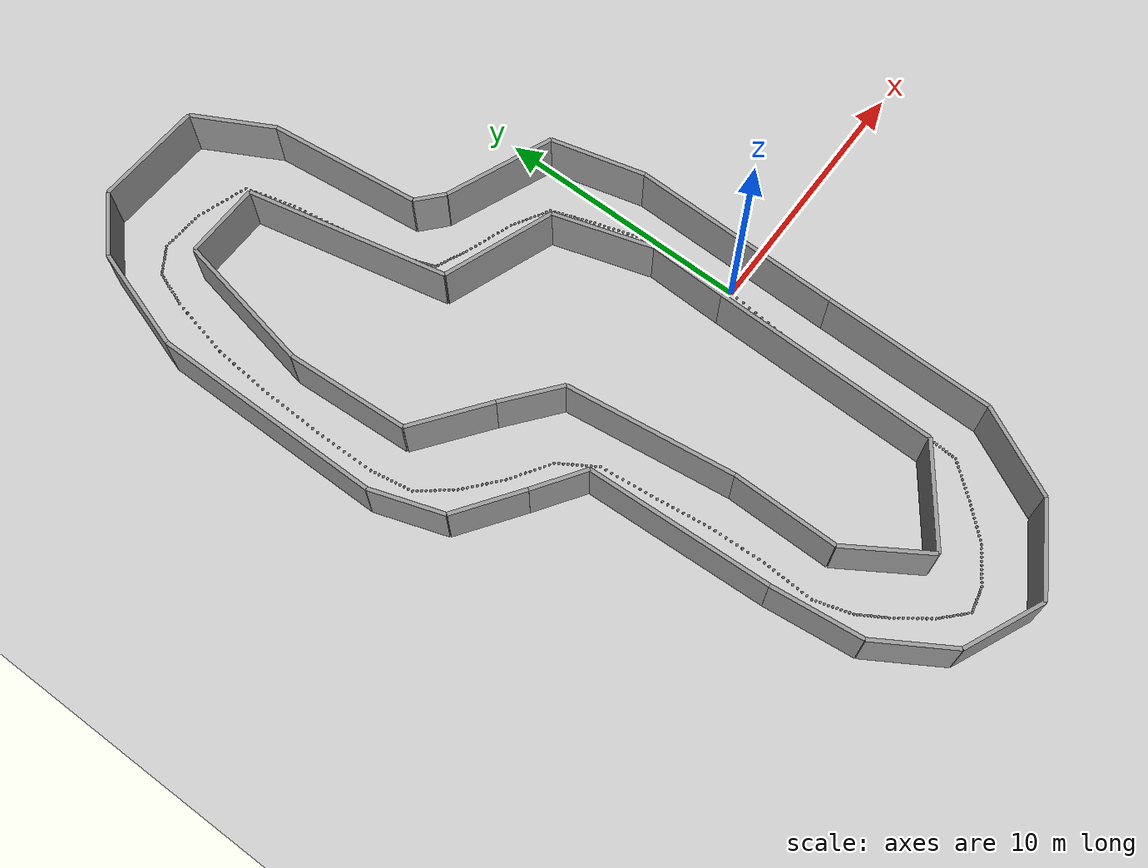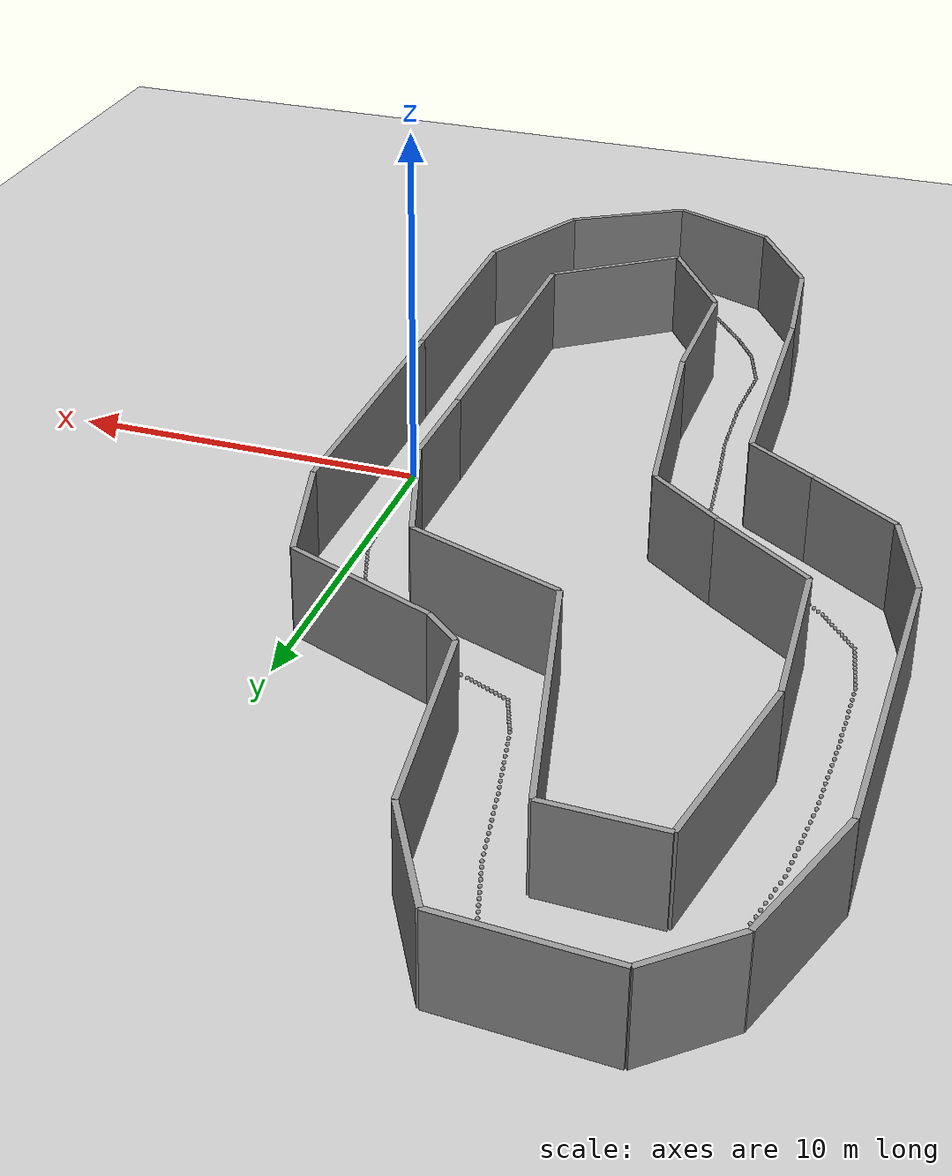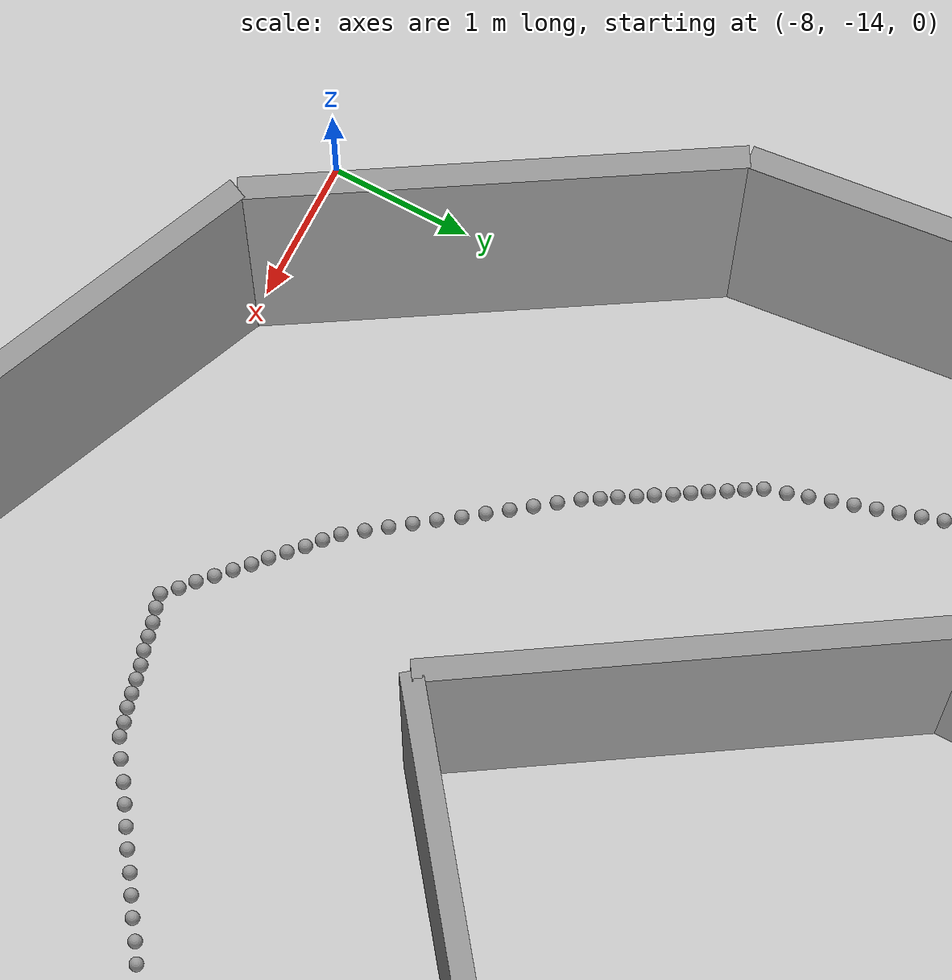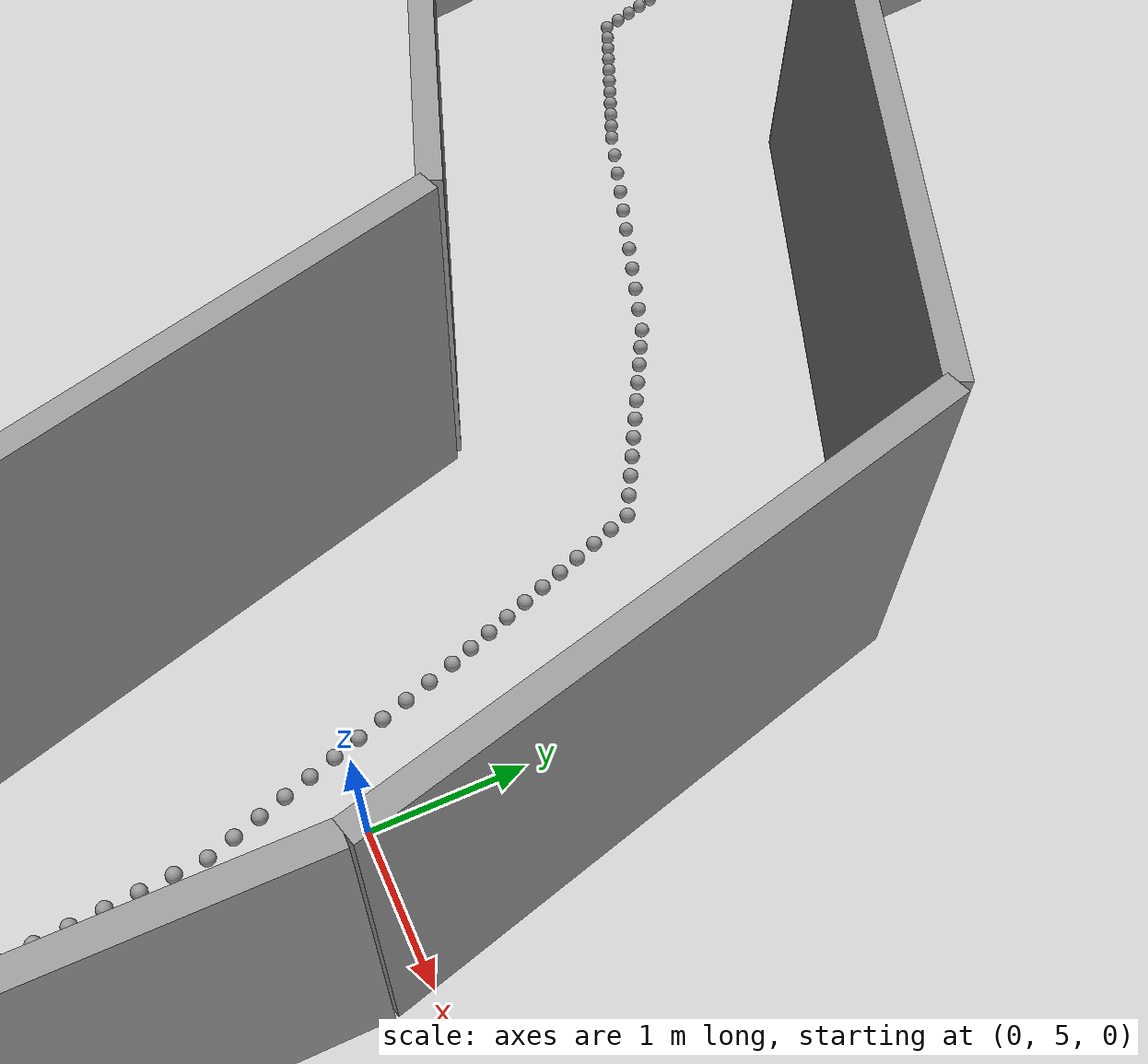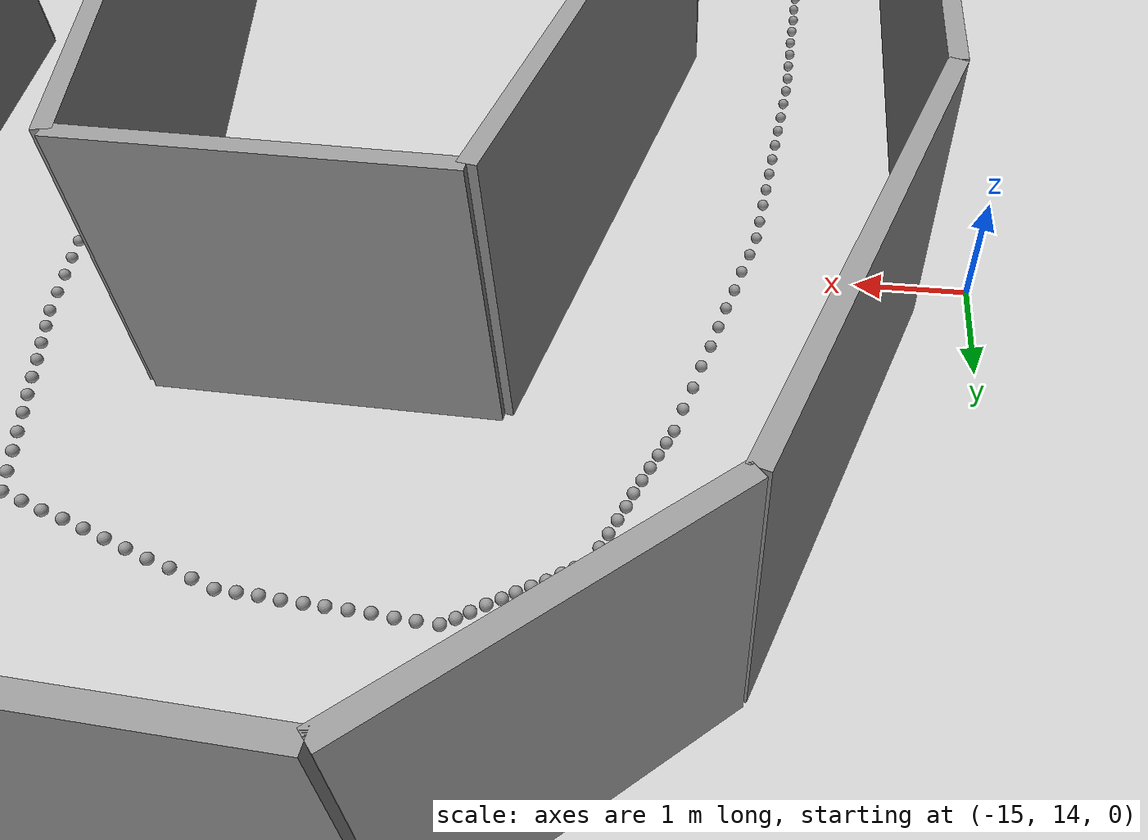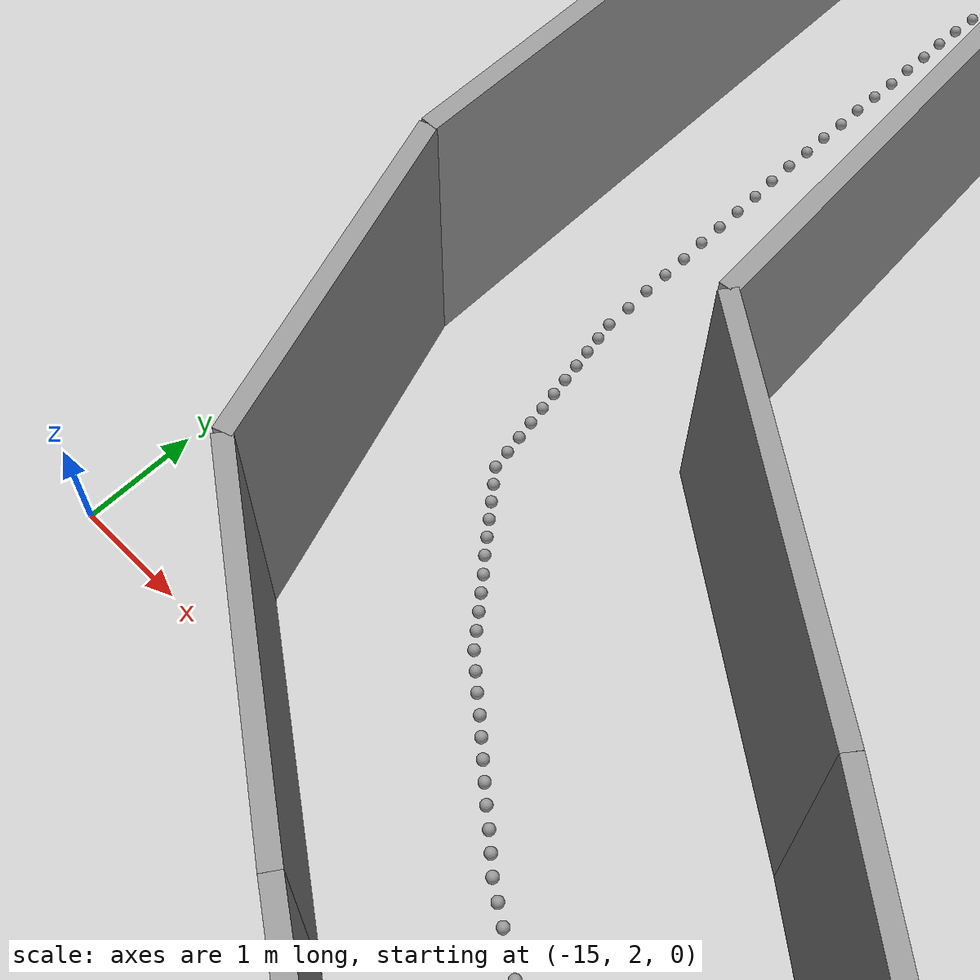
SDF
<sdf version='1.6'>
    <world name='default'>
      <light name='sun' type='directional'>
        <cast_shadows>1</cast_shadows>
        <pose frame=''>0 0 10 0 -0 0</pose>
        <diffuse>0.8 0.8 0.8 1</diffuse>
        <specular>0.2 0.2 0.2 1</specular>
        <attenuation>
          <range>1000</range>
          <constant>0.9</constant>
          <linear>0.01</linear>
          <quadratic>0.001</quadratic>
        </attenuation>
        <direction>-0.5 0.1 -0.9</direction>
      </light>
      <model name='ground_plane'>
        <static>1</static>
        <link name='link'>
          <collision name='collision'>
            <geometry>
              <plane>
                <normal>0 0 1</normal>
                <size>100 100</size>
              </plane>
            </geometry>
            <surface>
              <friction>
                <ode>
                  <mu>100</mu>
                  <mu2>50</mu2>
                </ode>
                <torsional>
                  <ode/>
                </torsional>
              </friction>
              <contact>
                <ode/>
              </contact>
              <bounce/>
            </surface>
            <max_contacts>10</max_contacts>
          </collision>
          <visual name='visual'>
            <cast_shadows>0</cast_shadows>
            <geometry>
              <plane>
                <normal>0 0 1</normal>
                <size>100 100</size>
              </plane>
            </geometry>
            <material>
              <script>
                <uri>file://media/materials/scripts/gazebo.material</uri>
                <name>Gazebo/Grey</name>
              </script>
            </material>
          </visual>
          <self_collide>0</self_collide>
          <enable_wind>0</enable_wind>
          <kinematic>0</kinematic>
        </link>
      </model>
      <gravity>0 0 -9.8</gravity>
      <magnetic_field>6e-06 2.3e-05 -4.2e-05</magnetic_field>
      <atmosphere type='adiabatic'/>
      <physics name='default_physics' default='0' type='ode'>
        <max_step_size>0.001</max_step_size>
        <real_time_factor>1</real_time_factor>
        <real_time_update_rate>1000</real_time_update_rate>
      </physics>
      <scene>
        <ambient>0.4 0.4 0.4 1</ambient>
        <background>0.7 0.7 0.7 1</background>
        <shadows>1</shadows>
      </scene>
      <wind/>
      <spherical_coordinates>
        <surface_model>EARTH_WGS84</surface_model>
        <latitude_deg>0</latitude_deg>
        <longitude_deg>0</longitude_deg>
        <elevation>0</elevation>
        <heading_deg>0</heading_deg>
      </spherical_coordinates>
      <model name='track2'>
        <pose frame=''>0 0 0 0 -0 0</pose>
        <link name='wall_000'>
                <collision name='wall_000_Collision'>
                <geometry>
                    <box>
                    <size>4.375392 0.15 2.5</size>
                    </box>
                </geometry>
                <pose frame=''>0 0 1.25 0 -0 0</pose>
                <max_contacts>10</max_contacts>
                <surface>
                    <contact>
                    <ode/>
                    </contact>
                    <bounce/>
                    <friction>
                    <torsional>
                        <ode/>
                    </torsional>
                    <ode/>
                    </friction>
                </surface>
                </collision>
                <visual name='wall_000_Visual'>
                <pose frame=''>0 0 1.25 0 -0 0</pose>
                <geometry>
                    <box>
                    <size>4.375392 0.15 2.5</size>
                    </box>
                </geometry>
                <material>
                    <script>
                    <uri>file://media/materials/scripts/gazebo.material</uri>
                    <name>Gazebo/Grey</name>
                    </script>
                    <ambient>1 1 1 1</ambient>
                </material>
                <meta>
                    <layer>0</layer>
                </meta>
                </visual>
                <pose frame=''>-1.965100 9.167000 0 0 -0 -0.390624</pose>
                <self_collide>0</self_collide>
                <enable_wind>0</enable_wind>
                <kinematic>0</kinematic>
            </link>
            <link name='wall_001'>
                <collision name='wall_001_Collision'>
                <geometry>
                    <box>
                    <size>1.246207 0.15 2.5</size>
                    </box>
                </geometry>
                <pose frame=''>0 0 1.25 0 -0 0</pose>
                <max_contacts>10</max_contacts>
                <surface>
                    <contact>
                    <ode/>
                    </contact>
                    <bounce/>
                    <friction>
                    <torsional>
                        <ode/>
                    </torsional>
                    <ode/>
                    </friction>
                </surface>
                </collision>
                <visual name='wall_001_Visual'>
                <pose frame=''>0 0 1.25 0 -0 0</pose>
                <geometry>
                    <box>
                    <size>1.246207 0.15 2.5</size>
                    </box>
                </geometry>
                <material>
                    <script>
                    <uri>file://media/materials/scripts/gazebo.material</uri>
                    <name>Gazebo/Grey</name>
                    </script>
                    <ambient>1 1 1 1</ambient>
                </material>
                <meta>
                    <layer>0</layer>
                </meta>
                </visual>
                <pose frame=''>-4.451000 10.417000 0 0 -0 -0.733173</pose>
                <self_collide>0</self_collide>
                <enable_wind>0</enable_wind>
                <kinematic>0</kinematic>
            </link>
            <link name='wall_002'>
                <collision name='wall_002_Collision'>
                <geometry>
                    <box>
                    <size>5.872911 0.15 2.5</size>
                    </box>
                </geometry>
                <pose frame=''>0 0 1.25 0 -0 0</pose>
                <max_contacts>10</max_contacts>
                <surface>
                    <contact>
                    <ode/>
                    </contact>
                    <bounce/>
                    <friction>
                    <torsional>
                        <ode/>
                    </torsional>
                    <ode/>
                    </friction>
                </surface>
                </collision>
                <visual name='wall_002_Visual'>
                <pose frame=''>0 0 1.25 0 -0 0</pose>
                <geometry>
                    <box>
                    <size>5.872911 0.15 2.5</size>
                    </box>
                </geometry>
                <material>
                    <script>
                    <uri>file://media/materials/scripts/gazebo.material</uri>
                    <name>Gazebo/Grey</name>
                    </script>
                    <ambient>1 1 1 1</ambient>
                </material>
                <meta>
                    <layer>0</layer>
                </meta>
                </visual>
                <pose frame=''>-5.260000 13.750000 0 0 -0 -1.452693</pose>
                <self_collide>0</self_collide>
                <enable_wind>0</enable_wind>
                <kinematic>0</kinematic>
            </link>
            <link name='wall_003'>
                <collision name='wall_003_Collision'>
                <geometry>
                    <box>
                    <size>3.309769 0.15 2.5</size>
                    </box>
                </geometry>
                <pose frame=''>0 0 1.25 0 -0 0</pose>
                <max_contacts>10</max_contacts>
                <surface>
                    <contact>
                    <ode/>
                    </contact>
                    <bounce/>
                    <friction>
                    <torsional>
                        <ode/>
                    </torsional>
                    <ode/>
                    </friction>
                </surface>
                </collision>
                <visual name='wall_003_Visual'>
                <pose frame=''>0 0 1.25 0 -0 0</pose>
                <geometry>
                    <box>
                    <size>3.309769 0.15 2.5</size>
                    </box>
                </geometry>
                <material>
                    <script>
                    <uri>file://media/materials/scripts/gazebo.material</uri>
                    <name>Gazebo/Grey</name>
                    </script>
                    <ambient>1 1 1 1</ambient>
                </material>
                <meta>
                    <layer>0</layer>
                </meta>
                </visual>
                <pose frame=''>-6.387000 18.125000 0 0 -0 -1.079311</pose>
                <self_collide>0</self_collide>
                <enable_wind>0</enable_wind>
                <kinematic>0</kinematic>
            </link>
            <link name='wall_004'>
                <collision name='wall_004_Collision'>
                <geometry>
                    <box>
                    <size>4.169502 0.15 2.5</size>
                    </box>
                </geometry>
                <pose frame=''>0 0 1.25 0 -0 0</pose>
                <max_contacts>10</max_contacts>
                <surface>
                    <contact>
                    <ode/>
                    </contact>
                    <bounce/>
                    <friction>
                    <torsional>
                        <ode/>
                    </torsional>
                    <ode/>
                    </friction>
                </surface>
                </collision>
                <visual name='wall_004_Visual'>
                <pose frame=''>0 0 1.25 0 -0 0</pose>
                <geometry>
                    <box>
                    <size>4.169502 0.15 2.5</size>
                    </box>
                </geometry>
                <material>
                    <script>
                    <uri>file://media/materials/scripts/gazebo.material</uri>
                    <name>Gazebo/Grey</name>
                    </script>
                    <ambient>1 1 1 1</ambient>
                </material>
                <meta>
                    <layer>0</layer>
                </meta>
                </visual>
                <pose frame=''>-9.249000 19.709000 0 0 -0 -0.059995</pose>
                <self_collide>0</self_collide>
                <enable_wind>0</enable_wind>
                <kinematic>0</kinematic>
            </link>
            <link name='wall_005'>
                <collision name='wall_005_Collision'>
                <geometry>
                    <box>
                    <size>2.490928 0.15 2.5</size>
                    </box>
                </geometry>
                <pose frame=''>0 0 1.25 0 -0 0</pose>
                <max_contacts>10</max_contacts>
                <surface>
                    <contact>
                    <ode/>
                    </contact>
                    <bounce/>
                    <friction>
                    <torsional>
                        <ode/>
                    </torsional>
                    <ode/>
                    </friction>
                </surface>
                </collision>
                <visual name='wall_005_Visual'>
                <pose frame=''>0 0 1.25 0 -0 0</pose>
                <geometry>
                    <box>
                    <size>2.490928 0.15 2.5</size>
                    </box>
                </geometry>
                <material>
                    <script>
                    <uri>file://media/materials/scripts/gazebo.material</uri>
                    <name>Gazebo/Grey</name>
                    </script>
                    <ambient>1 1 1 1</ambient>
                </material>
                <meta>
                    <layer>0</layer>
                </meta>
                </visual>
                <pose frame=''>-12.255000 19.000000 0 0 -0 0.733710</pose>
                <self_collide>0</self_collide>
                <enable_wind>0</enable_wind>
                <kinematic>0</kinematic>
            </link>
            <link name='wall_006'>
                <collision name='wall_006_Collision'>
                <geometry>
                    <box>
                    <size>4.116790 0.15 2.5</size>
                    </box>
                </geometry>
                <pose frame=''>0 0 1.25 0 -0 0</pose>
                <max_contacts>10</max_contacts>
                <surface>
                    <contact>
                    <ode/>
                    </contact>
                    <bounce/>
                    <friction>
                    <torsional>
                        <ode/>
                    </torsional>
                    <ode/>
                    </friction>
                </surface>
                </collision>
                <visual name='wall_006_Visual'>
                <pose frame=''>0 0 1.25 0 -0 0</pose>
                <geometry>
                    <box>
                    <size>4.116790 0.15 2.5</size>
                    </box>
                </geometry>
                <material>
                    <script>
                    <uri>file://media/materials/scripts/gazebo.material</uri>
                    <name>Gazebo/Grey</name>
                    </script>
                    <ambient>1 1 1 1</ambient>
                </material>
                <meta>
                    <layer>0</layer>
                </meta>
                </visual>
                <pose frame=''>-13.815000 16.208000 0 0 -0 1.257188</pose>
                <self_collide>0</self_collide>
                <enable_wind>0</enable_wind>
                <kinematic>0</kinematic>
            </link>
            <link name='wall_007'>
                <collision name='wall_007_Collision'>
                <geometry>
                    <box>
                    <size>9.000174 0.15 2.5</size>
                    </box>
                </geometry>
                <pose frame=''>0 0 1.25 0 -0 0</pose>
                <max_contacts>10</max_contacts>
                <surface>
                    <contact>
                    <ode/>
                    </contact>
                    <bounce/>
                    <friction>
                    <torsional>
                        <ode/>
                    </torsional>
                    <ode/>
                    </friction>
                </surface>
                </collision>
                <visual name='wall_007_Visual'>
                <pose frame=''>0 0 1.25 0 -0 0</pose>
                <geometry>
                    <box>
                    <size>9.000174 0.15 2.5</size>
                    </box>
                </geometry>
                <material>
                    <script>
                    <uri>file://media/materials/scripts/gazebo.material</uri>
                    <name>Gazebo/Grey</name>
                    </script>
                    <ambient>1 1 1 1</ambient>
                </material>
                <meta>
                    <layer>0</layer>
                </meta>
                </visual>
                <pose frame=''>-14.422000 9.750000 0 0 -0 1.577018</pose>
                <self_collide>0</self_collide>
                <enable_wind>0</enable_wind>
                <kinematic>0</kinematic>
            </link>
            <link name='wall_008'>
                <collision name='wall_008_Collision'>
                <geometry>
                    <box>
                    <size>2.901719 0.15 2.5</size>
                    </box>
                </geometry>
                <pose frame=''>0 0 1.25 0 -0 0</pose>
                <max_contacts>10</max_contacts>
                <surface>
                    <contact>
                    <ode/>
                    </contact>
                    <bounce/>
                    <friction>
                    <torsional>
                        <ode/>
                    </torsional>
                    <ode/>
                    </friction>
                </surface>
                </collision>
                <visual name='wall_008_Visual'>
                <pose frame=''>0 0 1.25 0 -0 0</pose>
                <geometry>
                    <box>
                    <size>2.901719 0.15 2.5</size>
                    </box>
                </geometry>
                <material>
                    <script>
                    <uri>file://media/materials/scripts/gazebo.material</uri>
                    <name>Gazebo/Grey</name>
                    </script>
                    <ambient>1 1 1 1</ambient>
                </material>
                <meta>
                    <layer>0</layer>
                </meta>
                </visual>
                <pose frame=''>-13.931000 3.875000 0 0 -0 1.895598</pose>
                <self_collide>0</self_collide>
                <enable_wind>0</enable_wind>
                <kinematic>0</kinematic>
            </link>
            <link name='wall_009'>
                <collision name='wall_009_Collision'>
                <geometry>
                    <box>
                    <size>2.897319 0.15 2.5</size>
                    </box>
                </geometry>
                <pose frame=''>0 0 1.25 0 -0 0</pose>
                <max_contacts>10</max_contacts>
                <surface>
                    <contact>
                    <ode/>
                    </contact>
                    <bounce/>
                    <friction>
                    <torsional>
                        <ode/>
                    </torsional>
                    <ode/>
                    </friction>
                </surface>
                </collision>
                <visual name='wall_009_Visual'>
                <pose frame=''>0 0 1.25 0 -0 0</pose>
                <geometry>
                    <box>
                    <size>2.897319 0.15 2.5</size>
                    </box>
                </geometry>
                <material>
                    <script>
                    <uri>file://media/materials/scripts/gazebo.material</uri>
                    <name>Gazebo/Grey</name>
                    </script>
                    <ambient>1 1 1 1</ambient>
                </material>
                <meta>
                    <layer>0</layer>
                </meta>
                </visual>
                <pose frame=''>-12.283000 1.666700 0 0 -0 2.528718</pose>
                <self_collide>0</self_collide>
                <enable_wind>0</enable_wind>
                <kinematic>0</kinematic>
            </link>
            <link name='wall_010'>
                <collision name='wall_010_Collision'>
                <geometry>
                    <box>
                    <size>2.232711 0.15 2.5</size>
                    </box>
                </geometry>
                <pose frame=''>0 0 1.25 0 -0 0</pose>
                <max_contacts>10</max_contacts>
                <surface>
                    <contact>
                    <ode/>
                    </contact>
                    <bounce/>
                    <friction>
                    <torsional>
                        <ode/>
                    </torsional>
                    <ode/>
                    </friction>
                </surface>
                </collision>
                <visual name='wall_010_Visual'>
                <pose frame=''>0 0 1.25 0 -0 0</pose>
                <geometry>
                    <box>
                    <size>2.232711 0.15 2.5</size>
                    </box>
                </geometry>
                <material>
                    <script>
                    <uri>file://media/materials/scripts/gazebo.material</uri>
                    <name>Gazebo/Grey</name>
                    </script>
                    <ambient>1 1 1 1</ambient>
                </material>
                <meta>
                    <layer>0</layer>
                </meta>
                </visual>
                <pose frame=''>-10.173000 0.208400 0 0 -0 2.547379</pose>
                <self_collide>0</self_collide>
                <enable_wind>0</enable_wind>
                <kinematic>0</kinematic>
            </link>
            <link name='wall_011'>
                <collision name='wall_011_Collision'>
                <geometry>
                    <box>
                    <size>7.257652 0.15 2.5</size>
                    </box>
                </geometry>
                <pose frame=''>0 0 1.25 0 -0 0</pose>
                <max_contacts>10</max_contacts>
                <surface>
                    <contact>
                    <ode/>
                    </contact>
                    <bounce/>
                    <friction>
                    <torsional>
                        <ode/>
                    </torsional>
                    <ode/>
                    </friction>
                </surface>
                </collision>
                <visual name='wall_011_Visual'>
                <pose frame=''>0 0 1.25 0 -0 0</pose>
                <geometry>
                    <box>
                    <size>7.257652 0.15 2.5</size>
                    </box>
                </geometry>
                <material>
                    <script>
                    <uri>file://media/materials/scripts/gazebo.material</uri>
                    <name>Gazebo/Grey</name>
                    </script>
                    <ambient>1 1 1 1</ambient>
                </material>
                <meta>
                    <layer>0</layer>
                </meta>
                </visual>
                <pose frame=''>-9.075000 -4.041300 0 0 -0 1.618488</pose>
                <self_collide>0</self_collide>
                <enable_wind>0</enable_wind>
                <kinematic>0</kinematic>
            </link>
            <link name='wall_012'>
                <collision name='wall_012_Collision'>
                <geometry>
                    <box>
                    <size>3.606698 0.15 2.5</size>
                    </box>
                </geometry>
                <pose frame=''>0 0 1.25 0 -0 0</pose>
                <max_contacts>10</max_contacts>
                <surface>
                    <contact>
                    <ode/>
                    </contact>
                    <bounce/>
                    <friction>
                    <torsional>
                        <ode/>
                    </torsional>
                    <ode/>
                    </friction>
                </surface>
                </collision>
                <visual name='wall_012_Visual'>
                <pose frame=''>0 0 1.25 0 -0 0</pose>
                <geometry>
                    <box>
                    <size>3.606698 0.15 2.5</size>
                    </box>
                </geometry>
                <material>
                    <script>
                    <uri>file://media/materials/scripts/gazebo.material</uri>
                    <name>Gazebo/Grey</name>
                    </script>
                    <ambient>1 1 1 1</ambient>
                </material>
                <meta>
                    <layer>0</layer>
                </meta>
                </visual>
                <pose frame=''>-8.700000 -9.458000 0 0 -0 1.683046</pose>
                <self_collide>0</self_collide>
                <enable_wind>0</enable_wind>
                <kinematic>0</kinematic>
            </link>
            <link name='wall_013'>
                <collision name='wall_013_Collision'>
                <geometry>
                    <box>
                    <size>3.221519 0.15 2.5</size>
                    </box>
                </geometry>
                <pose frame=''>0 0 1.25 0 -0 0</pose>
                <max_contacts>10</max_contacts>
                <surface>
                    <contact>
                    <ode/>
                    </contact>
                    <bounce/>
                    <friction>
                    <torsional>
                        <ode/>
                    </torsional>
                    <ode/>
                    </friction>
                </surface>
                </collision>
                <visual name='wall_013_Visual'>
                <pose frame=''>0 0 1.25 0 -0 0</pose>
                <geometry>
                    <box>
                    <size>3.221519 0.15 2.5</size>
                    </box>
                </geometry>
                <material>
                    <script>
                    <uri>file://media/materials/scripts/gazebo.material</uri>
                    <name>Gazebo/Grey</name>
                    </script>
                    <ambient>1 1 1 1</ambient>
                </material>
                <meta>
                    <layer>0</layer>
                </meta>
                </visual>
                <pose frame=''>-7.659000 -12.625000 0 0 -0 2.118669</pose>
                <self_collide>0</self_collide>
                <enable_wind>0</enable_wind>
                <kinematic>0</kinematic>
            </link>
            <link name='wall_014'>
                <collision name='wall_014_Collision'>
                <geometry>
                    <box>
                    <size>3.286879 0.15 2.5</size>
                    </box>
                </geometry>
                <pose frame=''>0 0 1.25 0 -0 0</pose>
                <max_contacts>10</max_contacts>
                <surface>
                    <contact>
                    <ode/>
                    </contact>
                    <bounce/>
                    <friction>
                    <torsional>
                        <ode/>
                    </torsional>
                    <ode/>
                    </friction>
                </surface>
                </collision>
                <visual name='wall_014_Visual'>
                <pose frame=''>0 0 1.25 0 -0 0</pose>
                <geometry>
                    <box>
                    <size>3.286879 0.15 2.5</size>
                    </box>
                </geometry>
                <material>
                    <script>
                    <uri>file://media/materials/scripts/gazebo.material</uri>
                    <name>Gazebo/Grey</name>
                    </script>
                    <ambient>1 1 1 1</ambient>
                </material>
                <meta>
                    <layer>0</layer>
                </meta>
                </visual>
                <pose frame=''>-5.318000 -14.667000 0 0 -0 2.723677</pose>
                <self_collide>0</self_collide>
                <enable_wind>0</enable_wind>
                <kinematic>0</kinematic>
            </link>
            <link name='wall_015'>
                <collision name='wall_015_Collision'>
                <geometry>
                    <box>
                    <size>3.664438 0.15 2.5</size>
                    </box>
                </geometry>
                <pose frame=''>0 0 1.25 0 -0 0</pose>
                <max_contacts>10</max_contacts>
                <surface>
                    <contact>
                    <ode/>
                    </contact>
                    <bounce/>
                    <friction>
                    <torsional>
                        <ode/>
                    </torsional>
                    <ode/>
                    </friction>
                </surface>
                </collision>
                <visual name='wall_015_Visual'>
                <pose frame=''>0 0 1.25 0 -0 0</pose>
                <geometry>
                    <box>
                    <size>3.664438 0.15 2.5</size>
                    </box>
                </geometry>
                <material>
                    <script>
                    <uri>file://media/materials/scripts/gazebo.material</uri>
                    <name>Gazebo/Grey</name>
                    </script>
                    <ambient>1 1 1 1</ambient>
                </material>
                <meta>
                    <layer>0</layer>
                </meta>
                </visual>
                <pose frame=''>-2.254800 -14.375000 0 0 -0 -2.590746</pose>
                <self_collide>0</self_collide>
                <enable_wind>0</enable_wind>
                <kinematic>0</kinematic>
            </link>
            <link name='wall_016'>
                <collision name='wall_016_Collision'>
                <geometry>
                    <box>
                    <size>3.704247 0.15 2.5</size>
                    </box>
                </geometry>
                <pose frame=''>0 0 1.25 0 -0 0</pose>
                <max_contacts>10</max_contacts>
                <surface>
                    <contact>
                    <ode/>
                    </contact>
                    <bounce/>
                    <friction>
                    <torsional>
                        <ode/>
                    </torsional>
                    <ode/>
                    </friction>
                </surface>
                </collision>
                <visual name='wall_016_Visual'>
                <pose frame=''>0 0 1.25 0 -0 0</pose>
                <geometry>
                    <box>
                    <size>3.704247 0.15 2.5</size>
                    </box>
                </geometry>
                <material>
                    <script>
                    <uri>file://media/materials/scripts/gazebo.material</uri>
                    <name>Gazebo/Grey</name>
                    </script>
                    <ambient>1 1 1 1</ambient>
                </material>
                <meta>
                    <layer>0</layer>
                </meta>
                </visual>
                <pose frame=''>0.115600 -11.750000 0 0 -0 -2.022950</pose>
                <self_collide>0</self_collide>
                <enable_wind>0</enable_wind>
                <kinematic>0</kinematic>
            </link>
            <link name='wall_017'>
                <collision name='wall_017_Collision'>
                <geometry>
                    <box>
                    <size>6.668000 0.15 2.5</size>
                    </box>
                </geometry>
                <pose frame=''>0 0 1.25 0 -0 0</pose>
                <max_contacts>10</max_contacts>
                <surface>
                    <contact>
                    <ode/>
                    </contact>
                    <bounce/>
                    <friction>
                    <torsional>
                        <ode/>
                    </torsional>
                    <ode/>
                    </friction>
                </surface>
                </collision>
                <visual name='wall_017_Visual'>
                <pose frame=''>0 0 1.25 0 -0 0</pose>
                <geometry>
                    <box>
                    <size>6.668000 0.15 2.5</size>
                    </box>
                </geometry>
                <material>
                    <script>
                    <uri>file://media/materials/scripts/gazebo.material</uri>
                    <name>Gazebo/Grey</name>
                    </script>
                    <ambient>1 1 1 1</ambient>
                </material>
                <meta>
                    <layer>0</layer>
                </meta>
                </visual>
                <pose frame=''>0.924800 -6.750000 0 0 -0 -1.570796</pose>
                <self_collide>0</self_collide>
                <enable_wind>0</enable_wind>
                <kinematic>0</kinematic>
            </link>
            <link name='wall_018'>
                <collision name='wall_018_Collision'>
                <geometry>
                    <box>
                    <size>8.166205 0.15 2.5</size>
                    </box>
                </geometry>
                <pose frame=''>0 0 1.25 0 -0 0</pose>
                <max_contacts>10</max_contacts>
                <surface>
                    <contact>
                    <ode/>
                    </contact>
                    <bounce/>
                    <friction>
                    <torsional>
                        <ode/>
                    </torsional>
                    <ode/>
                    </friction>
                </surface>
                </collision>
                <visual name='wall_018_Visual'>
                <pose frame=''>0 0 1.25 0 -0 0</pose>
                <geometry>
                    <box>
                    <size>8.166205 0.15 2.5</size>
                    </box>
                </geometry>
                <material>
                    <script>
                    <uri>file://media/materials/scripts/gazebo.material</uri>
                    <name>Gazebo/Grey</name>
                    </script>
                    <ambient>1 1 1 1</ambient>
                </material>
                <meta>
                    <layer>0</layer>
                </meta>
                </visual>
                <pose frame=''>0.953700 0.667000 0 0 -0 -1.577874</pose>
                <self_collide>0</self_collide>
                <enable_wind>0</enable_wind>
                <kinematic>0</kinematic>
            </link>
            <link name='wall_019'>
                <collision name='wall_019_Collision'>
                <geometry>
                    <box>
                    <size>3.701393 0.15 2.5</size>
                    </box>
                </geometry>
                <pose frame=''>0 0 1.25 0 -0 0</pose>
                <max_contacts>10</max_contacts>
                <surface>
                    <contact>
                    <ode/>
                    </contact>
                    <bounce/>
                    <friction>
                    <torsional>
                        <ode/>
                    </torsional>
                    <ode/>
                    </friction>
                </surface>
                </collision>
                <visual name='wall_019_Visual'>
                <pose frame=''>0 0 1.25 0 -0 0</pose>
                <geometry>
                    <box>
                    <size>3.701393 0.15 2.5</size>
                    </box>
                </geometry>
                <material>
                    <script>
                    <uri>file://media/materials/scripts/gazebo.material</uri>
                    <name>Gazebo/Grey</name>
                    </script>
                    <ambient>1 1 1 1</ambient>
                </material>
                <meta>
                    <layer>0</layer>
                </meta>
                </visual>
                <pose frame=''>0.520200 6.542000 0 0 -0 -1.318269</pose>
                <self_collide>0</self_collide>
                <enable_wind>0</enable_wind>
                <kinematic>0</kinematic>
            </link>
            <link name='wall_020'>
                <collision name='wall_020_Collision'>
                <geometry>
                    <box>
                    <size>4.507489 0.15 2.5</size>
                    </box>
                </geometry>
                <pose frame=''>0 0 1.25 0 -0 0</pose>
                <max_contacts>10</max_contacts>
                <surface>
                    <contact>
                    <ode/>
                    </contact>
                    <bounce/>
                    <friction>
                    <torsional>
                        <ode/>
                    </torsional>
                    <ode/>
                    </friction>
                </surface>
                </collision>
                <visual name='wall_020_Visual'>
                <pose frame=''>0 0 1.25 0 -0 0</pose>
                <geometry>
                    <box>
                    <size>4.507489 0.15 2.5</size>
                    </box>
                </geometry>
                <material>
                    <script>
                    <uri>file://media/materials/scripts/gazebo.material</uri>
                    <name>Gazebo/Grey</name>
                    </script>
                    <ambient>1 1 1 1</ambient>
                </material>
                <meta>
                    <layer>0</layer>
                </meta>
                </visual>
                <pose frame=''>-4.422000 7.292000 0 0 -0 -0.359082</pose>
                <self_collide>0</self_collide>
                <enable_wind>0</enable_wind>
                <kinematic>0</kinematic>
            </link>
            <link name='wall_021'>
                <collision name='wall_021_Collision'>
                <geometry>
                    <box>
                    <size>7.847072 0.15 2.5</size>
                    </box>
                </geometry>
                <pose frame=''>0 0 1.25 0 -0 0</pose>
                <max_contacts>10</max_contacts>
                <surface>
                    <contact>
                    <ode/>
                    </contact>
                    <bounce/>
                    <friction>
                    <torsional>
                        <ode/>
                    </torsional>
                    <ode/>
                    </friction>
                </surface>
                </collision>
                <visual name='wall_021_Visual'>
                <pose frame=''>0 0 1.25 0 -0 0</pose>
                <geometry>
                    <box>
                    <size>7.847072 0.15 2.5</size>
                    </box>
                </geometry>
                <material>
                    <script>
                    <uri>file://media/materials/scripts/gazebo.material</uri>
                    <name>Gazebo/Grey</name>
                    </script>
                    <ambient>1 1 1 1</ambient>
                </material>
                <meta>
                    <layer>0</layer>
                </meta>
                </visual>
                <pose frame=''>-7.370000 11.917000 0 0 -0 -1.355555</pose>
                <self_collide>0</self_collide>
                <enable_wind>0</enable_wind>
                <kinematic>0</kinematic>
            </link>
            <link name='wall_022'>
                <collision name='wall_022_Collision'>
                <geometry>
                    <box>
                    <size>2.949197 0.15 2.5</size>
                    </box>
                </geometry>
                <pose frame=''>0 0 1.25 0 -0 0</pose>
                <max_contacts>10</max_contacts>
                <surface>
                    <contact>
                    <ode/>
                    </contact>
                    <bounce/>
                    <friction>
                    <torsional>
                        <ode/>
                    </torsional>
                    <ode/>
                    </friction>
                </surface>
                </collision>
                <visual name='wall_022_Visual'>
                <pose frame=''>0 0 1.25 0 -0 0</pose>
                <geometry>
                    <box>
                    <size>2.949197 0.15 2.5</size>
                    </box>
                </geometry>
                <material>
                    <script>
                    <uri>file://media/materials/scripts/gazebo.material</uri>
                    <name>Gazebo/Grey</name>
                    </script>
                    <ambient>1 1 1 1</ambient>
                </material>
                <meta>
                    <layer>0</layer>
                </meta>
                </visual>
                <pose frame=''>-9.682000 15.792000 0 0 -0 -0.028486</pose>
                <self_collide>0</self_collide>
                <enable_wind>0</enable_wind>
                <kinematic>0</kinematic>
            </link>
            <link name='wall_023'>
                <collision name='wall_023_Collision'>
                <geometry>
                    <box>
                    <size>5.516913 0.15 2.5</size>
                    </box>
                </geometry>
                <pose frame=''>0 0 1.25 0 -0 0</pose>
                <max_contacts>10</max_contacts>
                <surface>
                    <contact>
                    <ode/>
                    </contact>
                    <bounce/>
                    <friction>
                    <torsional>
                        <ode/>
                    </torsional>
                    <ode/>
                    </friction>
                </surface>
                </collision>
                <visual name='wall_023_Visual'>
                <pose frame=''>0 0 1.25 0 -0 0</pose>
                <geometry>
                    <box>
                    <size>5.516913 0.15 2.5</size>
                    </box>
                </geometry>
                <material>
                    <script>
                    <uri>file://media/materials/scripts/gazebo.material</uri>
                    <name>Gazebo/Grey</name>
                    </script>
                    <ambient>1 1 1 1</ambient>
                </material>
                <meta>
                    <layer>0</layer>
                </meta>
                </visual>
                <pose frame=''>-11.676000 13.125000 0 0 -0 1.381150</pose>
                <self_collide>0</self_collide>
                <enable_wind>0</enable_wind>
                <kinematic>0</kinematic>
            </link>
            <link name='wall_024'>
                <collision name='wall_024_Collision'>
                <geometry>
                    <box>
                    <size>4.758723 0.15 2.5</size>
                    </box>
                </geometry>
                <pose frame=''>0 0 1.25 0 -0 0</pose>
                <max_contacts>10</max_contacts>
                <surface>
                    <contact>
                    <ode/>
                    </contact>
                    <bounce/>
                    <friction>
                    <torsional>
                        <ode/>
                    </torsional>
                    <ode/>
                    </friction>
                </surface>
                </collision>
                <visual name='wall_024_Visual'>
                <pose frame=''>0 0 1.25 0 -0 0</pose>
                <geometry>
                    <box>
                    <size>4.758723 0.15 2.5</size>
                    </box>
                </geometry>
                <material>
                    <script>
                    <uri>file://media/materials/scripts/gazebo.material</uri>
                    <name>Gazebo/Grey</name>
                    </script>
                    <ambient>1 1 1 1</ambient>
                </material>
                <meta>
                    <layer>0</layer>
                </meta>
                </visual>
                <pose frame=''>-12.052000 8.041000 0 0 -0 1.631354</pose>
                <self_collide>0</self_collide>
                <enable_wind>0</enable_wind>
                <kinematic>0</kinematic>
            </link>
            <link name='wall_025'>
                <collision name='wall_025_Collision'>
                <geometry>
                    <box>
                    <size>3.328002 0.15 2.5</size>
                    </box>
                </geometry>
                <pose frame=''>0 0 1.25 0 -0 0</pose>
                <max_contacts>10</max_contacts>
                <surface>
                    <contact>
                    <ode/>
                    </contact>
                    <bounce/>
                    <friction>
                    <torsional>
                        <ode/>
                    </torsional>
                    <ode/>
                    </friction>
                </surface>
                </collision>
                <visual name='wall_025_Visual'>
                <pose frame=''>0 0 1.25 0 -0 0</pose>
                <geometry>
                    <box>
                    <size>3.328002 0.15 2.5</size>
                    </box>
                </geometry>
                <material>
                    <script>
                    <uri>file://media/materials/scripts/gazebo.material</uri>
                    <name>Gazebo/Grey</name>
                    </script>
                    <ambient>1 1 1 1</ambient>
                </material>
                <meta>
                    <layer>0</layer>
                </meta>
                </visual>
                <pose frame=''>-10.578000 4.666000 0 0 -0 2.496890</pose>
                <self_collide>0</self_collide>
                <enable_wind>0</enable_wind>
                <kinematic>0</kinematic>
            </link>
            <link name='wall_026'>
                <collision name='wall_026_Collision'>
                <geometry>
                    <box>
                    <size>2.521908 0.15 2.5</size>
                    </box>
                </geometry>
                <pose frame=''>0 0 1.25 0 -0 0</pose>
                <max_contacts>10</max_contacts>
                <surface>
                    <contact>
                    <ode/>
                    </contact>
                    <bounce/>
                    <friction>
                    <torsional>
                        <ode/>
                    </torsional>
                    <ode/>
                    </friction>
                </surface>
                </collision>
                <visual name='wall_026_Visual'>
                <pose frame=''>0 0 1.25 0 -0 0</pose>
                <geometry>
                    <box>
                    <size>2.521908 0.15 2.5</size>
                    </box>
                </geometry>
                <material>
                    <script>
                    <uri>file://media/materials/scripts/gazebo.material</uri>
                    <name>Gazebo/Grey</name>
                    </script>
                    <ambient>1 1 1 1</ambient>
                </material>
                <meta>
                    <layer>0</layer>
                </meta>
                </visual>
                <pose frame=''>-8.266000 2.875000 0 0 -0 2.463508</pose>
                <self_collide>0</self_collide>
                <enable_wind>0</enable_wind>
                <kinematic>0</kinematic>
            </link>
            <link name='wall_027'>
                <collision name='wall_027_Collision'>
                <geometry>
                    <box>
                    <size>6.640970 0.15 2.5</size>
                    </box>
                </geometry>
                <pose frame=''>0 0 1.25 0 -0 0</pose>
                <max_contacts>10</max_contacts>
                <surface>
                    <contact>
                    <ode/>
                    </contact>
                    <bounce/>
                    <friction>
                    <torsional>
                        <ode/>
                    </torsional>
                    <ode/>
                    </friction>
                </surface>
                </collision>
                <visual name='wall_027_Visual'>
                <pose frame=''>0 0 1.25 0 -0 0</pose>
                <geometry>
                    <box>
                    <size>6.640970 0.15 2.5</size>
                    </box>
                </geometry>
                <material>
                    <script>
                    <uri>file://media/materials/scripts/gazebo.material</uri>
                    <name>Gazebo/Grey</name>
                    </script>
                    <ambient>1 1 1 1</ambient>
                </material>
                <meta>
                    <layer>0</layer>
                </meta>
                </visual>
                <pose frame=''>-6.850000 -1.208000 0 0 -0 1.701875</pose>
                <self_collide>0</self_collide>
                <enable_wind>0</enable_wind>
                <kinematic>0</kinematic>
            </link>
            <link name='wall_028'>
                <collision name='wall_028_Collision'>
                <geometry>
                    <box>
                    <size>4.166000 0.15 2.5</size>
                    </box>
                </geometry>
                <pose frame=''>0 0 1.25 0 -0 0</pose>
                <max_contacts>10</max_contacts>
                <surface>
                    <contact>
                    <ode/>
                    </contact>
                    <bounce/>
                    <friction>
                    <torsional>
                        <ode/>
                    </torsional>
                    <ode/>
                    </friction>
                </surface>
                </collision>
                <visual name='wall_028_Visual'>
                <pose frame=''>0 0 1.25 0 -0 0</pose>
                <geometry>
                    <box>
                    <size>4.166000 0.15 2.5</size>
                    </box>
                </geometry>
                <material>
                    <script>
                    <uri>file://media/materials/scripts/gazebo.material</uri>
                    <name>Gazebo/Grey</name>
                    </script>
                    <ambient>1 1 1 1</ambient>
                </material>
                <meta>
                    <layer>0</layer>
                </meta>
                </visual>
                <pose frame=''>-6.416000 -6.583000 0 0 -0 1.570796</pose>
                <self_collide>0</self_collide>
                <enable_wind>0</enable_wind>
                <kinematic>0</kinematic>
            </link>
            <link name='wall_029'>
                <collision name='wall_029_Collision'>
                <geometry>
                    <box>
                    <size>3.455029 0.15 2.5</size>
                    </box>
                </geometry>
                <pose frame=''>0 0 1.25 0 -0 0</pose>
                <max_contacts>10</max_contacts>
                <surface>
                    <contact>
                    <ode/>
                    </contact>
                    <bounce/>
                    <friction>
                    <torsional>
                        <ode/>
                    </torsional>
                    <ode/>
                    </friction>
                </surface>
                </collision>
                <visual name='wall_029_Visual'>
                <pose frame=''>0 0 1.25 0 -0 0</pose>
                <geometry>
                    <box>
                    <size>3.455029 0.15 2.5</size>
                    </box>
                </geometry>
                <material>
                    <script>
                    <uri>file://media/materials/scripts/gazebo.material</uri>
                    <name>Gazebo/Grey</name>
                    </script>
                    <ambient>1 1 1 1</ambient>
                </material>
                <meta>
                    <layer>0</layer>
                </meta>
                </visual>
                <pose frame=''>-5.491000 -10.125000 0 0 -0 2.135838</pose>
                <self_collide>0</self_collide>
                <enable_wind>0</enable_wind>
                <kinematic>0</kinematic>
            </link>
            <link name='wall_030'>
                <collision name='wall_030_Collision'>
                <geometry>
                    <box>
                    <size>4.135586 0.15 2.5</size>
                    </box>
                </geometry>
                <pose frame=''>0 0 1.25 0 -0 0</pose>
                <max_contacts>10</max_contacts>
                <surface>
                    <contact>
                    <ode/>
                    </contact>
                    <bounce/>
                    <friction>
                    <torsional>
                        <ode/>
                    </torsional>
                    <ode/>
                    </friction>
                </surface>
                </collision>
                <visual name='wall_030_Visual'>
                <pose frame=''>0 0 1.25 0 -0 0</pose>
                <geometry>
                    <box>
                    <size>4.135586 0.15 2.5</size>
                    </box>
                </geometry>
                <material>
                    <script>
                    <uri>file://media/materials/scripts/gazebo.material</uri>
                    <name>Gazebo/Grey</name>
                    </script>
                    <ambient>1 1 1 1</ambient>
                </material>
                <meta>
                    <layer>0</layer>
                </meta>
                </visual>
                <pose frame=''>-2.918800 -10.334000 0 0 -0 -2.492443</pose>
                <self_collide>0</self_collide>
                <enable_wind>0</enable_wind>
                <kinematic>0</kinematic>
            </link>
            <link name='wall_031'>
                <collision name='wall_031_Collision'>
                <geometry>
                    <box>
                    <size>8.834189 0.15 2.5</size>
                    </box>
                </geometry>
                <pose frame=''>0 0 1.25 0 -0 0</pose>
                <max_contacts>10</max_contacts>
                <surface>
                    <contact>
                    <ode/>
                    </contact>
                    <bounce/>
                    <friction>
                    <torsional>
                        <ode/>
                    </torsional>
                    <ode/>
                    </friction>
                </surface>
                </collision>
                <visual name='wall_031_Visual'>
                <pose frame=''>0 0 1.25 0 -0 0</pose>
                <geometry>
                    <box>
                    <size>8.834189 0.15 2.5</size>
                    </box>
                </geometry>
                <material>
                    <script>
                    <uri>file://media/materials/scripts/gazebo.material</uri>
                    <name>Gazebo/Grey</name>
                    </script>
                    <ambient>1 1 1 1</ambient>
                </material>
                <meta>
                    <layer>0</layer>
                </meta>
                </visual>
                <pose frame=''>-1.242700 -4.667000 0 0 -0 -1.577339</pose>
                <self_collide>0</self_collide>
                <enable_wind>0</enable_wind>
                <kinematic>0</kinematic>
            </link>
            <link name='wall_032'>
                <collision name='wall_032_Collision'>
                <geometry>
                    <box>
                    <size>3.000557 0.15 2.5</size>
                    </box>
                </geometry>
                <pose frame=''>0 0 1.25 0 -0 0</pose>
                <max_contacts>10</max_contacts>
                <surface>
                    <contact>
                    <ode/>
                    </contact>
                    <bounce/>
                    <friction>
                    <torsional>
                        <ode/>
                    </torsional>
                    <ode/>
                    </friction>
                </surface>
                </collision>
                <visual name='wall_032_Visual'>
                <pose frame=''>0 0 1.25 0 -0 0</pose>
                <geometry>
                    <box>
                    <size>3.000557 0.15 2.5</size>
                    </box>
                </geometry>
                <material>
                    <script>
                    <uri>file://media/materials/scripts/gazebo.material</uri>
                    <name>Gazebo/Grey</name>
                    </script>
                    <ambient>1 1 1 1</ambient>
                </material>
                <meta>
                    <layer>0</layer>
                </meta>
                </visual>
                <pose frame=''>-1.184900 1.250000 0 0 -0 -1.590061</pose>
                <self_collide>0</self_collide>
                <enable_wind>0</enable_wind>
                <kinematic>0</kinematic>
            </link>
            <link name='wall_033'>
                <collision name='wall_033_Collision'>
                <geometry>
                    <box>
                    <size>3.924135 0.15 2.5</size>
                    </box>
                </geometry>
                <pose frame=''>0 0 1.25 0 -0 0</pose>
                <max_contacts>10</max_contacts>
                <surface>
                    <contact>
                    <ode/>
                    </contact>
                    <bounce/>
                    <friction>
                    <torsional>
                        <ode/>
                    </torsional>
                    <ode/>
                    </friction>
                </surface>
                </collision>
                <visual name='wall_033_Visual'>
                <pose frame=''>0 0 1.25 0 -0 0</pose>
                <geometry>
                    <box>
                    <size>3.924135 0.15 2.5</size>
                    </box>
                </geometry>
                <material>
                    <script>
                    <uri>file://media/materials/scripts/gazebo.material</uri>
                    <name>Gazebo/Grey</name>
                    </script>
                    <ambient>1 1 1 1</ambient>
                </material>
                <meta>
                    <layer>0</layer>
                </meta>
                </visual>
                <pose frame=''>-1.734000 4.625000 0 0 -0 -1.271773</pose>
                <self_collide>0</self_collide>
                <enable_wind>0</enable_wind>
                <kinematic>0</kinematic>
            </link>
            <static>1</static>
      </model>
      <gui fullscreen='0'>
        <camera name='user_camera'>
          <pose frame=''>-9.88167 -5.87841 72.8661 3.14159 1.57079 3.14159</pose>
          <view_controller>orbit</view_controller>
          <projection_type>perspective</projection_type>
        </camera>
      </gui>
      <model name='unit_sphere_0_0'>
      <pose frame=''>0.000000 0.000000 0.050000 0 -0 0</pose>
      <link name='link'>
        <inertial>
          <mass>1</mass>
          <inertia>
            <ixx>0.1</ixx>
            <ixy>0</ixy>
            <ixz>0</ixz>
            <iyy>0.1</iyy>
            <iyz>0</iyz>
            <izz>0.1</izz>
          </inertia>
        </inertial>
        <collision name='collision'>
          <geometry>
            <sphere>
              <radius>0.050000</radius>
            </sphere>
          </geometry>
          <max_contacts>10</max_contacts>
          <surface>
            <contact>
              <ode/>
            </contact>
            <bounce/>
            <friction>
              <torsional>
                <ode/>
              </torsional>
              <ode/>
            </friction>
          </surface>
        </collision>
        <visual name='visual'>
          <geometry>
            <sphere>
              <radius>0.050000</radius>
            </sphere>
          </geometry>
          <material>
            <script>
              <name>Gazebo/Grey</name>
              <uri>file://media/materials/scripts/gazebo.material</uri>
            </script>
          </material>
        </visual>
        <self_collide>0</self_collide>
        <kinematic>0</kinematic>
        <gravity>1</gravity>
      </link>
    </model>
        <model name='unit_sphere_0_1'>
      <pose frame=''>-0.007000 0.204000 0.050000 0 -0 0</pose>
      <link name='link'>
        <inertial>
          <mass>1</mass>
          <inertia>
            <ixx>0.1</ixx>
            <ixy>0</ixy>
            <ixz>0</ixz>
            <iyy>0.1</iyy>
            <iyz>0</iyz>
            <izz>0.1</izz>
          </inertia>
        </inertial>
        <collision name='collision'>
          <geometry>
            <sphere>
              <radius>0.050000</radius>
            </sphere>
          </geometry>
          <max_contacts>10</max_contacts>
          <surface>
            <contact>
              <ode/>
            </contact>
            <bounce/>
            <friction>
              <torsional>
                <ode/>
              </torsional>
              <ode/>
            </friction>
          </surface>
        </collision>
        <visual name='visual'>
          <geometry>
            <sphere>
              <radius>0.050000</radius>
            </sphere>
          </geometry>
          <material>
            <script>
              <name>Gazebo/Grey</name>
              <uri>file://media/materials/scripts/gazebo.material</uri>
            </script>
          </material>
        </visual>
        <self_collide>0</self_collide>
        <kinematic>0</kinematic>
        <gravity>1</gravity>
      </link>
    </model>
        <model name='unit_sphere_0_2'>
      <pose frame=''>-0.014000 0.408000 0.050000 0 -0 0</pose>
      <link name='link'>
        <inertial>
          <mass>1</mass>
          <inertia>
            <ixx>0.1</ixx>
            <ixy>0</ixy>
            <ixz>0</ixz>
            <iyy>0.1</iyy>
            <iyz>0</iyz>
            <izz>0.1</izz>
          </inertia>
        </inertial>
        <collision name='collision'>
          <geometry>
            <sphere>
              <radius>0.050000</radius>
            </sphere>
          </geometry>
          <max_contacts>10</max_contacts>
          <surface>
            <contact>
              <ode/>
            </contact>
            <bounce/>
            <friction>
              <torsional>
                <ode/>
              </torsional>
              <ode/>
            </friction>
          </surface>
        </collision>
        <visual name='visual'>
          <geometry>
            <sphere>
              <radius>0.050000</radius>
            </sphere>
          </geometry>
          <material>
            <script>
              <name>Gazebo/Grey</name>
              <uri>file://media/materials/scripts/gazebo.material</uri>
            </script>
          </material>
        </visual>
        <self_collide>0</self_collide>
        <kinematic>0</kinematic>
        <gravity>1</gravity>
      </link>
    </model>
        <model name='unit_sphere_0_3'>
      <pose frame=''>-0.021000 0.612000 0.050000 0 -0 0</pose>
      <link name='link'>
        <inertial>
          <mass>1</mass>
          <inertia>
            <ixx>0.1</ixx>
            <ixy>0</ixy>
            <ixz>0</ixz>
            <iyy>0.1</iyy>
            <iyz>0</iyz>
            <izz>0.1</izz>
          </inertia>
        </inertial>
        <collision name='collision'>
          <geometry>
            <sphere>
              <radius>0.050000</radius>
            </sphere>
          </geometry>
          <max_contacts>10</max_contacts>
          <surface>
            <contact>
              <ode/>
            </contact>
            <bounce/>
            <friction>
              <torsional>
                <ode/>
              </torsional>
              <ode/>
            </friction>
          </surface>
        </collision>
        <visual name='visual'>
          <geometry>
            <sphere>
              <radius>0.050000</radius>
            </sphere>
          </geometry>
          <material>
            <script>
              <name>Gazebo/Grey</name>
              <uri>file://media/materials/scripts/gazebo.material</uri>
            </script>
          </material>
        </visual>
        <self_collide>0</self_collide>
        <kinematic>0</kinematic>
        <gravity>1</gravity>
      </link>
    </model>
        <model name='unit_sphere_0_4'>
      <pose frame=''>-0.028000 0.816000 0.050000 0 -0 0</pose>
      <link name='link'>
        <inertial>
          <mass>1</mass>
          <inertia>
            <ixx>0.1</ixx>
            <ixy>0</ixy>
            <ixz>0</ixz>
            <iyy>0.1</iyy>
            <iyz>0</iyz>
            <izz>0.1</izz>
          </inertia>
        </inertial>
        <collision name='collision'>
          <geometry>
            <sphere>
              <radius>0.050000</radius>
            </sphere>
          </geometry>
          <max_contacts>10</max_contacts>
          <surface>
            <contact>
              <ode/>
            </contact>
            <bounce/>
            <friction>
              <torsional>
                <ode/>
              </torsional>
              <ode/>
            </friction>
          </surface>
        </collision>
        <visual name='visual'>
          <geometry>
            <sphere>
              <radius>0.050000</radius>
            </sphere>
          </geometry>
          <material>
            <script>
              <name>Gazebo/Grey</name>
              <uri>file://media/materials/scripts/gazebo.material</uri>
            </script>
          </material>
        </visual>
        <self_collide>0</self_collide>
        <kinematic>0</kinematic>
        <gravity>1</gravity>
      </link>
    </model>
        <model name='unit_sphere_0_5'>
      <pose frame=''>-0.035000 1.020000 0.050000 0 -0 0</pose>
      <link name='link'>
        <inertial>
          <mass>1</mass>
          <inertia>
            <ixx>0.1</ixx>
            <ixy>0</ixy>
            <ixz>0</ixz>
            <iyy>0.1</iyy>
            <iyz>0</iyz>
            <izz>0.1</izz>
          </inertia>
        </inertial>
        <collision name='collision'>
          <geometry>
            <sphere>
              <radius>0.050000</radius>
            </sphere>
          </geometry>
          <max_contacts>10</max_contacts>
          <surface>
            <contact>
              <ode/>
            </contact>
            <bounce/>
            <friction>
              <torsional>
                <ode/>
              </torsional>
              <ode/>
            </friction>
          </surface>
        </collision>
        <visual name='visual'>
          <geometry>
            <sphere>
              <radius>0.050000</radius>
            </sphere>
          </geometry>
          <material>
            <script>
              <name>Gazebo/Grey</name>
              <uri>file://media/materials/scripts/gazebo.material</uri>
            </script>
          </material>
        </visual>
        <self_collide>0</self_collide>
        <kinematic>0</kinematic>
        <gravity>1</gravity>
      </link>
    </model>
        <model name='unit_sphere_0_6'>
      <pose frame=''>-0.042000 1.224000 0.050000 0 -0 0</pose>
      <link name='link'>
        <inertial>
          <mass>1</mass>
          <inertia>
            <ixx>0.1</ixx>
            <ixy>0</ixy>
            <ixz>0</ixz>
            <iyy>0.1</iyy>
            <iyz>0</iyz>
            <izz>0.1</izz>
          </inertia>
        </inertial>
        <collision name='collision'>
          <geometry>
            <sphere>
              <radius>0.050000</radius>
            </sphere>
          </geometry>
          <max_contacts>10</max_contacts>
          <surface>
            <contact>
              <ode/>
            </contact>
            <bounce/>
            <friction>
              <torsional>
                <ode/>
              </torsional>
              <ode/>
            </friction>
          </surface>
        </collision>
        <visual name='visual'>
          <geometry>
            <sphere>
              <radius>0.050000</radius>
            </sphere>
          </geometry>
          <material>
            <script>
              <name>Gazebo/Grey</name>
              <uri>file://media/materials/scripts/gazebo.material</uri>
            </script>
          </material>
        </visual>
        <self_collide>0</self_collide>
        <kinematic>0</kinematic>
        <gravity>1</gravity>
      </link>
    </model>
        <model name='unit_sphere_0_7'>
      <pose frame=''>-0.049000 1.428000 0.050000 0 -0 0</pose>
      <link name='link'>
        <inertial>
          <mass>1</mass>
          <inertia>
            <ixx>0.1</ixx>
            <ixy>0</ixy>
            <ixz>0</ixz>
            <iyy>0.1</iyy>
            <iyz>0</iyz>
            <izz>0.1</izz>
          </inertia>
        </inertial>
        <collision name='collision'>
          <geometry>
            <sphere>
              <radius>0.050000</radius>
            </sphere>
          </geometry>
          <max_contacts>10</max_contacts>
          <surface>
            <contact>
              <ode/>
            </contact>
            <bounce/>
            <friction>
              <torsional>
                <ode/>
              </torsional>
              <ode/>
            </friction>
          </surface>
        </collision>
        <visual name='visual'>
          <geometry>
            <sphere>
              <radius>0.050000</radius>
            </sphere>
          </geometry>
          <material>
            <script>
              <name>Gazebo/Grey</name>
              <uri>file://media/materials/scripts/gazebo.material</uri>
            </script>
          </material>
        </visual>
        <self_collide>0</self_collide>
        <kinematic>0</kinematic>
        <gravity>1</gravity>
      </link>
    </model>
        <model name='unit_sphere_0_8'>
      <pose frame=''>-0.056000 1.632000 0.050000 0 -0 0</pose>
      <link name='link'>
        <inertial>
          <mass>1</mass>
          <inertia>
            <ixx>0.1</ixx>
            <ixy>0</ixy>
            <ixz>0</ixz>
            <iyy>0.1</iyy>
            <iyz>0</iyz>
            <izz>0.1</izz>
          </inertia>
        </inertial>
        <collision name='collision'>
          <geometry>
            <sphere>
              <radius>0.050000</radius>
            </sphere>
          </geometry>
          <max_contacts>10</max_contacts>
          <surface>
            <contact>
              <ode/>
            </contact>
            <bounce/>
            <friction>
              <torsional>
                <ode/>
              </torsional>
              <ode/>
            </friction>
          </surface>
        </collision>
        <visual name='visual'>
          <geometry>
            <sphere>
              <radius>0.050000</radius>
            </sphere>
          </geometry>
          <material>
            <script>
              <name>Gazebo/Grey</name>
              <uri>file://media/materials/scripts/gazebo.material</uri>
            </script>
          </material>
        </visual>
        <self_collide>0</self_collide>
        <kinematic>0</kinematic>
        <gravity>1</gravity>
      </link>
    </model>
        <model name='unit_sphere_0_9'>
      <pose frame=''>-0.063000 1.836000 0.050000 0 -0 0</pose>
      <link name='link'>
        <inertial>
          <mass>1</mass>
          <inertia>
            <ixx>0.1</ixx>
            <ixy>0</ixy>
            <ixz>0</ixz>
            <iyy>0.1</iyy>
            <iyz>0</iyz>
            <izz>0.1</izz>
          </inertia>
        </inertial>
        <collision name='collision'>
          <geometry>
            <sphere>
              <radius>0.050000</radius>
            </sphere>
          </geometry>
          <max_contacts>10</max_contacts>
          <surface>
            <contact>
              <ode/>
            </contact>
            <bounce/>
            <friction>
              <torsional>
                <ode/>
              </torsional>
              <ode/>
            </friction>
          </surface>
        </collision>
        <visual name='visual'>
          <geometry>
            <sphere>
              <radius>0.050000</radius>
            </sphere>
          </geometry>
          <material>
            <script>
              <name>Gazebo/Grey</name>
              <uri>file://media/materials/scripts/gazebo.material</uri>
            </script>
          </material>
        </visual>
        <self_collide>0</self_collide>
        <kinematic>0</kinematic>
        <gravity>1</gravity>
      </link>
    </model>
        <model name='unit_sphere_0_10'>
      <pose frame=''>-0.070000 2.040000 0.050000 0 -0 0</pose>
      <link name='link'>
        <inertial>
          <mass>1</mass>
          <inertia>
            <ixx>0.1</ixx>
            <ixy>0</ixy>
            <ixz>0</ixz>
            <iyy>0.1</iyy>
            <iyz>0</iyz>
            <izz>0.1</izz>
          </inertia>
        </inertial>
        <collision name='collision'>
          <geometry>
            <sphere>
              <radius>0.050000</radius>
            </sphere>
          </geometry>
          <max_contacts>10</max_contacts>
          <surface>
            <contact>
              <ode/>
            </contact>
            <bounce/>
            <friction>
              <torsional>
                <ode/>
              </torsional>
              <ode/>
            </friction>
          </surface>
        </collision>
        <visual name='visual'>
          <geometry>
            <sphere>
              <radius>0.050000</radius>
            </sphere>
          </geometry>
          <material>
            <script>
              <name>Gazebo/Grey</name>
              <uri>file://media/materials/scripts/gazebo.material</uri>
            </script>
          </material>
        </visual>
        <self_collide>0</self_collide>
        <kinematic>0</kinematic>
        <gravity>1</gravity>
      </link>
    </model>
        <model name='unit_sphere_0_11'>
      <pose frame=''>-0.085000 2.247000 0.050000 0 -0 0</pose>
      <link name='link'>
        <inertial>
          <mass>1</mass>
          <inertia>
            <ixx>0.1</ixx>
            <ixy>0</ixy>
            <ixz>0</ixz>
            <iyy>0.1</iyy>
            <iyz>0</iyz>
            <izz>0.1</izz>
          </inertia>
        </inertial>
        <collision name='collision'>
          <geometry>
            <sphere>
              <radius>0.050000</radius>
            </sphere>
          </geometry>
          <max_contacts>10</max_contacts>
          <surface>
            <contact>
              <ode/>
            </contact>
            <bounce/>
            <friction>
              <torsional>
                <ode/>
              </torsional>
              <ode/>
            </friction>
          </surface>
        </collision>
        <visual name='visual'>
          <geometry>
            <sphere>
              <radius>0.050000</radius>
            </sphere>
          </geometry>
          <material>
            <script>
              <name>Gazebo/Grey</name>
              <uri>file://media/materials/scripts/gazebo.material</uri>
            </script>
          </material>
        </visual>
        <self_collide>0</self_collide>
        <kinematic>0</kinematic>
        <gravity>1</gravity>
      </link>
    </model>
        <model name='unit_sphere_0_12'>
      <pose frame=''>-0.100000 2.454000 0.050000 0 -0 0</pose>
      <link name='link'>
        <inertial>
          <mass>1</mass>
          <inertia>
            <ixx>0.1</ixx>
            <ixy>0</ixy>
            <ixz>0</ixz>
            <iyy>0.1</iyy>
            <iyz>0</iyz>
            <izz>0.1</izz>
          </inertia>
        </inertial>
        <collision name='collision'>
          <geometry>
            <sphere>
              <radius>0.050000</radius>
            </sphere>
          </geometry>
          <max_contacts>10</max_contacts>
          <surface>
            <contact>
              <ode/>
            </contact>
            <bounce/>
            <friction>
              <torsional>
                <ode/>
              </torsional>
              <ode/>
            </friction>
          </surface>
        </collision>
        <visual name='visual'>
          <geometry>
            <sphere>
              <radius>0.050000</radius>
            </sphere>
          </geometry>
          <material>
            <script>
              <name>Gazebo/Grey</name>
              <uri>file://media/materials/scripts/gazebo.material</uri>
            </script>
          </material>
        </visual>
        <self_collide>0</self_collide>
        <kinematic>0</kinematic>
        <gravity>1</gravity>
      </link>
    </model>
        <model name='unit_sphere_0_13'>
      <pose frame=''>-0.115000 2.661000 0.050000 0 -0 0</pose>
      <link name='link'>
        <inertial>
          <mass>1</mass>
          <inertia>
            <ixx>0.1</ixx>
            <ixy>0</ixy>
            <ixz>0</ixz>
            <iyy>0.1</iyy>
            <iyz>0</iyz>
            <izz>0.1</izz>
          </inertia>
        </inertial>
        <collision name='collision'>
          <geometry>
            <sphere>
              <radius>0.050000</radius>
            </sphere>
          </geometry>
          <max_contacts>10</max_contacts>
          <surface>
            <contact>
              <ode/>
            </contact>
            <bounce/>
            <friction>
              <torsional>
                <ode/>
              </torsional>
              <ode/>
            </friction>
          </surface>
        </collision>
        <visual name='visual'>
          <geometry>
            <sphere>
              <radius>0.050000</radius>
            </sphere>
          </geometry>
          <material>
            <script>
              <name>Gazebo/Grey</name>
              <uri>file://media/materials/scripts/gazebo.material</uri>
            </script>
          </material>
        </visual>
        <self_collide>0</self_collide>
        <kinematic>0</kinematic>
        <gravity>1</gravity>
      </link>
    </model>
        <model name='unit_sphere_0_14'>
      <pose frame=''>-0.130000 2.868000 0.050000 0 -0 0</pose>
      <link name='link'>
        <inertial>
          <mass>1</mass>
          <inertia>
            <ixx>0.1</ixx>
            <ixy>0</ixy>
            <ixz>0</ixz>
            <iyy>0.1</iyy>
            <iyz>0</iyz>
            <izz>0.1</izz>
          </inertia>
        </inertial>
        <collision name='collision'>
          <geometry>
            <sphere>
              <radius>0.050000</radius>
            </sphere>
          </geometry>
          <max_contacts>10</max_contacts>
          <surface>
            <contact>
              <ode/>
            </contact>
            <bounce/>
            <friction>
              <torsional>
                <ode/>
              </torsional>
              <ode/>
            </friction>
          </surface>
        </collision>
        <visual name='visual'>
          <geometry>
            <sphere>
              <radius>0.050000</radius>
            </sphere>
          </geometry>
          <material>
            <script>
              <name>Gazebo/Grey</name>
              <uri>file://media/materials/scripts/gazebo.material</uri>
            </script>
          </material>
        </visual>
        <self_collide>0</self_collide>
        <kinematic>0</kinematic>
        <gravity>1</gravity>
      </link>
    </model>
        <model name='unit_sphere_0_15'>
      <pose frame=''>-0.145000 3.075000 0.050000 0 -0 0</pose>
      <link name='link'>
        <inertial>
          <mass>1</mass>
          <inertia>
            <ixx>0.1</ixx>
            <ixy>0</ixy>
            <ixz>0</ixz>
            <iyy>0.1</iyy>
            <iyz>0</iyz>
            <izz>0.1</izz>
          </inertia>
        </inertial>
        <collision name='collision'>
          <geometry>
            <sphere>
              <radius>0.050000</radius>
            </sphere>
          </geometry>
          <max_contacts>10</max_contacts>
          <surface>
            <contact>
              <ode/>
            </contact>
            <bounce/>
            <friction>
              <torsional>
                <ode/>
              </torsional>
              <ode/>
            </friction>
          </surface>
        </collision>
        <visual name='visual'>
          <geometry>
            <sphere>
              <radius>0.050000</radius>
            </sphere>
          </geometry>
          <material>
            <script>
              <name>Gazebo/Grey</name>
              <uri>file://media/materials/scripts/gazebo.material</uri>
            </script>
          </material>
        </visual>
        <self_collide>0</self_collide>
        <kinematic>0</kinematic>
        <gravity>1</gravity>
      </link>
    </model>
        <model name='unit_sphere_0_16'>
      <pose frame=''>-0.160000 3.282000 0.050000 0 -0 0</pose>
      <link name='link'>
        <inertial>
          <mass>1</mass>
          <inertia>
            <ixx>0.1</ixx>
            <ixy>0</ixy>
            <ixz>0</ixz>
            <iyy>0.1</iyy>
            <iyz>0</iyz>
            <izz>0.1</izz>
          </inertia>
        </inertial>
        <collision name='collision'>
          <geometry>
            <sphere>
              <radius>0.050000</radius>
            </sphere>
          </geometry>
          <max_contacts>10</max_contacts>
          <surface>
            <contact>
              <ode/>
            </contact>
            <bounce/>
            <friction>
              <torsional>
                <ode/>
              </torsional>
              <ode/>
            </friction>
          </surface>
        </collision>
        <visual name='visual'>
          <geometry>
            <sphere>
              <radius>0.050000</radius>
            </sphere>
          </geometry>
          <material>
            <script>
              <name>Gazebo/Grey</name>
              <uri>file://media/materials/scripts/gazebo.material</uri>
            </script>
          </material>
        </visual>
        <self_collide>0</self_collide>
        <kinematic>0</kinematic>
        <gravity>1</gravity>
      </link>
    </model>
        <model name='unit_sphere_0_17'>
      <pose frame=''>-0.175000 3.489000 0.050000 0 -0 0</pose>
      <link name='link'>
        <inertial>
          <mass>1</mass>
          <inertia>
            <ixx>0.1</ixx>
            <ixy>0</ixy>
            <ixz>0</ixz>
            <iyy>0.1</iyy>
            <iyz>0</iyz>
            <izz>0.1</izz>
          </inertia>
        </inertial>
        <collision name='collision'>
          <geometry>
            <sphere>
              <radius>0.050000</radius>
            </sphere>
          </geometry>
          <max_contacts>10</max_contacts>
          <surface>
            <contact>
              <ode/>
            </contact>
            <bounce/>
            <friction>
              <torsional>
                <ode/>
              </torsional>
              <ode/>
            </friction>
          </surface>
        </collision>
        <visual name='visual'>
          <geometry>
            <sphere>
              <radius>0.050000</radius>
            </sphere>
          </geometry>
          <material>
            <script>
              <name>Gazebo/Grey</name>
              <uri>file://media/materials/scripts/gazebo.material</uri>
            </script>
          </material>
        </visual>
        <self_collide>0</self_collide>
        <kinematic>0</kinematic>
        <gravity>1</gravity>
      </link>
    </model>
        <model name='unit_sphere_0_18'>
      <pose frame=''>-0.190000 3.696000 0.050000 0 -0 0</pose>
      <link name='link'>
        <inertial>
          <mass>1</mass>
          <inertia>
            <ixx>0.1</ixx>
            <ixy>0</ixy>
            <ixz>0</ixz>
            <iyy>0.1</iyy>
            <iyz>0</iyz>
            <izz>0.1</izz>
          </inertia>
        </inertial>
        <collision name='collision'>
          <geometry>
            <sphere>
              <radius>0.050000</radius>
            </sphere>
          </geometry>
          <max_contacts>10</max_contacts>
          <surface>
            <contact>
              <ode/>
            </contact>
            <bounce/>
            <friction>
              <torsional>
                <ode/>
              </torsional>
              <ode/>
            </friction>
          </surface>
        </collision>
        <visual name='visual'>
          <geometry>
            <sphere>
              <radius>0.050000</radius>
            </sphere>
          </geometry>
          <material>
            <script>
              <name>Gazebo/Grey</name>
              <uri>file://media/materials/scripts/gazebo.material</uri>
            </script>
          </material>
        </visual>
        <self_collide>0</self_collide>
        <kinematic>0</kinematic>
        <gravity>1</gravity>
      </link>
    </model>
        <model name='unit_sphere_0_19'>
      <pose frame=''>-0.205000 3.903000 0.050000 0 -0 0</pose>
      <link name='link'>
        <inertial>
          <mass>1</mass>
          <inertia>
            <ixx>0.1</ixx>
            <ixy>0</ixy>
            <ixz>0</ixz>
            <iyy>0.1</iyy>
            <iyz>0</iyz>
            <izz>0.1</izz>
          </inertia>
        </inertial>
        <collision name='collision'>
          <geometry>
            <sphere>
              <radius>0.050000</radius>
            </sphere>
          </geometry>
          <max_contacts>10</max_contacts>
          <surface>
            <contact>
              <ode/>
            </contact>
            <bounce/>
            <friction>
              <torsional>
                <ode/>
              </torsional>
              <ode/>
            </friction>
          </surface>
        </collision>
        <visual name='visual'>
          <geometry>
            <sphere>
              <radius>0.050000</radius>
            </sphere>
          </geometry>
          <material>
            <script>
              <name>Gazebo/Grey</name>
              <uri>file://media/materials/scripts/gazebo.material</uri>
            </script>
          </material>
        </visual>
        <self_collide>0</self_collide>
        <kinematic>0</kinematic>
        <gravity>1</gravity>
      </link>
    </model>
        <model name='unit_sphere_0_20'>
      <pose frame=''>-0.220000 4.110000 0.050000 0 -0 0</pose>
      <link name='link'>
        <inertial>
          <mass>1</mass>
          <inertia>
            <ixx>0.1</ixx>
            <ixy>0</ixy>
            <ixz>0</ixz>
            <iyy>0.1</iyy>
            <iyz>0</iyz>
            <izz>0.1</izz>
          </inertia>
        </inertial>
        <collision name='collision'>
          <geometry>
            <sphere>
              <radius>0.050000</radius>
            </sphere>
          </geometry>
          <max_contacts>10</max_contacts>
          <surface>
            <contact>
              <ode/>
            </contact>
            <bounce/>
            <friction>
              <torsional>
                <ode/>
              </torsional>
              <ode/>
            </friction>
          </surface>
        </collision>
        <visual name='visual'>
          <geometry>
            <sphere>
              <radius>0.050000</radius>
            </sphere>
          </geometry>
          <material>
            <script>
              <name>Gazebo/Grey</name>
              <uri>file://media/materials/scripts/gazebo.material</uri>
            </script>
          </material>
        </visual>
        <self_collide>0</self_collide>
        <kinematic>0</kinematic>
        <gravity>1</gravity>
      </link>
    </model>
        <model name='unit_sphere_0_21'>
      <pose frame=''>-0.277000 4.286000 0.050000 0 -0 0</pose>
      <link name='link'>
        <inertial>
          <mass>1</mass>
          <inertia>
            <ixx>0.1</ixx>
            <ixy>0</ixy>
            <ixz>0</ixz>
            <iyy>0.1</iyy>
            <iyz>0</iyz>
            <izz>0.1</izz>
          </inertia>
        </inertial>
        <collision name='collision'>
          <geometry>
            <sphere>
              <radius>0.050000</radius>
            </sphere>
          </geometry>
          <max_contacts>10</max_contacts>
          <surface>
            <contact>
              <ode/>
            </contact>
            <bounce/>
            <friction>
              <torsional>
                <ode/>
              </torsional>
              <ode/>
            </friction>
          </surface>
        </collision>
        <visual name='visual'>
          <geometry>
            <sphere>
              <radius>0.050000</radius>
            </sphere>
          </geometry>
          <material>
            <script>
              <name>Gazebo/Grey</name>
              <uri>file://media/materials/scripts/gazebo.material</uri>
            </script>
          </material>
        </visual>
        <self_collide>0</self_collide>
        <kinematic>0</kinematic>
        <gravity>1</gravity>
      </link>
    </model>
        <model name='unit_sphere_0_22'>
      <pose frame=''>-0.334000 4.462000 0.050000 0 -0 0</pose>
      <link name='link'>
        <inertial>
          <mass>1</mass>
          <inertia>
            <ixx>0.1</ixx>
            <ixy>0</ixy>
            <ixz>0</ixz>
            <iyy>0.1</iyy>
            <iyz>0</iyz>
            <izz>0.1</izz>
          </inertia>
        </inertial>
        <collision name='collision'>
          <geometry>
            <sphere>
              <radius>0.050000</radius>
            </sphere>
          </geometry>
          <max_contacts>10</max_contacts>
          <surface>
            <contact>
              <ode/>
            </contact>
            <bounce/>
            <friction>
              <torsional>
                <ode/>
              </torsional>
              <ode/>
            </friction>
          </surface>
        </collision>
        <visual name='visual'>
          <geometry>
            <sphere>
              <radius>0.050000</radius>
            </sphere>
          </geometry>
          <material>
            <script>
              <name>Gazebo/Grey</name>
              <uri>file://media/materials/scripts/gazebo.material</uri>
            </script>
          </material>
        </visual>
        <self_collide>0</self_collide>
        <kinematic>0</kinematic>
        <gravity>1</gravity>
      </link>
    </model>
        <model name='unit_sphere_0_23'>
      <pose frame=''>-0.391000 4.638000 0.050000 0 -0 0</pose>
      <link name='link'>
        <inertial>
          <mass>1</mass>
          <inertia>
            <ixx>0.1</ixx>
            <ixy>0</ixy>
            <ixz>0</ixz>
            <iyy>0.1</iyy>
            <iyz>0</iyz>
            <izz>0.1</izz>
          </inertia>
        </inertial>
        <collision name='collision'>
          <geometry>
            <sphere>
              <radius>0.050000</radius>
            </sphere>
          </geometry>
          <max_contacts>10</max_contacts>
          <surface>
            <contact>
              <ode/>
            </contact>
            <bounce/>
            <friction>
              <torsional>
                <ode/>
              </torsional>
              <ode/>
            </friction>
          </surface>
        </collision>
        <visual name='visual'>
          <geometry>
            <sphere>
              <radius>0.050000</radius>
            </sphere>
          </geometry>
          <material>
            <script>
              <name>Gazebo/Grey</name>
              <uri>file://media/materials/scripts/gazebo.material</uri>
            </script>
          </material>
        </visual>
        <self_collide>0</self_collide>
        <kinematic>0</kinematic>
        <gravity>1</gravity>
      </link>
    </model>
        <model name='unit_sphere_0_24'>
      <pose frame=''>-0.448000 4.814000 0.050000 0 -0 0</pose>
      <link name='link'>
        <inertial>
          <mass>1</mass>
          <inertia>
            <ixx>0.1</ixx>
            <ixy>0</ixy>
            <ixz>0</ixz>
            <iyy>0.1</iyy>
            <iyz>0</iyz>
            <izz>0.1</izz>
          </inertia>
        </inertial>
        <collision name='collision'>
          <geometry>
            <sphere>
              <radius>0.050000</radius>
            </sphere>
          </geometry>
          <max_contacts>10</max_contacts>
          <surface>
            <contact>
              <ode/>
            </contact>
            <bounce/>
            <friction>
              <torsional>
                <ode/>
              </torsional>
              <ode/>
            </friction>
          </surface>
        </collision>
        <visual name='visual'>
          <geometry>
            <sphere>
              <radius>0.050000</radius>
            </sphere>
          </geometry>
          <material>
            <script>
              <name>Gazebo/Grey</name>
              <uri>file://media/materials/scripts/gazebo.material</uri>
            </script>
          </material>
        </visual>
        <self_collide>0</self_collide>
        <kinematic>0</kinematic>
        <gravity>1</gravity>
      </link>
    </model>
        <model name='unit_sphere_0_25'>
      <pose frame=''>-0.505000 4.990000 0.050000 0 -0 0</pose>
      <link name='link'>
        <inertial>
          <mass>1</mass>
          <inertia>
            <ixx>0.1</ixx>
            <ixy>0</ixy>
            <ixz>0</ixz>
            <iyy>0.1</iyy>
            <iyz>0</iyz>
            <izz>0.1</izz>
          </inertia>
        </inertial>
        <collision name='collision'>
          <geometry>
            <sphere>
              <radius>0.050000</radius>
            </sphere>
          </geometry>
          <max_contacts>10</max_contacts>
          <surface>
            <contact>
              <ode/>
            </contact>
            <bounce/>
            <friction>
              <torsional>
                <ode/>
              </torsional>
              <ode/>
            </friction>
          </surface>
        </collision>
        <visual name='visual'>
          <geometry>
            <sphere>
              <radius>0.050000</radius>
            </sphere>
          </geometry>
          <material>
            <script>
              <name>Gazebo/Grey</name>
              <uri>file://media/materials/scripts/gazebo.material</uri>
            </script>
          </material>
        </visual>
        <self_collide>0</self_collide>
        <kinematic>0</kinematic>
        <gravity>1</gravity>
      </link>
    </model>
        <model name='unit_sphere_0_26'>
      <pose frame=''>-0.562000 5.166000 0.050000 0 -0 0</pose>
      <link name='link'>
        <inertial>
          <mass>1</mass>
          <inertia>
            <ixx>0.1</ixx>
            <ixy>0</ixy>
            <ixz>0</ixz>
            <iyy>0.1</iyy>
            <iyz>0</iyz>
            <izz>0.1</izz>
          </inertia>
        </inertial>
        <collision name='collision'>
          <geometry>
            <sphere>
              <radius>0.050000</radius>
            </sphere>
          </geometry>
          <max_contacts>10</max_contacts>
          <surface>
            <contact>
              <ode/>
            </contact>
            <bounce/>
            <friction>
              <torsional>
                <ode/>
              </torsional>
              <ode/>
            </friction>
          </surface>
        </collision>
        <visual name='visual'>
          <geometry>
            <sphere>
              <radius>0.050000</radius>
            </sphere>
          </geometry>
          <material>
            <script>
              <name>Gazebo/Grey</name>
              <uri>file://media/materials/scripts/gazebo.material</uri>
            </script>
          </material>
        </visual>
        <self_collide>0</self_collide>
        <kinematic>0</kinematic>
        <gravity>1</gravity>
      </link>
    </model>
        <model name='unit_sphere_0_27'>
      <pose frame=''>-0.619000 5.342000 0.050000 0 -0 0</pose>
      <link name='link'>
        <inertial>
          <mass>1</mass>
          <inertia>
            <ixx>0.1</ixx>
            <ixy>0</ixy>
            <ixz>0</ixz>
            <iyy>0.1</iyy>
            <iyz>0</iyz>
            <izz>0.1</izz>
          </inertia>
        </inertial>
        <collision name='collision'>
          <geometry>
            <sphere>
              <radius>0.050000</radius>
            </sphere>
          </geometry>
          <max_contacts>10</max_contacts>
          <surface>
            <contact>
              <ode/>
            </contact>
            <bounce/>
            <friction>
              <torsional>
                <ode/>
              </torsional>
              <ode/>
            </friction>
          </surface>
        </collision>
        <visual name='visual'>
          <geometry>
            <sphere>
              <radius>0.050000</radius>
            </sphere>
          </geometry>
          <material>
            <script>
              <name>Gazebo/Grey</name>
              <uri>file://media/materials/scripts/gazebo.material</uri>
            </script>
          </material>
        </visual>
        <self_collide>0</self_collide>
        <kinematic>0</kinematic>
        <gravity>1</gravity>
      </link>
    </model>
        <model name='unit_sphere_0_28'>
      <pose frame=''>-0.676000 5.518000 0.050000 0 -0 0</pose>
      <link name='link'>
        <inertial>
          <mass>1</mass>
          <inertia>
            <ixx>0.1</ixx>
            <ixy>0</ixy>
            <ixz>0</ixz>
            <iyy>0.1</iyy>
            <iyz>0</iyz>
            <izz>0.1</izz>
          </inertia>
        </inertial>
        <collision name='collision'>
          <geometry>
            <sphere>
              <radius>0.050000</radius>
            </sphere>
          </geometry>
          <max_contacts>10</max_contacts>
          <surface>
            <contact>
              <ode/>
            </contact>
            <bounce/>
            <friction>
              <torsional>
                <ode/>
              </torsional>
              <ode/>
            </friction>
          </surface>
        </collision>
        <visual name='visual'>
          <geometry>
            <sphere>
              <radius>0.050000</radius>
            </sphere>
          </geometry>
          <material>
            <script>
              <name>Gazebo/Grey</name>
              <uri>file://media/materials/scripts/gazebo.material</uri>
            </script>
          </material>
        </visual>
        <self_collide>0</self_collide>
        <kinematic>0</kinematic>
        <gravity>1</gravity>
      </link>
    </model>
        <model name='unit_sphere_0_29'>
      <pose frame=''>-0.733000 5.694000 0.050000 0 -0 0</pose>
      <link name='link'>
        <inertial>
          <mass>1</mass>
          <inertia>
            <ixx>0.1</ixx>
            <ixy>0</ixy>
            <ixz>0</ixz>
            <iyy>0.1</iyy>
            <iyz>0</iyz>
            <izz>0.1</izz>
          </inertia>
        </inertial>
        <collision name='collision'>
          <geometry>
            <sphere>
              <radius>0.050000</radius>
            </sphere>
          </geometry>
          <max_contacts>10</max_contacts>
          <surface>
            <contact>
              <ode/>
            </contact>
            <bounce/>
            <friction>
              <torsional>
                <ode/>
              </torsional>
              <ode/>
            </friction>
          </surface>
        </collision>
        <visual name='visual'>
          <geometry>
            <sphere>
              <radius>0.050000</radius>
            </sphere>
          </geometry>
          <material>
            <script>
              <name>Gazebo/Grey</name>
              <uri>file://media/materials/scripts/gazebo.material</uri>
            </script>
          </material>
        </visual>
        <self_collide>0</self_collide>
        <kinematic>0</kinematic>
        <gravity>1</gravity>
      </link>
    </model>
        <model name='unit_sphere_0_30'>
      <pose frame=''>-0.790000 5.870000 0.050000 0 -0 0</pose>
      <link name='link'>
        <inertial>
          <mass>1</mass>
          <inertia>
            <ixx>0.1</ixx>
            <ixy>0</ixy>
            <ixz>0</ixz>
            <iyy>0.1</iyy>
            <iyz>0</iyz>
            <izz>0.1</izz>
          </inertia>
        </inertial>
        <collision name='collision'>
          <geometry>
            <sphere>
              <radius>0.050000</radius>
            </sphere>
          </geometry>
          <max_contacts>10</max_contacts>
          <surface>
            <contact>
              <ode/>
            </contact>
            <bounce/>
            <friction>
              <torsional>
                <ode/>
              </torsional>
              <ode/>
            </friction>
          </surface>
        </collision>
        <visual name='visual'>
          <geometry>
            <sphere>
              <radius>0.050000</radius>
            </sphere>
          </geometry>
          <material>
            <script>
              <name>Gazebo/Grey</name>
              <uri>file://media/materials/scripts/gazebo.material</uri>
            </script>
          </material>
        </visual>
        <self_collide>0</self_collide>
        <kinematic>0</kinematic>
        <gravity>1</gravity>
      </link>
    </model>
        <model name='unit_sphere_0_31'>
      <pose frame=''>-0.843000 6.017000 0.050000 0 -0 0</pose>
      <link name='link'>
        <inertial>
          <mass>1</mass>
          <inertia>
            <ixx>0.1</ixx>
            <ixy>0</ixy>
            <ixz>0</ixz>
            <iyy>0.1</iyy>
            <iyz>0</iyz>
            <izz>0.1</izz>
          </inertia>
        </inertial>
        <collision name='collision'>
          <geometry>
            <sphere>
              <radius>0.050000</radius>
            </sphere>
          </geometry>
          <max_contacts>10</max_contacts>
          <surface>
            <contact>
              <ode/>
            </contact>
            <bounce/>
            <friction>
              <torsional>
                <ode/>
              </torsional>
              <ode/>
            </friction>
          </surface>
        </collision>
        <visual name='visual'>
          <geometry>
            <sphere>
              <radius>0.050000</radius>
            </sphere>
          </geometry>
          <material>
            <script>
              <name>Gazebo/Grey</name>
              <uri>file://media/materials/scripts/gazebo.material</uri>
            </script>
          </material>
        </visual>
        <self_collide>0</self_collide>
        <kinematic>0</kinematic>
        <gravity>1</gravity>
      </link>
    </model>
        <model name='unit_sphere_0_32'>
      <pose frame=''>-0.896000 6.164000 0.050000 0 -0 0</pose>
      <link name='link'>
        <inertial>
          <mass>1</mass>
          <inertia>
            <ixx>0.1</ixx>
            <ixy>0</ixy>
            <ixz>0</ixz>
            <iyy>0.1</iyy>
            <iyz>0</iyz>
            <izz>0.1</izz>
          </inertia>
        </inertial>
        <collision name='collision'>
          <geometry>
            <sphere>
              <radius>0.050000</radius>
            </sphere>
          </geometry>
          <max_contacts>10</max_contacts>
          <surface>
            <contact>
              <ode/>
            </contact>
            <bounce/>
            <friction>
              <torsional>
                <ode/>
              </torsional>
              <ode/>
            </friction>
          </surface>
        </collision>
        <visual name='visual'>
          <geometry>
            <sphere>
              <radius>0.050000</radius>
            </sphere>
          </geometry>
          <material>
            <script>
              <name>Gazebo/Grey</name>
              <uri>file://media/materials/scripts/gazebo.material</uri>
            </script>
          </material>
        </visual>
        <self_collide>0</self_collide>
        <kinematic>0</kinematic>
        <gravity>1</gravity>
      </link>
    </model>
        <model name='unit_sphere_0_33'>
      <pose frame=''>-0.949000 6.311000 0.050000 0 -0 0</pose>
      <link name='link'>
        <inertial>
          <mass>1</mass>
          <inertia>
            <ixx>0.1</ixx>
            <ixy>0</ixy>
            <ixz>0</ixz>
            <iyy>0.1</iyy>
            <iyz>0</iyz>
            <izz>0.1</izz>
          </inertia>
        </inertial>
        <collision name='collision'>
          <geometry>
            <sphere>
              <radius>0.050000</radius>
            </sphere>
          </geometry>
          <max_contacts>10</max_contacts>
          <surface>
            <contact>
              <ode/>
            </contact>
            <bounce/>
            <friction>
              <torsional>
                <ode/>
              </torsional>
              <ode/>
            </friction>
          </surface>
        </collision>
        <visual name='visual'>
          <geometry>
            <sphere>
              <radius>0.050000</radius>
            </sphere>
          </geometry>
          <material>
            <script>
              <name>Gazebo/Grey</name>
              <uri>file://media/materials/scripts/gazebo.material</uri>
            </script>
          </material>
        </visual>
        <self_collide>0</self_collide>
        <kinematic>0</kinematic>
        <gravity>1</gravity>
      </link>
    </model>
        <model name='unit_sphere_0_34'>
      <pose frame=''>-1.002000 6.458000 0.050000 0 -0 0</pose>
      <link name='link'>
        <inertial>
          <mass>1</mass>
          <inertia>
            <ixx>0.1</ixx>
            <ixy>0</ixy>
            <ixz>0</ixz>
            <iyy>0.1</iyy>
            <iyz>0</iyz>
            <izz>0.1</izz>
          </inertia>
        </inertial>
        <collision name='collision'>
          <geometry>
            <sphere>
              <radius>0.050000</radius>
            </sphere>
          </geometry>
          <max_contacts>10</max_contacts>
          <surface>
            <contact>
              <ode/>
            </contact>
            <bounce/>
            <friction>
              <torsional>
                <ode/>
              </torsional>
              <ode/>
            </friction>
          </surface>
        </collision>
        <visual name='visual'>
          <geometry>
            <sphere>
              <radius>0.050000</radius>
            </sphere>
          </geometry>
          <material>
            <script>
              <name>Gazebo/Grey</name>
              <uri>file://media/materials/scripts/gazebo.material</uri>
            </script>
          </material>
        </visual>
        <self_collide>0</self_collide>
        <kinematic>0</kinematic>
        <gravity>1</gravity>
      </link>
    </model>
        <model name='unit_sphere_0_35'>
      <pose frame=''>-1.055000 6.605000 0.050000 0 -0 0</pose>
      <link name='link'>
        <inertial>
          <mass>1</mass>
          <inertia>
            <ixx>0.1</ixx>
            <ixy>0</ixy>
            <ixz>0</ixz>
            <iyy>0.1</iyy>
            <iyz>0</iyz>
            <izz>0.1</izz>
          </inertia>
        </inertial>
        <collision name='collision'>
          <geometry>
            <sphere>
              <radius>0.050000</radius>
            </sphere>
          </geometry>
          <max_contacts>10</max_contacts>
          <surface>
            <contact>
              <ode/>
            </contact>
            <bounce/>
            <friction>
              <torsional>
                <ode/>
              </torsional>
              <ode/>
            </friction>
          </surface>
        </collision>
        <visual name='visual'>
          <geometry>
            <sphere>
              <radius>0.050000</radius>
            </sphere>
          </geometry>
          <material>
            <script>
              <name>Gazebo/Grey</name>
              <uri>file://media/materials/scripts/gazebo.material</uri>
            </script>
          </material>
        </visual>
        <self_collide>0</self_collide>
        <kinematic>0</kinematic>
        <gravity>1</gravity>
      </link>
    </model>
        <model name='unit_sphere_0_36'>
      <pose frame=''>-1.108000 6.752000 0.050000 0 -0 0</pose>
      <link name='link'>
        <inertial>
          <mass>1</mass>
          <inertia>
            <ixx>0.1</ixx>
            <ixy>0</ixy>
            <ixz>0</ixz>
            <iyy>0.1</iyy>
            <iyz>0</iyz>
            <izz>0.1</izz>
          </inertia>
        </inertial>
        <collision name='collision'>
          <geometry>
            <sphere>
              <radius>0.050000</radius>
            </sphere>
          </geometry>
          <max_contacts>10</max_contacts>
          <surface>
            <contact>
              <ode/>
            </contact>
            <bounce/>
            <friction>
              <torsional>
                <ode/>
              </torsional>
              <ode/>
            </friction>
          </surface>
        </collision>
        <visual name='visual'>
          <geometry>
            <sphere>
              <radius>0.050000</radius>
            </sphere>
          </geometry>
          <material>
            <script>
              <name>Gazebo/Grey</name>
              <uri>file://media/materials/scripts/gazebo.material</uri>
            </script>
          </material>
        </visual>
        <self_collide>0</self_collide>
        <kinematic>0</kinematic>
        <gravity>1</gravity>
      </link>
    </model>
        <model name='unit_sphere_0_37'>
      <pose frame=''>-1.161000 6.899000 0.050000 0 -0 0</pose>
      <link name='link'>
        <inertial>
          <mass>1</mass>
          <inertia>
            <ixx>0.1</ixx>
            <ixy>0</ixy>
            <ixz>0</ixz>
            <iyy>0.1</iyy>
            <iyz>0</iyz>
            <izz>0.1</izz>
          </inertia>
        </inertial>
        <collision name='collision'>
          <geometry>
            <sphere>
              <radius>0.050000</radius>
            </sphere>
          </geometry>
          <max_contacts>10</max_contacts>
          <surface>
            <contact>
              <ode/>
            </contact>
            <bounce/>
            <friction>
              <torsional>
                <ode/>
              </torsional>
              <ode/>
            </friction>
          </surface>
        </collision>
        <visual name='visual'>
          <geometry>
            <sphere>
              <radius>0.050000</radius>
            </sphere>
          </geometry>
          <material>
            <script>
              <name>Gazebo/Grey</name>
              <uri>file://media/materials/scripts/gazebo.material</uri>
            </script>
          </material>
        </visual>
        <self_collide>0</self_collide>
        <kinematic>0</kinematic>
        <gravity>1</gravity>
      </link>
    </model>
        <model name='unit_sphere_0_38'>
      <pose frame=''>-1.214000 7.046000 0.050000 0 -0 0</pose>
      <link name='link'>
        <inertial>
          <mass>1</mass>
          <inertia>
            <ixx>0.1</ixx>
            <ixy>0</ixy>
            <ixz>0</ixz>
            <iyy>0.1</iyy>
            <iyz>0</iyz>
            <izz>0.1</izz>
          </inertia>
        </inertial>
        <collision name='collision'>
          <geometry>
            <sphere>
              <radius>0.050000</radius>
            </sphere>
          </geometry>
          <max_contacts>10</max_contacts>
          <surface>
            <contact>
              <ode/>
            </contact>
            <bounce/>
            <friction>
              <torsional>
                <ode/>
              </torsional>
              <ode/>
            </friction>
          </surface>
        </collision>
        <visual name='visual'>
          <geometry>
            <sphere>
              <radius>0.050000</radius>
            </sphere>
          </geometry>
          <material>
            <script>
              <name>Gazebo/Grey</name>
              <uri>file://media/materials/scripts/gazebo.material</uri>
            </script>
          </material>
        </visual>
        <self_collide>0</self_collide>
        <kinematic>0</kinematic>
        <gravity>1</gravity>
      </link>
    </model>
        <model name='unit_sphere_0_39'>
      <pose frame=''>-1.267000 7.193000 0.050000 0 -0 0</pose>
      <link name='link'>
        <inertial>
          <mass>1</mass>
          <inertia>
            <ixx>0.1</ixx>
            <ixy>0</ixy>
            <ixz>0</ixz>
            <iyy>0.1</iyy>
            <iyz>0</iyz>
            <izz>0.1</izz>
          </inertia>
        </inertial>
        <collision name='collision'>
          <geometry>
            <sphere>
              <radius>0.050000</radius>
            </sphere>
          </geometry>
          <max_contacts>10</max_contacts>
          <surface>
            <contact>
              <ode/>
            </contact>
            <bounce/>
            <friction>
              <torsional>
                <ode/>
              </torsional>
              <ode/>
            </friction>
          </surface>
        </collision>
        <visual name='visual'>
          <geometry>
            <sphere>
              <radius>0.050000</radius>
            </sphere>
          </geometry>
          <material>
            <script>
              <name>Gazebo/Grey</name>
              <uri>file://media/materials/scripts/gazebo.material</uri>
            </script>
          </material>
        </visual>
        <self_collide>0</self_collide>
        <kinematic>0</kinematic>
        <gravity>1</gravity>
      </link>
    </model>
        <model name='unit_sphere_0_40'>
      <pose frame=''>-1.320000 7.340000 0.050000 0 -0 0</pose>
      <link name='link'>
        <inertial>
          <mass>1</mass>
          <inertia>
            <ixx>0.1</ixx>
            <ixy>0</ixy>
            <ixz>0</ixz>
            <iyy>0.1</iyy>
            <iyz>0</iyz>
            <izz>0.1</izz>
          </inertia>
        </inertial>
        <collision name='collision'>
          <geometry>
            <sphere>
              <radius>0.050000</radius>
            </sphere>
          </geometry>
          <max_contacts>10</max_contacts>
          <surface>
            <contact>
              <ode/>
            </contact>
            <bounce/>
            <friction>
              <torsional>
                <ode/>
              </torsional>
              <ode/>
            </friction>
          </surface>
        </collision>
        <visual name='visual'>
          <geometry>
            <sphere>
              <radius>0.050000</radius>
            </sphere>
          </geometry>
          <material>
            <script>
              <name>Gazebo/Grey</name>
              <uri>file://media/materials/scripts/gazebo.material</uri>
            </script>
          </material>
        </visual>
        <self_collide>0</self_collide>
        <kinematic>0</kinematic>
        <gravity>1</gravity>
      </link>
    </model>
        <model name='unit_sphere_0_41'>
      <pose frame=''>-1.457000 7.420000 0.050000 0 -0 0</pose>
      <link name='link'>
        <inertial>
          <mass>1</mass>
          <inertia>
            <ixx>0.1</ixx>
            <ixy>0</ixy>
            <ixz>0</ixz>
            <iyy>0.1</iyy>
            <iyz>0</iyz>
            <izz>0.1</izz>
          </inertia>
        </inertial>
        <collision name='collision'>
          <geometry>
            <sphere>
              <radius>0.050000</radius>
            </sphere>
          </geometry>
          <max_contacts>10</max_contacts>
          <surface>
            <contact>
              <ode/>
            </contact>
            <bounce/>
            <friction>
              <torsional>
                <ode/>
              </torsional>
              <ode/>
            </friction>
          </surface>
        </collision>
        <visual name='visual'>
          <geometry>
            <sphere>
              <radius>0.050000</radius>
            </sphere>
          </geometry>
          <material>
            <script>
              <name>Gazebo/Grey</name>
              <uri>file://media/materials/scripts/gazebo.material</uri>
            </script>
          </material>
        </visual>
        <self_collide>0</self_collide>
        <kinematic>0</kinematic>
        <gravity>1</gravity>
      </link>
    </model>
        <model name='unit_sphere_0_42'>
      <pose frame=''>-1.594000 7.500000 0.050000 0 -0 0</pose>
      <link name='link'>
        <inertial>
          <mass>1</mass>
          <inertia>
            <ixx>0.1</ixx>
            <ixy>0</ixy>
            <ixz>0</ixz>
            <iyy>0.1</iyy>
            <iyz>0</iyz>
            <izz>0.1</izz>
          </inertia>
        </inertial>
        <collision name='collision'>
          <geometry>
            <sphere>
              <radius>0.050000</radius>
            </sphere>
          </geometry>
          <max_contacts>10</max_contacts>
          <surface>
            <contact>
              <ode/>
            </contact>
            <bounce/>
            <friction>
              <torsional>
                <ode/>
              </torsional>
              <ode/>
            </friction>
          </surface>
        </collision>
        <visual name='visual'>
          <geometry>
            <sphere>
              <radius>0.050000</radius>
            </sphere>
          </geometry>
          <material>
            <script>
              <name>Gazebo/Grey</name>
              <uri>file://media/materials/scripts/gazebo.material</uri>
            </script>
          </material>
        </visual>
        <self_collide>0</self_collide>
        <kinematic>0</kinematic>
        <gravity>1</gravity>
      </link>
    </model>
        <model name='unit_sphere_0_43'>
      <pose frame=''>-1.731000 7.580000 0.050000 0 -0 0</pose>
      <link name='link'>
        <inertial>
          <mass>1</mass>
          <inertia>
            <ixx>0.1</ixx>
            <ixy>0</ixy>
            <ixz>0</ixz>
            <iyy>0.1</iyy>
            <iyz>0</iyz>
            <izz>0.1</izz>
          </inertia>
        </inertial>
        <collision name='collision'>
          <geometry>
            <sphere>
              <radius>0.050000</radius>
            </sphere>
          </geometry>
          <max_contacts>10</max_contacts>
          <surface>
            <contact>
              <ode/>
            </contact>
            <bounce/>
            <friction>
              <torsional>
                <ode/>
              </torsional>
              <ode/>
            </friction>
          </surface>
        </collision>
        <visual name='visual'>
          <geometry>
            <sphere>
              <radius>0.050000</radius>
            </sphere>
          </geometry>
          <material>
            <script>
              <name>Gazebo/Grey</name>
              <uri>file://media/materials/scripts/gazebo.material</uri>
            </script>
          </material>
        </visual>
        <self_collide>0</self_collide>
        <kinematic>0</kinematic>
        <gravity>1</gravity>
      </link>
    </model>
        <model name='unit_sphere_0_44'>
      <pose frame=''>-1.868000 7.660000 0.050000 0 -0 0</pose>
      <link name='link'>
        <inertial>
          <mass>1</mass>
          <inertia>
            <ixx>0.1</ixx>
            <ixy>0</ixy>
            <ixz>0</ixz>
            <iyy>0.1</iyy>
            <iyz>0</iyz>
            <izz>0.1</izz>
          </inertia>
        </inertial>
        <collision name='collision'>
          <geometry>
            <sphere>
              <radius>0.050000</radius>
            </sphere>
          </geometry>
          <max_contacts>10</max_contacts>
          <surface>
            <contact>
              <ode/>
            </contact>
            <bounce/>
            <friction>
              <torsional>
                <ode/>
              </torsional>
              <ode/>
            </friction>
          </surface>
        </collision>
        <visual name='visual'>
          <geometry>
            <sphere>
              <radius>0.050000</radius>
            </sphere>
          </geometry>
          <material>
            <script>
              <name>Gazebo/Grey</name>
              <uri>file://media/materials/scripts/gazebo.material</uri>
            </script>
          </material>
        </visual>
        <self_collide>0</self_collide>
        <kinematic>0</kinematic>
        <gravity>1</gravity>
      </link>
    </model>
        <model name='unit_sphere_0_45'>
      <pose frame=''>-2.005000 7.740000 0.050000 0 -0 0</pose>
      <link name='link'>
        <inertial>
          <mass>1</mass>
          <inertia>
            <ixx>0.1</ixx>
            <ixy>0</ixy>
            <ixz>0</ixz>
            <iyy>0.1</iyy>
            <iyz>0</iyz>
            <izz>0.1</izz>
          </inertia>
        </inertial>
        <collision name='collision'>
          <geometry>
            <sphere>
              <radius>0.050000</radius>
            </sphere>
          </geometry>
          <max_contacts>10</max_contacts>
          <surface>
            <contact>
              <ode/>
            </contact>
            <bounce/>
            <friction>
              <torsional>
                <ode/>
              </torsional>
              <ode/>
            </friction>
          </surface>
        </collision>
        <visual name='visual'>
          <geometry>
            <sphere>
              <radius>0.050000</radius>
            </sphere>
          </geometry>
          <material>
            <script>
              <name>Gazebo/Grey</name>
              <uri>file://media/materials/scripts/gazebo.material</uri>
            </script>
          </material>
        </visual>
        <self_collide>0</self_collide>
        <kinematic>0</kinematic>
        <gravity>1</gravity>
      </link>
    </model>
        <model name='unit_sphere_0_46'>
      <pose frame=''>-2.142000 7.820000 0.050000 0 -0 0</pose>
      <link name='link'>
        <inertial>
          <mass>1</mass>
          <inertia>
            <ixx>0.1</ixx>
            <ixy>0</ixy>
            <ixz>0</ixz>
            <iyy>0.1</iyy>
            <iyz>0</iyz>
            <izz>0.1</izz>
          </inertia>
        </inertial>
        <collision name='collision'>
          <geometry>
            <sphere>
              <radius>0.050000</radius>
            </sphere>
          </geometry>
          <max_contacts>10</max_contacts>
          <surface>
            <contact>
              <ode/>
            </contact>
            <bounce/>
            <friction>
              <torsional>
                <ode/>
              </torsional>
              <ode/>
            </friction>
          </surface>
        </collision>
        <visual name='visual'>
          <geometry>
            <sphere>
              <radius>0.050000</radius>
            </sphere>
          </geometry>
          <material>
            <script>
              <name>Gazebo/Grey</name>
              <uri>file://media/materials/scripts/gazebo.material</uri>
            </script>
          </material>
        </visual>
        <self_collide>0</self_collide>
        <kinematic>0</kinematic>
        <gravity>1</gravity>
      </link>
    </model>
        <model name='unit_sphere_0_47'>
      <pose frame=''>-2.279000 7.900000 0.050000 0 -0 0</pose>
      <link name='link'>
        <inertial>
          <mass>1</mass>
          <inertia>
            <ixx>0.1</ixx>
            <ixy>0</ixy>
            <ixz>0</ixz>
            <iyy>0.1</iyy>
            <iyz>0</iyz>
            <izz>0.1</izz>
          </inertia>
        </inertial>
        <collision name='collision'>
          <geometry>
            <sphere>
              <radius>0.050000</radius>
            </sphere>
          </geometry>
          <max_contacts>10</max_contacts>
          <surface>
            <contact>
              <ode/>
            </contact>
            <bounce/>
            <friction>
              <torsional>
                <ode/>
              </torsional>
              <ode/>
            </friction>
          </surface>
        </collision>
        <visual name='visual'>
          <geometry>
            <sphere>
              <radius>0.050000</radius>
            </sphere>
          </geometry>
          <material>
            <script>
              <name>Gazebo/Grey</name>
              <uri>file://media/materials/scripts/gazebo.material</uri>
            </script>
          </material>
        </visual>
        <self_collide>0</self_collide>
        <kinematic>0</kinematic>
        <gravity>1</gravity>
      </link>
    </model>
        <model name='unit_sphere_0_48'>
      <pose frame=''>-2.416000 7.980000 0.050000 0 -0 0</pose>
      <link name='link'>
        <inertial>
          <mass>1</mass>
          <inertia>
            <ixx>0.1</ixx>
            <ixy>0</ixy>
            <ixz>0</ixz>
            <iyy>0.1</iyy>
            <iyz>0</iyz>
            <izz>0.1</izz>
          </inertia>
        </inertial>
        <collision name='collision'>
          <geometry>
            <sphere>
              <radius>0.050000</radius>
            </sphere>
          </geometry>
          <max_contacts>10</max_contacts>
          <surface>
            <contact>
              <ode/>
            </contact>
            <bounce/>
            <friction>
              <torsional>
                <ode/>
              </torsional>
              <ode/>
            </friction>
          </surface>
        </collision>
        <visual name='visual'>
          <geometry>
            <sphere>
              <radius>0.050000</radius>
            </sphere>
          </geometry>
          <material>
            <script>
              <name>Gazebo/Grey</name>
              <uri>file://media/materials/scripts/gazebo.material</uri>
            </script>
          </material>
        </visual>
        <self_collide>0</self_collide>
        <kinematic>0</kinematic>
        <gravity>1</gravity>
      </link>
    </model>
        <model name='unit_sphere_0_49'>
      <pose frame=''>-2.553000 8.060000 0.050000 0 -0 0</pose>
      <link name='link'>
        <inertial>
          <mass>1</mass>
          <inertia>
            <ixx>0.1</ixx>
            <ixy>0</ixy>
            <ixz>0</ixz>
            <iyy>0.1</iyy>
            <iyz>0</iyz>
            <izz>0.1</izz>
          </inertia>
        </inertial>
        <collision name='collision'>
          <geometry>
            <sphere>
              <radius>0.050000</radius>
            </sphere>
          </geometry>
          <max_contacts>10</max_contacts>
          <surface>
            <contact>
              <ode/>
            </contact>
            <bounce/>
            <friction>
              <torsional>
                <ode/>
              </torsional>
              <ode/>
            </friction>
          </surface>
        </collision>
        <visual name='visual'>
          <geometry>
            <sphere>
              <radius>0.050000</radius>
            </sphere>
          </geometry>
          <material>
            <script>
              <name>Gazebo/Grey</name>
              <uri>file://media/materials/scripts/gazebo.material</uri>
            </script>
          </material>
        </visual>
        <self_collide>0</self_collide>
        <kinematic>0</kinematic>
        <gravity>1</gravity>
      </link>
    </model>
        <model name='unit_sphere_0_50'>
      <pose frame=''>-2.690000 8.140000 0.050000 0 -0 0</pose>
      <link name='link'>
        <inertial>
          <mass>1</mass>
          <inertia>
            <ixx>0.1</ixx>
            <ixy>0</ixy>
            <ixz>0</ixz>
            <iyy>0.1</iyy>
            <iyz>0</iyz>
            <izz>0.1</izz>
          </inertia>
        </inertial>
        <collision name='collision'>
          <geometry>
            <sphere>
              <radius>0.050000</radius>
            </sphere>
          </geometry>
          <max_contacts>10</max_contacts>
          <surface>
            <contact>
              <ode/>
            </contact>
            <bounce/>
            <friction>
              <torsional>
                <ode/>
              </torsional>
              <ode/>
            </friction>
          </surface>
        </collision>
        <visual name='visual'>
          <geometry>
            <sphere>
              <radius>0.050000</radius>
            </sphere>
          </geometry>
          <material>
            <script>
              <name>Gazebo/Grey</name>
              <uri>file://media/materials/scripts/gazebo.material</uri>
            </script>
          </material>
        </visual>
        <self_collide>0</self_collide>
        <kinematic>0</kinematic>
        <gravity>1</gravity>
      </link>
    </model>
        <model name='unit_sphere_0_51'>
      <pose frame=''>-2.874000 8.207000 0.050000 0 -0 0</pose>
      <link name='link'>
        <inertial>
          <mass>1</mass>
          <inertia>
            <ixx>0.1</ixx>
            <ixy>0</ixy>
            <ixz>0</ixz>
            <iyy>0.1</iyy>
            <iyz>0</iyz>
            <izz>0.1</izz>
          </inertia>
        </inertial>
        <collision name='collision'>
          <geometry>
            <sphere>
              <radius>0.050000</radius>
            </sphere>
          </geometry>
          <max_contacts>10</max_contacts>
          <surface>
            <contact>
              <ode/>
            </contact>
            <bounce/>
            <friction>
              <torsional>
                <ode/>
              </torsional>
              <ode/>
            </friction>
          </surface>
        </collision>
        <visual name='visual'>
          <geometry>
            <sphere>
              <radius>0.050000</radius>
            </sphere>
          </geometry>
          <material>
            <script>
              <name>Gazebo/Grey</name>
              <uri>file://media/materials/scripts/gazebo.material</uri>
            </script>
          </material>
        </visual>
        <self_collide>0</self_collide>
        <kinematic>0</kinematic>
        <gravity>1</gravity>
      </link>
    </model>
        <model name='unit_sphere_0_52'>
      <pose frame=''>-3.058000 8.274000 0.050000 0 -0 0</pose>
      <link name='link'>
        <inertial>
          <mass>1</mass>
          <inertia>
            <ixx>0.1</ixx>
            <ixy>0</ixy>
            <ixz>0</ixz>
            <iyy>0.1</iyy>
            <iyz>0</iyz>
            <izz>0.1</izz>
          </inertia>
        </inertial>
        <collision name='collision'>
          <geometry>
            <sphere>
              <radius>0.050000</radius>
            </sphere>
          </geometry>
          <max_contacts>10</max_contacts>
          <surface>
            <contact>
              <ode/>
            </contact>
            <bounce/>
            <friction>
              <torsional>
                <ode/>
              </torsional>
              <ode/>
            </friction>
          </surface>
        </collision>
        <visual name='visual'>
          <geometry>
            <sphere>
              <radius>0.050000</radius>
            </sphere>
          </geometry>
          <material>
            <script>
              <name>Gazebo/Grey</name>
              <uri>file://media/materials/scripts/gazebo.material</uri>
            </script>
          </material>
        </visual>
        <self_collide>0</self_collide>
        <kinematic>0</kinematic>
        <gravity>1</gravity>
      </link>
    </model>
        <model name='unit_sphere_0_53'>
      <pose frame=''>-3.242000 8.341000 0.050000 0 -0 0</pose>
      <link name='link'>
        <inertial>
          <mass>1</mass>
          <inertia>
            <ixx>0.1</ixx>
            <ixy>0</ixy>
            <ixz>0</ixz>
            <iyy>0.1</iyy>
            <iyz>0</iyz>
            <izz>0.1</izz>
          </inertia>
        </inertial>
        <collision name='collision'>
          <geometry>
            <sphere>
              <radius>0.050000</radius>
            </sphere>
          </geometry>
          <max_contacts>10</max_contacts>
          <surface>
            <contact>
              <ode/>
            </contact>
            <bounce/>
            <friction>
              <torsional>
                <ode/>
              </torsional>
              <ode/>
            </friction>
          </surface>
        </collision>
        <visual name='visual'>
          <geometry>
            <sphere>
              <radius>0.050000</radius>
            </sphere>
          </geometry>
          <material>
            <script>
              <name>Gazebo/Grey</name>
              <uri>file://media/materials/scripts/gazebo.material</uri>
            </script>
          </material>
        </visual>
        <self_collide>0</self_collide>
        <kinematic>0</kinematic>
        <gravity>1</gravity>
      </link>
    </model>
        <model name='unit_sphere_0_54'>
      <pose frame=''>-3.426000 8.408000 0.050000 0 -0 0</pose>
      <link name='link'>
        <inertial>
          <mass>1</mass>
          <inertia>
            <ixx>0.1</ixx>
            <ixy>0</ixy>
            <ixz>0</ixz>
            <iyy>0.1</iyy>
            <iyz>0</iyz>
            <izz>0.1</izz>
          </inertia>
        </inertial>
        <collision name='collision'>
          <geometry>
            <sphere>
              <radius>0.050000</radius>
            </sphere>
          </geometry>
          <max_contacts>10</max_contacts>
          <surface>
            <contact>
              <ode/>
            </contact>
            <bounce/>
            <friction>
              <torsional>
                <ode/>
              </torsional>
              <ode/>
            </friction>
          </surface>
        </collision>
        <visual name='visual'>
          <geometry>
            <sphere>
              <radius>0.050000</radius>
            </sphere>
          </geometry>
          <material>
            <script>
              <name>Gazebo/Grey</name>
              <uri>file://media/materials/scripts/gazebo.material</uri>
            </script>
          </material>
        </visual>
        <self_collide>0</self_collide>
        <kinematic>0</kinematic>
        <gravity>1</gravity>
      </link>
    </model>
        <model name='unit_sphere_0_55'>
      <pose frame=''>-3.610000 8.475000 0.050000 0 -0 0</pose>
      <link name='link'>
        <inertial>
          <mass>1</mass>
          <inertia>
            <ixx>0.1</ixx>
            <ixy>0</ixy>
            <ixz>0</ixz>
            <iyy>0.1</iyy>
            <iyz>0</iyz>
            <izz>0.1</izz>
          </inertia>
        </inertial>
        <collision name='collision'>
          <geometry>
            <sphere>
              <radius>0.050000</radius>
            </sphere>
          </geometry>
          <max_contacts>10</max_contacts>
          <surface>
            <contact>
              <ode/>
            </contact>
            <bounce/>
            <friction>
              <torsional>
                <ode/>
              </torsional>
              <ode/>
            </friction>
          </surface>
        </collision>
        <visual name='visual'>
          <geometry>
            <sphere>
              <radius>0.050000</radius>
            </sphere>
          </geometry>
          <material>
            <script>
              <name>Gazebo/Grey</name>
              <uri>file://media/materials/scripts/gazebo.material</uri>
            </script>
          </material>
        </visual>
        <self_collide>0</self_collide>
        <kinematic>0</kinematic>
        <gravity>1</gravity>
      </link>
    </model>
        <model name='unit_sphere_0_56'>
      <pose frame=''>-3.794000 8.542000 0.050000 0 -0 0</pose>
      <link name='link'>
        <inertial>
          <mass>1</mass>
          <inertia>
            <ixx>0.1</ixx>
            <ixy>0</ixy>
            <ixz>0</ixz>
            <iyy>0.1</iyy>
            <iyz>0</iyz>
            <izz>0.1</izz>
          </inertia>
        </inertial>
        <collision name='collision'>
          <geometry>
            <sphere>
              <radius>0.050000</radius>
            </sphere>
          </geometry>
          <max_contacts>10</max_contacts>
          <surface>
            <contact>
              <ode/>
            </contact>
            <bounce/>
            <friction>
              <torsional>
                <ode/>
              </torsional>
              <ode/>
            </friction>
          </surface>
        </collision>
        <visual name='visual'>
          <geometry>
            <sphere>
              <radius>0.050000</radius>
            </sphere>
          </geometry>
          <material>
            <script>
              <name>Gazebo/Grey</name>
              <uri>file://media/materials/scripts/gazebo.material</uri>
            </script>
          </material>
        </visual>
        <self_collide>0</self_collide>
        <kinematic>0</kinematic>
        <gravity>1</gravity>
      </link>
    </model>
        <model name='unit_sphere_0_57'>
      <pose frame=''>-3.978000 8.609000 0.050000 0 -0 0</pose>
      <link name='link'>
        <inertial>
          <mass>1</mass>
          <inertia>
            <ixx>0.1</ixx>
            <ixy>0</ixy>
            <ixz>0</ixz>
            <iyy>0.1</iyy>
            <iyz>0</iyz>
            <izz>0.1</izz>
          </inertia>
        </inertial>
        <collision name='collision'>
          <geometry>
            <sphere>
              <radius>0.050000</radius>
            </sphere>
          </geometry>
          <max_contacts>10</max_contacts>
          <surface>
            <contact>
              <ode/>
            </contact>
            <bounce/>
            <friction>
              <torsional>
                <ode/>
              </torsional>
              <ode/>
            </friction>
          </surface>
        </collision>
        <visual name='visual'>
          <geometry>
            <sphere>
              <radius>0.050000</radius>
            </sphere>
          </geometry>
          <material>
            <script>
              <name>Gazebo/Grey</name>
              <uri>file://media/materials/scripts/gazebo.material</uri>
            </script>
          </material>
        </visual>
        <self_collide>0</self_collide>
        <kinematic>0</kinematic>
        <gravity>1</gravity>
      </link>
    </model>
        <model name='unit_sphere_0_58'>
      <pose frame=''>-4.162000 8.676000 0.050000 0 -0 0</pose>
      <link name='link'>
        <inertial>
          <mass>1</mass>
          <inertia>
            <ixx>0.1</ixx>
            <ixy>0</ixy>
            <ixz>0</ixz>
            <iyy>0.1</iyy>
            <iyz>0</iyz>
            <izz>0.1</izz>
          </inertia>
        </inertial>
        <collision name='collision'>
          <geometry>
            <sphere>
              <radius>0.050000</radius>
            </sphere>
          </geometry>
          <max_contacts>10</max_contacts>
          <surface>
            <contact>
              <ode/>
            </contact>
            <bounce/>
            <friction>
              <torsional>
                <ode/>
              </torsional>
              <ode/>
            </friction>
          </surface>
        </collision>
        <visual name='visual'>
          <geometry>
            <sphere>
              <radius>0.050000</radius>
            </sphere>
          </geometry>
          <material>
            <script>
              <name>Gazebo/Grey</name>
              <uri>file://media/materials/scripts/gazebo.material</uri>
            </script>
          </material>
        </visual>
        <self_collide>0</self_collide>
        <kinematic>0</kinematic>
        <gravity>1</gravity>
      </link>
    </model>
        <model name='unit_sphere_0_59'>
      <pose frame=''>-4.346000 8.743000 0.050000 0 -0 0</pose>
      <link name='link'>
        <inertial>
          <mass>1</mass>
          <inertia>
            <ixx>0.1</ixx>
            <ixy>0</ixy>
            <ixz>0</ixz>
            <iyy>0.1</iyy>
            <iyz>0</iyz>
            <izz>0.1</izz>
          </inertia>
        </inertial>
        <collision name='collision'>
          <geometry>
            <sphere>
              <radius>0.050000</radius>
            </sphere>
          </geometry>
          <max_contacts>10</max_contacts>
          <surface>
            <contact>
              <ode/>
            </contact>
            <bounce/>
            <friction>
              <torsional>
                <ode/>
              </torsional>
              <ode/>
            </friction>
          </surface>
        </collision>
        <visual name='visual'>
          <geometry>
            <sphere>
              <radius>0.050000</radius>
            </sphere>
          </geometry>
          <material>
            <script>
              <name>Gazebo/Grey</name>
              <uri>file://media/materials/scripts/gazebo.material</uri>
            </script>
          </material>
        </visual>
        <self_collide>0</self_collide>
        <kinematic>0</kinematic>
        <gravity>1</gravity>
      </link>
    </model>
        <model name='unit_sphere_0_60'>
      <pose frame=''>-4.530000 8.810000 0.050000 0 -0 0</pose>
      <link name='link'>
        <inertial>
          <mass>1</mass>
          <inertia>
            <ixx>0.1</ixx>
            <ixy>0</ixy>
            <ixz>0</ixz>
            <iyy>0.1</iyy>
            <iyz>0</iyz>
            <izz>0.1</izz>
          </inertia>
        </inertial>
        <collision name='collision'>
          <geometry>
            <sphere>
              <radius>0.050000</radius>
            </sphere>
          </geometry>
          <max_contacts>10</max_contacts>
          <surface>
            <contact>
              <ode/>
            </contact>
            <bounce/>
            <friction>
              <torsional>
                <ode/>
              </torsional>
              <ode/>
            </friction>
          </surface>
        </collision>
        <visual name='visual'>
          <geometry>
            <sphere>
              <radius>0.050000</radius>
            </sphere>
          </geometry>
          <material>
            <script>
              <name>Gazebo/Grey</name>
              <uri>file://media/materials/scripts/gazebo.material</uri>
            </script>
          </material>
        </visual>
        <self_collide>0</self_collide>
        <kinematic>0</kinematic>
        <gravity>1</gravity>
      </link>
    </model>
        <model name='unit_sphere_0_61'>
      <pose frame=''>-4.648000 8.864000 0.050000 0 -0 0</pose>
      <link name='link'>
        <inertial>
          <mass>1</mass>
          <inertia>
            <ixx>0.1</ixx>
            <ixy>0</ixy>
            <ixz>0</ixz>
            <iyy>0.1</iyy>
            <iyz>0</iyz>
            <izz>0.1</izz>
          </inertia>
        </inertial>
        <collision name='collision'>
          <geometry>
            <sphere>
              <radius>0.050000</radius>
            </sphere>
          </geometry>
          <max_contacts>10</max_contacts>
          <surface>
            <contact>
              <ode/>
            </contact>
            <bounce/>
            <friction>
              <torsional>
                <ode/>
              </torsional>
              <ode/>
            </friction>
          </surface>
        </collision>
        <visual name='visual'>
          <geometry>
            <sphere>
              <radius>0.050000</radius>
            </sphere>
          </geometry>
          <material>
            <script>
              <name>Gazebo/Grey</name>
              <uri>file://media/materials/scripts/gazebo.material</uri>
            </script>
          </material>
        </visual>
        <self_collide>0</self_collide>
        <kinematic>0</kinematic>
        <gravity>1</gravity>
      </link>
    </model>
        <model name='unit_sphere_0_62'>
      <pose frame=''>-4.766000 8.918000 0.050000 0 -0 0</pose>
      <link name='link'>
        <inertial>
          <mass>1</mass>
          <inertia>
            <ixx>0.1</ixx>
            <ixy>0</ixy>
            <ixz>0</ixz>
            <iyy>0.1</iyy>
            <iyz>0</iyz>
            <izz>0.1</izz>
          </inertia>
        </inertial>
        <collision name='collision'>
          <geometry>
            <sphere>
              <radius>0.050000</radius>
            </sphere>
          </geometry>
          <max_contacts>10</max_contacts>
          <surface>
            <contact>
              <ode/>
            </contact>
            <bounce/>
            <friction>
              <torsional>
                <ode/>
              </torsional>
              <ode/>
            </friction>
          </surface>
        </collision>
        <visual name='visual'>
          <geometry>
            <sphere>
              <radius>0.050000</radius>
            </sphere>
          </geometry>
          <material>
            <script>
              <name>Gazebo/Grey</name>
              <uri>file://media/materials/scripts/gazebo.material</uri>
            </script>
          </material>
        </visual>
        <self_collide>0</self_collide>
        <kinematic>0</kinematic>
        <gravity>1</gravity>
      </link>
    </model>
        <model name='unit_sphere_0_63'>
      <pose frame=''>-4.884000 8.972000 0.050000 0 -0 0</pose>
      <link name='link'>
        <inertial>
          <mass>1</mass>
          <inertia>
            <ixx>0.1</ixx>
            <ixy>0</ixy>
            <ixz>0</ixz>
            <iyy>0.1</iyy>
            <iyz>0</iyz>
            <izz>0.1</izz>
          </inertia>
        </inertial>
        <collision name='collision'>
          <geometry>
            <sphere>
              <radius>0.050000</radius>
            </sphere>
          </geometry>
          <max_contacts>10</max_contacts>
          <surface>
            <contact>
              <ode/>
            </contact>
            <bounce/>
            <friction>
              <torsional>
                <ode/>
              </torsional>
              <ode/>
            </friction>
          </surface>
        </collision>
        <visual name='visual'>
          <geometry>
            <sphere>
              <radius>0.050000</radius>
            </sphere>
          </geometry>
          <material>
            <script>
              <name>Gazebo/Grey</name>
              <uri>file://media/materials/scripts/gazebo.material</uri>
            </script>
          </material>
        </visual>
        <self_collide>0</self_collide>
        <kinematic>0</kinematic>
        <gravity>1</gravity>
      </link>
    </model>
        <model name='unit_sphere_0_64'>
      <pose frame=''>-5.002000 9.026000 0.050000 0 -0 0</pose>
      <link name='link'>
        <inertial>
          <mass>1</mass>
          <inertia>
            <ixx>0.1</ixx>
            <ixy>0</ixy>
            <ixz>0</ixz>
            <iyy>0.1</iyy>
            <iyz>0</iyz>
            <izz>0.1</izz>
          </inertia>
        </inertial>
        <collision name='collision'>
          <geometry>
            <sphere>
              <radius>0.050000</radius>
            </sphere>
          </geometry>
          <max_contacts>10</max_contacts>
          <surface>
            <contact>
              <ode/>
            </contact>
            <bounce/>
            <friction>
              <torsional>
                <ode/>
              </torsional>
              <ode/>
            </friction>
          </surface>
        </collision>
        <visual name='visual'>
          <geometry>
            <sphere>
              <radius>0.050000</radius>
            </sphere>
          </geometry>
          <material>
            <script>
              <name>Gazebo/Grey</name>
              <uri>file://media/materials/scripts/gazebo.material</uri>
            </script>
          </material>
        </visual>
        <self_collide>0</self_collide>
        <kinematic>0</kinematic>
        <gravity>1</gravity>
      </link>
    </model>
        <model name='unit_sphere_0_65'>
      <pose frame=''>-5.120000 9.080000 0.050000 0 -0 0</pose>
      <link name='link'>
        <inertial>
          <mass>1</mass>
          <inertia>
            <ixx>0.1</ixx>
            <ixy>0</ixy>
            <ixz>0</ixz>
            <iyy>0.1</iyy>
            <iyz>0</iyz>
            <izz>0.1</izz>
          </inertia>
        </inertial>
        <collision name='collision'>
          <geometry>
            <sphere>
              <radius>0.050000</radius>
            </sphere>
          </geometry>
          <max_contacts>10</max_contacts>
          <surface>
            <contact>
              <ode/>
            </contact>
            <bounce/>
            <friction>
              <torsional>
                <ode/>
              </torsional>
              <ode/>
            </friction>
          </surface>
        </collision>
        <visual name='visual'>
          <geometry>
            <sphere>
              <radius>0.050000</radius>
            </sphere>
          </geometry>
          <material>
            <script>
              <name>Gazebo/Grey</name>
              <uri>file://media/materials/scripts/gazebo.material</uri>
            </script>
          </material>
        </visual>
        <self_collide>0</self_collide>
        <kinematic>0</kinematic>
        <gravity>1</gravity>
      </link>
    </model>
        <model name='unit_sphere_0_66'>
      <pose frame=''>-5.238000 9.134000 0.050000 0 -0 0</pose>
      <link name='link'>
        <inertial>
          <mass>1</mass>
          <inertia>
            <ixx>0.1</ixx>
            <ixy>0</ixy>
            <ixz>0</ixz>
            <iyy>0.1</iyy>
            <iyz>0</iyz>
            <izz>0.1</izz>
          </inertia>
        </inertial>
        <collision name='collision'>
          <geometry>
            <sphere>
              <radius>0.050000</radius>
            </sphere>
          </geometry>
          <max_contacts>10</max_contacts>
          <surface>
            <contact>
              <ode/>
            </contact>
            <bounce/>
            <friction>
              <torsional>
                <ode/>
              </torsional>
              <ode/>
            </friction>
          </surface>
        </collision>
        <visual name='visual'>
          <geometry>
            <sphere>
              <radius>0.050000</radius>
            </sphere>
          </geometry>
          <material>
            <script>
              <name>Gazebo/Grey</name>
              <uri>file://media/materials/scripts/gazebo.material</uri>
            </script>
          </material>
        </visual>
        <self_collide>0</self_collide>
        <kinematic>0</kinematic>
        <gravity>1</gravity>
      </link>
    </model>
        <model name='unit_sphere_0_67'>
      <pose frame=''>-5.356000 9.188000 0.050000 0 -0 0</pose>
      <link name='link'>
        <inertial>
          <mass>1</mass>
          <inertia>
            <ixx>0.1</ixx>
            <ixy>0</ixy>
            <ixz>0</ixz>
            <iyy>0.1</iyy>
            <iyz>0</iyz>
            <izz>0.1</izz>
          </inertia>
        </inertial>
        <collision name='collision'>
          <geometry>
            <sphere>
              <radius>0.050000</radius>
            </sphere>
          </geometry>
          <max_contacts>10</max_contacts>
          <surface>
            <contact>
              <ode/>
            </contact>
            <bounce/>
            <friction>
              <torsional>
                <ode/>
              </torsional>
              <ode/>
            </friction>
          </surface>
        </collision>
        <visual name='visual'>
          <geometry>
            <sphere>
              <radius>0.050000</radius>
            </sphere>
          </geometry>
          <material>
            <script>
              <name>Gazebo/Grey</name>
              <uri>file://media/materials/scripts/gazebo.material</uri>
            </script>
          </material>
        </visual>
        <self_collide>0</self_collide>
        <kinematic>0</kinematic>
        <gravity>1</gravity>
      </link>
    </model>
        <model name='unit_sphere_0_68'>
      <pose frame=''>-5.474000 9.242000 0.050000 0 -0 0</pose>
      <link name='link'>
        <inertial>
          <mass>1</mass>
          <inertia>
            <ixx>0.1</ixx>
            <ixy>0</ixy>
            <ixz>0</ixz>
            <iyy>0.1</iyy>
            <iyz>0</iyz>
            <izz>0.1</izz>
          </inertia>
        </inertial>
        <collision name='collision'>
          <geometry>
            <sphere>
              <radius>0.050000</radius>
            </sphere>
          </geometry>
          <max_contacts>10</max_contacts>
          <surface>
            <contact>
              <ode/>
            </contact>
            <bounce/>
            <friction>
              <torsional>
                <ode/>
              </torsional>
              <ode/>
            </friction>
          </surface>
        </collision>
        <visual name='visual'>
          <geometry>
            <sphere>
              <radius>0.050000</radius>
            </sphere>
          </geometry>
          <material>
            <script>
              <name>Gazebo/Grey</name>
              <uri>file://media/materials/scripts/gazebo.material</uri>
            </script>
          </material>
        </visual>
        <self_collide>0</self_collide>
        <kinematic>0</kinematic>
        <gravity>1</gravity>
      </link>
    </model>
        <model name='unit_sphere_0_69'>
      <pose frame=''>-5.592000 9.296000 0.050000 0 -0 0</pose>
      <link name='link'>
        <inertial>
          <mass>1</mass>
          <inertia>
            <ixx>0.1</ixx>
            <ixy>0</ixy>
            <ixz>0</ixz>
            <iyy>0.1</iyy>
            <iyz>0</iyz>
            <izz>0.1</izz>
          </inertia>
        </inertial>
        <collision name='collision'>
          <geometry>
            <sphere>
              <radius>0.050000</radius>
            </sphere>
          </geometry>
          <max_contacts>10</max_contacts>
          <surface>
            <contact>
              <ode/>
            </contact>
            <bounce/>
            <friction>
              <torsional>
                <ode/>
              </torsional>
              <ode/>
            </friction>
          </surface>
        </collision>
        <visual name='visual'>
          <geometry>
            <sphere>
              <radius>0.050000</radius>
            </sphere>
          </geometry>
          <material>
            <script>
              <name>Gazebo/Grey</name>
              <uri>file://media/materials/scripts/gazebo.material</uri>
            </script>
          </material>
        </visual>
        <self_collide>0</self_collide>
        <kinematic>0</kinematic>
        <gravity>1</gravity>
      </link>
    </model>
        <model name='unit_sphere_0_70'>
      <pose frame=''>-5.710000 9.350000 0.050000 0 -0 0</pose>
      <link name='link'>
        <inertial>
          <mass>1</mass>
          <inertia>
            <ixx>0.1</ixx>
            <ixy>0</ixy>
            <ixz>0</ixz>
            <iyy>0.1</iyy>
            <iyz>0</iyz>
            <izz>0.1</izz>
          </inertia>
        </inertial>
        <collision name='collision'>
          <geometry>
            <sphere>
              <radius>0.050000</radius>
            </sphere>
          </geometry>
          <max_contacts>10</max_contacts>
          <surface>
            <contact>
              <ode/>
            </contact>
            <bounce/>
            <friction>
              <torsional>
                <ode/>
              </torsional>
              <ode/>
            </friction>
          </surface>
        </collision>
        <visual name='visual'>
          <geometry>
            <sphere>
              <radius>0.050000</radius>
            </sphere>
          </geometry>
          <material>
            <script>
              <name>Gazebo/Grey</name>
              <uri>file://media/materials/scripts/gazebo.material</uri>
            </script>
          </material>
        </visual>
        <self_collide>0</self_collide>
        <kinematic>0</kinematic>
        <gravity>1</gravity>
      </link>
    </model>
        <model name='unit_sphere_0_71'>
      <pose frame=''>-5.753000 9.471000 0.050000 0 -0 0</pose>
      <link name='link'>
        <inertial>
          <mass>1</mass>
          <inertia>
            <ixx>0.1</ixx>
            <ixy>0</ixy>
            <ixz>0</ixz>
            <iyy>0.1</iyy>
            <iyz>0</iyz>
            <izz>0.1</izz>
          </inertia>
        </inertial>
        <collision name='collision'>
          <geometry>
            <sphere>
              <radius>0.050000</radius>
            </sphere>
          </geometry>
          <max_contacts>10</max_contacts>
          <surface>
            <contact>
              <ode/>
            </contact>
            <bounce/>
            <friction>
              <torsional>
                <ode/>
              </torsional>
              <ode/>
            </friction>
          </surface>
        </collision>
        <visual name='visual'>
          <geometry>
            <sphere>
              <radius>0.050000</radius>
            </sphere>
          </geometry>
          <material>
            <script>
              <name>Gazebo/Grey</name>
              <uri>file://media/materials/scripts/gazebo.material</uri>
            </script>
          </material>
        </visual>
        <self_collide>0</self_collide>
        <kinematic>0</kinematic>
        <gravity>1</gravity>
      </link>
    </model>
        <model name='unit_sphere_0_72'>
      <pose frame=''>-5.796000 9.592000 0.050000 0 -0 0</pose>
      <link name='link'>
        <inertial>
          <mass>1</mass>
          <inertia>
            <ixx>0.1</ixx>
            <ixy>0</ixy>
            <ixz>0</ixz>
            <iyy>0.1</iyy>
            <iyz>0</iyz>
            <izz>0.1</izz>
          </inertia>
        </inertial>
        <collision name='collision'>
          <geometry>
            <sphere>
              <radius>0.050000</radius>
            </sphere>
          </geometry>
          <max_contacts>10</max_contacts>
          <surface>
            <contact>
              <ode/>
            </contact>
            <bounce/>
            <friction>
              <torsional>
                <ode/>
              </torsional>
              <ode/>
            </friction>
          </surface>
        </collision>
        <visual name='visual'>
          <geometry>
            <sphere>
              <radius>0.050000</radius>
            </sphere>
          </geometry>
          <material>
            <script>
              <name>Gazebo/Grey</name>
              <uri>file://media/materials/scripts/gazebo.material</uri>
            </script>
          </material>
        </visual>
        <self_collide>0</self_collide>
        <kinematic>0</kinematic>
        <gravity>1</gravity>
      </link>
    </model>
        <model name='unit_sphere_0_73'>
      <pose frame=''>-5.839000 9.713000 0.050000 0 -0 0</pose>
      <link name='link'>
        <inertial>
          <mass>1</mass>
          <inertia>
            <ixx>0.1</ixx>
            <ixy>0</ixy>
            <ixz>0</ixz>
            <iyy>0.1</iyy>
            <iyz>0</iyz>
            <izz>0.1</izz>
          </inertia>
        </inertial>
        <collision name='collision'>
          <geometry>
            <sphere>
              <radius>0.050000</radius>
            </sphere>
          </geometry>
          <max_contacts>10</max_contacts>
          <surface>
            <contact>
              <ode/>
            </contact>
            <bounce/>
            <friction>
              <torsional>
                <ode/>
              </torsional>
              <ode/>
            </friction>
          </surface>
        </collision>
        <visual name='visual'>
          <geometry>
            <sphere>
              <radius>0.050000</radius>
            </sphere>
          </geometry>
          <material>
            <script>
              <name>Gazebo/Grey</name>
              <uri>file://media/materials/scripts/gazebo.material</uri>
            </script>
          </material>
        </visual>
        <self_collide>0</self_collide>
        <kinematic>0</kinematic>
        <gravity>1</gravity>
      </link>
    </model>
        <model name='unit_sphere_0_74'>
      <pose frame=''>-5.882000 9.834000 0.050000 0 -0 0</pose>
      <link name='link'>
        <inertial>
          <mass>1</mass>
          <inertia>
            <ixx>0.1</ixx>
            <ixy>0</ixy>
            <ixz>0</ixz>
            <iyy>0.1</iyy>
            <iyz>0</iyz>
            <izz>0.1</izz>
          </inertia>
        </inertial>
        <collision name='collision'>
          <geometry>
            <sphere>
              <radius>0.050000</radius>
            </sphere>
          </geometry>
          <max_contacts>10</max_contacts>
          <surface>
            <contact>
              <ode/>
            </contact>
            <bounce/>
            <friction>
              <torsional>
                <ode/>
              </torsional>
              <ode/>
            </friction>
          </surface>
        </collision>
        <visual name='visual'>
          <geometry>
            <sphere>
              <radius>0.050000</radius>
            </sphere>
          </geometry>
          <material>
            <script>
              <name>Gazebo/Grey</name>
              <uri>file://media/materials/scripts/gazebo.material</uri>
            </script>
          </material>
        </visual>
        <self_collide>0</self_collide>
        <kinematic>0</kinematic>
        <gravity>1</gravity>
      </link>
    </model>
        <model name='unit_sphere_0_75'>
      <pose frame=''>-5.925000 9.955000 0.050000 0 -0 0</pose>
      <link name='link'>
        <inertial>
          <mass>1</mass>
          <inertia>
            <ixx>0.1</ixx>
            <ixy>0</ixy>
            <ixz>0</ixz>
            <iyy>0.1</iyy>
            <iyz>0</iyz>
            <izz>0.1</izz>
          </inertia>
        </inertial>
        <collision name='collision'>
          <geometry>
            <sphere>
              <radius>0.050000</radius>
            </sphere>
          </geometry>
          <max_contacts>10</max_contacts>
          <surface>
            <contact>
              <ode/>
            </contact>
            <bounce/>
            <friction>
              <torsional>
                <ode/>
              </torsional>
              <ode/>
            </friction>
          </surface>
        </collision>
        <visual name='visual'>
          <geometry>
            <sphere>
              <radius>0.050000</radius>
            </sphere>
          </geometry>
          <material>
            <script>
              <name>Gazebo/Grey</name>
              <uri>file://media/materials/scripts/gazebo.material</uri>
            </script>
          </material>
        </visual>
        <self_collide>0</self_collide>
        <kinematic>0</kinematic>
        <gravity>1</gravity>
      </link>
    </model>
        <model name='unit_sphere_0_76'>
      <pose frame=''>-5.968000 10.080000 0.050000 0 -0 0</pose>
      <link name='link'>
        <inertial>
          <mass>1</mass>
          <inertia>
            <ixx>0.1</ixx>
            <ixy>0</ixy>
            <ixz>0</ixz>
            <iyy>0.1</iyy>
            <iyz>0</iyz>
            <izz>0.1</izz>
          </inertia>
        </inertial>
        <collision name='collision'>
          <geometry>
            <sphere>
              <radius>0.050000</radius>
            </sphere>
          </geometry>
          <max_contacts>10</max_contacts>
          <surface>
            <contact>
              <ode/>
            </contact>
            <bounce/>
            <friction>
              <torsional>
                <ode/>
              </torsional>
              <ode/>
            </friction>
          </surface>
        </collision>
        <visual name='visual'>
          <geometry>
            <sphere>
              <radius>0.050000</radius>
            </sphere>
          </geometry>
          <material>
            <script>
              <name>Gazebo/Grey</name>
              <uri>file://media/materials/scripts/gazebo.material</uri>
            </script>
          </material>
        </visual>
        <self_collide>0</self_collide>
        <kinematic>0</kinematic>
        <gravity>1</gravity>
      </link>
    </model>
        <model name='unit_sphere_0_77'>
      <pose frame=''>-6.011000 10.200000 0.050000 0 -0 0</pose>
      <link name='link'>
        <inertial>
          <mass>1</mass>
          <inertia>
            <ixx>0.1</ixx>
            <ixy>0</ixy>
            <ixz>0</ixz>
            <iyy>0.1</iyy>
            <iyz>0</iyz>
            <izz>0.1</izz>
          </inertia>
        </inertial>
        <collision name='collision'>
          <geometry>
            <sphere>
              <radius>0.050000</radius>
            </sphere>
          </geometry>
          <max_contacts>10</max_contacts>
          <surface>
            <contact>
              <ode/>
            </contact>
            <bounce/>
            <friction>
              <torsional>
                <ode/>
              </torsional>
              <ode/>
            </friction>
          </surface>
        </collision>
        <visual name='visual'>
          <geometry>
            <sphere>
              <radius>0.050000</radius>
            </sphere>
          </geometry>
          <material>
            <script>
              <name>Gazebo/Grey</name>
              <uri>file://media/materials/scripts/gazebo.material</uri>
            </script>
          </material>
        </visual>
        <self_collide>0</self_collide>
        <kinematic>0</kinematic>
        <gravity>1</gravity>
      </link>
    </model>
        <model name='unit_sphere_0_78'>
      <pose frame=''>-6.054000 10.320000 0.050000 0 -0 0</pose>
      <link name='link'>
        <inertial>
          <mass>1</mass>
          <inertia>
            <ixx>0.1</ixx>
            <ixy>0</ixy>
            <ixz>0</ixz>
            <iyy>0.1</iyy>
            <iyz>0</iyz>
            <izz>0.1</izz>
          </inertia>
        </inertial>
        <collision name='collision'>
          <geometry>
            <sphere>
              <radius>0.050000</radius>
            </sphere>
          </geometry>
          <max_contacts>10</max_contacts>
          <surface>
            <contact>
              <ode/>
            </contact>
            <bounce/>
            <friction>
              <torsional>
                <ode/>
              </torsional>
              <ode/>
            </friction>
          </surface>
        </collision>
        <visual name='visual'>
          <geometry>
            <sphere>
              <radius>0.050000</radius>
            </sphere>
          </geometry>
          <material>
            <script>
              <name>Gazebo/Grey</name>
              <uri>file://media/materials/scripts/gazebo.material</uri>
            </script>
          </material>
        </visual>
        <self_collide>0</self_collide>
        <kinematic>0</kinematic>
        <gravity>1</gravity>
      </link>
    </model>
        <model name='unit_sphere_0_79'>
      <pose frame=''>-6.097000 10.440000 0.050000 0 -0 0</pose>
      <link name='link'>
        <inertial>
          <mass>1</mass>
          <inertia>
            <ixx>0.1</ixx>
            <ixy>0</ixy>
            <ixz>0</ixz>
            <iyy>0.1</iyy>
            <iyz>0</iyz>
            <izz>0.1</izz>
          </inertia>
        </inertial>
        <collision name='collision'>
          <geometry>
            <sphere>
              <radius>0.050000</radius>
            </sphere>
          </geometry>
          <max_contacts>10</max_contacts>
          <surface>
            <contact>
              <ode/>
            </contact>
            <bounce/>
            <friction>
              <torsional>
                <ode/>
              </torsional>
              <ode/>
            </friction>
          </surface>
        </collision>
        <visual name='visual'>
          <geometry>
            <sphere>
              <radius>0.050000</radius>
            </sphere>
          </geometry>
          <material>
            <script>
              <name>Gazebo/Grey</name>
              <uri>file://media/materials/scripts/gazebo.material</uri>
            </script>
          </material>
        </visual>
        <self_collide>0</self_collide>
        <kinematic>0</kinematic>
        <gravity>1</gravity>
      </link>
    </model>
        <model name='unit_sphere_0_80'>
      <pose frame=''>-6.140000 10.560000 0.050000 0 -0 0</pose>
      <link name='link'>
        <inertial>
          <mass>1</mass>
          <inertia>
            <ixx>0.1</ixx>
            <ixy>0</ixy>
            <ixz>0</ixz>
            <iyy>0.1</iyy>
            <iyz>0</iyz>
            <izz>0.1</izz>
          </inertia>
        </inertial>
        <collision name='collision'>
          <geometry>
            <sphere>
              <radius>0.050000</radius>
            </sphere>
          </geometry>
          <max_contacts>10</max_contacts>
          <surface>
            <contact>
              <ode/>
            </contact>
            <bounce/>
            <friction>
              <torsional>
                <ode/>
              </torsional>
              <ode/>
            </friction>
          </surface>
        </collision>
        <visual name='visual'>
          <geometry>
            <sphere>
              <radius>0.050000</radius>
            </sphere>
          </geometry>
          <material>
            <script>
              <name>Gazebo/Grey</name>
              <uri>file://media/materials/scripts/gazebo.material</uri>
            </script>
          </material>
        </visual>
        <self_collide>0</self_collide>
        <kinematic>0</kinematic>
        <gravity>1</gravity>
      </link>
    </model>
        <model name='unit_sphere_0_81'>
      <pose frame=''>-6.184000 10.790000 0.050000 0 -0 0</pose>
      <link name='link'>
        <inertial>
          <mass>1</mass>
          <inertia>
            <ixx>0.1</ixx>
            <ixy>0</ixy>
            <ixz>0</ixz>
            <iyy>0.1</iyy>
            <iyz>0</iyz>
            <izz>0.1</izz>
          </inertia>
        </inertial>
        <collision name='collision'>
          <geometry>
            <sphere>
              <radius>0.050000</radius>
            </sphere>
          </geometry>
          <max_contacts>10</max_contacts>
          <surface>
            <contact>
              <ode/>
            </contact>
            <bounce/>
            <friction>
              <torsional>
                <ode/>
              </torsional>
              <ode/>
            </friction>
          </surface>
        </collision>
        <visual name='visual'>
          <geometry>
            <sphere>
              <radius>0.050000</radius>
            </sphere>
          </geometry>
          <material>
            <script>
              <name>Gazebo/Grey</name>
              <uri>file://media/materials/scripts/gazebo.material</uri>
            </script>
          </material>
        </visual>
        <self_collide>0</self_collide>
        <kinematic>0</kinematic>
        <gravity>1</gravity>
      </link>
    </model>
        <model name='unit_sphere_0_82'>
      <pose frame=''>-6.228000 11.010000 0.050000 0 -0 0</pose>
      <link name='link'>
        <inertial>
          <mass>1</mass>
          <inertia>
            <ixx>0.1</ixx>
            <ixy>0</ixy>
            <ixz>0</ixz>
            <iyy>0.1</iyy>
            <iyz>0</iyz>
            <izz>0.1</izz>
          </inertia>
        </inertial>
        <collision name='collision'>
          <geometry>
            <sphere>
              <radius>0.050000</radius>
            </sphere>
          </geometry>
          <max_contacts>10</max_contacts>
          <surface>
            <contact>
              <ode/>
            </contact>
            <bounce/>
            <friction>
              <torsional>
                <ode/>
              </torsional>
              <ode/>
            </friction>
          </surface>
        </collision>
        <visual name='visual'>
          <geometry>
            <sphere>
              <radius>0.050000</radius>
            </sphere>
          </geometry>
          <material>
            <script>
              <name>Gazebo/Grey</name>
              <uri>file://media/materials/scripts/gazebo.material</uri>
            </script>
          </material>
        </visual>
        <self_collide>0</self_collide>
        <kinematic>0</kinematic>
        <gravity>1</gravity>
      </link>
    </model>
        <model name='unit_sphere_0_83'>
      <pose frame=''>-6.272000 11.230000 0.050000 0 -0 0</pose>
      <link name='link'>
        <inertial>
          <mass>1</mass>
          <inertia>
            <ixx>0.1</ixx>
            <ixy>0</ixy>
            <ixz>0</ixz>
            <iyy>0.1</iyy>
            <iyz>0</iyz>
            <izz>0.1</izz>
          </inertia>
        </inertial>
        <collision name='collision'>
          <geometry>
            <sphere>
              <radius>0.050000</radius>
            </sphere>
          </geometry>
          <max_contacts>10</max_contacts>
          <surface>
            <contact>
              <ode/>
            </contact>
            <bounce/>
            <friction>
              <torsional>
                <ode/>
              </torsional>
              <ode/>
            </friction>
          </surface>
        </collision>
        <visual name='visual'>
          <geometry>
            <sphere>
              <radius>0.050000</radius>
            </sphere>
          </geometry>
          <material>
            <script>
              <name>Gazebo/Grey</name>
              <uri>file://media/materials/scripts/gazebo.material</uri>
            </script>
          </material>
        </visual>
        <self_collide>0</self_collide>
        <kinematic>0</kinematic>
        <gravity>1</gravity>
      </link>
    </model>
        <model name='unit_sphere_0_84'>
      <pose frame=''>-6.316000 11.460000 0.050000 0 -0 0</pose>
      <link name='link'>
        <inertial>
          <mass>1</mass>
          <inertia>
            <ixx>0.1</ixx>
            <ixy>0</ixy>
            <ixz>0</ixz>
            <iyy>0.1</iyy>
            <iyz>0</iyz>
            <izz>0.1</izz>
          </inertia>
        </inertial>
        <collision name='collision'>
          <geometry>
            <sphere>
              <radius>0.050000</radius>
            </sphere>
          </geometry>
          <max_contacts>10</max_contacts>
          <surface>
            <contact>
              <ode/>
            </contact>
            <bounce/>
            <friction>
              <torsional>
                <ode/>
              </torsional>
              <ode/>
            </friction>
          </surface>
        </collision>
        <visual name='visual'>
          <geometry>
            <sphere>
              <radius>0.050000</radius>
            </sphere>
          </geometry>
          <material>
            <script>
              <name>Gazebo/Grey</name>
              <uri>file://media/materials/scripts/gazebo.material</uri>
            </script>
          </material>
        </visual>
        <self_collide>0</self_collide>
        <kinematic>0</kinematic>
        <gravity>1</gravity>
      </link>
    </model>
        <model name='unit_sphere_0_85'>
      <pose frame=''>-6.360000 11.690000 0.050000 0 -0 0</pose>
      <link name='link'>
        <inertial>
          <mass>1</mass>
          <inertia>
            <ixx>0.1</ixx>
            <ixy>0</ixy>
            <ixz>0</ixz>
            <iyy>0.1</iyy>
            <iyz>0</iyz>
            <izz>0.1</izz>
          </inertia>
        </inertial>
        <collision name='collision'>
          <geometry>
            <sphere>
              <radius>0.050000</radius>
            </sphere>
          </geometry>
          <max_contacts>10</max_contacts>
          <surface>
            <contact>
              <ode/>
            </contact>
            <bounce/>
            <friction>
              <torsional>
                <ode/>
              </torsional>
              <ode/>
            </friction>
          </surface>
        </collision>
        <visual name='visual'>
          <geometry>
            <sphere>
              <radius>0.050000</radius>
            </sphere>
          </geometry>
          <material>
            <script>
              <name>Gazebo/Grey</name>
              <uri>file://media/materials/scripts/gazebo.material</uri>
            </script>
          </material>
        </visual>
        <self_collide>0</self_collide>
        <kinematic>0</kinematic>
        <gravity>1</gravity>
      </link>
    </model>
        <model name='unit_sphere_0_86'>
      <pose frame=''>-6.404000 11.910000 0.050000 0 -0 0</pose>
      <link name='link'>
        <inertial>
          <mass>1</mass>
          <inertia>
            <ixx>0.1</ixx>
            <ixy>0</ixy>
            <ixz>0</ixz>
            <iyy>0.1</iyy>
            <iyz>0</iyz>
            <izz>0.1</izz>
          </inertia>
        </inertial>
        <collision name='collision'>
          <geometry>
            <sphere>
              <radius>0.050000</radius>
            </sphere>
          </geometry>
          <max_contacts>10</max_contacts>
          <surface>
            <contact>
              <ode/>
            </contact>
            <bounce/>
            <friction>
              <torsional>
                <ode/>
              </torsional>
              <ode/>
            </friction>
          </surface>
        </collision>
        <visual name='visual'>
          <geometry>
            <sphere>
              <radius>0.050000</radius>
            </sphere>
          </geometry>
          <material>
            <script>
              <name>Gazebo/Grey</name>
              <uri>file://media/materials/scripts/gazebo.material</uri>
            </script>
          </material>
        </visual>
        <self_collide>0</self_collide>
        <kinematic>0</kinematic>
        <gravity>1</gravity>
      </link>
    </model>
        <model name='unit_sphere_0_87'>
      <pose frame=''>-6.448000 12.140000 0.050000 0 -0 0</pose>
      <link name='link'>
        <inertial>
          <mass>1</mass>
          <inertia>
            <ixx>0.1</ixx>
            <ixy>0</ixy>
            <ixz>0</ixz>
            <iyy>0.1</iyy>
            <iyz>0</iyz>
            <izz>0.1</izz>
          </inertia>
        </inertial>
        <collision name='collision'>
          <geometry>
            <sphere>
              <radius>0.050000</radius>
            </sphere>
          </geometry>
          <max_contacts>10</max_contacts>
          <surface>
            <contact>
              <ode/>
            </contact>
            <bounce/>
            <friction>
              <torsional>
                <ode/>
              </torsional>
              <ode/>
            </friction>
          </surface>
        </collision>
        <visual name='visual'>
          <geometry>
            <sphere>
              <radius>0.050000</radius>
            </sphere>
          </geometry>
          <material>
            <script>
              <name>Gazebo/Grey</name>
              <uri>file://media/materials/scripts/gazebo.material</uri>
            </script>
          </material>
        </visual>
        <self_collide>0</self_collide>
        <kinematic>0</kinematic>
        <gravity>1</gravity>
      </link>
    </model>
        <model name='unit_sphere_0_88'>
      <pose frame=''>-6.492000 12.360000 0.050000 0 -0 0</pose>
      <link name='link'>
        <inertial>
          <mass>1</mass>
          <inertia>
            <ixx>0.1</ixx>
            <ixy>0</ixy>
            <ixz>0</ixz>
            <iyy>0.1</iyy>
            <iyz>0</iyz>
            <izz>0.1</izz>
          </inertia>
        </inertial>
        <collision name='collision'>
          <geometry>
            <sphere>
              <radius>0.050000</radius>
            </sphere>
          </geometry>
          <max_contacts>10</max_contacts>
          <surface>
            <contact>
              <ode/>
            </contact>
            <bounce/>
            <friction>
              <torsional>
                <ode/>
              </torsional>
              <ode/>
            </friction>
          </surface>
        </collision>
        <visual name='visual'>
          <geometry>
            <sphere>
              <radius>0.050000</radius>
            </sphere>
          </geometry>
          <material>
            <script>
              <name>Gazebo/Grey</name>
              <uri>file://media/materials/scripts/gazebo.material</uri>
            </script>
          </material>
        </visual>
        <self_collide>0</self_collide>
        <kinematic>0</kinematic>
        <gravity>1</gravity>
      </link>
    </model>
        <model name='unit_sphere_0_89'>
      <pose frame=''>-6.536000 12.580000 0.050000 0 -0 0</pose>
      <link name='link'>
        <inertial>
          <mass>1</mass>
          <inertia>
            <ixx>0.1</ixx>
            <ixy>0</ixy>
            <ixz>0</ixz>
            <iyy>0.1</iyy>
            <iyz>0</iyz>
            <izz>0.1</izz>
          </inertia>
        </inertial>
        <collision name='collision'>
          <geometry>
            <sphere>
              <radius>0.050000</radius>
            </sphere>
          </geometry>
          <max_contacts>10</max_contacts>
          <surface>
            <contact>
              <ode/>
            </contact>
            <bounce/>
            <friction>
              <torsional>
                <ode/>
              </torsional>
              <ode/>
            </friction>
          </surface>
        </collision>
        <visual name='visual'>
          <geometry>
            <sphere>
              <radius>0.050000</radius>
            </sphere>
          </geometry>
          <material>
            <script>
              <name>Gazebo/Grey</name>
              <uri>file://media/materials/scripts/gazebo.material</uri>
            </script>
          </material>
        </visual>
        <self_collide>0</self_collide>
        <kinematic>0</kinematic>
        <gravity>1</gravity>
      </link>
    </model>
        <model name='unit_sphere_0_90'>
      <pose frame=''>-6.580000 12.810000 0.050000 0 -0 0</pose>
      <link name='link'>
        <inertial>
          <mass>1</mass>
          <inertia>
            <ixx>0.1</ixx>
            <ixy>0</ixy>
            <ixz>0</ixz>
            <iyy>0.1</iyy>
            <iyz>0</iyz>
            <izz>0.1</izz>
          </inertia>
        </inertial>
        <collision name='collision'>
          <geometry>
            <sphere>
              <radius>0.050000</radius>
            </sphere>
          </geometry>
          <max_contacts>10</max_contacts>
          <surface>
            <contact>
              <ode/>
            </contact>
            <bounce/>
            <friction>
              <torsional>
                <ode/>
              </torsional>
              <ode/>
            </friction>
          </surface>
        </collision>
        <visual name='visual'>
          <geometry>
            <sphere>
              <radius>0.050000</radius>
            </sphere>
          </geometry>
          <material>
            <script>
              <name>Gazebo/Grey</name>
              <uri>file://media/materials/scripts/gazebo.material</uri>
            </script>
          </material>
        </visual>
        <self_collide>0</self_collide>
        <kinematic>0</kinematic>
        <gravity>1</gravity>
      </link>
    </model>
        <model name='unit_sphere_0_91'>
      <pose frame=''>-6.618000 13.040000 0.050000 0 -0 0</pose>
      <link name='link'>
        <inertial>
          <mass>1</mass>
          <inertia>
            <ixx>0.1</ixx>
            <ixy>0</ixy>
            <ixz>0</ixz>
            <iyy>0.1</iyy>
            <iyz>0</iyz>
            <izz>0.1</izz>
          </inertia>
        </inertial>
        <collision name='collision'>
          <geometry>
            <sphere>
              <radius>0.050000</radius>
            </sphere>
          </geometry>
          <max_contacts>10</max_contacts>
          <surface>
            <contact>
              <ode/>
            </contact>
            <bounce/>
            <friction>
              <torsional>
                <ode/>
              </torsional>
              <ode/>
            </friction>
          </surface>
        </collision>
        <visual name='visual'>
          <geometry>
            <sphere>
              <radius>0.050000</radius>
            </sphere>
          </geometry>
          <material>
            <script>
              <name>Gazebo/Grey</name>
              <uri>file://media/materials/scripts/gazebo.material</uri>
            </script>
          </material>
        </visual>
        <self_collide>0</self_collide>
        <kinematic>0</kinematic>
        <gravity>1</gravity>
      </link>
    </model>
        <model name='unit_sphere_0_92'>
      <pose frame=''>-6.656000 13.270000 0.050000 0 -0 0</pose>
      <link name='link'>
        <inertial>
          <mass>1</mass>
          <inertia>
            <ixx>0.1</ixx>
            <ixy>0</ixy>
            <ixz>0</ixz>
            <iyy>0.1</iyy>
            <iyz>0</iyz>
            <izz>0.1</izz>
          </inertia>
        </inertial>
        <collision name='collision'>
          <geometry>
            <sphere>
              <radius>0.050000</radius>
            </sphere>
          </geometry>
          <max_contacts>10</max_contacts>
          <surface>
            <contact>
              <ode/>
            </contact>
            <bounce/>
            <friction>
              <torsional>
                <ode/>
              </torsional>
              <ode/>
            </friction>
          </surface>
        </collision>
        <visual name='visual'>
          <geometry>
            <sphere>
              <radius>0.050000</radius>
            </sphere>
          </geometry>
          <material>
            <script>
              <name>Gazebo/Grey</name>
              <uri>file://media/materials/scripts/gazebo.material</uri>
            </script>
          </material>
        </visual>
        <self_collide>0</self_collide>
        <kinematic>0</kinematic>
        <gravity>1</gravity>
      </link>
    </model>
        <model name='unit_sphere_0_93'>
      <pose frame=''>-6.694000 13.500000 0.050000 0 -0 0</pose>
      <link name='link'>
        <inertial>
          <mass>1</mass>
          <inertia>
            <ixx>0.1</ixx>
            <ixy>0</ixy>
            <ixz>0</ixz>
            <iyy>0.1</iyy>
            <iyz>0</iyz>
            <izz>0.1</izz>
          </inertia>
        </inertial>
        <collision name='collision'>
          <geometry>
            <sphere>
              <radius>0.050000</radius>
            </sphere>
          </geometry>
          <max_contacts>10</max_contacts>
          <surface>
            <contact>
              <ode/>
            </contact>
            <bounce/>
            <friction>
              <torsional>
                <ode/>
              </torsional>
              <ode/>
            </friction>
          </surface>
        </collision>
        <visual name='visual'>
          <geometry>
            <sphere>
              <radius>0.050000</radius>
            </sphere>
          </geometry>
          <material>
            <script>
              <name>Gazebo/Grey</name>
              <uri>file://media/materials/scripts/gazebo.material</uri>
            </script>
          </material>
        </visual>
        <self_collide>0</self_collide>
        <kinematic>0</kinematic>
        <gravity>1</gravity>
      </link>
    </model>
        <model name='unit_sphere_0_94'>
      <pose frame=''>-6.732000 13.730000 0.050000 0 -0 0</pose>
      <link name='link'>
        <inertial>
          <mass>1</mass>
          <inertia>
            <ixx>0.1</ixx>
            <ixy>0</ixy>
            <ixz>0</ixz>
            <iyy>0.1</iyy>
            <iyz>0</iyz>
            <izz>0.1</izz>
          </inertia>
        </inertial>
        <collision name='collision'>
          <geometry>
            <sphere>
              <radius>0.050000</radius>
            </sphere>
          </geometry>
          <max_contacts>10</max_contacts>
          <surface>
            <contact>
              <ode/>
            </contact>
            <bounce/>
            <friction>
              <torsional>
                <ode/>
              </torsional>
              <ode/>
            </friction>
          </surface>
        </collision>
        <visual name='visual'>
          <geometry>
            <sphere>
              <radius>0.050000</radius>
            </sphere>
          </geometry>
          <material>
            <script>
              <name>Gazebo/Grey</name>
              <uri>file://media/materials/scripts/gazebo.material</uri>
            </script>
          </material>
        </visual>
        <self_collide>0</self_collide>
        <kinematic>0</kinematic>
        <gravity>1</gravity>
      </link>
    </model>
        <model name='unit_sphere_0_95'>
      <pose frame=''>-6.770000 13.960000 0.050000 0 -0 0</pose>
      <link name='link'>
        <inertial>
          <mass>1</mass>
          <inertia>
            <ixx>0.1</ixx>
            <ixy>0</ixy>
            <ixz>0</ixz>
            <iyy>0.1</iyy>
            <iyz>0</iyz>
            <izz>0.1</izz>
          </inertia>
        </inertial>
        <collision name='collision'>
          <geometry>
            <sphere>
              <radius>0.050000</radius>
            </sphere>
          </geometry>
          <max_contacts>10</max_contacts>
          <surface>
            <contact>
              <ode/>
            </contact>
            <bounce/>
            <friction>
              <torsional>
                <ode/>
              </torsional>
              <ode/>
            </friction>
          </surface>
        </collision>
        <visual name='visual'>
          <geometry>
            <sphere>
              <radius>0.050000</radius>
            </sphere>
          </geometry>
          <material>
            <script>
              <name>Gazebo/Grey</name>
              <uri>file://media/materials/scripts/gazebo.material</uri>
            </script>
          </material>
        </visual>
        <self_collide>0</self_collide>
        <kinematic>0</kinematic>
        <gravity>1</gravity>
      </link>
    </model>
        <model name='unit_sphere_0_96'>
      <pose frame=''>-6.808000 14.180000 0.050000 0 -0 0</pose>
      <link name='link'>
        <inertial>
          <mass>1</mass>
          <inertia>
            <ixx>0.1</ixx>
            <ixy>0</ixy>
            <ixz>0</ixz>
            <iyy>0.1</iyy>
            <iyz>0</iyz>
            <izz>0.1</izz>
          </inertia>
        </inertial>
        <collision name='collision'>
          <geometry>
            <sphere>
              <radius>0.050000</radius>
            </sphere>
          </geometry>
          <max_contacts>10</max_contacts>
          <surface>
            <contact>
              <ode/>
            </contact>
            <bounce/>
            <friction>
              <torsional>
                <ode/>
              </torsional>
              <ode/>
            </friction>
          </surface>
        </collision>
        <visual name='visual'>
          <geometry>
            <sphere>
              <radius>0.050000</radius>
            </sphere>
          </geometry>
          <material>
            <script>
              <name>Gazebo/Grey</name>
              <uri>file://media/materials/scripts/gazebo.material</uri>
            </script>
          </material>
        </visual>
        <self_collide>0</self_collide>
        <kinematic>0</kinematic>
        <gravity>1</gravity>
      </link>
    </model>
        <model name='unit_sphere_0_97'>
      <pose frame=''>-6.846000 14.410000 0.050000 0 -0 0</pose>
      <link name='link'>
        <inertial>
          <mass>1</mass>
          <inertia>
            <ixx>0.1</ixx>
            <ixy>0</ixy>
            <ixz>0</ixz>
            <iyy>0.1</iyy>
            <iyz>0</iyz>
            <izz>0.1</izz>
          </inertia>
        </inertial>
        <collision name='collision'>
          <geometry>
            <sphere>
              <radius>0.050000</radius>
            </sphere>
          </geometry>
          <max_contacts>10</max_contacts>
          <surface>
            <contact>
              <ode/>
            </contact>
            <bounce/>
            <friction>
              <torsional>
                <ode/>
              </torsional>
              <ode/>
            </friction>
          </surface>
        </collision>
        <visual name='visual'>
          <geometry>
            <sphere>
              <radius>0.050000</radius>
            </sphere>
          </geometry>
          <material>
            <script>
              <name>Gazebo/Grey</name>
              <uri>file://media/materials/scripts/gazebo.material</uri>
            </script>
          </material>
        </visual>
        <self_collide>0</self_collide>
        <kinematic>0</kinematic>
        <gravity>1</gravity>
      </link>
    </model>
        <model name='unit_sphere_0_98'>
      <pose frame=''>-6.884000 14.640000 0.050000 0 -0 0</pose>
      <link name='link'>
        <inertial>
          <mass>1</mass>
          <inertia>
            <ixx>0.1</ixx>
            <ixy>0</ixy>
            <ixz>0</ixz>
            <iyy>0.1</iyy>
            <iyz>0</iyz>
            <izz>0.1</izz>
          </inertia>
        </inertial>
        <collision name='collision'>
          <geometry>
            <sphere>
              <radius>0.050000</radius>
            </sphere>
          </geometry>
          <max_contacts>10</max_contacts>
          <surface>
            <contact>
              <ode/>
            </contact>
            <bounce/>
            <friction>
              <torsional>
                <ode/>
              </torsional>
              <ode/>
            </friction>
          </surface>
        </collision>
        <visual name='visual'>
          <geometry>
            <sphere>
              <radius>0.050000</radius>
            </sphere>
          </geometry>
          <material>
            <script>
              <name>Gazebo/Grey</name>
              <uri>file://media/materials/scripts/gazebo.material</uri>
            </script>
          </material>
        </visual>
        <self_collide>0</self_collide>
        <kinematic>0</kinematic>
        <gravity>1</gravity>
      </link>
    </model>
        <model name='unit_sphere_0_99'>
      <pose frame=''>-6.922000 14.870000 0.050000 0 -0 0</pose>
      <link name='link'>
        <inertial>
          <mass>1</mass>
          <inertia>
            <ixx>0.1</ixx>
            <ixy>0</ixy>
            <ixz>0</ixz>
            <iyy>0.1</iyy>
            <iyz>0</iyz>
            <izz>0.1</izz>
          </inertia>
        </inertial>
        <collision name='collision'>
          <geometry>
            <sphere>
              <radius>0.050000</radius>
            </sphere>
          </geometry>
          <max_contacts>10</max_contacts>
          <surface>
            <contact>
              <ode/>
            </contact>
            <bounce/>
            <friction>
              <torsional>
                <ode/>
              </torsional>
              <ode/>
            </friction>
          </surface>
        </collision>
        <visual name='visual'>
          <geometry>
            <sphere>
              <radius>0.050000</radius>
            </sphere>
          </geometry>
          <material>
            <script>
              <name>Gazebo/Grey</name>
              <uri>file://media/materials/scripts/gazebo.material</uri>
            </script>
          </material>
        </visual>
        <self_collide>0</self_collide>
        <kinematic>0</kinematic>
        <gravity>1</gravity>
      </link>
    </model>
        <model name='unit_sphere_0_100'>
      <pose frame=''>-6.960000 15.100000 0.050000 0 -0 0</pose>
      <link name='link'>
        <inertial>
          <mass>1</mass>
          <inertia>
            <ixx>0.1</ixx>
            <ixy>0</ixy>
            <ixz>0</ixz>
            <iyy>0.1</iyy>
            <iyz>0</iyz>
            <izz>0.1</izz>
          </inertia>
        </inertial>
        <collision name='collision'>
          <geometry>
            <sphere>
              <radius>0.050000</radius>
            </sphere>
          </geometry>
          <max_contacts>10</max_contacts>
          <surface>
            <contact>
              <ode/>
            </contact>
            <bounce/>
            <friction>
              <torsional>
                <ode/>
              </torsional>
              <ode/>
            </friction>
          </surface>
        </collision>
        <visual name='visual'>
          <geometry>
            <sphere>
              <radius>0.050000</radius>
            </sphere>
          </geometry>
          <material>
            <script>
              <name>Gazebo/Grey</name>
              <uri>file://media/materials/scripts/gazebo.material</uri>
            </script>
          </material>
        </visual>
        <self_collide>0</self_collide>
        <kinematic>0</kinematic>
        <gravity>1</gravity>
      </link>
    </model>
        <model name='unit_sphere_0_101'>
      <pose frame=''>-7.013000 15.290000 0.050000 0 -0 0</pose>
      <link name='link'>
        <inertial>
          <mass>1</mass>
          <inertia>
            <ixx>0.1</ixx>
            <ixy>0</ixy>
            <ixz>0</ixz>
            <iyy>0.1</iyy>
            <iyz>0</iyz>
            <izz>0.1</izz>
          </inertia>
        </inertial>
        <collision name='collision'>
          <geometry>
            <sphere>
              <radius>0.050000</radius>
            </sphere>
          </geometry>
          <max_contacts>10</max_contacts>
          <surface>
            <contact>
              <ode/>
            </contact>
            <bounce/>
            <friction>
              <torsional>
                <ode/>
              </torsional>
              <ode/>
            </friction>
          </surface>
        </collision>
        <visual name='visual'>
          <geometry>
            <sphere>
              <radius>0.050000</radius>
            </sphere>
          </geometry>
          <material>
            <script>
              <name>Gazebo/Grey</name>
              <uri>file://media/materials/scripts/gazebo.material</uri>
            </script>
          </material>
        </visual>
        <self_collide>0</self_collide>
        <kinematic>0</kinematic>
        <gravity>1</gravity>
      </link>
    </model>
        <model name='unit_sphere_0_102'>
      <pose frame=''>-7.066000 15.490000 0.050000 0 -0 0</pose>
      <link name='link'>
        <inertial>
          <mass>1</mass>
          <inertia>
            <ixx>0.1</ixx>
            <ixy>0</ixy>
            <ixz>0</ixz>
            <iyy>0.1</iyy>
            <iyz>0</iyz>
            <izz>0.1</izz>
          </inertia>
        </inertial>
        <collision name='collision'>
          <geometry>
            <sphere>
              <radius>0.050000</radius>
            </sphere>
          </geometry>
          <max_contacts>10</max_contacts>
          <surface>
            <contact>
              <ode/>
            </contact>
            <bounce/>
            <friction>
              <torsional>
                <ode/>
              </torsional>
              <ode/>
            </friction>
          </surface>
        </collision>
        <visual name='visual'>
          <geometry>
            <sphere>
              <radius>0.050000</radius>
            </sphere>
          </geometry>
          <material>
            <script>
              <name>Gazebo/Grey</name>
              <uri>file://media/materials/scripts/gazebo.material</uri>
            </script>
          </material>
        </visual>
        <self_collide>0</self_collide>
        <kinematic>0</kinematic>
        <gravity>1</gravity>
      </link>
    </model>
        <model name='unit_sphere_0_103'>
      <pose frame=''>-7.119000 15.680000 0.050000 0 -0 0</pose>
      <link name='link'>
        <inertial>
          <mass>1</mass>
          <inertia>
            <ixx>0.1</ixx>
            <ixy>0</ixy>
            <ixz>0</ixz>
            <iyy>0.1</iyy>
            <iyz>0</iyz>
            <izz>0.1</izz>
          </inertia>
        </inertial>
        <collision name='collision'>
          <geometry>
            <sphere>
              <radius>0.050000</radius>
            </sphere>
          </geometry>
          <max_contacts>10</max_contacts>
          <surface>
            <contact>
              <ode/>
            </contact>
            <bounce/>
            <friction>
              <torsional>
                <ode/>
              </torsional>
              <ode/>
            </friction>
          </surface>
        </collision>
        <visual name='visual'>
          <geometry>
            <sphere>
              <radius>0.050000</radius>
            </sphere>
          </geometry>
          <material>
            <script>
              <name>Gazebo/Grey</name>
              <uri>file://media/materials/scripts/gazebo.material</uri>
            </script>
          </material>
        </visual>
        <self_collide>0</self_collide>
        <kinematic>0</kinematic>
        <gravity>1</gravity>
      </link>
    </model>
        <model name='unit_sphere_0_104'>
      <pose frame=''>-7.172000 15.880000 0.050000 0 -0 0</pose>
      <link name='link'>
        <inertial>
          <mass>1</mass>
          <inertia>
            <ixx>0.1</ixx>
            <ixy>0</ixy>
            <ixz>0</ixz>
            <iyy>0.1</iyy>
            <iyz>0</iyz>
            <izz>0.1</izz>
          </inertia>
        </inertial>
        <collision name='collision'>
          <geometry>
            <sphere>
              <radius>0.050000</radius>
            </sphere>
          </geometry>
          <max_contacts>10</max_contacts>
          <surface>
            <contact>
              <ode/>
            </contact>
            <bounce/>
            <friction>
              <torsional>
                <ode/>
              </torsional>
              <ode/>
            </friction>
          </surface>
        </collision>
        <visual name='visual'>
          <geometry>
            <sphere>
              <radius>0.050000</radius>
            </sphere>
          </geometry>
          <material>
            <script>
              <name>Gazebo/Grey</name>
              <uri>file://media/materials/scripts/gazebo.material</uri>
            </script>
          </material>
        </visual>
        <self_collide>0</self_collide>
        <kinematic>0</kinematic>
        <gravity>1</gravity>
      </link>
    </model>
        <model name='unit_sphere_0_105'>
      <pose frame=''>-7.225000 16.070000 0.050000 0 -0 0</pose>
      <link name='link'>
        <inertial>
          <mass>1</mass>
          <inertia>
            <ixx>0.1</ixx>
            <ixy>0</ixy>
            <ixz>0</ixz>
            <iyy>0.1</iyy>
            <iyz>0</iyz>
            <izz>0.1</izz>
          </inertia>
        </inertial>
        <collision name='collision'>
          <geometry>
            <sphere>
              <radius>0.050000</radius>
            </sphere>
          </geometry>
          <max_contacts>10</max_contacts>
          <surface>
            <contact>
              <ode/>
            </contact>
            <bounce/>
            <friction>
              <torsional>
                <ode/>
              </torsional>
              <ode/>
            </friction>
          </surface>
        </collision>
        <visual name='visual'>
          <geometry>
            <sphere>
              <radius>0.050000</radius>
            </sphere>
          </geometry>
          <material>
            <script>
              <name>Gazebo/Grey</name>
              <uri>file://media/materials/scripts/gazebo.material</uri>
            </script>
          </material>
        </visual>
        <self_collide>0</self_collide>
        <kinematic>0</kinematic>
        <gravity>1</gravity>
      </link>
    </model>
        <model name='unit_sphere_0_106'>
      <pose frame=''>-7.278000 16.260000 0.050000 0 -0 0</pose>
      <link name='link'>
        <inertial>
          <mass>1</mass>
          <inertia>
            <ixx>0.1</ixx>
            <ixy>0</ixy>
            <ixz>0</ixz>
            <iyy>0.1</iyy>
            <iyz>0</iyz>
            <izz>0.1</izz>
          </inertia>
        </inertial>
        <collision name='collision'>
          <geometry>
            <sphere>
              <radius>0.050000</radius>
            </sphere>
          </geometry>
          <max_contacts>10</max_contacts>
          <surface>
            <contact>
              <ode/>
            </contact>
            <bounce/>
            <friction>
              <torsional>
                <ode/>
              </torsional>
              <ode/>
            </friction>
          </surface>
        </collision>
        <visual name='visual'>
          <geometry>
            <sphere>
              <radius>0.050000</radius>
            </sphere>
          </geometry>
          <material>
            <script>
              <name>Gazebo/Grey</name>
              <uri>file://media/materials/scripts/gazebo.material</uri>
            </script>
          </material>
        </visual>
        <self_collide>0</self_collide>
        <kinematic>0</kinematic>
        <gravity>1</gravity>
      </link>
    </model>
        <model name='unit_sphere_0_107'>
      <pose frame=''>-7.331000 16.460000 0.050000 0 -0 0</pose>
      <link name='link'>
        <inertial>
          <mass>1</mass>
          <inertia>
            <ixx>0.1</ixx>
            <ixy>0</ixy>
            <ixz>0</ixz>
            <iyy>0.1</iyy>
            <iyz>0</iyz>
            <izz>0.1</izz>
          </inertia>
        </inertial>
        <collision name='collision'>
          <geometry>
            <sphere>
              <radius>0.050000</radius>
            </sphere>
          </geometry>
          <max_contacts>10</max_contacts>
          <surface>
            <contact>
              <ode/>
            </contact>
            <bounce/>
            <friction>
              <torsional>
                <ode/>
              </torsional>
              <ode/>
            </friction>
          </surface>
        </collision>
        <visual name='visual'>
          <geometry>
            <sphere>
              <radius>0.050000</radius>
            </sphere>
          </geometry>
          <material>
            <script>
              <name>Gazebo/Grey</name>
              <uri>file://media/materials/scripts/gazebo.material</uri>
            </script>
          </material>
        </visual>
        <self_collide>0</self_collide>
        <kinematic>0</kinematic>
        <gravity>1</gravity>
      </link>
    </model>
        <model name='unit_sphere_0_108'>
      <pose frame=''>-7.384000 16.650000 0.050000 0 -0 0</pose>
      <link name='link'>
        <inertial>
          <mass>1</mass>
          <inertia>
            <ixx>0.1</ixx>
            <ixy>0</ixy>
            <ixz>0</ixz>
            <iyy>0.1</iyy>
            <iyz>0</iyz>
            <izz>0.1</izz>
          </inertia>
        </inertial>
        <collision name='collision'>
          <geometry>
            <sphere>
              <radius>0.050000</radius>
            </sphere>
          </geometry>
          <max_contacts>10</max_contacts>
          <surface>
            <contact>
              <ode/>
            </contact>
            <bounce/>
            <friction>
              <torsional>
                <ode/>
              </torsional>
              <ode/>
            </friction>
          </surface>
        </collision>
        <visual name='visual'>
          <geometry>
            <sphere>
              <radius>0.050000</radius>
            </sphere>
          </geometry>
          <material>
            <script>
              <name>Gazebo/Grey</name>
              <uri>file://media/materials/scripts/gazebo.material</uri>
            </script>
          </material>
        </visual>
        <self_collide>0</self_collide>
        <kinematic>0</kinematic>
        <gravity>1</gravity>
      </link>
    </model>
        <model name='unit_sphere_0_109'>
      <pose frame=''>-7.437000 16.850000 0.050000 0 -0 0</pose>
      <link name='link'>
        <inertial>
          <mass>1</mass>
          <inertia>
            <ixx>0.1</ixx>
            <ixy>0</ixy>
            <ixz>0</ixz>
            <iyy>0.1</iyy>
            <iyz>0</iyz>
            <izz>0.1</izz>
          </inertia>
        </inertial>
        <collision name='collision'>
          <geometry>
            <sphere>
              <radius>0.050000</radius>
            </sphere>
          </geometry>
          <max_contacts>10</max_contacts>
          <surface>
            <contact>
              <ode/>
            </contact>
            <bounce/>
            <friction>
              <torsional>
                <ode/>
              </torsional>
              <ode/>
            </friction>
          </surface>
        </collision>
        <visual name='visual'>
          <geometry>
            <sphere>
              <radius>0.050000</radius>
            </sphere>
          </geometry>
          <material>
            <script>
              <name>Gazebo/Grey</name>
              <uri>file://media/materials/scripts/gazebo.material</uri>
            </script>
          </material>
        </visual>
        <self_collide>0</self_collide>
        <kinematic>0</kinematic>
        <gravity>1</gravity>
      </link>
    </model>
        <model name='unit_sphere_0_110'>
      <pose frame=''>-7.490000 17.040000 0.050000 0 -0 0</pose>
      <link name='link'>
        <inertial>
          <mass>1</mass>
          <inertia>
            <ixx>0.1</ixx>
            <ixy>0</ixy>
            <ixz>0</ixz>
            <iyy>0.1</iyy>
            <iyz>0</iyz>
            <izz>0.1</izz>
          </inertia>
        </inertial>
        <collision name='collision'>
          <geometry>
            <sphere>
              <radius>0.050000</radius>
            </sphere>
          </geometry>
          <max_contacts>10</max_contacts>
          <surface>
            <contact>
              <ode/>
            </contact>
            <bounce/>
            <friction>
              <torsional>
                <ode/>
              </torsional>
              <ode/>
            </friction>
          </surface>
        </collision>
        <visual name='visual'>
          <geometry>
            <sphere>
              <radius>0.050000</radius>
            </sphere>
          </geometry>
          <material>
            <script>
              <name>Gazebo/Grey</name>
              <uri>file://media/materials/scripts/gazebo.material</uri>
            </script>
          </material>
        </visual>
        <self_collide>0</self_collide>
        <kinematic>0</kinematic>
        <gravity>1</gravity>
      </link>
    </model>
        <model name='unit_sphere_0_111'>
      <pose frame=''>-7.683000 17.110000 0.050000 0 -0 0</pose>
      <link name='link'>
        <inertial>
          <mass>1</mass>
          <inertia>
            <ixx>0.1</ixx>
            <ixy>0</ixy>
            <ixz>0</ixz>
            <iyy>0.1</iyy>
            <iyz>0</iyz>
            <izz>0.1</izz>
          </inertia>
        </inertial>
        <collision name='collision'>
          <geometry>
            <sphere>
              <radius>0.050000</radius>
            </sphere>
          </geometry>
          <max_contacts>10</max_contacts>
          <surface>
            <contact>
              <ode/>
            </contact>
            <bounce/>
            <friction>
              <torsional>
                <ode/>
              </torsional>
              <ode/>
            </friction>
          </surface>
        </collision>
        <visual name='visual'>
          <geometry>
            <sphere>
              <radius>0.050000</radius>
            </sphere>
          </geometry>
          <material>
            <script>
              <name>Gazebo/Grey</name>
              <uri>file://media/materials/scripts/gazebo.material</uri>
            </script>
          </material>
        </visual>
        <self_collide>0</self_collide>
        <kinematic>0</kinematic>
        <gravity>1</gravity>
      </link>
    </model>
        <model name='unit_sphere_0_112'>
      <pose frame=''>-7.876000 17.180000 0.050000 0 -0 0</pose>
      <link name='link'>
        <inertial>
          <mass>1</mass>
          <inertia>
            <ixx>0.1</ixx>
            <ixy>0</ixy>
            <ixz>0</ixz>
            <iyy>0.1</iyy>
            <iyz>0</iyz>
            <izz>0.1</izz>
          </inertia>
        </inertial>
        <collision name='collision'>
          <geometry>
            <sphere>
              <radius>0.050000</radius>
            </sphere>
          </geometry>
          <max_contacts>10</max_contacts>
          <surface>
            <contact>
              <ode/>
            </contact>
            <bounce/>
            <friction>
              <torsional>
                <ode/>
              </torsional>
              <ode/>
            </friction>
          </surface>
        </collision>
        <visual name='visual'>
          <geometry>
            <sphere>
              <radius>0.050000</radius>
            </sphere>
          </geometry>
          <material>
            <script>
              <name>Gazebo/Grey</name>
              <uri>file://media/materials/scripts/gazebo.material</uri>
            </script>
          </material>
        </visual>
        <self_collide>0</self_collide>
        <kinematic>0</kinematic>
        <gravity>1</gravity>
      </link>
    </model>
        <model name='unit_sphere_0_113'>
      <pose frame=''>-8.069000 17.240000 0.050000 0 -0 0</pose>
      <link name='link'>
        <inertial>
          <mass>1</mass>
          <inertia>
            <ixx>0.1</ixx>
            <ixy>0</ixy>
            <ixz>0</ixz>
            <iyy>0.1</iyy>
            <iyz>0</iyz>
            <izz>0.1</izz>
          </inertia>
        </inertial>
        <collision name='collision'>
          <geometry>
            <sphere>
              <radius>0.050000</radius>
            </sphere>
          </geometry>
          <max_contacts>10</max_contacts>
          <surface>
            <contact>
              <ode/>
            </contact>
            <bounce/>
            <friction>
              <torsional>
                <ode/>
              </torsional>
              <ode/>
            </friction>
          </surface>
        </collision>
        <visual name='visual'>
          <geometry>
            <sphere>
              <radius>0.050000</radius>
            </sphere>
          </geometry>
          <material>
            <script>
              <name>Gazebo/Grey</name>
              <uri>file://media/materials/scripts/gazebo.material</uri>
            </script>
          </material>
        </visual>
        <self_collide>0</self_collide>
        <kinematic>0</kinematic>
        <gravity>1</gravity>
      </link>
    </model>
        <model name='unit_sphere_0_114'>
      <pose frame=''>-8.262000 17.310000 0.050000 0 -0 0</pose>
      <link name='link'>
        <inertial>
          <mass>1</mass>
          <inertia>
            <ixx>0.1</ixx>
            <ixy>0</ixy>
            <ixz>0</ixz>
            <iyy>0.1</iyy>
            <iyz>0</iyz>
            <izz>0.1</izz>
          </inertia>
        </inertial>
        <collision name='collision'>
          <geometry>
            <sphere>
              <radius>0.050000</radius>
            </sphere>
          </geometry>
          <max_contacts>10</max_contacts>
          <surface>
            <contact>
              <ode/>
            </contact>
            <bounce/>
            <friction>
              <torsional>
                <ode/>
              </torsional>
              <ode/>
            </friction>
          </surface>
        </collision>
        <visual name='visual'>
          <geometry>
            <sphere>
              <radius>0.050000</radius>
            </sphere>
          </geometry>
          <material>
            <script>
              <name>Gazebo/Grey</name>
              <uri>file://media/materials/scripts/gazebo.material</uri>
            </script>
          </material>
        </visual>
        <self_collide>0</self_collide>
        <kinematic>0</kinematic>
        <gravity>1</gravity>
      </link>
    </model>
        <model name='unit_sphere_0_115'>
      <pose frame=''>-8.455000 17.380000 0.050000 0 -0 0</pose>
      <link name='link'>
        <inertial>
          <mass>1</mass>
          <inertia>
            <ixx>0.1</ixx>
            <ixy>0</ixy>
            <ixz>0</ixz>
            <iyy>0.1</iyy>
            <iyz>0</iyz>
            <izz>0.1</izz>
          </inertia>
        </inertial>
        <collision name='collision'>
          <geometry>
            <sphere>
              <radius>0.050000</radius>
            </sphere>
          </geometry>
          <max_contacts>10</max_contacts>
          <surface>
            <contact>
              <ode/>
            </contact>
            <bounce/>
            <friction>
              <torsional>
                <ode/>
              </torsional>
              <ode/>
            </friction>
          </surface>
        </collision>
        <visual name='visual'>
          <geometry>
            <sphere>
              <radius>0.050000</radius>
            </sphere>
          </geometry>
          <material>
            <script>
              <name>Gazebo/Grey</name>
              <uri>file://media/materials/scripts/gazebo.material</uri>
            </script>
          </material>
        </visual>
        <self_collide>0</self_collide>
        <kinematic>0</kinematic>
        <gravity>1</gravity>
      </link>
    </model>
        <model name='unit_sphere_0_116'>
      <pose frame=''>-8.648000 17.450000 0.050000 0 -0 0</pose>
      <link name='link'>
        <inertial>
          <mass>1</mass>
          <inertia>
            <ixx>0.1</ixx>
            <ixy>0</ixy>
            <ixz>0</ixz>
            <iyy>0.1</iyy>
            <iyz>0</iyz>
            <izz>0.1</izz>
          </inertia>
        </inertial>
        <collision name='collision'>
          <geometry>
            <sphere>
              <radius>0.050000</radius>
            </sphere>
          </geometry>
          <max_contacts>10</max_contacts>
          <surface>
            <contact>
              <ode/>
            </contact>
            <bounce/>
            <friction>
              <torsional>
                <ode/>
              </torsional>
              <ode/>
            </friction>
          </surface>
        </collision>
        <visual name='visual'>
          <geometry>
            <sphere>
              <radius>0.050000</radius>
            </sphere>
          </geometry>
          <material>
            <script>
              <name>Gazebo/Grey</name>
              <uri>file://media/materials/scripts/gazebo.material</uri>
            </script>
          </material>
        </visual>
        <self_collide>0</self_collide>
        <kinematic>0</kinematic>
        <gravity>1</gravity>
      </link>
    </model>
        <model name='unit_sphere_0_117'>
      <pose frame=''>-8.841000 17.520000 0.050000 0 -0 0</pose>
      <link name='link'>
        <inertial>
          <mass>1</mass>
          <inertia>
            <ixx>0.1</ixx>
            <ixy>0</ixy>
            <ixz>0</ixz>
            <iyy>0.1</iyy>
            <iyz>0</iyz>
            <izz>0.1</izz>
          </inertia>
        </inertial>
        <collision name='collision'>
          <geometry>
            <sphere>
              <radius>0.050000</radius>
            </sphere>
          </geometry>
          <max_contacts>10</max_contacts>
          <surface>
            <contact>
              <ode/>
            </contact>
            <bounce/>
            <friction>
              <torsional>
                <ode/>
              </torsional>
              <ode/>
            </friction>
          </surface>
        </collision>
        <visual name='visual'>
          <geometry>
            <sphere>
              <radius>0.050000</radius>
            </sphere>
          </geometry>
          <material>
            <script>
              <name>Gazebo/Grey</name>
              <uri>file://media/materials/scripts/gazebo.material</uri>
            </script>
          </material>
        </visual>
        <self_collide>0</self_collide>
        <kinematic>0</kinematic>
        <gravity>1</gravity>
      </link>
    </model>
        <model name='unit_sphere_0_118'>
      <pose frame=''>-9.034000 17.580000 0.050000 0 -0 0</pose>
      <link name='link'>
        <inertial>
          <mass>1</mass>
          <inertia>
            <ixx>0.1</ixx>
            <ixy>0</ixy>
            <ixz>0</ixz>
            <iyy>0.1</iyy>
            <iyz>0</iyz>
            <izz>0.1</izz>
          </inertia>
        </inertial>
        <collision name='collision'>
          <geometry>
            <sphere>
              <radius>0.050000</radius>
            </sphere>
          </geometry>
          <max_contacts>10</max_contacts>
          <surface>
            <contact>
              <ode/>
            </contact>
            <bounce/>
            <friction>
              <torsional>
                <ode/>
              </torsional>
              <ode/>
            </friction>
          </surface>
        </collision>
        <visual name='visual'>
          <geometry>
            <sphere>
              <radius>0.050000</radius>
            </sphere>
          </geometry>
          <material>
            <script>
              <name>Gazebo/Grey</name>
              <uri>file://media/materials/scripts/gazebo.material</uri>
            </script>
          </material>
        </visual>
        <self_collide>0</self_collide>
        <kinematic>0</kinematic>
        <gravity>1</gravity>
      </link>
    </model>
        <model name='unit_sphere_0_119'>
      <pose frame=''>-9.227000 17.650000 0.050000 0 -0 0</pose>
      <link name='link'>
        <inertial>
          <mass>1</mass>
          <inertia>
            <ixx>0.1</ixx>
            <ixy>0</ixy>
            <ixz>0</ixz>
            <iyy>0.1</iyy>
            <iyz>0</iyz>
            <izz>0.1</izz>
          </inertia>
        </inertial>
        <collision name='collision'>
          <geometry>
            <sphere>
              <radius>0.050000</radius>
            </sphere>
          </geometry>
          <max_contacts>10</max_contacts>
          <surface>
            <contact>
              <ode/>
            </contact>
            <bounce/>
            <friction>
              <torsional>
                <ode/>
              </torsional>
              <ode/>
            </friction>
          </surface>
        </collision>
        <visual name='visual'>
          <geometry>
            <sphere>
              <radius>0.050000</radius>
            </sphere>
          </geometry>
          <material>
            <script>
              <name>Gazebo/Grey</name>
              <uri>file://media/materials/scripts/gazebo.material</uri>
            </script>
          </material>
        </visual>
        <self_collide>0</self_collide>
        <kinematic>0</kinematic>
        <gravity>1</gravity>
      </link>
    </model>
        <model name='unit_sphere_0_120'>
      <pose frame=''>-9.420000 17.720000 0.050000 0 -0 0</pose>
      <link name='link'>
        <inertial>
          <mass>1</mass>
          <inertia>
            <ixx>0.1</ixx>
            <ixy>0</ixy>
            <ixz>0</ixz>
            <iyy>0.1</iyy>
            <iyz>0</iyz>
            <izz>0.1</izz>
          </inertia>
        </inertial>
        <collision name='collision'>
          <geometry>
            <sphere>
              <radius>0.050000</radius>
            </sphere>
          </geometry>
          <max_contacts>10</max_contacts>
          <surface>
            <contact>
              <ode/>
            </contact>
            <bounce/>
            <friction>
              <torsional>
                <ode/>
              </torsional>
              <ode/>
            </friction>
          </surface>
        </collision>
        <visual name='visual'>
          <geometry>
            <sphere>
              <radius>0.050000</radius>
            </sphere>
          </geometry>
          <material>
            <script>
              <name>Gazebo/Grey</name>
              <uri>file://media/materials/scripts/gazebo.material</uri>
            </script>
          </material>
        </visual>
        <self_collide>0</self_collide>
        <kinematic>0</kinematic>
        <gravity>1</gravity>
      </link>
    </model>
        <model name='unit_sphere_0_121'>
      <pose frame=''>-9.587000 17.730000 0.050000 0 -0 0</pose>
      <link name='link'>
        <inertial>
          <mass>1</mass>
          <inertia>
            <ixx>0.1</ixx>
            <ixy>0</ixy>
            <ixz>0</ixz>
            <iyy>0.1</iyy>
            <iyz>0</iyz>
            <izz>0.1</izz>
          </inertia>
        </inertial>
        <collision name='collision'>
          <geometry>
            <sphere>
              <radius>0.050000</radius>
            </sphere>
          </geometry>
          <max_contacts>10</max_contacts>
          <surface>
            <contact>
              <ode/>
            </contact>
            <bounce/>
            <friction>
              <torsional>
                <ode/>
              </torsional>
              <ode/>
            </friction>
          </surface>
        </collision>
        <visual name='visual'>
          <geometry>
            <sphere>
              <radius>0.050000</radius>
            </sphere>
          </geometry>
          <material>
            <script>
              <name>Gazebo/Grey</name>
              <uri>file://media/materials/scripts/gazebo.material</uri>
            </script>
          </material>
        </visual>
        <self_collide>0</self_collide>
        <kinematic>0</kinematic>
        <gravity>1</gravity>
      </link>
    </model>
        <model name='unit_sphere_0_122'>
      <pose frame=''>-9.754000 17.740000 0.050000 0 -0 0</pose>
      <link name='link'>
        <inertial>
          <mass>1</mass>
          <inertia>
            <ixx>0.1</ixx>
            <ixy>0</ixy>
            <ixz>0</ixz>
            <iyy>0.1</iyy>
            <iyz>0</iyz>
            <izz>0.1</izz>
          </inertia>
        </inertial>
        <collision name='collision'>
          <geometry>
            <sphere>
              <radius>0.050000</radius>
            </sphere>
          </geometry>
          <max_contacts>10</max_contacts>
          <surface>
            <contact>
              <ode/>
            </contact>
            <bounce/>
            <friction>
              <torsional>
                <ode/>
              </torsional>
              <ode/>
            </friction>
          </surface>
        </collision>
        <visual name='visual'>
          <geometry>
            <sphere>
              <radius>0.050000</radius>
            </sphere>
          </geometry>
          <material>
            <script>
              <name>Gazebo/Grey</name>
              <uri>file://media/materials/scripts/gazebo.material</uri>
            </script>
          </material>
        </visual>
        <self_collide>0</self_collide>
        <kinematic>0</kinematic>
        <gravity>1</gravity>
      </link>
    </model>
        <model name='unit_sphere_0_123'>
      <pose frame=''>-9.921000 17.760000 0.050000 0 -0 0</pose>
      <link name='link'>
        <inertial>
          <mass>1</mass>
          <inertia>
            <ixx>0.1</ixx>
            <ixy>0</ixy>
            <ixz>0</ixz>
            <iyy>0.1</iyy>
            <iyz>0</iyz>
            <izz>0.1</izz>
          </inertia>
        </inertial>
        <collision name='collision'>
          <geometry>
            <sphere>
              <radius>0.050000</radius>
            </sphere>
          </geometry>
          <max_contacts>10</max_contacts>
          <surface>
            <contact>
              <ode/>
            </contact>
            <bounce/>
            <friction>
              <torsional>
                <ode/>
              </torsional>
              <ode/>
            </friction>
          </surface>
        </collision>
        <visual name='visual'>
          <geometry>
            <sphere>
              <radius>0.050000</radius>
            </sphere>
          </geometry>
          <material>
            <script>
              <name>Gazebo/Grey</name>
              <uri>file://media/materials/scripts/gazebo.material</uri>
            </script>
          </material>
        </visual>
        <self_collide>0</self_collide>
        <kinematic>0</kinematic>
        <gravity>1</gravity>
      </link>
    </model>
        <model name='unit_sphere_0_124'>
      <pose frame=''>-10.090000 17.770000 0.050000 0 -0 0</pose>
      <link name='link'>
        <inertial>
          <mass>1</mass>
          <inertia>
            <ixx>0.1</ixx>
            <ixy>0</ixy>
            <ixz>0</ixz>
            <iyy>0.1</iyy>
            <iyz>0</iyz>
            <izz>0.1</izz>
          </inertia>
        </inertial>
        <collision name='collision'>
          <geometry>
            <sphere>
              <radius>0.050000</radius>
            </sphere>
          </geometry>
          <max_contacts>10</max_contacts>
          <surface>
            <contact>
              <ode/>
            </contact>
            <bounce/>
            <friction>
              <torsional>
                <ode/>
              </torsional>
              <ode/>
            </friction>
          </surface>
        </collision>
        <visual name='visual'>
          <geometry>
            <sphere>
              <radius>0.050000</radius>
            </sphere>
          </geometry>
          <material>
            <script>
              <name>Gazebo/Grey</name>
              <uri>file://media/materials/scripts/gazebo.material</uri>
            </script>
          </material>
        </visual>
        <self_collide>0</self_collide>
        <kinematic>0</kinematic>
        <gravity>1</gravity>
      </link>
    </model>
        <model name='unit_sphere_0_125'>
      <pose frame=''>-10.250000 17.780000 0.050000 0 -0 0</pose>
      <link name='link'>
        <inertial>
          <mass>1</mass>
          <inertia>
            <ixx>0.1</ixx>
            <ixy>0</ixy>
            <ixz>0</ixz>
            <iyy>0.1</iyy>
            <iyz>0</iyz>
            <izz>0.1</izz>
          </inertia>
        </inertial>
        <collision name='collision'>
          <geometry>
            <sphere>
              <radius>0.050000</radius>
            </sphere>
          </geometry>
          <max_contacts>10</max_contacts>
          <surface>
            <contact>
              <ode/>
            </contact>
            <bounce/>
            <friction>
              <torsional>
                <ode/>
              </torsional>
              <ode/>
            </friction>
          </surface>
        </collision>
        <visual name='visual'>
          <geometry>
            <sphere>
              <radius>0.050000</radius>
            </sphere>
          </geometry>
          <material>
            <script>
              <name>Gazebo/Grey</name>
              <uri>file://media/materials/scripts/gazebo.material</uri>
            </script>
          </material>
        </visual>
        <self_collide>0</self_collide>
        <kinematic>0</kinematic>
        <gravity>1</gravity>
      </link>
    </model>
        <model name='unit_sphere_0_126'>
      <pose frame=''>-10.420000 17.790000 0.050000 0 -0 0</pose>
      <link name='link'>
        <inertial>
          <mass>1</mass>
          <inertia>
            <ixx>0.1</ixx>
            <ixy>0</ixy>
            <ixz>0</ixz>
            <iyy>0.1</iyy>
            <iyz>0</iyz>
            <izz>0.1</izz>
          </inertia>
        </inertial>
        <collision name='collision'>
          <geometry>
            <sphere>
              <radius>0.050000</radius>
            </sphere>
          </geometry>
          <max_contacts>10</max_contacts>
          <surface>
            <contact>
              <ode/>
            </contact>
            <bounce/>
            <friction>
              <torsional>
                <ode/>
              </torsional>
              <ode/>
            </friction>
          </surface>
        </collision>
        <visual name='visual'>
          <geometry>
            <sphere>
              <radius>0.050000</radius>
            </sphere>
          </geometry>
          <material>
            <script>
              <name>Gazebo/Grey</name>
              <uri>file://media/materials/scripts/gazebo.material</uri>
            </script>
          </material>
        </visual>
        <self_collide>0</self_collide>
        <kinematic>0</kinematic>
        <gravity>1</gravity>
      </link>
    </model>
        <model name='unit_sphere_0_127'>
      <pose frame=''>-10.590000 17.800000 0.050000 0 -0 0</pose>
      <link name='link'>
        <inertial>
          <mass>1</mass>
          <inertia>
            <ixx>0.1</ixx>
            <ixy>0</ixy>
            <ixz>0</ixz>
            <iyy>0.1</iyy>
            <iyz>0</iyz>
            <izz>0.1</izz>
          </inertia>
        </inertial>
        <collision name='collision'>
          <geometry>
            <sphere>
              <radius>0.050000</radius>
            </sphere>
          </geometry>
          <max_contacts>10</max_contacts>
          <surface>
            <contact>
              <ode/>
            </contact>
            <bounce/>
            <friction>
              <torsional>
                <ode/>
              </torsional>
              <ode/>
            </friction>
          </surface>
        </collision>
        <visual name='visual'>
          <geometry>
            <sphere>
              <radius>0.050000</radius>
            </sphere>
          </geometry>
          <material>
            <script>
              <name>Gazebo/Grey</name>
              <uri>file://media/materials/scripts/gazebo.material</uri>
            </script>
          </material>
        </visual>
        <self_collide>0</self_collide>
        <kinematic>0</kinematic>
        <gravity>1</gravity>
      </link>
    </model>
        <model name='unit_sphere_0_128'>
      <pose frame=''>-10.760000 17.820000 0.050000 0 -0 0</pose>
      <link name='link'>
        <inertial>
          <mass>1</mass>
          <inertia>
            <ixx>0.1</ixx>
            <ixy>0</ixy>
            <ixz>0</ixz>
            <iyy>0.1</iyy>
            <iyz>0</iyz>
            <izz>0.1</izz>
          </inertia>
        </inertial>
        <collision name='collision'>
          <geometry>
            <sphere>
              <radius>0.050000</radius>
            </sphere>
          </geometry>
          <max_contacts>10</max_contacts>
          <surface>
            <contact>
              <ode/>
            </contact>
            <bounce/>
            <friction>
              <torsional>
                <ode/>
              </torsional>
              <ode/>
            </friction>
          </surface>
        </collision>
        <visual name='visual'>
          <geometry>
            <sphere>
              <radius>0.050000</radius>
            </sphere>
          </geometry>
          <material>
            <script>
              <name>Gazebo/Grey</name>
              <uri>file://media/materials/scripts/gazebo.material</uri>
            </script>
          </material>
        </visual>
        <self_collide>0</self_collide>
        <kinematic>0</kinematic>
        <gravity>1</gravity>
      </link>
    </model>
        <model name='unit_sphere_0_129'>
      <pose frame=''>-10.920000 17.830000 0.050000 0 -0 0</pose>
      <link name='link'>
        <inertial>
          <mass>1</mass>
          <inertia>
            <ixx>0.1</ixx>
            <ixy>0</ixy>
            <ixz>0</ixz>
            <iyy>0.1</iyy>
            <iyz>0</iyz>
            <izz>0.1</izz>
          </inertia>
        </inertial>
        <collision name='collision'>
          <geometry>
            <sphere>
              <radius>0.050000</radius>
            </sphere>
          </geometry>
          <max_contacts>10</max_contacts>
          <surface>
            <contact>
              <ode/>
            </contact>
            <bounce/>
            <friction>
              <torsional>
                <ode/>
              </torsional>
              <ode/>
            </friction>
          </surface>
        </collision>
        <visual name='visual'>
          <geometry>
            <sphere>
              <radius>0.050000</radius>
            </sphere>
          </geometry>
          <material>
            <script>
              <name>Gazebo/Grey</name>
              <uri>file://media/materials/scripts/gazebo.material</uri>
            </script>
          </material>
        </visual>
        <self_collide>0</self_collide>
        <kinematic>0</kinematic>
        <gravity>1</gravity>
      </link>
    </model>
        <model name='unit_sphere_0_130'>
      <pose frame=''>-11.090000 17.840000 0.050000 0 -0 0</pose>
      <link name='link'>
        <inertial>
          <mass>1</mass>
          <inertia>
            <ixx>0.1</ixx>
            <ixy>0</ixy>
            <ixz>0</ixz>
            <iyy>0.1</iyy>
            <iyz>0</iyz>
            <izz>0.1</izz>
          </inertia>
        </inertial>
        <collision name='collision'>
          <geometry>
            <sphere>
              <radius>0.050000</radius>
            </sphere>
          </geometry>
          <max_contacts>10</max_contacts>
          <surface>
            <contact>
              <ode/>
            </contact>
            <bounce/>
            <friction>
              <torsional>
                <ode/>
              </torsional>
              <ode/>
            </friction>
          </surface>
        </collision>
        <visual name='visual'>
          <geometry>
            <sphere>
              <radius>0.050000</radius>
            </sphere>
          </geometry>
          <material>
            <script>
              <name>Gazebo/Grey</name>
              <uri>file://media/materials/scripts/gazebo.material</uri>
            </script>
          </material>
        </visual>
        <self_collide>0</self_collide>
        <kinematic>0</kinematic>
        <gravity>1</gravity>
      </link>
    </model>
        <model name='unit_sphere_0_131'>
      <pose frame=''>-11.190000 17.780000 0.050000 0 -0 0</pose>
      <link name='link'>
        <inertial>
          <mass>1</mass>
          <inertia>
            <ixx>0.1</ixx>
            <ixy>0</ixy>
            <ixz>0</ixz>
            <iyy>0.1</iyy>
            <iyz>0</iyz>
            <izz>0.1</izz>
          </inertia>
        </inertial>
        <collision name='collision'>
          <geometry>
            <sphere>
              <radius>0.050000</radius>
            </sphere>
          </geometry>
          <max_contacts>10</max_contacts>
          <surface>
            <contact>
              <ode/>
            </contact>
            <bounce/>
            <friction>
              <torsional>
                <ode/>
              </torsional>
              <ode/>
            </friction>
          </surface>
        </collision>
        <visual name='visual'>
          <geometry>
            <sphere>
              <radius>0.050000</radius>
            </sphere>
          </geometry>
          <material>
            <script>
              <name>Gazebo/Grey</name>
              <uri>file://media/materials/scripts/gazebo.material</uri>
            </script>
          </material>
        </visual>
        <self_collide>0</self_collide>
        <kinematic>0</kinematic>
        <gravity>1</gravity>
      </link>
    </model>
        <model name='unit_sphere_0_132'>
      <pose frame=''>-11.280000 17.720000 0.050000 0 -0 0</pose>
      <link name='link'>
        <inertial>
          <mass>1</mass>
          <inertia>
            <ixx>0.1</ixx>
            <ixy>0</ixy>
            <ixz>0</ixz>
            <iyy>0.1</iyy>
            <iyz>0</iyz>
            <izz>0.1</izz>
          </inertia>
        </inertial>
        <collision name='collision'>
          <geometry>
            <sphere>
              <radius>0.050000</radius>
            </sphere>
          </geometry>
          <max_contacts>10</max_contacts>
          <surface>
            <contact>
              <ode/>
            </contact>
            <bounce/>
            <friction>
              <torsional>
                <ode/>
              </torsional>
              <ode/>
            </friction>
          </surface>
        </collision>
        <visual name='visual'>
          <geometry>
            <sphere>
              <radius>0.050000</radius>
            </sphere>
          </geometry>
          <material>
            <script>
              <name>Gazebo/Grey</name>
              <uri>file://media/materials/scripts/gazebo.material</uri>
            </script>
          </material>
        </visual>
        <self_collide>0</self_collide>
        <kinematic>0</kinematic>
        <gravity>1</gravity>
      </link>
    </model>
        <model name='unit_sphere_0_133'>
      <pose frame=''>-11.380000 17.650000 0.050000 0 -0 0</pose>
      <link name='link'>
        <inertial>
          <mass>1</mass>
          <inertia>
            <ixx>0.1</ixx>
            <ixy>0</ixy>
            <ixz>0</ixz>
            <iyy>0.1</iyy>
            <iyz>0</iyz>
            <izz>0.1</izz>
          </inertia>
        </inertial>
        <collision name='collision'>
          <geometry>
            <sphere>
              <radius>0.050000</radius>
            </sphere>
          </geometry>
          <max_contacts>10</max_contacts>
          <surface>
            <contact>
              <ode/>
            </contact>
            <bounce/>
            <friction>
              <torsional>
                <ode/>
              </torsional>
              <ode/>
            </friction>
          </surface>
        </collision>
        <visual name='visual'>
          <geometry>
            <sphere>
              <radius>0.050000</radius>
            </sphere>
          </geometry>
          <material>
            <script>
              <name>Gazebo/Grey</name>
              <uri>file://media/materials/scripts/gazebo.material</uri>
            </script>
          </material>
        </visual>
        <self_collide>0</self_collide>
        <kinematic>0</kinematic>
        <gravity>1</gravity>
      </link>
    </model>
        <model name='unit_sphere_0_134'>
      <pose frame=''>-11.480000 17.590000 0.050000 0 -0 0</pose>
      <link name='link'>
        <inertial>
          <mass>1</mass>
          <inertia>
            <ixx>0.1</ixx>
            <ixy>0</ixy>
            <ixz>0</ixz>
            <iyy>0.1</iyy>
            <iyz>0</iyz>
            <izz>0.1</izz>
          </inertia>
        </inertial>
        <collision name='collision'>
          <geometry>
            <sphere>
              <radius>0.050000</radius>
            </sphere>
          </geometry>
          <max_contacts>10</max_contacts>
          <surface>
            <contact>
              <ode/>
            </contact>
            <bounce/>
            <friction>
              <torsional>
                <ode/>
              </torsional>
              <ode/>
            </friction>
          </surface>
        </collision>
        <visual name='visual'>
          <geometry>
            <sphere>
              <radius>0.050000</radius>
            </sphere>
          </geometry>
          <material>
            <script>
              <name>Gazebo/Grey</name>
              <uri>file://media/materials/scripts/gazebo.material</uri>
            </script>
          </material>
        </visual>
        <self_collide>0</self_collide>
        <kinematic>0</kinematic>
        <gravity>1</gravity>
      </link>
    </model>
        <model name='unit_sphere_0_135'>
      <pose frame=''>-11.570000 17.530000 0.050000 0 -0 0</pose>
      <link name='link'>
        <inertial>
          <mass>1</mass>
          <inertia>
            <ixx>0.1</ixx>
            <ixy>0</ixy>
            <ixz>0</ixz>
            <iyy>0.1</iyy>
            <iyz>0</iyz>
            <izz>0.1</izz>
          </inertia>
        </inertial>
        <collision name='collision'>
          <geometry>
            <sphere>
              <radius>0.050000</radius>
            </sphere>
          </geometry>
          <max_contacts>10</max_contacts>
          <surface>
            <contact>
              <ode/>
            </contact>
            <bounce/>
            <friction>
              <torsional>
                <ode/>
              </torsional>
              <ode/>
            </friction>
          </surface>
        </collision>
        <visual name='visual'>
          <geometry>
            <sphere>
              <radius>0.050000</radius>
            </sphere>
          </geometry>
          <material>
            <script>
              <name>Gazebo/Grey</name>
              <uri>file://media/materials/scripts/gazebo.material</uri>
            </script>
          </material>
        </visual>
        <self_collide>0</self_collide>
        <kinematic>0</kinematic>
        <gravity>1</gravity>
      </link>
    </model>
        <model name='unit_sphere_0_136'>
      <pose frame=''>-11.670000 17.470000 0.050000 0 -0 0</pose>
      <link name='link'>
        <inertial>
          <mass>1</mass>
          <inertia>
            <ixx>0.1</ixx>
            <ixy>0</ixy>
            <ixz>0</ixz>
            <iyy>0.1</iyy>
            <iyz>0</iyz>
            <izz>0.1</izz>
          </inertia>
        </inertial>
        <collision name='collision'>
          <geometry>
            <sphere>
              <radius>0.050000</radius>
            </sphere>
          </geometry>
          <max_contacts>10</max_contacts>
          <surface>
            <contact>
              <ode/>
            </contact>
            <bounce/>
            <friction>
              <torsional>
                <ode/>
              </torsional>
              <ode/>
            </friction>
          </surface>
        </collision>
        <visual name='visual'>
          <geometry>
            <sphere>
              <radius>0.050000</radius>
            </sphere>
          </geometry>
          <material>
            <script>
              <name>Gazebo/Grey</name>
              <uri>file://media/materials/scripts/gazebo.material</uri>
            </script>
          </material>
        </visual>
        <self_collide>0</self_collide>
        <kinematic>0</kinematic>
        <gravity>1</gravity>
      </link>
    </model>
        <model name='unit_sphere_0_137'>
      <pose frame=''>-11.770000 17.410000 0.050000 0 -0 0</pose>
      <link name='link'>
        <inertial>
          <mass>1</mass>
          <inertia>
            <ixx>0.1</ixx>
            <ixy>0</ixy>
            <ixz>0</ixz>
            <iyy>0.1</iyy>
            <iyz>0</iyz>
            <izz>0.1</izz>
          </inertia>
        </inertial>
        <collision name='collision'>
          <geometry>
            <sphere>
              <radius>0.050000</radius>
            </sphere>
          </geometry>
          <max_contacts>10</max_contacts>
          <surface>
            <contact>
              <ode/>
            </contact>
            <bounce/>
            <friction>
              <torsional>
                <ode/>
              </torsional>
              <ode/>
            </friction>
          </surface>
        </collision>
        <visual name='visual'>
          <geometry>
            <sphere>
              <radius>0.050000</radius>
            </sphere>
          </geometry>
          <material>
            <script>
              <name>Gazebo/Grey</name>
              <uri>file://media/materials/scripts/gazebo.material</uri>
            </script>
          </material>
        </visual>
        <self_collide>0</self_collide>
        <kinematic>0</kinematic>
        <gravity>1</gravity>
      </link>
    </model>
        <model name='unit_sphere_0_138'>
      <pose frame=''>-11.870000 17.340000 0.050000 0 -0 0</pose>
      <link name='link'>
        <inertial>
          <mass>1</mass>
          <inertia>
            <ixx>0.1</ixx>
            <ixy>0</ixy>
            <ixz>0</ixz>
            <iyy>0.1</iyy>
            <iyz>0</iyz>
            <izz>0.1</izz>
          </inertia>
        </inertial>
        <collision name='collision'>
          <geometry>
            <sphere>
              <radius>0.050000</radius>
            </sphere>
          </geometry>
          <max_contacts>10</max_contacts>
          <surface>
            <contact>
              <ode/>
            </contact>
            <bounce/>
            <friction>
              <torsional>
                <ode/>
              </torsional>
              <ode/>
            </friction>
          </surface>
        </collision>
        <visual name='visual'>
          <geometry>
            <sphere>
              <radius>0.050000</radius>
            </sphere>
          </geometry>
          <material>
            <script>
              <name>Gazebo/Grey</name>
              <uri>file://media/materials/scripts/gazebo.material</uri>
            </script>
          </material>
        </visual>
        <self_collide>0</self_collide>
        <kinematic>0</kinematic>
        <gravity>1</gravity>
      </link>
    </model>
        <model name='unit_sphere_0_139'>
      <pose frame=''>-11.960000 17.280000 0.050000 0 -0 0</pose>
      <link name='link'>
        <inertial>
          <mass>1</mass>
          <inertia>
            <ixx>0.1</ixx>
            <ixy>0</ixy>
            <ixz>0</ixz>
            <iyy>0.1</iyy>
            <iyz>0</iyz>
            <izz>0.1</izz>
          </inertia>
        </inertial>
        <collision name='collision'>
          <geometry>
            <sphere>
              <radius>0.050000</radius>
            </sphere>
          </geometry>
          <max_contacts>10</max_contacts>
          <surface>
            <contact>
              <ode/>
            </contact>
            <bounce/>
            <friction>
              <torsional>
                <ode/>
              </torsional>
              <ode/>
            </friction>
          </surface>
        </collision>
        <visual name='visual'>
          <geometry>
            <sphere>
              <radius>0.050000</radius>
            </sphere>
          </geometry>
          <material>
            <script>
              <name>Gazebo/Grey</name>
              <uri>file://media/materials/scripts/gazebo.material</uri>
            </script>
          </material>
        </visual>
        <self_collide>0</self_collide>
        <kinematic>0</kinematic>
        <gravity>1</gravity>
      </link>
    </model>
        <model name='unit_sphere_0_140'>
      <pose frame=''>-12.060000 17.220000 0.050000 0 -0 0</pose>
      <link name='link'>
        <inertial>
          <mass>1</mass>
          <inertia>
            <ixx>0.1</ixx>
            <ixy>0</ixy>
            <ixz>0</ixz>
            <iyy>0.1</iyy>
            <iyz>0</iyz>
            <izz>0.1</izz>
          </inertia>
        </inertial>
        <collision name='collision'>
          <geometry>
            <sphere>
              <radius>0.050000</radius>
            </sphere>
          </geometry>
          <max_contacts>10</max_contacts>
          <surface>
            <contact>
              <ode/>
            </contact>
            <bounce/>
            <friction>
              <torsional>
                <ode/>
              </torsional>
              <ode/>
            </friction>
          </surface>
        </collision>
        <visual name='visual'>
          <geometry>
            <sphere>
              <radius>0.050000</radius>
            </sphere>
          </geometry>
          <material>
            <script>
              <name>Gazebo/Grey</name>
              <uri>file://media/materials/scripts/gazebo.material</uri>
            </script>
          </material>
        </visual>
        <self_collide>0</self_collide>
        <kinematic>0</kinematic>
        <gravity>1</gravity>
      </link>
    </model>
        <model name='unit_sphere_0_141'>
      <pose frame=''>-12.110000 17.090000 0.050000 0 -0 0</pose>
      <link name='link'>
        <inertial>
          <mass>1</mass>
          <inertia>
            <ixx>0.1</ixx>
            <ixy>0</ixy>
            <ixz>0</ixz>
            <iyy>0.1</iyy>
            <iyz>0</iyz>
            <izz>0.1</izz>
          </inertia>
        </inertial>
        <collision name='collision'>
          <geometry>
            <sphere>
              <radius>0.050000</radius>
            </sphere>
          </geometry>
          <max_contacts>10</max_contacts>
          <surface>
            <contact>
              <ode/>
            </contact>
            <bounce/>
            <friction>
              <torsional>
                <ode/>
              </torsional>
              <ode/>
            </friction>
          </surface>
        </collision>
        <visual name='visual'>
          <geometry>
            <sphere>
              <radius>0.050000</radius>
            </sphere>
          </geometry>
          <material>
            <script>
              <name>Gazebo/Grey</name>
              <uri>file://media/materials/scripts/gazebo.material</uri>
            </script>
          </material>
        </visual>
        <self_collide>0</self_collide>
        <kinematic>0</kinematic>
        <gravity>1</gravity>
      </link>
    </model>
        <model name='unit_sphere_0_142'>
      <pose frame=''>-12.160000 16.960000 0.050000 0 -0 0</pose>
      <link name='link'>
        <inertial>
          <mass>1</mass>
          <inertia>
            <ixx>0.1</ixx>
            <ixy>0</ixy>
            <ixz>0</ixz>
            <iyy>0.1</iyy>
            <iyz>0</iyz>
            <izz>0.1</izz>
          </inertia>
        </inertial>
        <collision name='collision'>
          <geometry>
            <sphere>
              <radius>0.050000</radius>
            </sphere>
          </geometry>
          <max_contacts>10</max_contacts>
          <surface>
            <contact>
              <ode/>
            </contact>
            <bounce/>
            <friction>
              <torsional>
                <ode/>
              </torsional>
              <ode/>
            </friction>
          </surface>
        </collision>
        <visual name='visual'>
          <geometry>
            <sphere>
              <radius>0.050000</radius>
            </sphere>
          </geometry>
          <material>
            <script>
              <name>Gazebo/Grey</name>
              <uri>file://media/materials/scripts/gazebo.material</uri>
            </script>
          </material>
        </visual>
        <self_collide>0</self_collide>
        <kinematic>0</kinematic>
        <gravity>1</gravity>
      </link>
    </model>
        <model name='unit_sphere_0_143'>
      <pose frame=''>-12.210000 16.830000 0.050000 0 -0 0</pose>
      <link name='link'>
        <inertial>
          <mass>1</mass>
          <inertia>
            <ixx>0.1</ixx>
            <ixy>0</ixy>
            <ixz>0</ixz>
            <iyy>0.1</iyy>
            <iyz>0</iyz>
            <izz>0.1</izz>
          </inertia>
        </inertial>
        <collision name='collision'>
          <geometry>
            <sphere>
              <radius>0.050000</radius>
            </sphere>
          </geometry>
          <max_contacts>10</max_contacts>
          <surface>
            <contact>
              <ode/>
            </contact>
            <bounce/>
            <friction>
              <torsional>
                <ode/>
              </torsional>
              <ode/>
            </friction>
          </surface>
        </collision>
        <visual name='visual'>
          <geometry>
            <sphere>
              <radius>0.050000</radius>
            </sphere>
          </geometry>
          <material>
            <script>
              <name>Gazebo/Grey</name>
              <uri>file://media/materials/scripts/gazebo.material</uri>
            </script>
          </material>
        </visual>
        <self_collide>0</self_collide>
        <kinematic>0</kinematic>
        <gravity>1</gravity>
      </link>
    </model>
        <model name='unit_sphere_0_144'>
      <pose frame=''>-12.260000 16.700000 0.050000 0 -0 0</pose>
      <link name='link'>
        <inertial>
          <mass>1</mass>
          <inertia>
            <ixx>0.1</ixx>
            <ixy>0</ixy>
            <ixz>0</ixz>
            <iyy>0.1</iyy>
            <iyz>0</iyz>
            <izz>0.1</izz>
          </inertia>
        </inertial>
        <collision name='collision'>
          <geometry>
            <sphere>
              <radius>0.050000</radius>
            </sphere>
          </geometry>
          <max_contacts>10</max_contacts>
          <surface>
            <contact>
              <ode/>
            </contact>
            <bounce/>
            <friction>
              <torsional>
                <ode/>
              </torsional>
              <ode/>
            </friction>
          </surface>
        </collision>
        <visual name='visual'>
          <geometry>
            <sphere>
              <radius>0.050000</radius>
            </sphere>
          </geometry>
          <material>
            <script>
              <name>Gazebo/Grey</name>
              <uri>file://media/materials/scripts/gazebo.material</uri>
            </script>
          </material>
        </visual>
        <self_collide>0</self_collide>
        <kinematic>0</kinematic>
        <gravity>1</gravity>
      </link>
    </model>
        <model name='unit_sphere_0_145'>
      <pose frame=''>-12.300000 16.570000 0.050000 0 -0 0</pose>
      <link name='link'>
        <inertial>
          <mass>1</mass>
          <inertia>
            <ixx>0.1</ixx>
            <ixy>0</ixy>
            <ixz>0</ixz>
            <iyy>0.1</iyy>
            <iyz>0</iyz>
            <izz>0.1</izz>
          </inertia>
        </inertial>
        <collision name='collision'>
          <geometry>
            <sphere>
              <radius>0.050000</radius>
            </sphere>
          </geometry>
          <max_contacts>10</max_contacts>
          <surface>
            <contact>
              <ode/>
            </contact>
            <bounce/>
            <friction>
              <torsional>
                <ode/>
              </torsional>
              <ode/>
            </friction>
          </surface>
        </collision>
        <visual name='visual'>
          <geometry>
            <sphere>
              <radius>0.050000</radius>
            </sphere>
          </geometry>
          <material>
            <script>
              <name>Gazebo/Grey</name>
              <uri>file://media/materials/scripts/gazebo.material</uri>
            </script>
          </material>
        </visual>
        <self_collide>0</self_collide>
        <kinematic>0</kinematic>
        <gravity>1</gravity>
      </link>
    </model>
        <model name='unit_sphere_0_146'>
      <pose frame=''>-12.350000 16.440000 0.050000 0 -0 0</pose>
      <link name='link'>
        <inertial>
          <mass>1</mass>
          <inertia>
            <ixx>0.1</ixx>
            <ixy>0</ixy>
            <ixz>0</ixz>
            <iyy>0.1</iyy>
            <iyz>0</iyz>
            <izz>0.1</izz>
          </inertia>
        </inertial>
        <collision name='collision'>
          <geometry>
            <sphere>
              <radius>0.050000</radius>
            </sphere>
          </geometry>
          <max_contacts>10</max_contacts>
          <surface>
            <contact>
              <ode/>
            </contact>
            <bounce/>
            <friction>
              <torsional>
                <ode/>
              </torsional>
              <ode/>
            </friction>
          </surface>
        </collision>
        <visual name='visual'>
          <geometry>
            <sphere>
              <radius>0.050000</radius>
            </sphere>
          </geometry>
          <material>
            <script>
              <name>Gazebo/Grey</name>
              <uri>file://media/materials/scripts/gazebo.material</uri>
            </script>
          </material>
        </visual>
        <self_collide>0</self_collide>
        <kinematic>0</kinematic>
        <gravity>1</gravity>
      </link>
    </model>
        <model name='unit_sphere_0_147'>
      <pose frame=''>-12.400000 16.310000 0.050000 0 -0 0</pose>
      <link name='link'>
        <inertial>
          <mass>1</mass>
          <inertia>
            <ixx>0.1</ixx>
            <ixy>0</ixy>
            <ixz>0</ixz>
            <iyy>0.1</iyy>
            <iyz>0</iyz>
            <izz>0.1</izz>
          </inertia>
        </inertial>
        <collision name='collision'>
          <geometry>
            <sphere>
              <radius>0.050000</radius>
            </sphere>
          </geometry>
          <max_contacts>10</max_contacts>
          <surface>
            <contact>
              <ode/>
            </contact>
            <bounce/>
            <friction>
              <torsional>
                <ode/>
              </torsional>
              <ode/>
            </friction>
          </surface>
        </collision>
        <visual name='visual'>
          <geometry>
            <sphere>
              <radius>0.050000</radius>
            </sphere>
          </geometry>
          <material>
            <script>
              <name>Gazebo/Grey</name>
              <uri>file://media/materials/scripts/gazebo.material</uri>
            </script>
          </material>
        </visual>
        <self_collide>0</self_collide>
        <kinematic>0</kinematic>
        <gravity>1</gravity>
      </link>
    </model>
        <model name='unit_sphere_0_148'>
      <pose frame=''>-12.450000 16.180000 0.050000 0 -0 0</pose>
      <link name='link'>
        <inertial>
          <mass>1</mass>
          <inertia>
            <ixx>0.1</ixx>
            <ixy>0</ixy>
            <ixz>0</ixz>
            <iyy>0.1</iyy>
            <iyz>0</iyz>
            <izz>0.1</izz>
          </inertia>
        </inertial>
        <collision name='collision'>
          <geometry>
            <sphere>
              <radius>0.050000</radius>
            </sphere>
          </geometry>
          <max_contacts>10</max_contacts>
          <surface>
            <contact>
              <ode/>
            </contact>
            <bounce/>
            <friction>
              <torsional>
                <ode/>
              </torsional>
              <ode/>
            </friction>
          </surface>
        </collision>
        <visual name='visual'>
          <geometry>
            <sphere>
              <radius>0.050000</radius>
            </sphere>
          </geometry>
          <material>
            <script>
              <name>Gazebo/Grey</name>
              <uri>file://media/materials/scripts/gazebo.material</uri>
            </script>
          </material>
        </visual>
        <self_collide>0</self_collide>
        <kinematic>0</kinematic>
        <gravity>1</gravity>
      </link>
    </model>
        <model name='unit_sphere_0_149'>
      <pose frame=''>-12.500000 16.050000 0.050000 0 -0 0</pose>
      <link name='link'>
        <inertial>
          <mass>1</mass>
          <inertia>
            <ixx>0.1</ixx>
            <ixy>0</ixy>
            <ixz>0</ixz>
            <iyy>0.1</iyy>
            <iyz>0</iyz>
            <izz>0.1</izz>
          </inertia>
        </inertial>
        <collision name='collision'>
          <geometry>
            <sphere>
              <radius>0.050000</radius>
            </sphere>
          </geometry>
          <max_contacts>10</max_contacts>
          <surface>
            <contact>
              <ode/>
            </contact>
            <bounce/>
            <friction>
              <torsional>
                <ode/>
              </torsional>
              <ode/>
            </friction>
          </surface>
        </collision>
        <visual name='visual'>
          <geometry>
            <sphere>
              <radius>0.050000</radius>
            </sphere>
          </geometry>
          <material>
            <script>
              <name>Gazebo/Grey</name>
              <uri>file://media/materials/scripts/gazebo.material</uri>
            </script>
          </material>
        </visual>
        <self_collide>0</self_collide>
        <kinematic>0</kinematic>
        <gravity>1</gravity>
      </link>
    </model>
        <model name='unit_sphere_0_150'>
      <pose frame=''>-12.550000 15.920000 0.050000 0 -0 0</pose>
      <link name='link'>
        <inertial>
          <mass>1</mass>
          <inertia>
            <ixx>0.1</ixx>
            <ixy>0</ixy>
            <ixz>0</ixz>
            <iyy>0.1</iyy>
            <iyz>0</iyz>
            <izz>0.1</izz>
          </inertia>
        </inertial>
        <collision name='collision'>
          <geometry>
            <sphere>
              <radius>0.050000</radius>
            </sphere>
          </geometry>
          <max_contacts>10</max_contacts>
          <surface>
            <contact>
              <ode/>
            </contact>
            <bounce/>
            <friction>
              <torsional>
                <ode/>
              </torsional>
              <ode/>
            </friction>
          </surface>
        </collision>
        <visual name='visual'>
          <geometry>
            <sphere>
              <radius>0.050000</radius>
            </sphere>
          </geometry>
          <material>
            <script>
              <name>Gazebo/Grey</name>
              <uri>file://media/materials/scripts/gazebo.material</uri>
            </script>
          </material>
        </visual>
        <self_collide>0</self_collide>
        <kinematic>0</kinematic>
        <gravity>1</gravity>
      </link>
    </model>
        <model name='unit_sphere_0_151'>
      <pose frame=''>-12.600000 15.680000 0.050000 0 -0 0</pose>
      <link name='link'>
        <inertial>
          <mass>1</mass>
          <inertia>
            <ixx>0.1</ixx>
            <ixy>0</ixy>
            <ixz>0</ixz>
            <iyy>0.1</iyy>
            <iyz>0</iyz>
            <izz>0.1</izz>
          </inertia>
        </inertial>
        <collision name='collision'>
          <geometry>
            <sphere>
              <radius>0.050000</radius>
            </sphere>
          </geometry>
          <max_contacts>10</max_contacts>
          <surface>
            <contact>
              <ode/>
            </contact>
            <bounce/>
            <friction>
              <torsional>
                <ode/>
              </torsional>
              <ode/>
            </friction>
          </surface>
        </collision>
        <visual name='visual'>
          <geometry>
            <sphere>
              <radius>0.050000</radius>
            </sphere>
          </geometry>
          <material>
            <script>
              <name>Gazebo/Grey</name>
              <uri>file://media/materials/scripts/gazebo.material</uri>
            </script>
          </material>
        </visual>
        <self_collide>0</self_collide>
        <kinematic>0</kinematic>
        <gravity>1</gravity>
      </link>
    </model>
        <model name='unit_sphere_0_152'>
      <pose frame=''>-12.660000 15.440000 0.050000 0 -0 0</pose>
      <link name='link'>
        <inertial>
          <mass>1</mass>
          <inertia>
            <ixx>0.1</ixx>
            <ixy>0</ixy>
            <ixz>0</ixz>
            <iyy>0.1</iyy>
            <iyz>0</iyz>
            <izz>0.1</izz>
          </inertia>
        </inertial>
        <collision name='collision'>
          <geometry>
            <sphere>
              <radius>0.050000</radius>
            </sphere>
          </geometry>
          <max_contacts>10</max_contacts>
          <surface>
            <contact>
              <ode/>
            </contact>
            <bounce/>
            <friction>
              <torsional>
                <ode/>
              </torsional>
              <ode/>
            </friction>
          </surface>
        </collision>
        <visual name='visual'>
          <geometry>
            <sphere>
              <radius>0.050000</radius>
            </sphere>
          </geometry>
          <material>
            <script>
              <name>Gazebo/Grey</name>
              <uri>file://media/materials/scripts/gazebo.material</uri>
            </script>
          </material>
        </visual>
        <self_collide>0</self_collide>
        <kinematic>0</kinematic>
        <gravity>1</gravity>
      </link>
    </model>
        <model name='unit_sphere_0_153'>
      <pose frame=''>-12.710000 15.190000 0.050000 0 -0 0</pose>
      <link name='link'>
        <inertial>
          <mass>1</mass>
          <inertia>
            <ixx>0.1</ixx>
            <ixy>0</ixy>
            <ixz>0</ixz>
            <iyy>0.1</iyy>
            <iyz>0</iyz>
            <izz>0.1</izz>
          </inertia>
        </inertial>
        <collision name='collision'>
          <geometry>
            <sphere>
              <radius>0.050000</radius>
            </sphere>
          </geometry>
          <max_contacts>10</max_contacts>
          <surface>
            <contact>
              <ode/>
            </contact>
            <bounce/>
            <friction>
              <torsional>
                <ode/>
              </torsional>
              <ode/>
            </friction>
          </surface>
        </collision>
        <visual name='visual'>
          <geometry>
            <sphere>
              <radius>0.050000</radius>
            </sphere>
          </geometry>
          <material>
            <script>
              <name>Gazebo/Grey</name>
              <uri>file://media/materials/scripts/gazebo.material</uri>
            </script>
          </material>
        </visual>
        <self_collide>0</self_collide>
        <kinematic>0</kinematic>
        <gravity>1</gravity>
      </link>
    </model>
        <model name='unit_sphere_0_154'>
      <pose frame=''>-12.770000 14.950000 0.050000 0 -0 0</pose>
      <link name='link'>
        <inertial>
          <mass>1</mass>
          <inertia>
            <ixx>0.1</ixx>
            <ixy>0</ixy>
            <ixz>0</ixz>
            <iyy>0.1</iyy>
            <iyz>0</iyz>
            <izz>0.1</izz>
          </inertia>
        </inertial>
        <collision name='collision'>
          <geometry>
            <sphere>
              <radius>0.050000</radius>
            </sphere>
          </geometry>
          <max_contacts>10</max_contacts>
          <surface>
            <contact>
              <ode/>
            </contact>
            <bounce/>
            <friction>
              <torsional>
                <ode/>
              </torsional>
              <ode/>
            </friction>
          </surface>
        </collision>
        <visual name='visual'>
          <geometry>
            <sphere>
              <radius>0.050000</radius>
            </sphere>
          </geometry>
          <material>
            <script>
              <name>Gazebo/Grey</name>
              <uri>file://media/materials/scripts/gazebo.material</uri>
            </script>
          </material>
        </visual>
        <self_collide>0</self_collide>
        <kinematic>0</kinematic>
        <gravity>1</gravity>
      </link>
    </model>
        <model name='unit_sphere_0_155'>
      <pose frame=''>-12.820000 14.710000 0.050000 0 -0 0</pose>
      <link name='link'>
        <inertial>
          <mass>1</mass>
          <inertia>
            <ixx>0.1</ixx>
            <ixy>0</ixy>
            <ixz>0</ixz>
            <iyy>0.1</iyy>
            <iyz>0</iyz>
            <izz>0.1</izz>
          </inertia>
        </inertial>
        <collision name='collision'>
          <geometry>
            <sphere>
              <radius>0.050000</radius>
            </sphere>
          </geometry>
          <max_contacts>10</max_contacts>
          <surface>
            <contact>
              <ode/>
            </contact>
            <bounce/>
            <friction>
              <torsional>
                <ode/>
              </torsional>
              <ode/>
            </friction>
          </surface>
        </collision>
        <visual name='visual'>
          <geometry>
            <sphere>
              <radius>0.050000</radius>
            </sphere>
          </geometry>
          <material>
            <script>
              <name>Gazebo/Grey</name>
              <uri>file://media/materials/scripts/gazebo.material</uri>
            </script>
          </material>
        </visual>
        <self_collide>0</self_collide>
        <kinematic>0</kinematic>
        <gravity>1</gravity>
      </link>
    </model>
        <model name='unit_sphere_0_156'>
      <pose frame=''>-12.870000 14.470000 0.050000 0 -0 0</pose>
      <link name='link'>
        <inertial>
          <mass>1</mass>
          <inertia>
            <ixx>0.1</ixx>
            <ixy>0</ixy>
            <ixz>0</ixz>
            <iyy>0.1</iyy>
            <iyz>0</iyz>
            <izz>0.1</izz>
          </inertia>
        </inertial>
        <collision name='collision'>
          <geometry>
            <sphere>
              <radius>0.050000</radius>
            </sphere>
          </geometry>
          <max_contacts>10</max_contacts>
          <surface>
            <contact>
              <ode/>
            </contact>
            <bounce/>
            <friction>
              <torsional>
                <ode/>
              </torsional>
              <ode/>
            </friction>
          </surface>
        </collision>
        <visual name='visual'>
          <geometry>
            <sphere>
              <radius>0.050000</radius>
            </sphere>
          </geometry>
          <material>
            <script>
              <name>Gazebo/Grey</name>
              <uri>file://media/materials/scripts/gazebo.material</uri>
            </script>
          </material>
        </visual>
        <self_collide>0</self_collide>
        <kinematic>0</kinematic>
        <gravity>1</gravity>
      </link>
    </model>
        <model name='unit_sphere_0_157'>
      <pose frame=''>-12.930000 14.230000 0.050000 0 -0 0</pose>
      <link name='link'>
        <inertial>
          <mass>1</mass>
          <inertia>
            <ixx>0.1</ixx>
            <ixy>0</ixy>
            <ixz>0</ixz>
            <iyy>0.1</iyy>
            <iyz>0</iyz>
            <izz>0.1</izz>
          </inertia>
        </inertial>
        <collision name='collision'>
          <geometry>
            <sphere>
              <radius>0.050000</radius>
            </sphere>
          </geometry>
          <max_contacts>10</max_contacts>
          <surface>
            <contact>
              <ode/>
            </contact>
            <bounce/>
            <friction>
              <torsional>
                <ode/>
              </torsional>
              <ode/>
            </friction>
          </surface>
        </collision>
        <visual name='visual'>
          <geometry>
            <sphere>
              <radius>0.050000</radius>
            </sphere>
          </geometry>
          <material>
            <script>
              <name>Gazebo/Grey</name>
              <uri>file://media/materials/scripts/gazebo.material</uri>
            </script>
          </material>
        </visual>
        <self_collide>0</self_collide>
        <kinematic>0</kinematic>
        <gravity>1</gravity>
      </link>
    </model>
        <model name='unit_sphere_0_158'>
      <pose frame=''>-12.980000 13.980000 0.050000 0 -0 0</pose>
      <link name='link'>
        <inertial>
          <mass>1</mass>
          <inertia>
            <ixx>0.1</ixx>
            <ixy>0</ixy>
            <ixz>0</ixz>
            <iyy>0.1</iyy>
            <iyz>0</iyz>
            <izz>0.1</izz>
          </inertia>
        </inertial>
        <collision name='collision'>
          <geometry>
            <sphere>
              <radius>0.050000</radius>
            </sphere>
          </geometry>
          <max_contacts>10</max_contacts>
          <surface>
            <contact>
              <ode/>
            </contact>
            <bounce/>
            <friction>
              <torsional>
                <ode/>
              </torsional>
              <ode/>
            </friction>
          </surface>
        </collision>
        <visual name='visual'>
          <geometry>
            <sphere>
              <radius>0.050000</radius>
            </sphere>
          </geometry>
          <material>
            <script>
              <name>Gazebo/Grey</name>
              <uri>file://media/materials/scripts/gazebo.material</uri>
            </script>
          </material>
        </visual>
        <self_collide>0</self_collide>
        <kinematic>0</kinematic>
        <gravity>1</gravity>
      </link>
    </model>
        <model name='unit_sphere_0_159'>
      <pose frame=''>-13.040000 13.740000 0.050000 0 -0 0</pose>
      <link name='link'>
        <inertial>
          <mass>1</mass>
          <inertia>
            <ixx>0.1</ixx>
            <ixy>0</ixy>
            <ixz>0</ixz>
            <iyy>0.1</iyy>
            <iyz>0</iyz>
            <izz>0.1</izz>
          </inertia>
        </inertial>
        <collision name='collision'>
          <geometry>
            <sphere>
              <radius>0.050000</radius>
            </sphere>
          </geometry>
          <max_contacts>10</max_contacts>
          <surface>
            <contact>
              <ode/>
            </contact>
            <bounce/>
            <friction>
              <torsional>
                <ode/>
              </torsional>
              <ode/>
            </friction>
          </surface>
        </collision>
        <visual name='visual'>
          <geometry>
            <sphere>
              <radius>0.050000</radius>
            </sphere>
          </geometry>
          <material>
            <script>
              <name>Gazebo/Grey</name>
              <uri>file://media/materials/scripts/gazebo.material</uri>
            </script>
          </material>
        </visual>
        <self_collide>0</self_collide>
        <kinematic>0</kinematic>
        <gravity>1</gravity>
      </link>
    </model>
        <model name='unit_sphere_0_160'>
      <pose frame=''>-13.090000 13.500000 0.050000 0 -0 0</pose>
      <link name='link'>
        <inertial>
          <mass>1</mass>
          <inertia>
            <ixx>0.1</ixx>
            <ixy>0</ixy>
            <ixz>0</ixz>
            <iyy>0.1</iyy>
            <iyz>0</iyz>
            <izz>0.1</izz>
          </inertia>
        </inertial>
        <collision name='collision'>
          <geometry>
            <sphere>
              <radius>0.050000</radius>
            </sphere>
          </geometry>
          <max_contacts>10</max_contacts>
          <surface>
            <contact>
              <ode/>
            </contact>
            <bounce/>
            <friction>
              <torsional>
                <ode/>
              </torsional>
              <ode/>
            </friction>
          </surface>
        </collision>
        <visual name='visual'>
          <geometry>
            <sphere>
              <radius>0.050000</radius>
            </sphere>
          </geometry>
          <material>
            <script>
              <name>Gazebo/Grey</name>
              <uri>file://media/materials/scripts/gazebo.material</uri>
            </script>
          </material>
        </visual>
        <self_collide>0</self_collide>
        <kinematic>0</kinematic>
        <gravity>1</gravity>
      </link>
    </model>
        <model name='unit_sphere_0_161'>
      <pose frame=''>-13.110000 13.260000 0.050000 0 -0 0</pose>
      <link name='link'>
        <inertial>
          <mass>1</mass>
          <inertia>
            <ixx>0.1</ixx>
            <ixy>0</ixy>
            <ixz>0</ixz>
            <iyy>0.1</iyy>
            <iyz>0</iyz>
            <izz>0.1</izz>
          </inertia>
        </inertial>
        <collision name='collision'>
          <geometry>
            <sphere>
              <radius>0.050000</radius>
            </sphere>
          </geometry>
          <max_contacts>10</max_contacts>
          <surface>
            <contact>
              <ode/>
            </contact>
            <bounce/>
            <friction>
              <torsional>
                <ode/>
              </torsional>
              <ode/>
            </friction>
          </surface>
        </collision>
        <visual name='visual'>
          <geometry>
            <sphere>
              <radius>0.050000</radius>
            </sphere>
          </geometry>
          <material>
            <script>
              <name>Gazebo/Grey</name>
              <uri>file://media/materials/scripts/gazebo.material</uri>
            </script>
          </material>
        </visual>
        <self_collide>0</self_collide>
        <kinematic>0</kinematic>
        <gravity>1</gravity>
      </link>
    </model>
        <model name='unit_sphere_0_162'>
      <pose frame=''>-13.130000 13.010000 0.050000 0 -0 0</pose>
      <link name='link'>
        <inertial>
          <mass>1</mass>
          <inertia>
            <ixx>0.1</ixx>
            <ixy>0</ixy>
            <ixz>0</ixz>
            <iyy>0.1</iyy>
            <iyz>0</iyz>
            <izz>0.1</izz>
          </inertia>
        </inertial>
        <collision name='collision'>
          <geometry>
            <sphere>
              <radius>0.050000</radius>
            </sphere>
          </geometry>
          <max_contacts>10</max_contacts>
          <surface>
            <contact>
              <ode/>
            </contact>
            <bounce/>
            <friction>
              <torsional>
                <ode/>
              </torsional>
              <ode/>
            </friction>
          </surface>
        </collision>
        <visual name='visual'>
          <geometry>
            <sphere>
              <radius>0.050000</radius>
            </sphere>
          </geometry>
          <material>
            <script>
              <name>Gazebo/Grey</name>
              <uri>file://media/materials/scripts/gazebo.material</uri>
            </script>
          </material>
        </visual>
        <self_collide>0</self_collide>
        <kinematic>0</kinematic>
        <gravity>1</gravity>
      </link>
    </model>
        <model name='unit_sphere_0_163'>
      <pose frame=''>-13.150000 12.770000 0.050000 0 -0 0</pose>
      <link name='link'>
        <inertial>
          <mass>1</mass>
          <inertia>
            <ixx>0.1</ixx>
            <ixy>0</ixy>
            <ixz>0</ixz>
            <iyy>0.1</iyy>
            <iyz>0</iyz>
            <izz>0.1</izz>
          </inertia>
        </inertial>
        <collision name='collision'>
          <geometry>
            <sphere>
              <radius>0.050000</radius>
            </sphere>
          </geometry>
          <max_contacts>10</max_contacts>
          <surface>
            <contact>
              <ode/>
            </contact>
            <bounce/>
            <friction>
              <torsional>
                <ode/>
              </torsional>
              <ode/>
            </friction>
          </surface>
        </collision>
        <visual name='visual'>
          <geometry>
            <sphere>
              <radius>0.050000</radius>
            </sphere>
          </geometry>
          <material>
            <script>
              <name>Gazebo/Grey</name>
              <uri>file://media/materials/scripts/gazebo.material</uri>
            </script>
          </material>
        </visual>
        <self_collide>0</self_collide>
        <kinematic>0</kinematic>
        <gravity>1</gravity>
      </link>
    </model>
        <model name='unit_sphere_0_164'>
      <pose frame=''>-13.170000 12.520000 0.050000 0 -0 0</pose>
      <link name='link'>
        <inertial>
          <mass>1</mass>
          <inertia>
            <ixx>0.1</ixx>
            <ixy>0</ixy>
            <ixz>0</ixz>
            <iyy>0.1</iyy>
            <iyz>0</iyz>
            <izz>0.1</izz>
          </inertia>
        </inertial>
        <collision name='collision'>
          <geometry>
            <sphere>
              <radius>0.050000</radius>
            </sphere>
          </geometry>
          <max_contacts>10</max_contacts>
          <surface>
            <contact>
              <ode/>
            </contact>
            <bounce/>
            <friction>
              <torsional>
                <ode/>
              </torsional>
              <ode/>
            </friction>
          </surface>
        </collision>
        <visual name='visual'>
          <geometry>
            <sphere>
              <radius>0.050000</radius>
            </sphere>
          </geometry>
          <material>
            <script>
              <name>Gazebo/Grey</name>
              <uri>file://media/materials/scripts/gazebo.material</uri>
            </script>
          </material>
        </visual>
        <self_collide>0</self_collide>
        <kinematic>0</kinematic>
        <gravity>1</gravity>
      </link>
    </model>
        <model name='unit_sphere_0_165'>
      <pose frame=''>-13.190000 12.280000 0.050000 0 -0 0</pose>
      <link name='link'>
        <inertial>
          <mass>1</mass>
          <inertia>
            <ixx>0.1</ixx>
            <ixy>0</ixy>
            <ixz>0</ixz>
            <iyy>0.1</iyy>
            <iyz>0</iyz>
            <izz>0.1</izz>
          </inertia>
        </inertial>
        <collision name='collision'>
          <geometry>
            <sphere>
              <radius>0.050000</radius>
            </sphere>
          </geometry>
          <max_contacts>10</max_contacts>
          <surface>
            <contact>
              <ode/>
            </contact>
            <bounce/>
            <friction>
              <torsional>
                <ode/>
              </torsional>
              <ode/>
            </friction>
          </surface>
        </collision>
        <visual name='visual'>
          <geometry>
            <sphere>
              <radius>0.050000</radius>
            </sphere>
          </geometry>
          <material>
            <script>
              <name>Gazebo/Grey</name>
              <uri>file://media/materials/scripts/gazebo.material</uri>
            </script>
          </material>
        </visual>
        <self_collide>0</self_collide>
        <kinematic>0</kinematic>
        <gravity>1</gravity>
      </link>
    </model>
        <model name='unit_sphere_0_166'>
      <pose frame=''>-13.210000 12.040000 0.050000 0 -0 0</pose>
      <link name='link'>
        <inertial>
          <mass>1</mass>
          <inertia>
            <ixx>0.1</ixx>
            <ixy>0</ixy>
            <ixz>0</ixz>
            <iyy>0.1</iyy>
            <iyz>0</iyz>
            <izz>0.1</izz>
          </inertia>
        </inertial>
        <collision name='collision'>
          <geometry>
            <sphere>
              <radius>0.050000</radius>
            </sphere>
          </geometry>
          <max_contacts>10</max_contacts>
          <surface>
            <contact>
              <ode/>
            </contact>
            <bounce/>
            <friction>
              <torsional>
                <ode/>
              </torsional>
              <ode/>
            </friction>
          </surface>
        </collision>
        <visual name='visual'>
          <geometry>
            <sphere>
              <radius>0.050000</radius>
            </sphere>
          </geometry>
          <material>
            <script>
              <name>Gazebo/Grey</name>
              <uri>file://media/materials/scripts/gazebo.material</uri>
            </script>
          </material>
        </visual>
        <self_collide>0</self_collide>
        <kinematic>0</kinematic>
        <gravity>1</gravity>
      </link>
    </model>
        <model name='unit_sphere_0_167'>
      <pose frame=''>-13.230000 11.790000 0.050000 0 -0 0</pose>
      <link name='link'>
        <inertial>
          <mass>1</mass>
          <inertia>
            <ixx>0.1</ixx>
            <ixy>0</ixy>
            <ixz>0</ixz>
            <iyy>0.1</iyy>
            <iyz>0</iyz>
            <izz>0.1</izz>
          </inertia>
        </inertial>
        <collision name='collision'>
          <geometry>
            <sphere>
              <radius>0.050000</radius>
            </sphere>
          </geometry>
          <max_contacts>10</max_contacts>
          <surface>
            <contact>
              <ode/>
            </contact>
            <bounce/>
            <friction>
              <torsional>
                <ode/>
              </torsional>
              <ode/>
            </friction>
          </surface>
        </collision>
        <visual name='visual'>
          <geometry>
            <sphere>
              <radius>0.050000</radius>
            </sphere>
          </geometry>
          <material>
            <script>
              <name>Gazebo/Grey</name>
              <uri>file://media/materials/scripts/gazebo.material</uri>
            </script>
          </material>
        </visual>
        <self_collide>0</self_collide>
        <kinematic>0</kinematic>
        <gravity>1</gravity>
      </link>
    </model>
        <model name='unit_sphere_0_168'>
      <pose frame=''>-13.250000 11.550000 0.050000 0 -0 0</pose>
      <link name='link'>
        <inertial>
          <mass>1</mass>
          <inertia>
            <ixx>0.1</ixx>
            <ixy>0</ixy>
            <ixz>0</ixz>
            <iyy>0.1</iyy>
            <iyz>0</iyz>
            <izz>0.1</izz>
          </inertia>
        </inertial>
        <collision name='collision'>
          <geometry>
            <sphere>
              <radius>0.050000</radius>
            </sphere>
          </geometry>
          <max_contacts>10</max_contacts>
          <surface>
            <contact>
              <ode/>
            </contact>
            <bounce/>
            <friction>
              <torsional>
                <ode/>
              </torsional>
              <ode/>
            </friction>
          </surface>
        </collision>
        <visual name='visual'>
          <geometry>
            <sphere>
              <radius>0.050000</radius>
            </sphere>
          </geometry>
          <material>
            <script>
              <name>Gazebo/Grey</name>
              <uri>file://media/materials/scripts/gazebo.material</uri>
            </script>
          </material>
        </visual>
        <self_collide>0</self_collide>
        <kinematic>0</kinematic>
        <gravity>1</gravity>
      </link>
    </model>
        <model name='unit_sphere_0_169'>
      <pose frame=''>-13.270000 11.300000 0.050000 0 -0 0</pose>
      <link name='link'>
        <inertial>
          <mass>1</mass>
          <inertia>
            <ixx>0.1</ixx>
            <ixy>0</ixy>
            <ixz>0</ixz>
            <iyy>0.1</iyy>
            <iyz>0</iyz>
            <izz>0.1</izz>
          </inertia>
        </inertial>
        <collision name='collision'>
          <geometry>
            <sphere>
              <radius>0.050000</radius>
            </sphere>
          </geometry>
          <max_contacts>10</max_contacts>
          <surface>
            <contact>
              <ode/>
            </contact>
            <bounce/>
            <friction>
              <torsional>
                <ode/>
              </torsional>
              <ode/>
            </friction>
          </surface>
        </collision>
        <visual name='visual'>
          <geometry>
            <sphere>
              <radius>0.050000</radius>
            </sphere>
          </geometry>
          <material>
            <script>
              <name>Gazebo/Grey</name>
              <uri>file://media/materials/scripts/gazebo.material</uri>
            </script>
          </material>
        </visual>
        <self_collide>0</self_collide>
        <kinematic>0</kinematic>
        <gravity>1</gravity>
      </link>
    </model>
        <model name='unit_sphere_0_170'>
      <pose frame=''>-13.290000 11.060000 0.050000 0 -0 0</pose>
      <link name='link'>
        <inertial>
          <mass>1</mass>
          <inertia>
            <ixx>0.1</ixx>
            <ixy>0</ixy>
            <ixz>0</ixz>
            <iyy>0.1</iyy>
            <iyz>0</iyz>
            <izz>0.1</izz>
          </inertia>
        </inertial>
        <collision name='collision'>
          <geometry>
            <sphere>
              <radius>0.050000</radius>
            </sphere>
          </geometry>
          <max_contacts>10</max_contacts>
          <surface>
            <contact>
              <ode/>
            </contact>
            <bounce/>
            <friction>
              <torsional>
                <ode/>
              </torsional>
              <ode/>
            </friction>
          </surface>
        </collision>
        <visual name='visual'>
          <geometry>
            <sphere>
              <radius>0.050000</radius>
            </sphere>
          </geometry>
          <material>
            <script>
              <name>Gazebo/Grey</name>
              <uri>file://media/materials/scripts/gazebo.material</uri>
            </script>
          </material>
        </visual>
        <self_collide>0</self_collide>
        <kinematic>0</kinematic>
        <gravity>1</gravity>
      </link>
    </model>
        <model name='unit_sphere_0_171'>
      <pose frame=''>-13.300000 10.820000 0.050000 0 -0 0</pose>
      <link name='link'>
        <inertial>
          <mass>1</mass>
          <inertia>
            <ixx>0.1</ixx>
            <ixy>0</ixy>
            <ixz>0</ixz>
            <iyy>0.1</iyy>
            <iyz>0</iyz>
            <izz>0.1</izz>
          </inertia>
        </inertial>
        <collision name='collision'>
          <geometry>
            <sphere>
              <radius>0.050000</radius>
            </sphere>
          </geometry>
          <max_contacts>10</max_contacts>
          <surface>
            <contact>
              <ode/>
            </contact>
            <bounce/>
            <friction>
              <torsional>
                <ode/>
              </torsional>
              <ode/>
            </friction>
          </surface>
        </collision>
        <visual name='visual'>
          <geometry>
            <sphere>
              <radius>0.050000</radius>
            </sphere>
          </geometry>
          <material>
            <script>
              <name>Gazebo/Grey</name>
              <uri>file://media/materials/scripts/gazebo.material</uri>
            </script>
          </material>
        </visual>
        <self_collide>0</self_collide>
        <kinematic>0</kinematic>
        <gravity>1</gravity>
      </link>
    </model>
        <model name='unit_sphere_0_172'>
      <pose frame=''>-13.300000 10.580000 0.050000 0 -0 0</pose>
      <link name='link'>
        <inertial>
          <mass>1</mass>
          <inertia>
            <ixx>0.1</ixx>
            <ixy>0</ixy>
            <ixz>0</ixz>
            <iyy>0.1</iyy>
            <iyz>0</iyz>
            <izz>0.1</izz>
          </inertia>
        </inertial>
        <collision name='collision'>
          <geometry>
            <sphere>
              <radius>0.050000</radius>
            </sphere>
          </geometry>
          <max_contacts>10</max_contacts>
          <surface>
            <contact>
              <ode/>
            </contact>
            <bounce/>
            <friction>
              <torsional>
                <ode/>
              </torsional>
              <ode/>
            </friction>
          </surface>
        </collision>
        <visual name='visual'>
          <geometry>
            <sphere>
              <radius>0.050000</radius>
            </sphere>
          </geometry>
          <material>
            <script>
              <name>Gazebo/Grey</name>
              <uri>file://media/materials/scripts/gazebo.material</uri>
            </script>
          </material>
        </visual>
        <self_collide>0</self_collide>
        <kinematic>0</kinematic>
        <gravity>1</gravity>
      </link>
    </model>
        <model name='unit_sphere_0_173'>
      <pose frame=''>-13.310000 10.340000 0.050000 0 -0 0</pose>
      <link name='link'>
        <inertial>
          <mass>1</mass>
          <inertia>
            <ixx>0.1</ixx>
            <ixy>0</ixy>
            <ixz>0</ixz>
            <iyy>0.1</iyy>
            <iyz>0</iyz>
            <izz>0.1</izz>
          </inertia>
        </inertial>
        <collision name='collision'>
          <geometry>
            <sphere>
              <radius>0.050000</radius>
            </sphere>
          </geometry>
          <max_contacts>10</max_contacts>
          <surface>
            <contact>
              <ode/>
            </contact>
            <bounce/>
            <friction>
              <torsional>
                <ode/>
              </torsional>
              <ode/>
            </friction>
          </surface>
        </collision>
        <visual name='visual'>
          <geometry>
            <sphere>
              <radius>0.050000</radius>
            </sphere>
          </geometry>
          <material>
            <script>
              <name>Gazebo/Grey</name>
              <uri>file://media/materials/scripts/gazebo.material</uri>
            </script>
          </material>
        </visual>
        <self_collide>0</self_collide>
        <kinematic>0</kinematic>
        <gravity>1</gravity>
      </link>
    </model>
        <model name='unit_sphere_0_174'>
      <pose frame=''>-13.310000 10.100000 0.050000 0 -0 0</pose>
      <link name='link'>
        <inertial>
          <mass>1</mass>
          <inertia>
            <ixx>0.1</ixx>
            <ixy>0</ixy>
            <ixz>0</ixz>
            <iyy>0.1</iyy>
            <iyz>0</iyz>
            <izz>0.1</izz>
          </inertia>
        </inertial>
        <collision name='collision'>
          <geometry>
            <sphere>
              <radius>0.050000</radius>
            </sphere>
          </geometry>
          <max_contacts>10</max_contacts>
          <surface>
            <contact>
              <ode/>
            </contact>
            <bounce/>
            <friction>
              <torsional>
                <ode/>
              </torsional>
              <ode/>
            </friction>
          </surface>
        </collision>
        <visual name='visual'>
          <geometry>
            <sphere>
              <radius>0.050000</radius>
            </sphere>
          </geometry>
          <material>
            <script>
              <name>Gazebo/Grey</name>
              <uri>file://media/materials/scripts/gazebo.material</uri>
            </script>
          </material>
        </visual>
        <self_collide>0</self_collide>
        <kinematic>0</kinematic>
        <gravity>1</gravity>
      </link>
    </model>
        <model name='unit_sphere_0_175'>
      <pose frame=''>-13.320000 9.860000 0.050000 0 -0 0</pose>
      <link name='link'>
        <inertial>
          <mass>1</mass>
          <inertia>
            <ixx>0.1</ixx>
            <ixy>0</ixy>
            <ixz>0</ixz>
            <iyy>0.1</iyy>
            <iyz>0</iyz>
            <izz>0.1</izz>
          </inertia>
        </inertial>
        <collision name='collision'>
          <geometry>
            <sphere>
              <radius>0.050000</radius>
            </sphere>
          </geometry>
          <max_contacts>10</max_contacts>
          <surface>
            <contact>
              <ode/>
            </contact>
            <bounce/>
            <friction>
              <torsional>
                <ode/>
              </torsional>
              <ode/>
            </friction>
          </surface>
        </collision>
        <visual name='visual'>
          <geometry>
            <sphere>
              <radius>0.050000</radius>
            </sphere>
          </geometry>
          <material>
            <script>
              <name>Gazebo/Grey</name>
              <uri>file://media/materials/scripts/gazebo.material</uri>
            </script>
          </material>
        </visual>
        <self_collide>0</self_collide>
        <kinematic>0</kinematic>
        <gravity>1</gravity>
      </link>
    </model>
        <model name='unit_sphere_0_176'>
      <pose frame=''>-13.330000 9.620000 0.050000 0 -0 0</pose>
      <link name='link'>
        <inertial>
          <mass>1</mass>
          <inertia>
            <ixx>0.1</ixx>
            <ixy>0</ixy>
            <ixz>0</ixz>
            <iyy>0.1</iyy>
            <iyz>0</iyz>
            <izz>0.1</izz>
          </inertia>
        </inertial>
        <collision name='collision'>
          <geometry>
            <sphere>
              <radius>0.050000</radius>
            </sphere>
          </geometry>
          <max_contacts>10</max_contacts>
          <surface>
            <contact>
              <ode/>
            </contact>
            <bounce/>
            <friction>
              <torsional>
                <ode/>
              </torsional>
              <ode/>
            </friction>
          </surface>
        </collision>
        <visual name='visual'>
          <geometry>
            <sphere>
              <radius>0.050000</radius>
            </sphere>
          </geometry>
          <material>
            <script>
              <name>Gazebo/Grey</name>
              <uri>file://media/materials/scripts/gazebo.material</uri>
            </script>
          </material>
        </visual>
        <self_collide>0</self_collide>
        <kinematic>0</kinematic>
        <gravity>1</gravity>
      </link>
    </model>
        <model name='unit_sphere_0_177'>
      <pose frame=''>-13.330000 9.380000 0.050000 0 -0 0</pose>
      <link name='link'>
        <inertial>
          <mass>1</mass>
          <inertia>
            <ixx>0.1</ixx>
            <ixy>0</ixy>
            <ixz>0</ixz>
            <iyy>0.1</iyy>
            <iyz>0</iyz>
            <izz>0.1</izz>
          </inertia>
        </inertial>
        <collision name='collision'>
          <geometry>
            <sphere>
              <radius>0.050000</radius>
            </sphere>
          </geometry>
          <max_contacts>10</max_contacts>
          <surface>
            <contact>
              <ode/>
            </contact>
            <bounce/>
            <friction>
              <torsional>
                <ode/>
              </torsional>
              <ode/>
            </friction>
          </surface>
        </collision>
        <visual name='visual'>
          <geometry>
            <sphere>
              <radius>0.050000</radius>
            </sphere>
          </geometry>
          <material>
            <script>
              <name>Gazebo/Grey</name>
              <uri>file://media/materials/scripts/gazebo.material</uri>
            </script>
          </material>
        </visual>
        <self_collide>0</self_collide>
        <kinematic>0</kinematic>
        <gravity>1</gravity>
      </link>
    </model>
        <model name='unit_sphere_0_178'>
      <pose frame=''>-13.340000 9.140000 0.050000 0 -0 0</pose>
      <link name='link'>
        <inertial>
          <mass>1</mass>
          <inertia>
            <ixx>0.1</ixx>
            <ixy>0</ixy>
            <ixz>0</ixz>
            <iyy>0.1</iyy>
            <iyz>0</iyz>
            <izz>0.1</izz>
          </inertia>
        </inertial>
        <collision name='collision'>
          <geometry>
            <sphere>
              <radius>0.050000</radius>
            </sphere>
          </geometry>
          <max_contacts>10</max_contacts>
          <surface>
            <contact>
              <ode/>
            </contact>
            <bounce/>
            <friction>
              <torsional>
                <ode/>
              </torsional>
              <ode/>
            </friction>
          </surface>
        </collision>
        <visual name='visual'>
          <geometry>
            <sphere>
              <radius>0.050000</radius>
            </sphere>
          </geometry>
          <material>
            <script>
              <name>Gazebo/Grey</name>
              <uri>file://media/materials/scripts/gazebo.material</uri>
            </script>
          </material>
        </visual>
        <self_collide>0</self_collide>
        <kinematic>0</kinematic>
        <gravity>1</gravity>
      </link>
    </model>
        <model name='unit_sphere_0_179'>
      <pose frame=''>-13.340000 8.900000 0.050000 0 -0 0</pose>
      <link name='link'>
        <inertial>
          <mass>1</mass>
          <inertia>
            <ixx>0.1</ixx>
            <ixy>0</ixy>
            <ixz>0</ixz>
            <iyy>0.1</iyy>
            <iyz>0</iyz>
            <izz>0.1</izz>
          </inertia>
        </inertial>
        <collision name='collision'>
          <geometry>
            <sphere>
              <radius>0.050000</radius>
            </sphere>
          </geometry>
          <max_contacts>10</max_contacts>
          <surface>
            <contact>
              <ode/>
            </contact>
            <bounce/>
            <friction>
              <torsional>
                <ode/>
              </torsional>
              <ode/>
            </friction>
          </surface>
        </collision>
        <visual name='visual'>
          <geometry>
            <sphere>
              <radius>0.050000</radius>
            </sphere>
          </geometry>
          <material>
            <script>
              <name>Gazebo/Grey</name>
              <uri>file://media/materials/scripts/gazebo.material</uri>
            </script>
          </material>
        </visual>
        <self_collide>0</self_collide>
        <kinematic>0</kinematic>
        <gravity>1</gravity>
      </link>
    </model>
        <model name='unit_sphere_0_180'>
      <pose frame=''>-13.350000 8.660000 0.050000 0 -0 0</pose>
      <link name='link'>
        <inertial>
          <mass>1</mass>
          <inertia>
            <ixx>0.1</ixx>
            <ixy>0</ixy>
            <ixz>0</ixz>
            <iyy>0.1</iyy>
            <iyz>0</iyz>
            <izz>0.1</izz>
          </inertia>
        </inertial>
        <collision name='collision'>
          <geometry>
            <sphere>
              <radius>0.050000</radius>
            </sphere>
          </geometry>
          <max_contacts>10</max_contacts>
          <surface>
            <contact>
              <ode/>
            </contact>
            <bounce/>
            <friction>
              <torsional>
                <ode/>
              </torsional>
              <ode/>
            </friction>
          </surface>
        </collision>
        <visual name='visual'>
          <geometry>
            <sphere>
              <radius>0.050000</radius>
            </sphere>
          </geometry>
          <material>
            <script>
              <name>Gazebo/Grey</name>
              <uri>file://media/materials/scripts/gazebo.material</uri>
            </script>
          </material>
        </visual>
        <self_collide>0</self_collide>
        <kinematic>0</kinematic>
        <gravity>1</gravity>
      </link>
    </model>
        <model name='unit_sphere_0_181'>
      <pose frame=''>-13.350000 8.418000 0.050000 0 -0 0</pose>
      <link name='link'>
        <inertial>
          <mass>1</mass>
          <inertia>
            <ixx>0.1</ixx>
            <ixy>0</ixy>
            <ixz>0</ixz>
            <iyy>0.1</iyy>
            <iyz>0</iyz>
            <izz>0.1</izz>
          </inertia>
        </inertial>
        <collision name='collision'>
          <geometry>
            <sphere>
              <radius>0.050000</radius>
            </sphere>
          </geometry>
          <max_contacts>10</max_contacts>
          <surface>
            <contact>
              <ode/>
            </contact>
            <bounce/>
            <friction>
              <torsional>
                <ode/>
              </torsional>
              <ode/>
            </friction>
          </surface>
        </collision>
        <visual name='visual'>
          <geometry>
            <sphere>
              <radius>0.050000</radius>
            </sphere>
          </geometry>
          <material>
            <script>
              <name>Gazebo/Grey</name>
              <uri>file://media/materials/scripts/gazebo.material</uri>
            </script>
          </material>
        </visual>
        <self_collide>0</self_collide>
        <kinematic>0</kinematic>
        <gravity>1</gravity>
      </link>
    </model>
        <model name='unit_sphere_0_182'>
      <pose frame=''>-13.340000 8.176000 0.050000 0 -0 0</pose>
      <link name='link'>
        <inertial>
          <mass>1</mass>
          <inertia>
            <ixx>0.1</ixx>
            <ixy>0</ixy>
            <ixz>0</ixz>
            <iyy>0.1</iyy>
            <iyz>0</iyz>
            <izz>0.1</izz>
          </inertia>
        </inertial>
        <collision name='collision'>
          <geometry>
            <sphere>
              <radius>0.050000</radius>
            </sphere>
          </geometry>
          <max_contacts>10</max_contacts>
          <surface>
            <contact>
              <ode/>
            </contact>
            <bounce/>
            <friction>
              <torsional>
                <ode/>
              </torsional>
              <ode/>
            </friction>
          </surface>
        </collision>
        <visual name='visual'>
          <geometry>
            <sphere>
              <radius>0.050000</radius>
            </sphere>
          </geometry>
          <material>
            <script>
              <name>Gazebo/Grey</name>
              <uri>file://media/materials/scripts/gazebo.material</uri>
            </script>
          </material>
        </visual>
        <self_collide>0</self_collide>
        <kinematic>0</kinematic>
        <gravity>1</gravity>
      </link>
    </model>
        <model name='unit_sphere_0_183'>
      <pose frame=''>-13.340000 7.934000 0.050000 0 -0 0</pose>
      <link name='link'>
        <inertial>
          <mass>1</mass>
          <inertia>
            <ixx>0.1</ixx>
            <ixy>0</ixy>
            <ixz>0</ixz>
            <iyy>0.1</iyy>
            <iyz>0</iyz>
            <izz>0.1</izz>
          </inertia>
        </inertial>
        <collision name='collision'>
          <geometry>
            <sphere>
              <radius>0.050000</radius>
            </sphere>
          </geometry>
          <max_contacts>10</max_contacts>
          <surface>
            <contact>
              <ode/>
            </contact>
            <bounce/>
            <friction>
              <torsional>
                <ode/>
              </torsional>
              <ode/>
            </friction>
          </surface>
        </collision>
        <visual name='visual'>
          <geometry>
            <sphere>
              <radius>0.050000</radius>
            </sphere>
          </geometry>
          <material>
            <script>
              <name>Gazebo/Grey</name>
              <uri>file://media/materials/scripts/gazebo.material</uri>
            </script>
          </material>
        </visual>
        <self_collide>0</self_collide>
        <kinematic>0</kinematic>
        <gravity>1</gravity>
      </link>
    </model>
        <model name='unit_sphere_0_184'>
      <pose frame=''>-13.340000 7.692000 0.050000 0 -0 0</pose>
      <link name='link'>
        <inertial>
          <mass>1</mass>
          <inertia>
            <ixx>0.1</ixx>
            <ixy>0</ixy>
            <ixz>0</ixz>
            <iyy>0.1</iyy>
            <iyz>0</iyz>
            <izz>0.1</izz>
          </inertia>
        </inertial>
        <collision name='collision'>
          <geometry>
            <sphere>
              <radius>0.050000</radius>
            </sphere>
          </geometry>
          <max_contacts>10</max_contacts>
          <surface>
            <contact>
              <ode/>
            </contact>
            <bounce/>
            <friction>
              <torsional>
                <ode/>
              </torsional>
              <ode/>
            </friction>
          </surface>
        </collision>
        <visual name='visual'>
          <geometry>
            <sphere>
              <radius>0.050000</radius>
            </sphere>
          </geometry>
          <material>
            <script>
              <name>Gazebo/Grey</name>
              <uri>file://media/materials/scripts/gazebo.material</uri>
            </script>
          </material>
        </visual>
        <self_collide>0</self_collide>
        <kinematic>0</kinematic>
        <gravity>1</gravity>
      </link>
    </model>
        <model name='unit_sphere_0_185'>
      <pose frame=''>-13.340000 7.450000 0.050000 0 -0 0</pose>
      <link name='link'>
        <inertial>
          <mass>1</mass>
          <inertia>
            <ixx>0.1</ixx>
            <ixy>0</ixy>
            <ixz>0</ixz>
            <iyy>0.1</iyy>
            <iyz>0</iyz>
            <izz>0.1</izz>
          </inertia>
        </inertial>
        <collision name='collision'>
          <geometry>
            <sphere>
              <radius>0.050000</radius>
            </sphere>
          </geometry>
          <max_contacts>10</max_contacts>
          <surface>
            <contact>
              <ode/>
            </contact>
            <bounce/>
            <friction>
              <torsional>
                <ode/>
              </torsional>
              <ode/>
            </friction>
          </surface>
        </collision>
        <visual name='visual'>
          <geometry>
            <sphere>
              <radius>0.050000</radius>
            </sphere>
          </geometry>
          <material>
            <script>
              <name>Gazebo/Grey</name>
              <uri>file://media/materials/scripts/gazebo.material</uri>
            </script>
          </material>
        </visual>
        <self_collide>0</self_collide>
        <kinematic>0</kinematic>
        <gravity>1</gravity>
      </link>
    </model>
        <model name='unit_sphere_0_186'>
      <pose frame=''>-13.330000 7.208000 0.050000 0 -0 0</pose>
      <link name='link'>
        <inertial>
          <mass>1</mass>
          <inertia>
            <ixx>0.1</ixx>
            <ixy>0</ixy>
            <ixz>0</ixz>
            <iyy>0.1</iyy>
            <iyz>0</iyz>
            <izz>0.1</izz>
          </inertia>
        </inertial>
        <collision name='collision'>
          <geometry>
            <sphere>
              <radius>0.050000</radius>
            </sphere>
          </geometry>
          <max_contacts>10</max_contacts>
          <surface>
            <contact>
              <ode/>
            </contact>
            <bounce/>
            <friction>
              <torsional>
                <ode/>
              </torsional>
              <ode/>
            </friction>
          </surface>
        </collision>
        <visual name='visual'>
          <geometry>
            <sphere>
              <radius>0.050000</radius>
            </sphere>
          </geometry>
          <material>
            <script>
              <name>Gazebo/Grey</name>
              <uri>file://media/materials/scripts/gazebo.material</uri>
            </script>
          </material>
        </visual>
        <self_collide>0</self_collide>
        <kinematic>0</kinematic>
        <gravity>1</gravity>
      </link>
    </model>
        <model name='unit_sphere_0_187'>
      <pose frame=''>-13.330000 6.966000 0.050000 0 -0 0</pose>
      <link name='link'>
        <inertial>
          <mass>1</mass>
          <inertia>
            <ixx>0.1</ixx>
            <ixy>0</ixy>
            <ixz>0</ixz>
            <iyy>0.1</iyy>
            <iyz>0</iyz>
            <izz>0.1</izz>
          </inertia>
        </inertial>
        <collision name='collision'>
          <geometry>
            <sphere>
              <radius>0.050000</radius>
            </sphere>
          </geometry>
          <max_contacts>10</max_contacts>
          <surface>
            <contact>
              <ode/>
            </contact>
            <bounce/>
            <friction>
              <torsional>
                <ode/>
              </torsional>
              <ode/>
            </friction>
          </surface>
        </collision>
        <visual name='visual'>
          <geometry>
            <sphere>
              <radius>0.050000</radius>
            </sphere>
          </geometry>
          <material>
            <script>
              <name>Gazebo/Grey</name>
              <uri>file://media/materials/scripts/gazebo.material</uri>
            </script>
          </material>
        </visual>
        <self_collide>0</self_collide>
        <kinematic>0</kinematic>
        <gravity>1</gravity>
      </link>
    </model>
        <model name='unit_sphere_0_188'>
      <pose frame=''>-13.330000 6.724000 0.050000 0 -0 0</pose>
      <link name='link'>
        <inertial>
          <mass>1</mass>
          <inertia>
            <ixx>0.1</ixx>
            <ixy>0</ixy>
            <ixz>0</ixz>
            <iyy>0.1</iyy>
            <iyz>0</iyz>
            <izz>0.1</izz>
          </inertia>
        </inertial>
        <collision name='collision'>
          <geometry>
            <sphere>
              <radius>0.050000</radius>
            </sphere>
          </geometry>
          <max_contacts>10</max_contacts>
          <surface>
            <contact>
              <ode/>
            </contact>
            <bounce/>
            <friction>
              <torsional>
                <ode/>
              </torsional>
              <ode/>
            </friction>
          </surface>
        </collision>
        <visual name='visual'>
          <geometry>
            <sphere>
              <radius>0.050000</radius>
            </sphere>
          </geometry>
          <material>
            <script>
              <name>Gazebo/Grey</name>
              <uri>file://media/materials/scripts/gazebo.material</uri>
            </script>
          </material>
        </visual>
        <self_collide>0</self_collide>
        <kinematic>0</kinematic>
        <gravity>1</gravity>
      </link>
    </model>
        <model name='unit_sphere_0_189'>
      <pose frame=''>-13.320000 6.482000 0.050000 0 -0 0</pose>
      <link name='link'>
        <inertial>
          <mass>1</mass>
          <inertia>
            <ixx>0.1</ixx>
            <ixy>0</ixy>
            <ixz>0</ixz>
            <iyy>0.1</iyy>
            <iyz>0</iyz>
            <izz>0.1</izz>
          </inertia>
        </inertial>
        <collision name='collision'>
          <geometry>
            <sphere>
              <radius>0.050000</radius>
            </sphere>
          </geometry>
          <max_contacts>10</max_contacts>
          <surface>
            <contact>
              <ode/>
            </contact>
            <bounce/>
            <friction>
              <torsional>
                <ode/>
              </torsional>
              <ode/>
            </friction>
          </surface>
        </collision>
        <visual name='visual'>
          <geometry>
            <sphere>
              <radius>0.050000</radius>
            </sphere>
          </geometry>
          <material>
            <script>
              <name>Gazebo/Grey</name>
              <uri>file://media/materials/scripts/gazebo.material</uri>
            </script>
          </material>
        </visual>
        <self_collide>0</self_collide>
        <kinematic>0</kinematic>
        <gravity>1</gravity>
      </link>
    </model>
        <model name='unit_sphere_0_190'>
      <pose frame=''>-13.320000 6.240000 0.050000 0 -0 0</pose>
      <link name='link'>
        <inertial>
          <mass>1</mass>
          <inertia>
            <ixx>0.1</ixx>
            <ixy>0</ixy>
            <ixz>0</ixz>
            <iyy>0.1</iyy>
            <iyz>0</iyz>
            <izz>0.1</izz>
          </inertia>
        </inertial>
        <collision name='collision'>
          <geometry>
            <sphere>
              <radius>0.050000</radius>
            </sphere>
          </geometry>
          <max_contacts>10</max_contacts>
          <surface>
            <contact>
              <ode/>
            </contact>
            <bounce/>
            <friction>
              <torsional>
                <ode/>
              </torsional>
              <ode/>
            </friction>
          </surface>
        </collision>
        <visual name='visual'>
          <geometry>
            <sphere>
              <radius>0.050000</radius>
            </sphere>
          </geometry>
          <material>
            <script>
              <name>Gazebo/Grey</name>
              <uri>file://media/materials/scripts/gazebo.material</uri>
            </script>
          </material>
        </visual>
        <self_collide>0</self_collide>
        <kinematic>0</kinematic>
        <gravity>1</gravity>
      </link>
    </model>
        <model name='unit_sphere_0_191'>
      <pose frame=''>-13.290000 6.073000 0.050000 0 -0 0</pose>
      <link name='link'>
        <inertial>
          <mass>1</mass>
          <inertia>
            <ixx>0.1</ixx>
            <ixy>0</ixy>
            <ixz>0</ixz>
            <iyy>0.1</iyy>
            <iyz>0</iyz>
            <izz>0.1</izz>
          </inertia>
        </inertial>
        <collision name='collision'>
          <geometry>
            <sphere>
              <radius>0.050000</radius>
            </sphere>
          </geometry>
          <max_contacts>10</max_contacts>
          <surface>
            <contact>
              <ode/>
            </contact>
            <bounce/>
            <friction>
              <torsional>
                <ode/>
              </torsional>
              <ode/>
            </friction>
          </surface>
        </collision>
        <visual name='visual'>
          <geometry>
            <sphere>
              <radius>0.050000</radius>
            </sphere>
          </geometry>
          <material>
            <script>
              <name>Gazebo/Grey</name>
              <uri>file://media/materials/scripts/gazebo.material</uri>
            </script>
          </material>
        </visual>
        <self_collide>0</self_collide>
        <kinematic>0</kinematic>
        <gravity>1</gravity>
      </link>
    </model>
        <model name='unit_sphere_0_192'>
      <pose frame=''>-13.260000 5.906000 0.050000 0 -0 0</pose>
      <link name='link'>
        <inertial>
          <mass>1</mass>
          <inertia>
            <ixx>0.1</ixx>
            <ixy>0</ixy>
            <ixz>0</ixz>
            <iyy>0.1</iyy>
            <iyz>0</iyz>
            <izz>0.1</izz>
          </inertia>
        </inertial>
        <collision name='collision'>
          <geometry>
            <sphere>
              <radius>0.050000</radius>
            </sphere>
          </geometry>
          <max_contacts>10</max_contacts>
          <surface>
            <contact>
              <ode/>
            </contact>
            <bounce/>
            <friction>
              <torsional>
                <ode/>
              </torsional>
              <ode/>
            </friction>
          </surface>
        </collision>
        <visual name='visual'>
          <geometry>
            <sphere>
              <radius>0.050000</radius>
            </sphere>
          </geometry>
          <material>
            <script>
              <name>Gazebo/Grey</name>
              <uri>file://media/materials/scripts/gazebo.material</uri>
            </script>
          </material>
        </visual>
        <self_collide>0</self_collide>
        <kinematic>0</kinematic>
        <gravity>1</gravity>
      </link>
    </model>
        <model name='unit_sphere_0_193'>
      <pose frame=''>-13.230000 5.739000 0.050000 0 -0 0</pose>
      <link name='link'>
        <inertial>
          <mass>1</mass>
          <inertia>
            <ixx>0.1</ixx>
            <ixy>0</ixy>
            <ixz>0</ixz>
            <iyy>0.1</iyy>
            <iyz>0</iyz>
            <izz>0.1</izz>
          </inertia>
        </inertial>
        <collision name='collision'>
          <geometry>
            <sphere>
              <radius>0.050000</radius>
            </sphere>
          </geometry>
          <max_contacts>10</max_contacts>
          <surface>
            <contact>
              <ode/>
            </contact>
            <bounce/>
            <friction>
              <torsional>
                <ode/>
              </torsional>
              <ode/>
            </friction>
          </surface>
        </collision>
        <visual name='visual'>
          <geometry>
            <sphere>
              <radius>0.050000</radius>
            </sphere>
          </geometry>
          <material>
            <script>
              <name>Gazebo/Grey</name>
              <uri>file://media/materials/scripts/gazebo.material</uri>
            </script>
          </material>
        </visual>
        <self_collide>0</self_collide>
        <kinematic>0</kinematic>
        <gravity>1</gravity>
      </link>
    </model>
        <model name='unit_sphere_0_194'>
      <pose frame=''>-13.200000 5.572000 0.050000 0 -0 0</pose>
      <link name='link'>
        <inertial>
          <mass>1</mass>
          <inertia>
            <ixx>0.1</ixx>
            <ixy>0</ixy>
            <ixz>0</ixz>
            <iyy>0.1</iyy>
            <iyz>0</iyz>
            <izz>0.1</izz>
          </inertia>
        </inertial>
        <collision name='collision'>
          <geometry>
            <sphere>
              <radius>0.050000</radius>
            </sphere>
          </geometry>
          <max_contacts>10</max_contacts>
          <surface>
            <contact>
              <ode/>
            </contact>
            <bounce/>
            <friction>
              <torsional>
                <ode/>
              </torsional>
              <ode/>
            </friction>
          </surface>
        </collision>
        <visual name='visual'>
          <geometry>
            <sphere>
              <radius>0.050000</radius>
            </sphere>
          </geometry>
          <material>
            <script>
              <name>Gazebo/Grey</name>
              <uri>file://media/materials/scripts/gazebo.material</uri>
            </script>
          </material>
        </visual>
        <self_collide>0</self_collide>
        <kinematic>0</kinematic>
        <gravity>1</gravity>
      </link>
    </model>
        <model name='unit_sphere_0_195'>
      <pose frame=''>-13.170000 5.405000 0.050000 0 -0 0</pose>
      <link name='link'>
        <inertial>
          <mass>1</mass>
          <inertia>
            <ixx>0.1</ixx>
            <ixy>0</ixy>
            <ixz>0</ixz>
            <iyy>0.1</iyy>
            <iyz>0</iyz>
            <izz>0.1</izz>
          </inertia>
        </inertial>
        <collision name='collision'>
          <geometry>
            <sphere>
              <radius>0.050000</radius>
            </sphere>
          </geometry>
          <max_contacts>10</max_contacts>
          <surface>
            <contact>
              <ode/>
            </contact>
            <bounce/>
            <friction>
              <torsional>
                <ode/>
              </torsional>
              <ode/>
            </friction>
          </surface>
        </collision>
        <visual name='visual'>
          <geometry>
            <sphere>
              <radius>0.050000</radius>
            </sphere>
          </geometry>
          <material>
            <script>
              <name>Gazebo/Grey</name>
              <uri>file://media/materials/scripts/gazebo.material</uri>
            </script>
          </material>
        </visual>
        <self_collide>0</self_collide>
        <kinematic>0</kinematic>
        <gravity>1</gravity>
      </link>
    </model>
        <model name='unit_sphere_0_196'>
      <pose frame=''>-13.140000 5.238000 0.050000 0 -0 0</pose>
      <link name='link'>
        <inertial>
          <mass>1</mass>
          <inertia>
            <ixx>0.1</ixx>
            <ixy>0</ixy>
            <ixz>0</ixz>
            <iyy>0.1</iyy>
            <iyz>0</iyz>
            <izz>0.1</izz>
          </inertia>
        </inertial>
        <collision name='collision'>
          <geometry>
            <sphere>
              <radius>0.050000</radius>
            </sphere>
          </geometry>
          <max_contacts>10</max_contacts>
          <surface>
            <contact>
              <ode/>
            </contact>
            <bounce/>
            <friction>
              <torsional>
                <ode/>
              </torsional>
              <ode/>
            </friction>
          </surface>
        </collision>
        <visual name='visual'>
          <geometry>
            <sphere>
              <radius>0.050000</radius>
            </sphere>
          </geometry>
          <material>
            <script>
              <name>Gazebo/Grey</name>
              <uri>file://media/materials/scripts/gazebo.material</uri>
            </script>
          </material>
        </visual>
        <self_collide>0</self_collide>
        <kinematic>0</kinematic>
        <gravity>1</gravity>
      </link>
    </model>
        <model name='unit_sphere_0_197'>
      <pose frame=''>-13.110000 5.071000 0.050000 0 -0 0</pose>
      <link name='link'>
        <inertial>
          <mass>1</mass>
          <inertia>
            <ixx>0.1</ixx>
            <ixy>0</ixy>
            <ixz>0</ixz>
            <iyy>0.1</iyy>
            <iyz>0</iyz>
            <izz>0.1</izz>
          </inertia>
        </inertial>
        <collision name='collision'>
          <geometry>
            <sphere>
              <radius>0.050000</radius>
            </sphere>
          </geometry>
          <max_contacts>10</max_contacts>
          <surface>
            <contact>
              <ode/>
            </contact>
            <bounce/>
            <friction>
              <torsional>
                <ode/>
              </torsional>
              <ode/>
            </friction>
          </surface>
        </collision>
        <visual name='visual'>
          <geometry>
            <sphere>
              <radius>0.050000</radius>
            </sphere>
          </geometry>
          <material>
            <script>
              <name>Gazebo/Grey</name>
              <uri>file://media/materials/scripts/gazebo.material</uri>
            </script>
          </material>
        </visual>
        <self_collide>0</self_collide>
        <kinematic>0</kinematic>
        <gravity>1</gravity>
      </link>
    </model>
        <model name='unit_sphere_0_198'>
      <pose frame=''>-13.080000 4.904000 0.050000 0 -0 0</pose>
      <link name='link'>
        <inertial>
          <mass>1</mass>
          <inertia>
            <ixx>0.1</ixx>
            <ixy>0</ixy>
            <ixz>0</ixz>
            <iyy>0.1</iyy>
            <iyz>0</iyz>
            <izz>0.1</izz>
          </inertia>
        </inertial>
        <collision name='collision'>
          <geometry>
            <sphere>
              <radius>0.050000</radius>
            </sphere>
          </geometry>
          <max_contacts>10</max_contacts>
          <surface>
            <contact>
              <ode/>
            </contact>
            <bounce/>
            <friction>
              <torsional>
                <ode/>
              </torsional>
              <ode/>
            </friction>
          </surface>
        </collision>
        <visual name='visual'>
          <geometry>
            <sphere>
              <radius>0.050000</radius>
            </sphere>
          </geometry>
          <material>
            <script>
              <name>Gazebo/Grey</name>
              <uri>file://media/materials/scripts/gazebo.material</uri>
            </script>
          </material>
        </visual>
        <self_collide>0</self_collide>
        <kinematic>0</kinematic>
        <gravity>1</gravity>
      </link>
    </model>
        <model name='unit_sphere_0_199'>
      <pose frame=''>-13.050000 4.737000 0.050000 0 -0 0</pose>
      <link name='link'>
        <inertial>
          <mass>1</mass>
          <inertia>
            <ixx>0.1</ixx>
            <ixy>0</ixy>
            <ixz>0</ixz>
            <iyy>0.1</iyy>
            <iyz>0</iyz>
            <izz>0.1</izz>
          </inertia>
        </inertial>
        <collision name='collision'>
          <geometry>
            <sphere>
              <radius>0.050000</radius>
            </sphere>
          </geometry>
          <max_contacts>10</max_contacts>
          <surface>
            <contact>
              <ode/>
            </contact>
            <bounce/>
            <friction>
              <torsional>
                <ode/>
              </torsional>
              <ode/>
            </friction>
          </surface>
        </collision>
        <visual name='visual'>
          <geometry>
            <sphere>
              <radius>0.050000</radius>
            </sphere>
          </geometry>
          <material>
            <script>
              <name>Gazebo/Grey</name>
              <uri>file://media/materials/scripts/gazebo.material</uri>
            </script>
          </material>
        </visual>
        <self_collide>0</self_collide>
        <kinematic>0</kinematic>
        <gravity>1</gravity>
      </link>
    </model>
        <model name='unit_sphere_0_200'>
      <pose frame=''>-13.020000 4.570000 0.050000 0 -0 0</pose>
      <link name='link'>
        <inertial>
          <mass>1</mass>
          <inertia>
            <ixx>0.1</ixx>
            <ixy>0</ixy>
            <ixz>0</ixz>
            <iyy>0.1</iyy>
            <iyz>0</iyz>
            <izz>0.1</izz>
          </inertia>
        </inertial>
        <collision name='collision'>
          <geometry>
            <sphere>
              <radius>0.050000</radius>
            </sphere>
          </geometry>
          <max_contacts>10</max_contacts>
          <surface>
            <contact>
              <ode/>
            </contact>
            <bounce/>
            <friction>
              <torsional>
                <ode/>
              </torsional>
              <ode/>
            </friction>
          </surface>
        </collision>
        <visual name='visual'>
          <geometry>
            <sphere>
              <radius>0.050000</radius>
            </sphere>
          </geometry>
          <material>
            <script>
              <name>Gazebo/Grey</name>
              <uri>file://media/materials/scripts/gazebo.material</uri>
            </script>
          </material>
        </visual>
        <self_collide>0</self_collide>
        <kinematic>0</kinematic>
        <gravity>1</gravity>
      </link>
    </model>
        <model name='unit_sphere_0_201'>
      <pose frame=''>-12.920000 4.445000 0.050000 0 -0 0</pose>
      <link name='link'>
        <inertial>
          <mass>1</mass>
          <inertia>
            <ixx>0.1</ixx>
            <ixy>0</ixy>
            <ixz>0</ixz>
            <iyy>0.1</iyy>
            <iyz>0</iyz>
            <izz>0.1</izz>
          </inertia>
        </inertial>
        <collision name='collision'>
          <geometry>
            <sphere>
              <radius>0.050000</radius>
            </sphere>
          </geometry>
          <max_contacts>10</max_contacts>
          <surface>
            <contact>
              <ode/>
            </contact>
            <bounce/>
            <friction>
              <torsional>
                <ode/>
              </torsional>
              <ode/>
            </friction>
          </surface>
        </collision>
        <visual name='visual'>
          <geometry>
            <sphere>
              <radius>0.050000</radius>
            </sphere>
          </geometry>
          <material>
            <script>
              <name>Gazebo/Grey</name>
              <uri>file://media/materials/scripts/gazebo.material</uri>
            </script>
          </material>
        </visual>
        <self_collide>0</self_collide>
        <kinematic>0</kinematic>
        <gravity>1</gravity>
      </link>
    </model>
        <model name='unit_sphere_0_202'>
      <pose frame=''>-12.820000 4.320000 0.050000 0 -0 0</pose>
      <link name='link'>
        <inertial>
          <mass>1</mass>
          <inertia>
            <ixx>0.1</ixx>
            <ixy>0</ixy>
            <ixz>0</ixz>
            <iyy>0.1</iyy>
            <iyz>0</iyz>
            <izz>0.1</izz>
          </inertia>
        </inertial>
        <collision name='collision'>
          <geometry>
            <sphere>
              <radius>0.050000</radius>
            </sphere>
          </geometry>
          <max_contacts>10</max_contacts>
          <surface>
            <contact>
              <ode/>
            </contact>
            <bounce/>
            <friction>
              <torsional>
                <ode/>
              </torsional>
              <ode/>
            </friction>
          </surface>
        </collision>
        <visual name='visual'>
          <geometry>
            <sphere>
              <radius>0.050000</radius>
            </sphere>
          </geometry>
          <material>
            <script>
              <name>Gazebo/Grey</name>
              <uri>file://media/materials/scripts/gazebo.material</uri>
            </script>
          </material>
        </visual>
        <self_collide>0</self_collide>
        <kinematic>0</kinematic>
        <gravity>1</gravity>
      </link>
    </model>
        <model name='unit_sphere_0_203'>
      <pose frame=''>-12.720000 4.195000 0.050000 0 -0 0</pose>
      <link name='link'>
        <inertial>
          <mass>1</mass>
          <inertia>
            <ixx>0.1</ixx>
            <ixy>0</ixy>
            <ixz>0</ixz>
            <iyy>0.1</iyy>
            <iyz>0</iyz>
            <izz>0.1</izz>
          </inertia>
        </inertial>
        <collision name='collision'>
          <geometry>
            <sphere>
              <radius>0.050000</radius>
            </sphere>
          </geometry>
          <max_contacts>10</max_contacts>
          <surface>
            <contact>
              <ode/>
            </contact>
            <bounce/>
            <friction>
              <torsional>
                <ode/>
              </torsional>
              <ode/>
            </friction>
          </surface>
        </collision>
        <visual name='visual'>
          <geometry>
            <sphere>
              <radius>0.050000</radius>
            </sphere>
          </geometry>
          <material>
            <script>
              <name>Gazebo/Grey</name>
              <uri>file://media/materials/scripts/gazebo.material</uri>
            </script>
          </material>
        </visual>
        <self_collide>0</self_collide>
        <kinematic>0</kinematic>
        <gravity>1</gravity>
      </link>
    </model>
        <model name='unit_sphere_0_204'>
      <pose frame=''>-12.620000 4.070000 0.050000 0 -0 0</pose>
      <link name='link'>
        <inertial>
          <mass>1</mass>
          <inertia>
            <ixx>0.1</ixx>
            <ixy>0</ixy>
            <ixz>0</ixz>
            <iyy>0.1</iyy>
            <iyz>0</iyz>
            <izz>0.1</izz>
          </inertia>
        </inertial>
        <collision name='collision'>
          <geometry>
            <sphere>
              <radius>0.050000</radius>
            </sphere>
          </geometry>
          <max_contacts>10</max_contacts>
          <surface>
            <contact>
              <ode/>
            </contact>
            <bounce/>
            <friction>
              <torsional>
                <ode/>
              </torsional>
              <ode/>
            </friction>
          </surface>
        </collision>
        <visual name='visual'>
          <geometry>
            <sphere>
              <radius>0.050000</radius>
            </sphere>
          </geometry>
          <material>
            <script>
              <name>Gazebo/Grey</name>
              <uri>file://media/materials/scripts/gazebo.material</uri>
            </script>
          </material>
        </visual>
        <self_collide>0</self_collide>
        <kinematic>0</kinematic>
        <gravity>1</gravity>
      </link>
    </model>
        <model name='unit_sphere_0_205'>
      <pose frame=''>-12.520000 3.945000 0.050000 0 -0 0</pose>
      <link name='link'>
        <inertial>
          <mass>1</mass>
          <inertia>
            <ixx>0.1</ixx>
            <ixy>0</ixy>
            <ixz>0</ixz>
            <iyy>0.1</iyy>
            <iyz>0</iyz>
            <izz>0.1</izz>
          </inertia>
        </inertial>
        <collision name='collision'>
          <geometry>
            <sphere>
              <radius>0.050000</radius>
            </sphere>
          </geometry>
          <max_contacts>10</max_contacts>
          <surface>
            <contact>
              <ode/>
            </contact>
            <bounce/>
            <friction>
              <torsional>
                <ode/>
              </torsional>
              <ode/>
            </friction>
          </surface>
        </collision>
        <visual name='visual'>
          <geometry>
            <sphere>
              <radius>0.050000</radius>
            </sphere>
          </geometry>
          <material>
            <script>
              <name>Gazebo/Grey</name>
              <uri>file://media/materials/scripts/gazebo.material</uri>
            </script>
          </material>
        </visual>
        <self_collide>0</self_collide>
        <kinematic>0</kinematic>
        <gravity>1</gravity>
      </link>
    </model>
        <model name='unit_sphere_0_206'>
      <pose frame=''>-12.410000 3.820000 0.050000 0 -0 0</pose>
      <link name='link'>
        <inertial>
          <mass>1</mass>
          <inertia>
            <ixx>0.1</ixx>
            <ixy>0</ixy>
            <ixz>0</ixz>
            <iyy>0.1</iyy>
            <iyz>0</iyz>
            <izz>0.1</izz>
          </inertia>
        </inertial>
        <collision name='collision'>
          <geometry>
            <sphere>
              <radius>0.050000</radius>
            </sphere>
          </geometry>
          <max_contacts>10</max_contacts>
          <surface>
            <contact>
              <ode/>
            </contact>
            <bounce/>
            <friction>
              <torsional>
                <ode/>
              </torsional>
              <ode/>
            </friction>
          </surface>
        </collision>
        <visual name='visual'>
          <geometry>
            <sphere>
              <radius>0.050000</radius>
            </sphere>
          </geometry>
          <material>
            <script>
              <name>Gazebo/Grey</name>
              <uri>file://media/materials/scripts/gazebo.material</uri>
            </script>
          </material>
        </visual>
        <self_collide>0</self_collide>
        <kinematic>0</kinematic>
        <gravity>1</gravity>
      </link>
    </model>
        <model name='unit_sphere_0_207'>
      <pose frame=''>-12.310000 3.695000 0.050000 0 -0 0</pose>
      <link name='link'>
        <inertial>
          <mass>1</mass>
          <inertia>
            <ixx>0.1</ixx>
            <ixy>0</ixy>
            <ixz>0</ixz>
            <iyy>0.1</iyy>
            <iyz>0</iyz>
            <izz>0.1</izz>
          </inertia>
        </inertial>
        <collision name='collision'>
          <geometry>
            <sphere>
              <radius>0.050000</radius>
            </sphere>
          </geometry>
          <max_contacts>10</max_contacts>
          <surface>
            <contact>
              <ode/>
            </contact>
            <bounce/>
            <friction>
              <torsional>
                <ode/>
              </torsional>
              <ode/>
            </friction>
          </surface>
        </collision>
        <visual name='visual'>
          <geometry>
            <sphere>
              <radius>0.050000</radius>
            </sphere>
          </geometry>
          <material>
            <script>
              <name>Gazebo/Grey</name>
              <uri>file://media/materials/scripts/gazebo.material</uri>
            </script>
          </material>
        </visual>
        <self_collide>0</self_collide>
        <kinematic>0</kinematic>
        <gravity>1</gravity>
      </link>
    </model>
        <model name='unit_sphere_0_208'>
      <pose frame=''>-12.210000 3.570000 0.050000 0 -0 0</pose>
      <link name='link'>
        <inertial>
          <mass>1</mass>
          <inertia>
            <ixx>0.1</ixx>
            <ixy>0</ixy>
            <ixz>0</ixz>
            <iyy>0.1</iyy>
            <iyz>0</iyz>
            <izz>0.1</izz>
          </inertia>
        </inertial>
        <collision name='collision'>
          <geometry>
            <sphere>
              <radius>0.050000</radius>
            </sphere>
          </geometry>
          <max_contacts>10</max_contacts>
          <surface>
            <contact>
              <ode/>
            </contact>
            <bounce/>
            <friction>
              <torsional>
                <ode/>
              </torsional>
              <ode/>
            </friction>
          </surface>
        </collision>
        <visual name='visual'>
          <geometry>
            <sphere>
              <radius>0.050000</radius>
            </sphere>
          </geometry>
          <material>
            <script>
              <name>Gazebo/Grey</name>
              <uri>file://media/materials/scripts/gazebo.material</uri>
            </script>
          </material>
        </visual>
        <self_collide>0</self_collide>
        <kinematic>0</kinematic>
        <gravity>1</gravity>
      </link>
    </model>
        <model name='unit_sphere_0_209'>
      <pose frame=''>-12.110000 3.445000 0.050000 0 -0 0</pose>
      <link name='link'>
        <inertial>
          <mass>1</mass>
          <inertia>
            <ixx>0.1</ixx>
            <ixy>0</ixy>
            <ixz>0</ixz>
            <iyy>0.1</iyy>
            <iyz>0</iyz>
            <izz>0.1</izz>
          </inertia>
        </inertial>
        <collision name='collision'>
          <geometry>
            <sphere>
              <radius>0.050000</radius>
            </sphere>
          </geometry>
          <max_contacts>10</max_contacts>
          <surface>
            <contact>
              <ode/>
            </contact>
            <bounce/>
            <friction>
              <torsional>
                <ode/>
              </torsional>
              <ode/>
            </friction>
          </surface>
        </collision>
        <visual name='visual'>
          <geometry>
            <sphere>
              <radius>0.050000</radius>
            </sphere>
          </geometry>
          <material>
            <script>
              <name>Gazebo/Grey</name>
              <uri>file://media/materials/scripts/gazebo.material</uri>
            </script>
          </material>
        </visual>
        <self_collide>0</self_collide>
        <kinematic>0</kinematic>
        <gravity>1</gravity>
      </link>
    </model>
        <model name='unit_sphere_0_210'>
      <pose frame=''>-12.010000 3.320000 0.050000 0 -0 0</pose>
      <link name='link'>
        <inertial>
          <mass>1</mass>
          <inertia>
            <ixx>0.1</ixx>
            <ixy>0</ixy>
            <ixz>0</ixz>
            <iyy>0.1</iyy>
            <iyz>0</iyz>
            <izz>0.1</izz>
          </inertia>
        </inertial>
        <collision name='collision'>
          <geometry>
            <sphere>
              <radius>0.050000</radius>
            </sphere>
          </geometry>
          <max_contacts>10</max_contacts>
          <surface>
            <contact>
              <ode/>
            </contact>
            <bounce/>
            <friction>
              <torsional>
                <ode/>
              </torsional>
              <ode/>
            </friction>
          </surface>
        </collision>
        <visual name='visual'>
          <geometry>
            <sphere>
              <radius>0.050000</radius>
            </sphere>
          </geometry>
          <material>
            <script>
              <name>Gazebo/Grey</name>
              <uri>file://media/materials/scripts/gazebo.material</uri>
            </script>
          </material>
        </visual>
        <self_collide>0</self_collide>
        <kinematic>0</kinematic>
        <gravity>1</gravity>
      </link>
    </model>
        <model name='unit_sphere_0_211'>
      <pose frame=''>-11.880000 3.207000 0.050000 0 -0 0</pose>
      <link name='link'>
        <inertial>
          <mass>1</mass>
          <inertia>
            <ixx>0.1</ixx>
            <ixy>0</ixy>
            <ixz>0</ixz>
            <iyy>0.1</iyy>
            <iyz>0</iyz>
            <izz>0.1</izz>
          </inertia>
        </inertial>
        <collision name='collision'>
          <geometry>
            <sphere>
              <radius>0.050000</radius>
            </sphere>
          </geometry>
          <max_contacts>10</max_contacts>
          <surface>
            <contact>
              <ode/>
            </contact>
            <bounce/>
            <friction>
              <torsional>
                <ode/>
              </torsional>
              <ode/>
            </friction>
          </surface>
        </collision>
        <visual name='visual'>
          <geometry>
            <sphere>
              <radius>0.050000</radius>
            </sphere>
          </geometry>
          <material>
            <script>
              <name>Gazebo/Grey</name>
              <uri>file://media/materials/scripts/gazebo.material</uri>
            </script>
          </material>
        </visual>
        <self_collide>0</self_collide>
        <kinematic>0</kinematic>
        <gravity>1</gravity>
      </link>
    </model>
        <model name='unit_sphere_0_212'>
      <pose frame=''>-11.750000 3.094000 0.050000 0 -0 0</pose>
      <link name='link'>
        <inertial>
          <mass>1</mass>
          <inertia>
            <ixx>0.1</ixx>
            <ixy>0</ixy>
            <ixz>0</ixz>
            <iyy>0.1</iyy>
            <iyz>0</iyz>
            <izz>0.1</izz>
          </inertia>
        </inertial>
        <collision name='collision'>
          <geometry>
            <sphere>
              <radius>0.050000</radius>
            </sphere>
          </geometry>
          <max_contacts>10</max_contacts>
          <surface>
            <contact>
              <ode/>
            </contact>
            <bounce/>
            <friction>
              <torsional>
                <ode/>
              </torsional>
              <ode/>
            </friction>
          </surface>
        </collision>
        <visual name='visual'>
          <geometry>
            <sphere>
              <radius>0.050000</radius>
            </sphere>
          </geometry>
          <material>
            <script>
              <name>Gazebo/Grey</name>
              <uri>file://media/materials/scripts/gazebo.material</uri>
            </script>
          </material>
        </visual>
        <self_collide>0</self_collide>
        <kinematic>0</kinematic>
        <gravity>1</gravity>
      </link>
    </model>
        <model name='unit_sphere_0_213'>
      <pose frame=''>-11.610000 2.981000 0.050000 0 -0 0</pose>
      <link name='link'>
        <inertial>
          <mass>1</mass>
          <inertia>
            <ixx>0.1</ixx>
            <ixy>0</ixy>
            <ixz>0</ixz>
            <iyy>0.1</iyy>
            <iyz>0</iyz>
            <izz>0.1</izz>
          </inertia>
        </inertial>
        <collision name='collision'>
          <geometry>
            <sphere>
              <radius>0.050000</radius>
            </sphere>
          </geometry>
          <max_contacts>10</max_contacts>
          <surface>
            <contact>
              <ode/>
            </contact>
            <bounce/>
            <friction>
              <torsional>
                <ode/>
              </torsional>
              <ode/>
            </friction>
          </surface>
        </collision>
        <visual name='visual'>
          <geometry>
            <sphere>
              <radius>0.050000</radius>
            </sphere>
          </geometry>
          <material>
            <script>
              <name>Gazebo/Grey</name>
              <uri>file://media/materials/scripts/gazebo.material</uri>
            </script>
          </material>
        </visual>
        <self_collide>0</self_collide>
        <kinematic>0</kinematic>
        <gravity>1</gravity>
      </link>
    </model>
        <model name='unit_sphere_0_214'>
      <pose frame=''>-11.480000 2.868000 0.050000 0 -0 0</pose>
      <link name='link'>
        <inertial>
          <mass>1</mass>
          <inertia>
            <ixx>0.1</ixx>
            <ixy>0</ixy>
            <ixz>0</ixz>
            <iyy>0.1</iyy>
            <iyz>0</iyz>
            <izz>0.1</izz>
          </inertia>
        </inertial>
        <collision name='collision'>
          <geometry>
            <sphere>
              <radius>0.050000</radius>
            </sphere>
          </geometry>
          <max_contacts>10</max_contacts>
          <surface>
            <contact>
              <ode/>
            </contact>
            <bounce/>
            <friction>
              <torsional>
                <ode/>
              </torsional>
              <ode/>
            </friction>
          </surface>
        </collision>
        <visual name='visual'>
          <geometry>
            <sphere>
              <radius>0.050000</radius>
            </sphere>
          </geometry>
          <material>
            <script>
              <name>Gazebo/Grey</name>
              <uri>file://media/materials/scripts/gazebo.material</uri>
            </script>
          </material>
        </visual>
        <self_collide>0</self_collide>
        <kinematic>0</kinematic>
        <gravity>1</gravity>
      </link>
    </model>
        <model name='unit_sphere_0_215'>
      <pose frame=''>-11.350000 2.755000 0.050000 0 -0 0</pose>
      <link name='link'>
        <inertial>
          <mass>1</mass>
          <inertia>
            <ixx>0.1</ixx>
            <ixy>0</ixy>
            <ixz>0</ixz>
            <iyy>0.1</iyy>
            <iyz>0</iyz>
            <izz>0.1</izz>
          </inertia>
        </inertial>
        <collision name='collision'>
          <geometry>
            <sphere>
              <radius>0.050000</radius>
            </sphere>
          </geometry>
          <max_contacts>10</max_contacts>
          <surface>
            <contact>
              <ode/>
            </contact>
            <bounce/>
            <friction>
              <torsional>
                <ode/>
              </torsional>
              <ode/>
            </friction>
          </surface>
        </collision>
        <visual name='visual'>
          <geometry>
            <sphere>
              <radius>0.050000</radius>
            </sphere>
          </geometry>
          <material>
            <script>
              <name>Gazebo/Grey</name>
              <uri>file://media/materials/scripts/gazebo.material</uri>
            </script>
          </material>
        </visual>
        <self_collide>0</self_collide>
        <kinematic>0</kinematic>
        <gravity>1</gravity>
      </link>
    </model>
        <model name='unit_sphere_0_216'>
      <pose frame=''>-11.220000 2.642000 0.050000 0 -0 0</pose>
      <link name='link'>
        <inertial>
          <mass>1</mass>
          <inertia>
            <ixx>0.1</ixx>
            <ixy>0</ixy>
            <ixz>0</ixz>
            <iyy>0.1</iyy>
            <iyz>0</iyz>
            <izz>0.1</izz>
          </inertia>
        </inertial>
        <collision name='collision'>
          <geometry>
            <sphere>
              <radius>0.050000</radius>
            </sphere>
          </geometry>
          <max_contacts>10</max_contacts>
          <surface>
            <contact>
              <ode/>
            </contact>
            <bounce/>
            <friction>
              <torsional>
                <ode/>
              </torsional>
              <ode/>
            </friction>
          </surface>
        </collision>
        <visual name='visual'>
          <geometry>
            <sphere>
              <radius>0.050000</radius>
            </sphere>
          </geometry>
          <material>
            <script>
              <name>Gazebo/Grey</name>
              <uri>file://media/materials/scripts/gazebo.material</uri>
            </script>
          </material>
        </visual>
        <self_collide>0</self_collide>
        <kinematic>0</kinematic>
        <gravity>1</gravity>
      </link>
    </model>
        <model name='unit_sphere_0_217'>
      <pose frame=''>-11.090000 2.529000 0.050000 0 -0 0</pose>
      <link name='link'>
        <inertial>
          <mass>1</mass>
          <inertia>
            <ixx>0.1</ixx>
            <ixy>0</ixy>
            <ixz>0</ixz>
            <iyy>0.1</iyy>
            <iyz>0</iyz>
            <izz>0.1</izz>
          </inertia>
        </inertial>
        <collision name='collision'>
          <geometry>
            <sphere>
              <radius>0.050000</radius>
            </sphere>
          </geometry>
          <max_contacts>10</max_contacts>
          <surface>
            <contact>
              <ode/>
            </contact>
            <bounce/>
            <friction>
              <torsional>
                <ode/>
              </torsional>
              <ode/>
            </friction>
          </surface>
        </collision>
        <visual name='visual'>
          <geometry>
            <sphere>
              <radius>0.050000</radius>
            </sphere>
          </geometry>
          <material>
            <script>
              <name>Gazebo/Grey</name>
              <uri>file://media/materials/scripts/gazebo.material</uri>
            </script>
          </material>
        </visual>
        <self_collide>0</self_collide>
        <kinematic>0</kinematic>
        <gravity>1</gravity>
      </link>
    </model>
        <model name='unit_sphere_0_218'>
      <pose frame=''>-10.950000 2.416000 0.050000 0 -0 0</pose>
      <link name='link'>
        <inertial>
          <mass>1</mass>
          <inertia>
            <ixx>0.1</ixx>
            <ixy>0</ixy>
            <ixz>0</ixz>
            <iyy>0.1</iyy>
            <iyz>0</iyz>
            <izz>0.1</izz>
          </inertia>
        </inertial>
        <collision name='collision'>
          <geometry>
            <sphere>
              <radius>0.050000</radius>
            </sphere>
          </geometry>
          <max_contacts>10</max_contacts>
          <surface>
            <contact>
              <ode/>
            </contact>
            <bounce/>
            <friction>
              <torsional>
                <ode/>
              </torsional>
              <ode/>
            </friction>
          </surface>
        </collision>
        <visual name='visual'>
          <geometry>
            <sphere>
              <radius>0.050000</radius>
            </sphere>
          </geometry>
          <material>
            <script>
              <name>Gazebo/Grey</name>
              <uri>file://media/materials/scripts/gazebo.material</uri>
            </script>
          </material>
        </visual>
        <self_collide>0</self_collide>
        <kinematic>0</kinematic>
        <gravity>1</gravity>
      </link>
    </model>
        <model name='unit_sphere_0_219'>
      <pose frame=''>-10.820000 2.303000 0.050000 0 -0 0</pose>
      <link name='link'>
        <inertial>
          <mass>1</mass>
          <inertia>
            <ixx>0.1</ixx>
            <ixy>0</ixy>
            <ixz>0</ixz>
            <iyy>0.1</iyy>
            <iyz>0</iyz>
            <izz>0.1</izz>
          </inertia>
        </inertial>
        <collision name='collision'>
          <geometry>
            <sphere>
              <radius>0.050000</radius>
            </sphere>
          </geometry>
          <max_contacts>10</max_contacts>
          <surface>
            <contact>
              <ode/>
            </contact>
            <bounce/>
            <friction>
              <torsional>
                <ode/>
              </torsional>
              <ode/>
            </friction>
          </surface>
        </collision>
        <visual name='visual'>
          <geometry>
            <sphere>
              <radius>0.050000</radius>
            </sphere>
          </geometry>
          <material>
            <script>
              <name>Gazebo/Grey</name>
              <uri>file://media/materials/scripts/gazebo.material</uri>
            </script>
          </material>
        </visual>
        <self_collide>0</self_collide>
        <kinematic>0</kinematic>
        <gravity>1</gravity>
      </link>
    </model>
        <model name='unit_sphere_0_220'>
      <pose frame=''>-10.690000 2.190000 0.050000 0 -0 0</pose>
      <link name='link'>
        <inertial>
          <mass>1</mass>
          <inertia>
            <ixx>0.1</ixx>
            <ixy>0</ixy>
            <ixz>0</ixz>
            <iyy>0.1</iyy>
            <iyz>0</iyz>
            <izz>0.1</izz>
          </inertia>
        </inertial>
        <collision name='collision'>
          <geometry>
            <sphere>
              <radius>0.050000</radius>
            </sphere>
          </geometry>
          <max_contacts>10</max_contacts>
          <surface>
            <contact>
              <ode/>
            </contact>
            <bounce/>
            <friction>
              <torsional>
                <ode/>
              </torsional>
              <ode/>
            </friction>
          </surface>
        </collision>
        <visual name='visual'>
          <geometry>
            <sphere>
              <radius>0.050000</radius>
            </sphere>
          </geometry>
          <material>
            <script>
              <name>Gazebo/Grey</name>
              <uri>file://media/materials/scripts/gazebo.material</uri>
            </script>
          </material>
        </visual>
        <self_collide>0</self_collide>
        <kinematic>0</kinematic>
        <gravity>1</gravity>
      </link>
    </model>
        <model name='unit_sphere_0_221'>
      <pose frame=''>-10.540000 2.091000 0.050000 0 -0 0</pose>
      <link name='link'>
        <inertial>
          <mass>1</mass>
          <inertia>
            <ixx>0.1</ixx>
            <ixy>0</ixy>
            <ixz>0</ixz>
            <iyy>0.1</iyy>
            <iyz>0</iyz>
            <izz>0.1</izz>
          </inertia>
        </inertial>
        <collision name='collision'>
          <geometry>
            <sphere>
              <radius>0.050000</radius>
            </sphere>
          </geometry>
          <max_contacts>10</max_contacts>
          <surface>
            <contact>
              <ode/>
            </contact>
            <bounce/>
            <friction>
              <torsional>
                <ode/>
              </torsional>
              <ode/>
            </friction>
          </surface>
        </collision>
        <visual name='visual'>
          <geometry>
            <sphere>
              <radius>0.050000</radius>
            </sphere>
          </geometry>
          <material>
            <script>
              <name>Gazebo/Grey</name>
              <uri>file://media/materials/scripts/gazebo.material</uri>
            </script>
          </material>
        </visual>
        <self_collide>0</self_collide>
        <kinematic>0</kinematic>
        <gravity>1</gravity>
      </link>
    </model>
        <model name='unit_sphere_0_222'>
      <pose frame=''>-10.390000 1.992000 0.050000 0 -0 0</pose>
      <link name='link'>
        <inertial>
          <mass>1</mass>
          <inertia>
            <ixx>0.1</ixx>
            <ixy>0</ixy>
            <ixz>0</ixz>
            <iyy>0.1</iyy>
            <iyz>0</iyz>
            <izz>0.1</izz>
          </inertia>
        </inertial>
        <collision name='collision'>
          <geometry>
            <sphere>
              <radius>0.050000</radius>
            </sphere>
          </geometry>
          <max_contacts>10</max_contacts>
          <surface>
            <contact>
              <ode/>
            </contact>
            <bounce/>
            <friction>
              <torsional>
                <ode/>
              </torsional>
              <ode/>
            </friction>
          </surface>
        </collision>
        <visual name='visual'>
          <geometry>
            <sphere>
              <radius>0.050000</radius>
            </sphere>
          </geometry>
          <material>
            <script>
              <name>Gazebo/Grey</name>
              <uri>file://media/materials/scripts/gazebo.material</uri>
            </script>
          </material>
        </visual>
        <self_collide>0</self_collide>
        <kinematic>0</kinematic>
        <gravity>1</gravity>
      </link>
    </model>
        <model name='unit_sphere_0_223'>
      <pose frame=''>-10.230000 1.893000 0.050000 0 -0 0</pose>
      <link name='link'>
        <inertial>
          <mass>1</mass>
          <inertia>
            <ixx>0.1</ixx>
            <ixy>0</ixy>
            <ixz>0</ixz>
            <iyy>0.1</iyy>
            <iyz>0</iyz>
            <izz>0.1</izz>
          </inertia>
        </inertial>
        <collision name='collision'>
          <geometry>
            <sphere>
              <radius>0.050000</radius>
            </sphere>
          </geometry>
          <max_contacts>10</max_contacts>
          <surface>
            <contact>
              <ode/>
            </contact>
            <bounce/>
            <friction>
              <torsional>
                <ode/>
              </torsional>
              <ode/>
            </friction>
          </surface>
        </collision>
        <visual name='visual'>
          <geometry>
            <sphere>
              <radius>0.050000</radius>
            </sphere>
          </geometry>
          <material>
            <script>
              <name>Gazebo/Grey</name>
              <uri>file://media/materials/scripts/gazebo.material</uri>
            </script>
          </material>
        </visual>
        <self_collide>0</self_collide>
        <kinematic>0</kinematic>
        <gravity>1</gravity>
      </link>
    </model>
        <model name='unit_sphere_0_224'>
      <pose frame=''>-10.080000 1.794000 0.050000 0 -0 0</pose>
      <link name='link'>
        <inertial>
          <mass>1</mass>
          <inertia>
            <ixx>0.1</ixx>
            <ixy>0</ixy>
            <ixz>0</ixz>
            <iyy>0.1</iyy>
            <iyz>0</iyz>
            <izz>0.1</izz>
          </inertia>
        </inertial>
        <collision name='collision'>
          <geometry>
            <sphere>
              <radius>0.050000</radius>
            </sphere>
          </geometry>
          <max_contacts>10</max_contacts>
          <surface>
            <contact>
              <ode/>
            </contact>
            <bounce/>
            <friction>
              <torsional>
                <ode/>
              </torsional>
              <ode/>
            </friction>
          </surface>
        </collision>
        <visual name='visual'>
          <geometry>
            <sphere>
              <radius>0.050000</radius>
            </sphere>
          </geometry>
          <material>
            <script>
              <name>Gazebo/Grey</name>
              <uri>file://media/materials/scripts/gazebo.material</uri>
            </script>
          </material>
        </visual>
        <self_collide>0</self_collide>
        <kinematic>0</kinematic>
        <gravity>1</gravity>
      </link>
    </model>
        <model name='unit_sphere_0_225'>
      <pose frame=''>-9.930000 1.695000 0.050000 0 -0 0</pose>
      <link name='link'>
        <inertial>
          <mass>1</mass>
          <inertia>
            <ixx>0.1</ixx>
            <ixy>0</ixy>
            <ixz>0</ixz>
            <iyy>0.1</iyy>
            <iyz>0</iyz>
            <izz>0.1</izz>
          </inertia>
        </inertial>
        <collision name='collision'>
          <geometry>
            <sphere>
              <radius>0.050000</radius>
            </sphere>
          </geometry>
          <max_contacts>10</max_contacts>
          <surface>
            <contact>
              <ode/>
            </contact>
            <bounce/>
            <friction>
              <torsional>
                <ode/>
              </torsional>
              <ode/>
            </friction>
          </surface>
        </collision>
        <visual name='visual'>
          <geometry>
            <sphere>
              <radius>0.050000</radius>
            </sphere>
          </geometry>
          <material>
            <script>
              <name>Gazebo/Grey</name>
              <uri>file://media/materials/scripts/gazebo.material</uri>
            </script>
          </material>
        </visual>
        <self_collide>0</self_collide>
        <kinematic>0</kinematic>
        <gravity>1</gravity>
      </link>
    </model>
        <model name='unit_sphere_0_226'>
      <pose frame=''>-9.778000 1.596000 0.050000 0 -0 0</pose>
      <link name='link'>
        <inertial>
          <mass>1</mass>
          <inertia>
            <ixx>0.1</ixx>
            <ixy>0</ixy>
            <ixz>0</ixz>
            <iyy>0.1</iyy>
            <iyz>0</iyz>
            <izz>0.1</izz>
          </inertia>
        </inertial>
        <collision name='collision'>
          <geometry>
            <sphere>
              <radius>0.050000</radius>
            </sphere>
          </geometry>
          <max_contacts>10</max_contacts>
          <surface>
            <contact>
              <ode/>
            </contact>
            <bounce/>
            <friction>
              <torsional>
                <ode/>
              </torsional>
              <ode/>
            </friction>
          </surface>
        </collision>
        <visual name='visual'>
          <geometry>
            <sphere>
              <radius>0.050000</radius>
            </sphere>
          </geometry>
          <material>
            <script>
              <name>Gazebo/Grey</name>
              <uri>file://media/materials/scripts/gazebo.material</uri>
            </script>
          </material>
        </visual>
        <self_collide>0</self_collide>
        <kinematic>0</kinematic>
        <gravity>1</gravity>
      </link>
    </model>
        <model name='unit_sphere_0_227'>
      <pose frame=''>-9.626000 1.497000 0.050000 0 -0 0</pose>
      <link name='link'>
        <inertial>
          <mass>1</mass>
          <inertia>
            <ixx>0.1</ixx>
            <ixy>0</ixy>
            <ixz>0</ixz>
            <iyy>0.1</iyy>
            <iyz>0</iyz>
            <izz>0.1</izz>
          </inertia>
        </inertial>
        <collision name='collision'>
          <geometry>
            <sphere>
              <radius>0.050000</radius>
            </sphere>
          </geometry>
          <max_contacts>10</max_contacts>
          <surface>
            <contact>
              <ode/>
            </contact>
            <bounce/>
            <friction>
              <torsional>
                <ode/>
              </torsional>
              <ode/>
            </friction>
          </surface>
        </collision>
        <visual name='visual'>
          <geometry>
            <sphere>
              <radius>0.050000</radius>
            </sphere>
          </geometry>
          <material>
            <script>
              <name>Gazebo/Grey</name>
              <uri>file://media/materials/scripts/gazebo.material</uri>
            </script>
          </material>
        </visual>
        <self_collide>0</self_collide>
        <kinematic>0</kinematic>
        <gravity>1</gravity>
      </link>
    </model>
        <model name='unit_sphere_0_228'>
      <pose frame=''>-9.474000 1.398000 0.050000 0 -0 0</pose>
      <link name='link'>
        <inertial>
          <mass>1</mass>
          <inertia>
            <ixx>0.1</ixx>
            <ixy>0</ixy>
            <ixz>0</ixz>
            <iyy>0.1</iyy>
            <iyz>0</iyz>
            <izz>0.1</izz>
          </inertia>
        </inertial>
        <collision name='collision'>
          <geometry>
            <sphere>
              <radius>0.050000</radius>
            </sphere>
          </geometry>
          <max_contacts>10</max_contacts>
          <surface>
            <contact>
              <ode/>
            </contact>
            <bounce/>
            <friction>
              <torsional>
                <ode/>
              </torsional>
              <ode/>
            </friction>
          </surface>
        </collision>
        <visual name='visual'>
          <geometry>
            <sphere>
              <radius>0.050000</radius>
            </sphere>
          </geometry>
          <material>
            <script>
              <name>Gazebo/Grey</name>
              <uri>file://media/materials/scripts/gazebo.material</uri>
            </script>
          </material>
        </visual>
        <self_collide>0</self_collide>
        <kinematic>0</kinematic>
        <gravity>1</gravity>
      </link>
    </model>
        <model name='unit_sphere_0_229'>
      <pose frame=''>-9.322000 1.299000 0.050000 0 -0 0</pose>
      <link name='link'>
        <inertial>
          <mass>1</mass>
          <inertia>
            <ixx>0.1</ixx>
            <ixy>0</ixy>
            <ixz>0</ixz>
            <iyy>0.1</iyy>
            <iyz>0</iyz>
            <izz>0.1</izz>
          </inertia>
        </inertial>
        <collision name='collision'>
          <geometry>
            <sphere>
              <radius>0.050000</radius>
            </sphere>
          </geometry>
          <max_contacts>10</max_contacts>
          <surface>
            <contact>
              <ode/>
            </contact>
            <bounce/>
            <friction>
              <torsional>
                <ode/>
              </torsional>
              <ode/>
            </friction>
          </surface>
        </collision>
        <visual name='visual'>
          <geometry>
            <sphere>
              <radius>0.050000</radius>
            </sphere>
          </geometry>
          <material>
            <script>
              <name>Gazebo/Grey</name>
              <uri>file://media/materials/scripts/gazebo.material</uri>
            </script>
          </material>
        </visual>
        <self_collide>0</self_collide>
        <kinematic>0</kinematic>
        <gravity>1</gravity>
      </link>
    </model>
        <model name='unit_sphere_0_230'>
      <pose frame=''>-9.170000 1.200000 0.050000 0 -0 0</pose>
      <link name='link'>
        <inertial>
          <mass>1</mass>
          <inertia>
            <ixx>0.1</ixx>
            <ixy>0</ixy>
            <ixz>0</ixz>
            <iyy>0.1</iyy>
            <iyz>0</iyz>
            <izz>0.1</izz>
          </inertia>
        </inertial>
        <collision name='collision'>
          <geometry>
            <sphere>
              <radius>0.050000</radius>
            </sphere>
          </geometry>
          <max_contacts>10</max_contacts>
          <surface>
            <contact>
              <ode/>
            </contact>
            <bounce/>
            <friction>
              <torsional>
                <ode/>
              </torsional>
              <ode/>
            </friction>
          </surface>
        </collision>
        <visual name='visual'>
          <geometry>
            <sphere>
              <radius>0.050000</radius>
            </sphere>
          </geometry>
          <material>
            <script>
              <name>Gazebo/Grey</name>
              <uri>file://media/materials/scripts/gazebo.material</uri>
            </script>
          </material>
        </visual>
        <self_collide>0</self_collide>
        <kinematic>0</kinematic>
        <gravity>1</gravity>
      </link>
    </model>
        <model name='unit_sphere_0_231'>
      <pose frame=''>-9.082000 1.061000 0.050000 0 -0 0</pose>
      <link name='link'>
        <inertial>
          <mass>1</mass>
          <inertia>
            <ixx>0.1</ixx>
            <ixy>0</ixy>
            <ixz>0</ixz>
            <iyy>0.1</iyy>
            <iyz>0</iyz>
            <izz>0.1</izz>
          </inertia>
        </inertial>
        <collision name='collision'>
          <geometry>
            <sphere>
              <radius>0.050000</radius>
            </sphere>
          </geometry>
          <max_contacts>10</max_contacts>
          <surface>
            <contact>
              <ode/>
            </contact>
            <bounce/>
            <friction>
              <torsional>
                <ode/>
              </torsional>
              <ode/>
            </friction>
          </surface>
        </collision>
        <visual name='visual'>
          <geometry>
            <sphere>
              <radius>0.050000</radius>
            </sphere>
          </geometry>
          <material>
            <script>
              <name>Gazebo/Grey</name>
              <uri>file://media/materials/scripts/gazebo.material</uri>
            </script>
          </material>
        </visual>
        <self_collide>0</self_collide>
        <kinematic>0</kinematic>
        <gravity>1</gravity>
      </link>
    </model>
        <model name='unit_sphere_0_232'>
      <pose frame=''>-8.994000 0.922000 0.050000 0 -0 0</pose>
      <link name='link'>
        <inertial>
          <mass>1</mass>
          <inertia>
            <ixx>0.1</ixx>
            <ixy>0</ixy>
            <ixz>0</ixz>
            <iyy>0.1</iyy>
            <iyz>0</iyz>
            <izz>0.1</izz>
          </inertia>
        </inertial>
        <collision name='collision'>
          <geometry>
            <sphere>
              <radius>0.050000</radius>
            </sphere>
          </geometry>
          <max_contacts>10</max_contacts>
          <surface>
            <contact>
              <ode/>
            </contact>
            <bounce/>
            <friction>
              <torsional>
                <ode/>
              </torsional>
              <ode/>
            </friction>
          </surface>
        </collision>
        <visual name='visual'>
          <geometry>
            <sphere>
              <radius>0.050000</radius>
            </sphere>
          </geometry>
          <material>
            <script>
              <name>Gazebo/Grey</name>
              <uri>file://media/materials/scripts/gazebo.material</uri>
            </script>
          </material>
        </visual>
        <self_collide>0</self_collide>
        <kinematic>0</kinematic>
        <gravity>1</gravity>
      </link>
    </model>
        <model name='unit_sphere_0_233'>
      <pose frame=''>-8.906000 0.783000 0.050000 0 -0 0</pose>
      <link name='link'>
        <inertial>
          <mass>1</mass>
          <inertia>
            <ixx>0.1</ixx>
            <ixy>0</ixy>
            <ixz>0</ixz>
            <iyy>0.1</iyy>
            <iyz>0</iyz>
            <izz>0.1</izz>
          </inertia>
        </inertial>
        <collision name='collision'>
          <geometry>
            <sphere>
              <radius>0.050000</radius>
            </sphere>
          </geometry>
          <max_contacts>10</max_contacts>
          <surface>
            <contact>
              <ode/>
            </contact>
            <bounce/>
            <friction>
              <torsional>
                <ode/>
              </torsional>
              <ode/>
            </friction>
          </surface>
        </collision>
        <visual name='visual'>
          <geometry>
            <sphere>
              <radius>0.050000</radius>
            </sphere>
          </geometry>
          <material>
            <script>
              <name>Gazebo/Grey</name>
              <uri>file://media/materials/scripts/gazebo.material</uri>
            </script>
          </material>
        </visual>
        <self_collide>0</self_collide>
        <kinematic>0</kinematic>
        <gravity>1</gravity>
      </link>
    </model>
        <model name='unit_sphere_0_234'>
      <pose frame=''>-8.818000 0.644000 0.050000 0 -0 0</pose>
      <link name='link'>
        <inertial>
          <mass>1</mass>
          <inertia>
            <ixx>0.1</ixx>
            <ixy>0</ixy>
            <ixz>0</ixz>
            <iyy>0.1</iyy>
            <iyz>0</iyz>
            <izz>0.1</izz>
          </inertia>
        </inertial>
        <collision name='collision'>
          <geometry>
            <sphere>
              <radius>0.050000</radius>
            </sphere>
          </geometry>
          <max_contacts>10</max_contacts>
          <surface>
            <contact>
              <ode/>
            </contact>
            <bounce/>
            <friction>
              <torsional>
                <ode/>
              </torsional>
              <ode/>
            </friction>
          </surface>
        </collision>
        <visual name='visual'>
          <geometry>
            <sphere>
              <radius>0.050000</radius>
            </sphere>
          </geometry>
          <material>
            <script>
              <name>Gazebo/Grey</name>
              <uri>file://media/materials/scripts/gazebo.material</uri>
            </script>
          </material>
        </visual>
        <self_collide>0</self_collide>
        <kinematic>0</kinematic>
        <gravity>1</gravity>
      </link>
    </model>
        <model name='unit_sphere_0_235'>
      <pose frame=''>-8.730000 0.505000 0.050000 0 -0 0</pose>
      <link name='link'>
        <inertial>
          <mass>1</mass>
          <inertia>
            <ixx>0.1</ixx>
            <ixy>0</ixy>
            <ixz>0</ixz>
            <iyy>0.1</iyy>
            <iyz>0</iyz>
            <izz>0.1</izz>
          </inertia>
        </inertial>
        <collision name='collision'>
          <geometry>
            <sphere>
              <radius>0.050000</radius>
            </sphere>
          </geometry>
          <max_contacts>10</max_contacts>
          <surface>
            <contact>
              <ode/>
            </contact>
            <bounce/>
            <friction>
              <torsional>
                <ode/>
              </torsional>
              <ode/>
            </friction>
          </surface>
        </collision>
        <visual name='visual'>
          <geometry>
            <sphere>
              <radius>0.050000</radius>
            </sphere>
          </geometry>
          <material>
            <script>
              <name>Gazebo/Grey</name>
              <uri>file://media/materials/scripts/gazebo.material</uri>
            </script>
          </material>
        </visual>
        <self_collide>0</self_collide>
        <kinematic>0</kinematic>
        <gravity>1</gravity>
      </link>
    </model>
        <model name='unit_sphere_0_236'>
      <pose frame=''>-8.642000 0.366000 0.050000 0 -0 0</pose>
      <link name='link'>
        <inertial>
          <mass>1</mass>
          <inertia>
            <ixx>0.1</ixx>
            <ixy>0</ixy>
            <ixz>0</ixz>
            <iyy>0.1</iyy>
            <iyz>0</iyz>
            <izz>0.1</izz>
          </inertia>
        </inertial>
        <collision name='collision'>
          <geometry>
            <sphere>
              <radius>0.050000</radius>
            </sphere>
          </geometry>
          <max_contacts>10</max_contacts>
          <surface>
            <contact>
              <ode/>
            </contact>
            <bounce/>
            <friction>
              <torsional>
                <ode/>
              </torsional>
              <ode/>
            </friction>
          </surface>
        </collision>
        <visual name='visual'>
          <geometry>
            <sphere>
              <radius>0.050000</radius>
            </sphere>
          </geometry>
          <material>
            <script>
              <name>Gazebo/Grey</name>
              <uri>file://media/materials/scripts/gazebo.material</uri>
            </script>
          </material>
        </visual>
        <self_collide>0</self_collide>
        <kinematic>0</kinematic>
        <gravity>1</gravity>
      </link>
    </model>
        <model name='unit_sphere_0_237'>
      <pose frame=''>-8.554000 0.227000 0.050000 0 -0 0</pose>
      <link name='link'>
        <inertial>
          <mass>1</mass>
          <inertia>
            <ixx>0.1</ixx>
            <ixy>0</ixy>
            <ixz>0</ixz>
            <iyy>0.1</iyy>
            <iyz>0</iyz>
            <izz>0.1</izz>
          </inertia>
        </inertial>
        <collision name='collision'>
          <geometry>
            <sphere>
              <radius>0.050000</radius>
            </sphere>
          </geometry>
          <max_contacts>10</max_contacts>
          <surface>
            <contact>
              <ode/>
            </contact>
            <bounce/>
            <friction>
              <torsional>
                <ode/>
              </torsional>
              <ode/>
            </friction>
          </surface>
        </collision>
        <visual name='visual'>
          <geometry>
            <sphere>
              <radius>0.050000</radius>
            </sphere>
          </geometry>
          <material>
            <script>
              <name>Gazebo/Grey</name>
              <uri>file://media/materials/scripts/gazebo.material</uri>
            </script>
          </material>
        </visual>
        <self_collide>0</self_collide>
        <kinematic>0</kinematic>
        <gravity>1</gravity>
      </link>
    </model>
        <model name='unit_sphere_0_238'>
      <pose frame=''>-8.466000 0.088000 0.050000 0 -0 0</pose>
      <link name='link'>
        <inertial>
          <mass>1</mass>
          <inertia>
            <ixx>0.1</ixx>
            <ixy>0</ixy>
            <ixz>0</ixz>
            <iyy>0.1</iyy>
            <iyz>0</iyz>
            <izz>0.1</izz>
          </inertia>
        </inertial>
        <collision name='collision'>
          <geometry>
            <sphere>
              <radius>0.050000</radius>
            </sphere>
          </geometry>
          <max_contacts>10</max_contacts>
          <surface>
            <contact>
              <ode/>
            </contact>
            <bounce/>
            <friction>
              <torsional>
                <ode/>
              </torsional>
              <ode/>
            </friction>
          </surface>
        </collision>
        <visual name='visual'>
          <geometry>
            <sphere>
              <radius>0.050000</radius>
            </sphere>
          </geometry>
          <material>
            <script>
              <name>Gazebo/Grey</name>
              <uri>file://media/materials/scripts/gazebo.material</uri>
            </script>
          </material>
        </visual>
        <self_collide>0</self_collide>
        <kinematic>0</kinematic>
        <gravity>1</gravity>
      </link>
    </model>
        <model name='unit_sphere_0_239'>
      <pose frame=''>-8.378000 -0.051000 0.050000 0 -0 0</pose>
      <link name='link'>
        <inertial>
          <mass>1</mass>
          <inertia>
            <ixx>0.1</ixx>
            <ixy>0</ixy>
            <ixz>0</ixz>
            <iyy>0.1</iyy>
            <iyz>0</iyz>
            <izz>0.1</izz>
          </inertia>
        </inertial>
        <collision name='collision'>
          <geometry>
            <sphere>
              <radius>0.050000</radius>
            </sphere>
          </geometry>
          <max_contacts>10</max_contacts>
          <surface>
            <contact>
              <ode/>
            </contact>
            <bounce/>
            <friction>
              <torsional>
                <ode/>
              </torsional>
              <ode/>
            </friction>
          </surface>
        </collision>
        <visual name='visual'>
          <geometry>
            <sphere>
              <radius>0.050000</radius>
            </sphere>
          </geometry>
          <material>
            <script>
              <name>Gazebo/Grey</name>
              <uri>file://media/materials/scripts/gazebo.material</uri>
            </script>
          </material>
        </visual>
        <self_collide>0</self_collide>
        <kinematic>0</kinematic>
        <gravity>1</gravity>
      </link>
    </model>
        <model name='unit_sphere_0_240'>
      <pose frame=''>-8.290000 -0.190000 0.050000 0 -0 0</pose>
      <link name='link'>
        <inertial>
          <mass>1</mass>
          <inertia>
            <ixx>0.1</ixx>
            <ixy>0</ixy>
            <ixz>0</ixz>
            <iyy>0.1</iyy>
            <iyz>0</iyz>
            <izz>0.1</izz>
          </inertia>
        </inertial>
        <collision name='collision'>
          <geometry>
            <sphere>
              <radius>0.050000</radius>
            </sphere>
          </geometry>
          <max_contacts>10</max_contacts>
          <surface>
            <contact>
              <ode/>
            </contact>
            <bounce/>
            <friction>
              <torsional>
                <ode/>
              </torsional>
              <ode/>
            </friction>
          </surface>
        </collision>
        <visual name='visual'>
          <geometry>
            <sphere>
              <radius>0.050000</radius>
            </sphere>
          </geometry>
          <material>
            <script>
              <name>Gazebo/Grey</name>
              <uri>file://media/materials/scripts/gazebo.material</uri>
            </script>
          </material>
        </visual>
        <self_collide>0</self_collide>
        <kinematic>0</kinematic>
        <gravity>1</gravity>
      </link>
    </model>
        <model name='unit_sphere_0_241'>
      <pose frame=''>-8.265000 -0.422000 0.050000 0 -0 0</pose>
      <link name='link'>
        <inertial>
          <mass>1</mass>
          <inertia>
            <ixx>0.1</ixx>
            <ixy>0</ixy>
            <ixz>0</ixz>
            <iyy>0.1</iyy>
            <iyz>0</iyz>
            <izz>0.1</izz>
          </inertia>
        </inertial>
        <collision name='collision'>
          <geometry>
            <sphere>
              <radius>0.050000</radius>
            </sphere>
          </geometry>
          <max_contacts>10</max_contacts>
          <surface>
            <contact>
              <ode/>
            </contact>
            <bounce/>
            <friction>
              <torsional>
                <ode/>
              </torsional>
              <ode/>
            </friction>
          </surface>
        </collision>
        <visual name='visual'>
          <geometry>
            <sphere>
              <radius>0.050000</radius>
            </sphere>
          </geometry>
          <material>
            <script>
              <name>Gazebo/Grey</name>
              <uri>file://media/materials/scripts/gazebo.material</uri>
            </script>
          </material>
        </visual>
        <self_collide>0</self_collide>
        <kinematic>0</kinematic>
        <gravity>1</gravity>
      </link>
    </model>
        <model name='unit_sphere_0_242'>
      <pose frame=''>-8.240000 -0.654000 0.050000 0 -0 0</pose>
      <link name='link'>
        <inertial>
          <mass>1</mass>
          <inertia>
            <ixx>0.1</ixx>
            <ixy>0</ixy>
            <ixz>0</ixz>
            <iyy>0.1</iyy>
            <iyz>0</iyz>
            <izz>0.1</izz>
          </inertia>
        </inertial>
        <collision name='collision'>
          <geometry>
            <sphere>
              <radius>0.050000</radius>
            </sphere>
          </geometry>
          <max_contacts>10</max_contacts>
          <surface>
            <contact>
              <ode/>
            </contact>
            <bounce/>
            <friction>
              <torsional>
                <ode/>
              </torsional>
              <ode/>
            </friction>
          </surface>
        </collision>
        <visual name='visual'>
          <geometry>
            <sphere>
              <radius>0.050000</radius>
            </sphere>
          </geometry>
          <material>
            <script>
              <name>Gazebo/Grey</name>
              <uri>file://media/materials/scripts/gazebo.material</uri>
            </script>
          </material>
        </visual>
        <self_collide>0</self_collide>
        <kinematic>0</kinematic>
        <gravity>1</gravity>
      </link>
    </model>
        <model name='unit_sphere_0_243'>
      <pose frame=''>-8.215000 -0.886000 0.050000 0 -0 0</pose>
      <link name='link'>
        <inertial>
          <mass>1</mass>
          <inertia>
            <ixx>0.1</ixx>
            <ixy>0</ixy>
            <ixz>0</ixz>
            <iyy>0.1</iyy>
            <iyz>0</iyz>
            <izz>0.1</izz>
          </inertia>
        </inertial>
        <collision name='collision'>
          <geometry>
            <sphere>
              <radius>0.050000</radius>
            </sphere>
          </geometry>
          <max_contacts>10</max_contacts>
          <surface>
            <contact>
              <ode/>
            </contact>
            <bounce/>
            <friction>
              <torsional>
                <ode/>
              </torsional>
              <ode/>
            </friction>
          </surface>
        </collision>
        <visual name='visual'>
          <geometry>
            <sphere>
              <radius>0.050000</radius>
            </sphere>
          </geometry>
          <material>
            <script>
              <name>Gazebo/Grey</name>
              <uri>file://media/materials/scripts/gazebo.material</uri>
            </script>
          </material>
        </visual>
        <self_collide>0</self_collide>
        <kinematic>0</kinematic>
        <gravity>1</gravity>
      </link>
    </model>
        <model name='unit_sphere_0_244'>
      <pose frame=''>-8.190000 -1.118000 0.050000 0 -0 0</pose>
      <link name='link'>
        <inertial>
          <mass>1</mass>
          <inertia>
            <ixx>0.1</ixx>
            <ixy>0</ixy>
            <ixz>0</ixz>
            <iyy>0.1</iyy>
            <iyz>0</iyz>
            <izz>0.1</izz>
          </inertia>
        </inertial>
        <collision name='collision'>
          <geometry>
            <sphere>
              <radius>0.050000</radius>
            </sphere>
          </geometry>
          <max_contacts>10</max_contacts>
          <surface>
            <contact>
              <ode/>
            </contact>
            <bounce/>
            <friction>
              <torsional>
                <ode/>
              </torsional>
              <ode/>
            </friction>
          </surface>
        </collision>
        <visual name='visual'>
          <geometry>
            <sphere>
              <radius>0.050000</radius>
            </sphere>
          </geometry>
          <material>
            <script>
              <name>Gazebo/Grey</name>
              <uri>file://media/materials/scripts/gazebo.material</uri>
            </script>
          </material>
        </visual>
        <self_collide>0</self_collide>
        <kinematic>0</kinematic>
        <gravity>1</gravity>
      </link>
    </model>
        <model name='unit_sphere_0_245'>
      <pose frame=''>-8.165000 -1.350000 0.050000 0 -0 0</pose>
      <link name='link'>
        <inertial>
          <mass>1</mass>
          <inertia>
            <ixx>0.1</ixx>
            <ixy>0</ixy>
            <ixz>0</ixz>
            <iyy>0.1</iyy>
            <iyz>0</iyz>
            <izz>0.1</izz>
          </inertia>
        </inertial>
        <collision name='collision'>
          <geometry>
            <sphere>
              <radius>0.050000</radius>
            </sphere>
          </geometry>
          <max_contacts>10</max_contacts>
          <surface>
            <contact>
              <ode/>
            </contact>
            <bounce/>
            <friction>
              <torsional>
                <ode/>
              </torsional>
              <ode/>
            </friction>
          </surface>
        </collision>
        <visual name='visual'>
          <geometry>
            <sphere>
              <radius>0.050000</radius>
            </sphere>
          </geometry>
          <material>
            <script>
              <name>Gazebo/Grey</name>
              <uri>file://media/materials/scripts/gazebo.material</uri>
            </script>
          </material>
        </visual>
        <self_collide>0</self_collide>
        <kinematic>0</kinematic>
        <gravity>1</gravity>
      </link>
    </model>
        <model name='unit_sphere_0_246'>
      <pose frame=''>-8.140000 -1.582000 0.050000 0 -0 0</pose>
      <link name='link'>
        <inertial>
          <mass>1</mass>
          <inertia>
            <ixx>0.1</ixx>
            <ixy>0</ixy>
            <ixz>0</ixz>
            <iyy>0.1</iyy>
            <iyz>0</iyz>
            <izz>0.1</izz>
          </inertia>
        </inertial>
        <collision name='collision'>
          <geometry>
            <sphere>
              <radius>0.050000</radius>
            </sphere>
          </geometry>
          <max_contacts>10</max_contacts>
          <surface>
            <contact>
              <ode/>
            </contact>
            <bounce/>
            <friction>
              <torsional>
                <ode/>
              </torsional>
              <ode/>
            </friction>
          </surface>
        </collision>
        <visual name='visual'>
          <geometry>
            <sphere>
              <radius>0.050000</radius>
            </sphere>
          </geometry>
          <material>
            <script>
              <name>Gazebo/Grey</name>
              <uri>file://media/materials/scripts/gazebo.material</uri>
            </script>
          </material>
        </visual>
        <self_collide>0</self_collide>
        <kinematic>0</kinematic>
        <gravity>1</gravity>
      </link>
    </model>
        <model name='unit_sphere_0_247'>
      <pose frame=''>-8.115000 -1.814000 0.050000 0 -0 0</pose>
      <link name='link'>
        <inertial>
          <mass>1</mass>
          <inertia>
            <ixx>0.1</ixx>
            <ixy>0</ixy>
            <ixz>0</ixz>
            <iyy>0.1</iyy>
            <iyz>0</iyz>
            <izz>0.1</izz>
          </inertia>
        </inertial>
        <collision name='collision'>
          <geometry>
            <sphere>
              <radius>0.050000</radius>
            </sphere>
          </geometry>
          <max_contacts>10</max_contacts>
          <surface>
            <contact>
              <ode/>
            </contact>
            <bounce/>
            <friction>
              <torsional>
                <ode/>
              </torsional>
              <ode/>
            </friction>
          </surface>
        </collision>
        <visual name='visual'>
          <geometry>
            <sphere>
              <radius>0.050000</radius>
            </sphere>
          </geometry>
          <material>
            <script>
              <name>Gazebo/Grey</name>
              <uri>file://media/materials/scripts/gazebo.material</uri>
            </script>
          </material>
        </visual>
        <self_collide>0</self_collide>
        <kinematic>0</kinematic>
        <gravity>1</gravity>
      </link>
    </model>
        <model name='unit_sphere_0_248'>
      <pose frame=''>-8.090000 -2.046000 0.050000 0 -0 0</pose>
      <link name='link'>
        <inertial>
          <mass>1</mass>
          <inertia>
            <ixx>0.1</ixx>
            <ixy>0</ixy>
            <ixz>0</ixz>
            <iyy>0.1</iyy>
            <iyz>0</iyz>
            <izz>0.1</izz>
          </inertia>
        </inertial>
        <collision name='collision'>
          <geometry>
            <sphere>
              <radius>0.050000</radius>
            </sphere>
          </geometry>
          <max_contacts>10</max_contacts>
          <surface>
            <contact>
              <ode/>
            </contact>
            <bounce/>
            <friction>
              <torsional>
                <ode/>
              </torsional>
              <ode/>
            </friction>
          </surface>
        </collision>
        <visual name='visual'>
          <geometry>
            <sphere>
              <radius>0.050000</radius>
            </sphere>
          </geometry>
          <material>
            <script>
              <name>Gazebo/Grey</name>
              <uri>file://media/materials/scripts/gazebo.material</uri>
            </script>
          </material>
        </visual>
        <self_collide>0</self_collide>
        <kinematic>0</kinematic>
        <gravity>1</gravity>
      </link>
    </model>
        <model name='unit_sphere_0_249'>
      <pose frame=''>-8.065000 -2.278000 0.050000 0 -0 0</pose>
      <link name='link'>
        <inertial>
          <mass>1</mass>
          <inertia>
            <ixx>0.1</ixx>
            <ixy>0</ixy>
            <ixz>0</ixz>
            <iyy>0.1</iyy>
            <iyz>0</iyz>
            <izz>0.1</izz>
          </inertia>
        </inertial>
        <collision name='collision'>
          <geometry>
            <sphere>
              <radius>0.050000</radius>
            </sphere>
          </geometry>
          <max_contacts>10</max_contacts>
          <surface>
            <contact>
              <ode/>
            </contact>
            <bounce/>
            <friction>
              <torsional>
                <ode/>
              </torsional>
              <ode/>
            </friction>
          </surface>
        </collision>
        <visual name='visual'>
          <geometry>
            <sphere>
              <radius>0.050000</radius>
            </sphere>
          </geometry>
          <material>
            <script>
              <name>Gazebo/Grey</name>
              <uri>file://media/materials/scripts/gazebo.material</uri>
            </script>
          </material>
        </visual>
        <self_collide>0</self_collide>
        <kinematic>0</kinematic>
        <gravity>1</gravity>
      </link>
    </model>
        <model name='unit_sphere_0_250'>
      <pose frame=''>-8.040000 -2.510000 0.050000 0 -0 0</pose>
      <link name='link'>
        <inertial>
          <mass>1</mass>
          <inertia>
            <ixx>0.1</ixx>
            <ixy>0</ixy>
            <ixz>0</ixz>
            <iyy>0.1</iyy>
            <iyz>0</iyz>
            <izz>0.1</izz>
          </inertia>
        </inertial>
        <collision name='collision'>
          <geometry>
            <sphere>
              <radius>0.050000</radius>
            </sphere>
          </geometry>
          <max_contacts>10</max_contacts>
          <surface>
            <contact>
              <ode/>
            </contact>
            <bounce/>
            <friction>
              <torsional>
                <ode/>
              </torsional>
              <ode/>
            </friction>
          </surface>
        </collision>
        <visual name='visual'>
          <geometry>
            <sphere>
              <radius>0.050000</radius>
            </sphere>
          </geometry>
          <material>
            <script>
              <name>Gazebo/Grey</name>
              <uri>file://media/materials/scripts/gazebo.material</uri>
            </script>
          </material>
        </visual>
        <self_collide>0</self_collide>
        <kinematic>0</kinematic>
        <gravity>1</gravity>
      </link>
    </model>
        <model name='unit_sphere_0_251'>
      <pose frame=''>-8.013000 -2.718000 0.050000 0 -0 0</pose>
      <link name='link'>
        <inertial>
          <mass>1</mass>
          <inertia>
            <ixx>0.1</ixx>
            <ixy>0</ixy>
            <ixz>0</ixz>
            <iyy>0.1</iyy>
            <iyz>0</iyz>
            <izz>0.1</izz>
          </inertia>
        </inertial>
        <collision name='collision'>
          <geometry>
            <sphere>
              <radius>0.050000</radius>
            </sphere>
          </geometry>
          <max_contacts>10</max_contacts>
          <surface>
            <contact>
              <ode/>
            </contact>
            <bounce/>
            <friction>
              <torsional>
                <ode/>
              </torsional>
              <ode/>
            </friction>
          </surface>
        </collision>
        <visual name='visual'>
          <geometry>
            <sphere>
              <radius>0.050000</radius>
            </sphere>
          </geometry>
          <material>
            <script>
              <name>Gazebo/Grey</name>
              <uri>file://media/materials/scripts/gazebo.material</uri>
            </script>
          </material>
        </visual>
        <self_collide>0</self_collide>
        <kinematic>0</kinematic>
        <gravity>1</gravity>
      </link>
    </model>
        <model name='unit_sphere_0_252'>
      <pose frame=''>-7.986000 -2.926000 0.050000 0 -0 0</pose>
      <link name='link'>
        <inertial>
          <mass>1</mass>
          <inertia>
            <ixx>0.1</ixx>
            <ixy>0</ixy>
            <ixz>0</ixz>
            <iyy>0.1</iyy>
            <iyz>0</iyz>
            <izz>0.1</izz>
          </inertia>
        </inertial>
        <collision name='collision'>
          <geometry>
            <sphere>
              <radius>0.050000</radius>
            </sphere>
          </geometry>
          <max_contacts>10</max_contacts>
          <surface>
            <contact>
              <ode/>
            </contact>
            <bounce/>
            <friction>
              <torsional>
                <ode/>
              </torsional>
              <ode/>
            </friction>
          </surface>
        </collision>
        <visual name='visual'>
          <geometry>
            <sphere>
              <radius>0.050000</radius>
            </sphere>
          </geometry>
          <material>
            <script>
              <name>Gazebo/Grey</name>
              <uri>file://media/materials/scripts/gazebo.material</uri>
            </script>
          </material>
        </visual>
        <self_collide>0</self_collide>
        <kinematic>0</kinematic>
        <gravity>1</gravity>
      </link>
    </model>
        <model name='unit_sphere_0_253'>
      <pose frame=''>-7.959000 -3.134000 0.050000 0 -0 0</pose>
      <link name='link'>
        <inertial>
          <mass>1</mass>
          <inertia>
            <ixx>0.1</ixx>
            <ixy>0</ixy>
            <ixz>0</ixz>
            <iyy>0.1</iyy>
            <iyz>0</iyz>
            <izz>0.1</izz>
          </inertia>
        </inertial>
        <collision name='collision'>
          <geometry>
            <sphere>
              <radius>0.050000</radius>
            </sphere>
          </geometry>
          <max_contacts>10</max_contacts>
          <surface>
            <contact>
              <ode/>
            </contact>
            <bounce/>
            <friction>
              <torsional>
                <ode/>
              </torsional>
              <ode/>
            </friction>
          </surface>
        </collision>
        <visual name='visual'>
          <geometry>
            <sphere>
              <radius>0.050000</radius>
            </sphere>
          </geometry>
          <material>
            <script>
              <name>Gazebo/Grey</name>
              <uri>file://media/materials/scripts/gazebo.material</uri>
            </script>
          </material>
        </visual>
        <self_collide>0</self_collide>
        <kinematic>0</kinematic>
        <gravity>1</gravity>
      </link>
    </model>
        <model name='unit_sphere_0_254'>
      <pose frame=''>-7.932000 -3.342000 0.050000 0 -0 0</pose>
      <link name='link'>
        <inertial>
          <mass>1</mass>
          <inertia>
            <ixx>0.1</ixx>
            <ixy>0</ixy>
            <ixz>0</ixz>
            <iyy>0.1</iyy>
            <iyz>0</iyz>
            <izz>0.1</izz>
          </inertia>
        </inertial>
        <collision name='collision'>
          <geometry>
            <sphere>
              <radius>0.050000</radius>
            </sphere>
          </geometry>
          <max_contacts>10</max_contacts>
          <surface>
            <contact>
              <ode/>
            </contact>
            <bounce/>
            <friction>
              <torsional>
                <ode/>
              </torsional>
              <ode/>
            </friction>
          </surface>
        </collision>
        <visual name='visual'>
          <geometry>
            <sphere>
              <radius>0.050000</radius>
            </sphere>
          </geometry>
          <material>
            <script>
              <name>Gazebo/Grey</name>
              <uri>file://media/materials/scripts/gazebo.material</uri>
            </script>
          </material>
        </visual>
        <self_collide>0</self_collide>
        <kinematic>0</kinematic>
        <gravity>1</gravity>
      </link>
    </model>
        <model name='unit_sphere_0_255'>
      <pose frame=''>-7.905000 -3.550000 0.050000 0 -0 0</pose>
      <link name='link'>
        <inertial>
          <mass>1</mass>
          <inertia>
            <ixx>0.1</ixx>
            <ixy>0</ixy>
            <ixz>0</ixz>
            <iyy>0.1</iyy>
            <iyz>0</iyz>
            <izz>0.1</izz>
          </inertia>
        </inertial>
        <collision name='collision'>
          <geometry>
            <sphere>
              <radius>0.050000</radius>
            </sphere>
          </geometry>
          <max_contacts>10</max_contacts>
          <surface>
            <contact>
              <ode/>
            </contact>
            <bounce/>
            <friction>
              <torsional>
                <ode/>
              </torsional>
              <ode/>
            </friction>
          </surface>
        </collision>
        <visual name='visual'>
          <geometry>
            <sphere>
              <radius>0.050000</radius>
            </sphere>
          </geometry>
          <material>
            <script>
              <name>Gazebo/Grey</name>
              <uri>file://media/materials/scripts/gazebo.material</uri>
            </script>
          </material>
        </visual>
        <self_collide>0</self_collide>
        <kinematic>0</kinematic>
        <gravity>1</gravity>
      </link>
    </model>
        <model name='unit_sphere_0_256'>
      <pose frame=''>-7.878000 -3.758000 0.050000 0 -0 0</pose>
      <link name='link'>
        <inertial>
          <mass>1</mass>
          <inertia>
            <ixx>0.1</ixx>
            <ixy>0</ixy>
            <ixz>0</ixz>
            <iyy>0.1</iyy>
            <iyz>0</iyz>
            <izz>0.1</izz>
          </inertia>
        </inertial>
        <collision name='collision'>
          <geometry>
            <sphere>
              <radius>0.050000</radius>
            </sphere>
          </geometry>
          <max_contacts>10</max_contacts>
          <surface>
            <contact>
              <ode/>
            </contact>
            <bounce/>
            <friction>
              <torsional>
                <ode/>
              </torsional>
              <ode/>
            </friction>
          </surface>
        </collision>
        <visual name='visual'>
          <geometry>
            <sphere>
              <radius>0.050000</radius>
            </sphere>
          </geometry>
          <material>
            <script>
              <name>Gazebo/Grey</name>
              <uri>file://media/materials/scripts/gazebo.material</uri>
            </script>
          </material>
        </visual>
        <self_collide>0</self_collide>
        <kinematic>0</kinematic>
        <gravity>1</gravity>
      </link>
    </model>
        <model name='unit_sphere_0_257'>
      <pose frame=''>-7.851000 -3.966000 0.050000 0 -0 0</pose>
      <link name='link'>
        <inertial>
          <mass>1</mass>
          <inertia>
            <ixx>0.1</ixx>
            <ixy>0</ixy>
            <ixz>0</ixz>
            <iyy>0.1</iyy>
            <iyz>0</iyz>
            <izz>0.1</izz>
          </inertia>
        </inertial>
        <collision name='collision'>
          <geometry>
            <sphere>
              <radius>0.050000</radius>
            </sphere>
          </geometry>
          <max_contacts>10</max_contacts>
          <surface>
            <contact>
              <ode/>
            </contact>
            <bounce/>
            <friction>
              <torsional>
                <ode/>
              </torsional>
              <ode/>
            </friction>
          </surface>
        </collision>
        <visual name='visual'>
          <geometry>
            <sphere>
              <radius>0.050000</radius>
            </sphere>
          </geometry>
          <material>
            <script>
              <name>Gazebo/Grey</name>
              <uri>file://media/materials/scripts/gazebo.material</uri>
            </script>
          </material>
        </visual>
        <self_collide>0</self_collide>
        <kinematic>0</kinematic>
        <gravity>1</gravity>
      </link>
    </model>
        <model name='unit_sphere_0_258'>
      <pose frame=''>-7.824000 -4.174000 0.050000 0 -0 0</pose>
      <link name='link'>
        <inertial>
          <mass>1</mass>
          <inertia>
            <ixx>0.1</ixx>
            <ixy>0</ixy>
            <ixz>0</ixz>
            <iyy>0.1</iyy>
            <iyz>0</iyz>
            <izz>0.1</izz>
          </inertia>
        </inertial>
        <collision name='collision'>
          <geometry>
            <sphere>
              <radius>0.050000</radius>
            </sphere>
          </geometry>
          <max_contacts>10</max_contacts>
          <surface>
            <contact>
              <ode/>
            </contact>
            <bounce/>
            <friction>
              <torsional>
                <ode/>
              </torsional>
              <ode/>
            </friction>
          </surface>
        </collision>
        <visual name='visual'>
          <geometry>
            <sphere>
              <radius>0.050000</radius>
            </sphere>
          </geometry>
          <material>
            <script>
              <name>Gazebo/Grey</name>
              <uri>file://media/materials/scripts/gazebo.material</uri>
            </script>
          </material>
        </visual>
        <self_collide>0</self_collide>
        <kinematic>0</kinematic>
        <gravity>1</gravity>
      </link>
    </model>
        <model name='unit_sphere_0_259'>
      <pose frame=''>-7.797000 -4.382000 0.050000 0 -0 0</pose>
      <link name='link'>
        <inertial>
          <mass>1</mass>
          <inertia>
            <ixx>0.1</ixx>
            <ixy>0</ixy>
            <ixz>0</ixz>
            <iyy>0.1</iyy>
            <iyz>0</iyz>
            <izz>0.1</izz>
          </inertia>
        </inertial>
        <collision name='collision'>
          <geometry>
            <sphere>
              <radius>0.050000</radius>
            </sphere>
          </geometry>
          <max_contacts>10</max_contacts>
          <surface>
            <contact>
              <ode/>
            </contact>
            <bounce/>
            <friction>
              <torsional>
                <ode/>
              </torsional>
              <ode/>
            </friction>
          </surface>
        </collision>
        <visual name='visual'>
          <geometry>
            <sphere>
              <radius>0.050000</radius>
            </sphere>
          </geometry>
          <material>
            <script>
              <name>Gazebo/Grey</name>
              <uri>file://media/materials/scripts/gazebo.material</uri>
            </script>
          </material>
        </visual>
        <self_collide>0</self_collide>
        <kinematic>0</kinematic>
        <gravity>1</gravity>
      </link>
    </model>
        <model name='unit_sphere_0_260'>
      <pose frame=''>-7.770000 -4.590000 0.050000 0 -0 0</pose>
      <link name='link'>
        <inertial>
          <mass>1</mass>
          <inertia>
            <ixx>0.1</ixx>
            <ixy>0</ixy>
            <ixz>0</ixz>
            <iyy>0.1</iyy>
            <iyz>0</iyz>
            <izz>0.1</izz>
          </inertia>
        </inertial>
        <collision name='collision'>
          <geometry>
            <sphere>
              <radius>0.050000</radius>
            </sphere>
          </geometry>
          <max_contacts>10</max_contacts>
          <surface>
            <contact>
              <ode/>
            </contact>
            <bounce/>
            <friction>
              <torsional>
                <ode/>
              </torsional>
              <ode/>
            </friction>
          </surface>
        </collision>
        <visual name='visual'>
          <geometry>
            <sphere>
              <radius>0.050000</radius>
            </sphere>
          </geometry>
          <material>
            <script>
              <name>Gazebo/Grey</name>
              <uri>file://media/materials/scripts/gazebo.material</uri>
            </script>
          </material>
        </visual>
        <self_collide>0</self_collide>
        <kinematic>0</kinematic>
        <gravity>1</gravity>
      </link>
    </model>
        <model name='unit_sphere_0_261'>
      <pose frame=''>-7.760000 -4.818000 0.050000 0 -0 0</pose>
      <link name='link'>
        <inertial>
          <mass>1</mass>
          <inertia>
            <ixx>0.1</ixx>
            <ixy>0</ixy>
            <ixz>0</ixz>
            <iyy>0.1</iyy>
            <iyz>0</iyz>
            <izz>0.1</izz>
          </inertia>
        </inertial>
        <collision name='collision'>
          <geometry>
            <sphere>
              <radius>0.050000</radius>
            </sphere>
          </geometry>
          <max_contacts>10</max_contacts>
          <surface>
            <contact>
              <ode/>
            </contact>
            <bounce/>
            <friction>
              <torsional>
                <ode/>
              </torsional>
              <ode/>
            </friction>
          </surface>
        </collision>
        <visual name='visual'>
          <geometry>
            <sphere>
              <radius>0.050000</radius>
            </sphere>
          </geometry>
          <material>
            <script>
              <name>Gazebo/Grey</name>
              <uri>file://media/materials/scripts/gazebo.material</uri>
            </script>
          </material>
        </visual>
        <self_collide>0</self_collide>
        <kinematic>0</kinematic>
        <gravity>1</gravity>
      </link>
    </model>
        <model name='unit_sphere_0_262'>
      <pose frame=''>-7.750000 -5.046000 0.050000 0 -0 0</pose>
      <link name='link'>
        <inertial>
          <mass>1</mass>
          <inertia>
            <ixx>0.1</ixx>
            <ixy>0</ixy>
            <ixz>0</ixz>
            <iyy>0.1</iyy>
            <iyz>0</iyz>
            <izz>0.1</izz>
          </inertia>
        </inertial>
        <collision name='collision'>
          <geometry>
            <sphere>
              <radius>0.050000</radius>
            </sphere>
          </geometry>
          <max_contacts>10</max_contacts>
          <surface>
            <contact>
              <ode/>
            </contact>
            <bounce/>
            <friction>
              <torsional>
                <ode/>
              </torsional>
              <ode/>
            </friction>
          </surface>
        </collision>
        <visual name='visual'>
          <geometry>
            <sphere>
              <radius>0.050000</radius>
            </sphere>
          </geometry>
          <material>
            <script>
              <name>Gazebo/Grey</name>
              <uri>file://media/materials/scripts/gazebo.material</uri>
            </script>
          </material>
        </visual>
        <self_collide>0</self_collide>
        <kinematic>0</kinematic>
        <gravity>1</gravity>
      </link>
    </model>
        <model name='unit_sphere_0_263'>
      <pose frame=''>-7.740000 -5.274000 0.050000 0 -0 0</pose>
      <link name='link'>
        <inertial>
          <mass>1</mass>
          <inertia>
            <ixx>0.1</ixx>
            <ixy>0</ixy>
            <ixz>0</ixz>
            <iyy>0.1</iyy>
            <iyz>0</iyz>
            <izz>0.1</izz>
          </inertia>
        </inertial>
        <collision name='collision'>
          <geometry>
            <sphere>
              <radius>0.050000</radius>
            </sphere>
          </geometry>
          <max_contacts>10</max_contacts>
          <surface>
            <contact>
              <ode/>
            </contact>
            <bounce/>
            <friction>
              <torsional>
                <ode/>
              </torsional>
              <ode/>
            </friction>
          </surface>
        </collision>
        <visual name='visual'>
          <geometry>
            <sphere>
              <radius>0.050000</radius>
            </sphere>
          </geometry>
          <material>
            <script>
              <name>Gazebo/Grey</name>
              <uri>file://media/materials/scripts/gazebo.material</uri>
            </script>
          </material>
        </visual>
        <self_collide>0</self_collide>
        <kinematic>0</kinematic>
        <gravity>1</gravity>
      </link>
    </model>
        <model name='unit_sphere_0_264'>
      <pose frame=''>-7.730000 -5.502000 0.050000 0 -0 0</pose>
      <link name='link'>
        <inertial>
          <mass>1</mass>
          <inertia>
            <ixx>0.1</ixx>
            <ixy>0</ixy>
            <ixz>0</ixz>
            <iyy>0.1</iyy>
            <iyz>0</iyz>
            <izz>0.1</izz>
          </inertia>
        </inertial>
        <collision name='collision'>
          <geometry>
            <sphere>
              <radius>0.050000</radius>
            </sphere>
          </geometry>
          <max_contacts>10</max_contacts>
          <surface>
            <contact>
              <ode/>
            </contact>
            <bounce/>
            <friction>
              <torsional>
                <ode/>
              </torsional>
              <ode/>
            </friction>
          </surface>
        </collision>
        <visual name='visual'>
          <geometry>
            <sphere>
              <radius>0.050000</radius>
            </sphere>
          </geometry>
          <material>
            <script>
              <name>Gazebo/Grey</name>
              <uri>file://media/materials/scripts/gazebo.material</uri>
            </script>
          </material>
        </visual>
        <self_collide>0</self_collide>
        <kinematic>0</kinematic>
        <gravity>1</gravity>
      </link>
    </model>
        <model name='unit_sphere_0_265'>
      <pose frame=''>-7.720000 -5.730000 0.050000 0 -0 0</pose>
      <link name='link'>
        <inertial>
          <mass>1</mass>
          <inertia>
            <ixx>0.1</ixx>
            <ixy>0</ixy>
            <ixz>0</ixz>
            <iyy>0.1</iyy>
            <iyz>0</iyz>
            <izz>0.1</izz>
          </inertia>
        </inertial>
        <collision name='collision'>
          <geometry>
            <sphere>
              <radius>0.050000</radius>
            </sphere>
          </geometry>
          <max_contacts>10</max_contacts>
          <surface>
            <contact>
              <ode/>
            </contact>
            <bounce/>
            <friction>
              <torsional>
                <ode/>
              </torsional>
              <ode/>
            </friction>
          </surface>
        </collision>
        <visual name='visual'>
          <geometry>
            <sphere>
              <radius>0.050000</radius>
            </sphere>
          </geometry>
          <material>
            <script>
              <name>Gazebo/Grey</name>
              <uri>file://media/materials/scripts/gazebo.material</uri>
            </script>
          </material>
        </visual>
        <self_collide>0</self_collide>
        <kinematic>0</kinematic>
        <gravity>1</gravity>
      </link>
    </model>
        <model name='unit_sphere_0_266'>
      <pose frame=''>-7.710000 -5.958000 0.050000 0 -0 0</pose>
      <link name='link'>
        <inertial>
          <mass>1</mass>
          <inertia>
            <ixx>0.1</ixx>
            <ixy>0</ixy>
            <ixz>0</ixz>
            <iyy>0.1</iyy>
            <iyz>0</iyz>
            <izz>0.1</izz>
          </inertia>
        </inertial>
        <collision name='collision'>
          <geometry>
            <sphere>
              <radius>0.050000</radius>
            </sphere>
          </geometry>
          <max_contacts>10</max_contacts>
          <surface>
            <contact>
              <ode/>
            </contact>
            <bounce/>
            <friction>
              <torsional>
                <ode/>
              </torsional>
              <ode/>
            </friction>
          </surface>
        </collision>
        <visual name='visual'>
          <geometry>
            <sphere>
              <radius>0.050000</radius>
            </sphere>
          </geometry>
          <material>
            <script>
              <name>Gazebo/Grey</name>
              <uri>file://media/materials/scripts/gazebo.material</uri>
            </script>
          </material>
        </visual>
        <self_collide>0</self_collide>
        <kinematic>0</kinematic>
        <gravity>1</gravity>
      </link>
    </model>
        <model name='unit_sphere_0_267'>
      <pose frame=''>-7.700000 -6.186000 0.050000 0 -0 0</pose>
      <link name='link'>
        <inertial>
          <mass>1</mass>
          <inertia>
            <ixx>0.1</ixx>
            <ixy>0</ixy>
            <ixz>0</ixz>
            <iyy>0.1</iyy>
            <iyz>0</iyz>
            <izz>0.1</izz>
          </inertia>
        </inertial>
        <collision name='collision'>
          <geometry>
            <sphere>
              <radius>0.050000</radius>
            </sphere>
          </geometry>
          <max_contacts>10</max_contacts>
          <surface>
            <contact>
              <ode/>
            </contact>
            <bounce/>
            <friction>
              <torsional>
                <ode/>
              </torsional>
              <ode/>
            </friction>
          </surface>
        </collision>
        <visual name='visual'>
          <geometry>
            <sphere>
              <radius>0.050000</radius>
            </sphere>
          </geometry>
          <material>
            <script>
              <name>Gazebo/Grey</name>
              <uri>file://media/materials/scripts/gazebo.material</uri>
            </script>
          </material>
        </visual>
        <self_collide>0</self_collide>
        <kinematic>0</kinematic>
        <gravity>1</gravity>
      </link>
    </model>
        <model name='unit_sphere_0_268'>
      <pose frame=''>-7.690000 -6.414000 0.050000 0 -0 0</pose>
      <link name='link'>
        <inertial>
          <mass>1</mass>
          <inertia>
            <ixx>0.1</ixx>
            <ixy>0</ixy>
            <ixz>0</ixz>
            <iyy>0.1</iyy>
            <iyz>0</iyz>
            <izz>0.1</izz>
          </inertia>
        </inertial>
        <collision name='collision'>
          <geometry>
            <sphere>
              <radius>0.050000</radius>
            </sphere>
          </geometry>
          <max_contacts>10</max_contacts>
          <surface>
            <contact>
              <ode/>
            </contact>
            <bounce/>
            <friction>
              <torsional>
                <ode/>
              </torsional>
              <ode/>
            </friction>
          </surface>
        </collision>
        <visual name='visual'>
          <geometry>
            <sphere>
              <radius>0.050000</radius>
            </sphere>
          </geometry>
          <material>
            <script>
              <name>Gazebo/Grey</name>
              <uri>file://media/materials/scripts/gazebo.material</uri>
            </script>
          </material>
        </visual>
        <self_collide>0</self_collide>
        <kinematic>0</kinematic>
        <gravity>1</gravity>
      </link>
    </model>
        <model name='unit_sphere_0_269'>
      <pose frame=''>-7.680000 -6.642000 0.050000 0 -0 0</pose>
      <link name='link'>
        <inertial>
          <mass>1</mass>
          <inertia>
            <ixx>0.1</ixx>
            <ixy>0</ixy>
            <ixz>0</ixz>
            <iyy>0.1</iyy>
            <iyz>0</iyz>
            <izz>0.1</izz>
          </inertia>
        </inertial>
        <collision name='collision'>
          <geometry>
            <sphere>
              <radius>0.050000</radius>
            </sphere>
          </geometry>
          <max_contacts>10</max_contacts>
          <surface>
            <contact>
              <ode/>
            </contact>
            <bounce/>
            <friction>
              <torsional>
                <ode/>
              </torsional>
              <ode/>
            </friction>
          </surface>
        </collision>
        <visual name='visual'>
          <geometry>
            <sphere>
              <radius>0.050000</radius>
            </sphere>
          </geometry>
          <material>
            <script>
              <name>Gazebo/Grey</name>
              <uri>file://media/materials/scripts/gazebo.material</uri>
            </script>
          </material>
        </visual>
        <self_collide>0</self_collide>
        <kinematic>0</kinematic>
        <gravity>1</gravity>
      </link>
    </model>
        <model name='unit_sphere_0_270'>
      <pose frame=''>-7.670000 -6.870000 0.050000 0 -0 0</pose>
      <link name='link'>
        <inertial>
          <mass>1</mass>
          <inertia>
            <ixx>0.1</ixx>
            <ixy>0</ixy>
            <ixz>0</ixz>
            <iyy>0.1</iyy>
            <iyz>0</iyz>
            <izz>0.1</izz>
          </inertia>
        </inertial>
        <collision name='collision'>
          <geometry>
            <sphere>
              <radius>0.050000</radius>
            </sphere>
          </geometry>
          <max_contacts>10</max_contacts>
          <surface>
            <contact>
              <ode/>
            </contact>
            <bounce/>
            <friction>
              <torsional>
                <ode/>
              </torsional>
              <ode/>
            </friction>
          </surface>
        </collision>
        <visual name='visual'>
          <geometry>
            <sphere>
              <radius>0.050000</radius>
            </sphere>
          </geometry>
          <material>
            <script>
              <name>Gazebo/Grey</name>
              <uri>file://media/materials/scripts/gazebo.material</uri>
            </script>
          </material>
        </visual>
        <self_collide>0</self_collide>
        <kinematic>0</kinematic>
        <gravity>1</gravity>
      </link>
    </model>
        <model name='unit_sphere_0_271'>
      <pose frame=''>-7.679000 -7.076000 0.050000 0 -0 0</pose>
      <link name='link'>
        <inertial>
          <mass>1</mass>
          <inertia>
            <ixx>0.1</ixx>
            <ixy>0</ixy>
            <ixz>0</ixz>
            <iyy>0.1</iyy>
            <iyz>0</iyz>
            <izz>0.1</izz>
          </inertia>
        </inertial>
        <collision name='collision'>
          <geometry>
            <sphere>
              <radius>0.050000</radius>
            </sphere>
          </geometry>
          <max_contacts>10</max_contacts>
          <surface>
            <contact>
              <ode/>
            </contact>
            <bounce/>
            <friction>
              <torsional>
                <ode/>
              </torsional>
              <ode/>
            </friction>
          </surface>
        </collision>
        <visual name='visual'>
          <geometry>
            <sphere>
              <radius>0.050000</radius>
            </sphere>
          </geometry>
          <material>
            <script>
              <name>Gazebo/Grey</name>
              <uri>file://media/materials/scripts/gazebo.material</uri>
            </script>
          </material>
        </visual>
        <self_collide>0</self_collide>
        <kinematic>0</kinematic>
        <gravity>1</gravity>
      </link>
    </model>
        <model name='unit_sphere_0_272'>
      <pose frame=''>-7.688000 -7.282000 0.050000 0 -0 0</pose>
      <link name='link'>
        <inertial>
          <mass>1</mass>
          <inertia>
            <ixx>0.1</ixx>
            <ixy>0</ixy>
            <ixz>0</ixz>
            <iyy>0.1</iyy>
            <iyz>0</iyz>
            <izz>0.1</izz>
          </inertia>
        </inertial>
        <collision name='collision'>
          <geometry>
            <sphere>
              <radius>0.050000</radius>
            </sphere>
          </geometry>
          <max_contacts>10</max_contacts>
          <surface>
            <contact>
              <ode/>
            </contact>
            <bounce/>
            <friction>
              <torsional>
                <ode/>
              </torsional>
              <ode/>
            </friction>
          </surface>
        </collision>
        <visual name='visual'>
          <geometry>
            <sphere>
              <radius>0.050000</radius>
            </sphere>
          </geometry>
          <material>
            <script>
              <name>Gazebo/Grey</name>
              <uri>file://media/materials/scripts/gazebo.material</uri>
            </script>
          </material>
        </visual>
        <self_collide>0</self_collide>
        <kinematic>0</kinematic>
        <gravity>1</gravity>
      </link>
    </model>
        <model name='unit_sphere_0_273'>
      <pose frame=''>-7.697000 -7.488000 0.050000 0 -0 0</pose>
      <link name='link'>
        <inertial>
          <mass>1</mass>
          <inertia>
            <ixx>0.1</ixx>
            <ixy>0</ixy>
            <ixz>0</ixz>
            <iyy>0.1</iyy>
            <iyz>0</iyz>
            <izz>0.1</izz>
          </inertia>
        </inertial>
        <collision name='collision'>
          <geometry>
            <sphere>
              <radius>0.050000</radius>
            </sphere>
          </geometry>
          <max_contacts>10</max_contacts>
          <surface>
            <contact>
              <ode/>
            </contact>
            <bounce/>
            <friction>
              <torsional>
                <ode/>
              </torsional>
              <ode/>
            </friction>
          </surface>
        </collision>
        <visual name='visual'>
          <geometry>
            <sphere>
              <radius>0.050000</radius>
            </sphere>
          </geometry>
          <material>
            <script>
              <name>Gazebo/Grey</name>
              <uri>file://media/materials/scripts/gazebo.material</uri>
            </script>
          </material>
        </visual>
        <self_collide>0</self_collide>
        <kinematic>0</kinematic>
        <gravity>1</gravity>
      </link>
    </model>
        <model name='unit_sphere_0_274'>
      <pose frame=''>-7.706000 -7.694000 0.050000 0 -0 0</pose>
      <link name='link'>
        <inertial>
          <mass>1</mass>
          <inertia>
            <ixx>0.1</ixx>
            <ixy>0</ixy>
            <ixz>0</ixz>
            <iyy>0.1</iyy>
            <iyz>0</iyz>
            <izz>0.1</izz>
          </inertia>
        </inertial>
        <collision name='collision'>
          <geometry>
            <sphere>
              <radius>0.050000</radius>
            </sphere>
          </geometry>
          <max_contacts>10</max_contacts>
          <surface>
            <contact>
              <ode/>
            </contact>
            <bounce/>
            <friction>
              <torsional>
                <ode/>
              </torsional>
              <ode/>
            </friction>
          </surface>
        </collision>
        <visual name='visual'>
          <geometry>
            <sphere>
              <radius>0.050000</radius>
            </sphere>
          </geometry>
          <material>
            <script>
              <name>Gazebo/Grey</name>
              <uri>file://media/materials/scripts/gazebo.material</uri>
            </script>
          </material>
        </visual>
        <self_collide>0</self_collide>
        <kinematic>0</kinematic>
        <gravity>1</gravity>
      </link>
    </model>
        <model name='unit_sphere_0_275'>
      <pose frame=''>-7.715000 -7.900000 0.050000 0 -0 0</pose>
      <link name='link'>
        <inertial>
          <mass>1</mass>
          <inertia>
            <ixx>0.1</ixx>
            <ixy>0</ixy>
            <ixz>0</ixz>
            <iyy>0.1</iyy>
            <iyz>0</iyz>
            <izz>0.1</izz>
          </inertia>
        </inertial>
        <collision name='collision'>
          <geometry>
            <sphere>
              <radius>0.050000</radius>
            </sphere>
          </geometry>
          <max_contacts>10</max_contacts>
          <surface>
            <contact>
              <ode/>
            </contact>
            <bounce/>
            <friction>
              <torsional>
                <ode/>
              </torsional>
              <ode/>
            </friction>
          </surface>
        </collision>
        <visual name='visual'>
          <geometry>
            <sphere>
              <radius>0.050000</radius>
            </sphere>
          </geometry>
          <material>
            <script>
              <name>Gazebo/Grey</name>
              <uri>file://media/materials/scripts/gazebo.material</uri>
            </script>
          </material>
        </visual>
        <self_collide>0</self_collide>
        <kinematic>0</kinematic>
        <gravity>1</gravity>
      </link>
    </model>
        <model name='unit_sphere_0_276'>
      <pose frame=''>-7.724000 -8.106000 0.050000 0 -0 0</pose>
      <link name='link'>
        <inertial>
          <mass>1</mass>
          <inertia>
            <ixx>0.1</ixx>
            <ixy>0</ixy>
            <ixz>0</ixz>
            <iyy>0.1</iyy>
            <iyz>0</iyz>
            <izz>0.1</izz>
          </inertia>
        </inertial>
        <collision name='collision'>
          <geometry>
            <sphere>
              <radius>0.050000</radius>
            </sphere>
          </geometry>
          <max_contacts>10</max_contacts>
          <surface>
            <contact>
              <ode/>
            </contact>
            <bounce/>
            <friction>
              <torsional>
                <ode/>
              </torsional>
              <ode/>
            </friction>
          </surface>
        </collision>
        <visual name='visual'>
          <geometry>
            <sphere>
              <radius>0.050000</radius>
            </sphere>
          </geometry>
          <material>
            <script>
              <name>Gazebo/Grey</name>
              <uri>file://media/materials/scripts/gazebo.material</uri>
            </script>
          </material>
        </visual>
        <self_collide>0</self_collide>
        <kinematic>0</kinematic>
        <gravity>1</gravity>
      </link>
    </model>
        <model name='unit_sphere_0_277'>
      <pose frame=''>-7.733000 -8.312000 0.050000 0 -0 0</pose>
      <link name='link'>
        <inertial>
          <mass>1</mass>
          <inertia>
            <ixx>0.1</ixx>
            <ixy>0</ixy>
            <ixz>0</ixz>
            <iyy>0.1</iyy>
            <iyz>0</iyz>
            <izz>0.1</izz>
          </inertia>
        </inertial>
        <collision name='collision'>
          <geometry>
            <sphere>
              <radius>0.050000</radius>
            </sphere>
          </geometry>
          <max_contacts>10</max_contacts>
          <surface>
            <contact>
              <ode/>
            </contact>
            <bounce/>
            <friction>
              <torsional>
                <ode/>
              </torsional>
              <ode/>
            </friction>
          </surface>
        </collision>
        <visual name='visual'>
          <geometry>
            <sphere>
              <radius>0.050000</radius>
            </sphere>
          </geometry>
          <material>
            <script>
              <name>Gazebo/Grey</name>
              <uri>file://media/materials/scripts/gazebo.material</uri>
            </script>
          </material>
        </visual>
        <self_collide>0</self_collide>
        <kinematic>0</kinematic>
        <gravity>1</gravity>
      </link>
    </model>
        <model name='unit_sphere_0_278'>
      <pose frame=''>-7.742000 -8.518000 0.050000 0 -0 0</pose>
      <link name='link'>
        <inertial>
          <mass>1</mass>
          <inertia>
            <ixx>0.1</ixx>
            <ixy>0</ixy>
            <ixz>0</ixz>
            <iyy>0.1</iyy>
            <iyz>0</iyz>
            <izz>0.1</izz>
          </inertia>
        </inertial>
        <collision name='collision'>
          <geometry>
            <sphere>
              <radius>0.050000</radius>
            </sphere>
          </geometry>
          <max_contacts>10</max_contacts>
          <surface>
            <contact>
              <ode/>
            </contact>
            <bounce/>
            <friction>
              <torsional>
                <ode/>
              </torsional>
              <ode/>
            </friction>
          </surface>
        </collision>
        <visual name='visual'>
          <geometry>
            <sphere>
              <radius>0.050000</radius>
            </sphere>
          </geometry>
          <material>
            <script>
              <name>Gazebo/Grey</name>
              <uri>file://media/materials/scripts/gazebo.material</uri>
            </script>
          </material>
        </visual>
        <self_collide>0</self_collide>
        <kinematic>0</kinematic>
        <gravity>1</gravity>
      </link>
    </model>
        <model name='unit_sphere_0_279'>
      <pose frame=''>-7.751000 -8.724000 0.050000 0 -0 0</pose>
      <link name='link'>
        <inertial>
          <mass>1</mass>
          <inertia>
            <ixx>0.1</ixx>
            <ixy>0</ixy>
            <ixz>0</ixz>
            <iyy>0.1</iyy>
            <iyz>0</iyz>
            <izz>0.1</izz>
          </inertia>
        </inertial>
        <collision name='collision'>
          <geometry>
            <sphere>
              <radius>0.050000</radius>
            </sphere>
          </geometry>
          <max_contacts>10</max_contacts>
          <surface>
            <contact>
              <ode/>
            </contact>
            <bounce/>
            <friction>
              <torsional>
                <ode/>
              </torsional>
              <ode/>
            </friction>
          </surface>
        </collision>
        <visual name='visual'>
          <geometry>
            <sphere>
              <radius>0.050000</radius>
            </sphere>
          </geometry>
          <material>
            <script>
              <name>Gazebo/Grey</name>
              <uri>file://media/materials/scripts/gazebo.material</uri>
            </script>
          </material>
        </visual>
        <self_collide>0</self_collide>
        <kinematic>0</kinematic>
        <gravity>1</gravity>
      </link>
    </model>
        <model name='unit_sphere_0_280'>
      <pose frame=''>-7.760000 -8.930000 0.050000 0 -0 0</pose>
      <link name='link'>
        <inertial>
          <mass>1</mass>
          <inertia>
            <ixx>0.1</ixx>
            <ixy>0</ixy>
            <ixz>0</ixz>
            <iyy>0.1</iyy>
            <iyz>0</iyz>
            <izz>0.1</izz>
          </inertia>
        </inertial>
        <collision name='collision'>
          <geometry>
            <sphere>
              <radius>0.050000</radius>
            </sphere>
          </geometry>
          <max_contacts>10</max_contacts>
          <surface>
            <contact>
              <ode/>
            </contact>
            <bounce/>
            <friction>
              <torsional>
                <ode/>
              </torsional>
              <ode/>
            </friction>
          </surface>
        </collision>
        <visual name='visual'>
          <geometry>
            <sphere>
              <radius>0.050000</radius>
            </sphere>
          </geometry>
          <material>
            <script>
              <name>Gazebo/Grey</name>
              <uri>file://media/materials/scripts/gazebo.material</uri>
            </script>
          </material>
        </visual>
        <self_collide>0</self_collide>
        <kinematic>0</kinematic>
        <gravity>1</gravity>
      </link>
    </model>
        <model name='unit_sphere_0_281'>
      <pose frame=''>-7.715000 -9.076000 0.050000 0 -0 0</pose>
      <link name='link'>
        <inertial>
          <mass>1</mass>
          <inertia>
            <ixx>0.1</ixx>
            <ixy>0</ixy>
            <ixz>0</ixz>
            <iyy>0.1</iyy>
            <iyz>0</iyz>
            <izz>0.1</izz>
          </inertia>
        </inertial>
        <collision name='collision'>
          <geometry>
            <sphere>
              <radius>0.050000</radius>
            </sphere>
          </geometry>
          <max_contacts>10</max_contacts>
          <surface>
            <contact>
              <ode/>
            </contact>
            <bounce/>
            <friction>
              <torsional>
                <ode/>
              </torsional>
              <ode/>
            </friction>
          </surface>
        </collision>
        <visual name='visual'>
          <geometry>
            <sphere>
              <radius>0.050000</radius>
            </sphere>
          </geometry>
          <material>
            <script>
              <name>Gazebo/Grey</name>
              <uri>file://media/materials/scripts/gazebo.material</uri>
            </script>
          </material>
        </visual>
        <self_collide>0</self_collide>
        <kinematic>0</kinematic>
        <gravity>1</gravity>
      </link>
    </model>
        <model name='unit_sphere_0_282'>
      <pose frame=''>-7.670000 -9.222000 0.050000 0 -0 0</pose>
      <link name='link'>
        <inertial>
          <mass>1</mass>
          <inertia>
            <ixx>0.1</ixx>
            <ixy>0</ixy>
            <ixz>0</ixz>
            <iyy>0.1</iyy>
            <iyz>0</iyz>
            <izz>0.1</izz>
          </inertia>
        </inertial>
        <collision name='collision'>
          <geometry>
            <sphere>
              <radius>0.050000</radius>
            </sphere>
          </geometry>
          <max_contacts>10</max_contacts>
          <surface>
            <contact>
              <ode/>
            </contact>
            <bounce/>
            <friction>
              <torsional>
                <ode/>
              </torsional>
              <ode/>
            </friction>
          </surface>
        </collision>
        <visual name='visual'>
          <geometry>
            <sphere>
              <radius>0.050000</radius>
            </sphere>
          </geometry>
          <material>
            <script>
              <name>Gazebo/Grey</name>
              <uri>file://media/materials/scripts/gazebo.material</uri>
            </script>
          </material>
        </visual>
        <self_collide>0</self_collide>
        <kinematic>0</kinematic>
        <gravity>1</gravity>
      </link>
    </model>
        <model name='unit_sphere_0_283'>
      <pose frame=''>-7.625000 -9.368000 0.050000 0 -0 0</pose>
      <link name='link'>
        <inertial>
          <mass>1</mass>
          <inertia>
            <ixx>0.1</ixx>
            <ixy>0</ixy>
            <ixz>0</ixz>
            <iyy>0.1</iyy>
            <iyz>0</iyz>
            <izz>0.1</izz>
          </inertia>
        </inertial>
        <collision name='collision'>
          <geometry>
            <sphere>
              <radius>0.050000</radius>
            </sphere>
          </geometry>
          <max_contacts>10</max_contacts>
          <surface>
            <contact>
              <ode/>
            </contact>
            <bounce/>
            <friction>
              <torsional>
                <ode/>
              </torsional>
              <ode/>
            </friction>
          </surface>
        </collision>
        <visual name='visual'>
          <geometry>
            <sphere>
              <radius>0.050000</radius>
            </sphere>
          </geometry>
          <material>
            <script>
              <name>Gazebo/Grey</name>
              <uri>file://media/materials/scripts/gazebo.material</uri>
            </script>
          </material>
        </visual>
        <self_collide>0</self_collide>
        <kinematic>0</kinematic>
        <gravity>1</gravity>
      </link>
    </model>
        <model name='unit_sphere_0_284'>
      <pose frame=''>-7.580000 -9.514000 0.050000 0 -0 0</pose>
      <link name='link'>
        <inertial>
          <mass>1</mass>
          <inertia>
            <ixx>0.1</ixx>
            <ixy>0</ixy>
            <ixz>0</ixz>
            <iyy>0.1</iyy>
            <iyz>0</iyz>
            <izz>0.1</izz>
          </inertia>
        </inertial>
        <collision name='collision'>
          <geometry>
            <sphere>
              <radius>0.050000</radius>
            </sphere>
          </geometry>
          <max_contacts>10</max_contacts>
          <surface>
            <contact>
              <ode/>
            </contact>
            <bounce/>
            <friction>
              <torsional>
                <ode/>
              </torsional>
              <ode/>
            </friction>
          </surface>
        </collision>
        <visual name='visual'>
          <geometry>
            <sphere>
              <radius>0.050000</radius>
            </sphere>
          </geometry>
          <material>
            <script>
              <name>Gazebo/Grey</name>
              <uri>file://media/materials/scripts/gazebo.material</uri>
            </script>
          </material>
        </visual>
        <self_collide>0</self_collide>
        <kinematic>0</kinematic>
        <gravity>1</gravity>
      </link>
    </model>
        <model name='unit_sphere_0_285'>
      <pose frame=''>-7.535000 -9.660000 0.050000 0 -0 0</pose>
      <link name='link'>
        <inertial>
          <mass>1</mass>
          <inertia>
            <ixx>0.1</ixx>
            <ixy>0</ixy>
            <ixz>0</ixz>
            <iyy>0.1</iyy>
            <iyz>0</iyz>
            <izz>0.1</izz>
          </inertia>
        </inertial>
        <collision name='collision'>
          <geometry>
            <sphere>
              <radius>0.050000</radius>
            </sphere>
          </geometry>
          <max_contacts>10</max_contacts>
          <surface>
            <contact>
              <ode/>
            </contact>
            <bounce/>
            <friction>
              <torsional>
                <ode/>
              </torsional>
              <ode/>
            </friction>
          </surface>
        </collision>
        <visual name='visual'>
          <geometry>
            <sphere>
              <radius>0.050000</radius>
            </sphere>
          </geometry>
          <material>
            <script>
              <name>Gazebo/Grey</name>
              <uri>file://media/materials/scripts/gazebo.material</uri>
            </script>
          </material>
        </visual>
        <self_collide>0</self_collide>
        <kinematic>0</kinematic>
        <gravity>1</gravity>
      </link>
    </model>
        <model name='unit_sphere_0_286'>
      <pose frame=''>-7.490000 -9.806000 0.050000 0 -0 0</pose>
      <link name='link'>
        <inertial>
          <mass>1</mass>
          <inertia>
            <ixx>0.1</ixx>
            <ixy>0</ixy>
            <ixz>0</ixz>
            <iyy>0.1</iyy>
            <iyz>0</iyz>
            <izz>0.1</izz>
          </inertia>
        </inertial>
        <collision name='collision'>
          <geometry>
            <sphere>
              <radius>0.050000</radius>
            </sphere>
          </geometry>
          <max_contacts>10</max_contacts>
          <surface>
            <contact>
              <ode/>
            </contact>
            <bounce/>
            <friction>
              <torsional>
                <ode/>
              </torsional>
              <ode/>
            </friction>
          </surface>
        </collision>
        <visual name='visual'>
          <geometry>
            <sphere>
              <radius>0.050000</radius>
            </sphere>
          </geometry>
          <material>
            <script>
              <name>Gazebo/Grey</name>
              <uri>file://media/materials/scripts/gazebo.material</uri>
            </script>
          </material>
        </visual>
        <self_collide>0</self_collide>
        <kinematic>0</kinematic>
        <gravity>1</gravity>
      </link>
    </model>
        <model name='unit_sphere_0_287'>
      <pose frame=''>-7.445000 -9.952000 0.050000 0 -0 0</pose>
      <link name='link'>
        <inertial>
          <mass>1</mass>
          <inertia>
            <ixx>0.1</ixx>
            <ixy>0</ixy>
            <ixz>0</ixz>
            <iyy>0.1</iyy>
            <iyz>0</iyz>
            <izz>0.1</izz>
          </inertia>
        </inertial>
        <collision name='collision'>
          <geometry>
            <sphere>
              <radius>0.050000</radius>
            </sphere>
          </geometry>
          <max_contacts>10</max_contacts>
          <surface>
            <contact>
              <ode/>
            </contact>
            <bounce/>
            <friction>
              <torsional>
                <ode/>
              </torsional>
              <ode/>
            </friction>
          </surface>
        </collision>
        <visual name='visual'>
          <geometry>
            <sphere>
              <radius>0.050000</radius>
            </sphere>
          </geometry>
          <material>
            <script>
              <name>Gazebo/Grey</name>
              <uri>file://media/materials/scripts/gazebo.material</uri>
            </script>
          </material>
        </visual>
        <self_collide>0</self_collide>
        <kinematic>0</kinematic>
        <gravity>1</gravity>
      </link>
    </model>
        <model name='unit_sphere_0_288'>
      <pose frame=''>-7.400000 -10.100000 0.050000 0 -0 0</pose>
      <link name='link'>
        <inertial>
          <mass>1</mass>
          <inertia>
            <ixx>0.1</ixx>
            <ixy>0</ixy>
            <ixz>0</ixz>
            <iyy>0.1</iyy>
            <iyz>0</iyz>
            <izz>0.1</izz>
          </inertia>
        </inertial>
        <collision name='collision'>
          <geometry>
            <sphere>
              <radius>0.050000</radius>
            </sphere>
          </geometry>
          <max_contacts>10</max_contacts>
          <surface>
            <contact>
              <ode/>
            </contact>
            <bounce/>
            <friction>
              <torsional>
                <ode/>
              </torsional>
              <ode/>
            </friction>
          </surface>
        </collision>
        <visual name='visual'>
          <geometry>
            <sphere>
              <radius>0.050000</radius>
            </sphere>
          </geometry>
          <material>
            <script>
              <name>Gazebo/Grey</name>
              <uri>file://media/materials/scripts/gazebo.material</uri>
            </script>
          </material>
        </visual>
        <self_collide>0</self_collide>
        <kinematic>0</kinematic>
        <gravity>1</gravity>
      </link>
    </model>
        <model name='unit_sphere_0_289'>
      <pose frame=''>-7.355000 -10.240000 0.050000 0 -0 0</pose>
      <link name='link'>
        <inertial>
          <mass>1</mass>
          <inertia>
            <ixx>0.1</ixx>
            <ixy>0</ixy>
            <ixz>0</ixz>
            <iyy>0.1</iyy>
            <iyz>0</iyz>
            <izz>0.1</izz>
          </inertia>
        </inertial>
        <collision name='collision'>
          <geometry>
            <sphere>
              <radius>0.050000</radius>
            </sphere>
          </geometry>
          <max_contacts>10</max_contacts>
          <surface>
            <contact>
              <ode/>
            </contact>
            <bounce/>
            <friction>
              <torsional>
                <ode/>
              </torsional>
              <ode/>
            </friction>
          </surface>
        </collision>
        <visual name='visual'>
          <geometry>
            <sphere>
              <radius>0.050000</radius>
            </sphere>
          </geometry>
          <material>
            <script>
              <name>Gazebo/Grey</name>
              <uri>file://media/materials/scripts/gazebo.material</uri>
            </script>
          </material>
        </visual>
        <self_collide>0</self_collide>
        <kinematic>0</kinematic>
        <gravity>1</gravity>
      </link>
    </model>
        <model name='unit_sphere_0_290'>
      <pose frame=''>-7.310000 -10.390000 0.050000 0 -0 0</pose>
      <link name='link'>
        <inertial>
          <mass>1</mass>
          <inertia>
            <ixx>0.1</ixx>
            <ixy>0</ixy>
            <ixz>0</ixz>
            <iyy>0.1</iyy>
            <iyz>0</iyz>
            <izz>0.1</izz>
          </inertia>
        </inertial>
        <collision name='collision'>
          <geometry>
            <sphere>
              <radius>0.050000</radius>
            </sphere>
          </geometry>
          <max_contacts>10</max_contacts>
          <surface>
            <contact>
              <ode/>
            </contact>
            <bounce/>
            <friction>
              <torsional>
                <ode/>
              </torsional>
              <ode/>
            </friction>
          </surface>
        </collision>
        <visual name='visual'>
          <geometry>
            <sphere>
              <radius>0.050000</radius>
            </sphere>
          </geometry>
          <material>
            <script>
              <name>Gazebo/Grey</name>
              <uri>file://media/materials/scripts/gazebo.material</uri>
            </script>
          </material>
        </visual>
        <self_collide>0</self_collide>
        <kinematic>0</kinematic>
        <gravity>1</gravity>
      </link>
    </model>
        <model name='unit_sphere_0_291'>
      <pose frame=''>-7.247000 -10.500000 0.050000 0 -0 0</pose>
      <link name='link'>
        <inertial>
          <mass>1</mass>
          <inertia>
            <ixx>0.1</ixx>
            <ixy>0</ixy>
            <ixz>0</ixz>
            <iyy>0.1</iyy>
            <iyz>0</iyz>
            <izz>0.1</izz>
          </inertia>
        </inertial>
        <collision name='collision'>
          <geometry>
            <sphere>
              <radius>0.050000</radius>
            </sphere>
          </geometry>
          <max_contacts>10</max_contacts>
          <surface>
            <contact>
              <ode/>
            </contact>
            <bounce/>
            <friction>
              <torsional>
                <ode/>
              </torsional>
              <ode/>
            </friction>
          </surface>
        </collision>
        <visual name='visual'>
          <geometry>
            <sphere>
              <radius>0.050000</radius>
            </sphere>
          </geometry>
          <material>
            <script>
              <name>Gazebo/Grey</name>
              <uri>file://media/materials/scripts/gazebo.material</uri>
            </script>
          </material>
        </visual>
        <self_collide>0</self_collide>
        <kinematic>0</kinematic>
        <gravity>1</gravity>
      </link>
    </model>
        <model name='unit_sphere_0_292'>
      <pose frame=''>-7.184000 -10.600000 0.050000 0 -0 0</pose>
      <link name='link'>
        <inertial>
          <mass>1</mass>
          <inertia>
            <ixx>0.1</ixx>
            <ixy>0</ixy>
            <ixz>0</ixz>
            <iyy>0.1</iyy>
            <iyz>0</iyz>
            <izz>0.1</izz>
          </inertia>
        </inertial>
        <collision name='collision'>
          <geometry>
            <sphere>
              <radius>0.050000</radius>
            </sphere>
          </geometry>
          <max_contacts>10</max_contacts>
          <surface>
            <contact>
              <ode/>
            </contact>
            <bounce/>
            <friction>
              <torsional>
                <ode/>
              </torsional>
              <ode/>
            </friction>
          </surface>
        </collision>
        <visual name='visual'>
          <geometry>
            <sphere>
              <radius>0.050000</radius>
            </sphere>
          </geometry>
          <material>
            <script>
              <name>Gazebo/Grey</name>
              <uri>file://media/materials/scripts/gazebo.material</uri>
            </script>
          </material>
        </visual>
        <self_collide>0</self_collide>
        <kinematic>0</kinematic>
        <gravity>1</gravity>
      </link>
    </model>
        <model name='unit_sphere_0_293'>
      <pose frame=''>-7.121000 -10.710000 0.050000 0 -0 0</pose>
      <link name='link'>
        <inertial>
          <mass>1</mass>
          <inertia>
            <ixx>0.1</ixx>
            <ixy>0</ixy>
            <ixz>0</ixz>
            <iyy>0.1</iyy>
            <iyz>0</iyz>
            <izz>0.1</izz>
          </inertia>
        </inertial>
        <collision name='collision'>
          <geometry>
            <sphere>
              <radius>0.050000</radius>
            </sphere>
          </geometry>
          <max_contacts>10</max_contacts>
          <surface>
            <contact>
              <ode/>
            </contact>
            <bounce/>
            <friction>
              <torsional>
                <ode/>
              </torsional>
              <ode/>
            </friction>
          </surface>
        </collision>
        <visual name='visual'>
          <geometry>
            <sphere>
              <radius>0.050000</radius>
            </sphere>
          </geometry>
          <material>
            <script>
              <name>Gazebo/Grey</name>
              <uri>file://media/materials/scripts/gazebo.material</uri>
            </script>
          </material>
        </visual>
        <self_collide>0</self_collide>
        <kinematic>0</kinematic>
        <gravity>1</gravity>
      </link>
    </model>
        <model name='unit_sphere_0_294'>
      <pose frame=''>-7.058000 -10.810000 0.050000 0 -0 0</pose>
      <link name='link'>
        <inertial>
          <mass>1</mass>
          <inertia>
            <ixx>0.1</ixx>
            <ixy>0</ixy>
            <ixz>0</ixz>
            <iyy>0.1</iyy>
            <iyz>0</iyz>
            <izz>0.1</izz>
          </inertia>
        </inertial>
        <collision name='collision'>
          <geometry>
            <sphere>
              <radius>0.050000</radius>
            </sphere>
          </geometry>
          <max_contacts>10</max_contacts>
          <surface>
            <contact>
              <ode/>
            </contact>
            <bounce/>
            <friction>
              <torsional>
                <ode/>
              </torsional>
              <ode/>
            </friction>
          </surface>
        </collision>
        <visual name='visual'>
          <geometry>
            <sphere>
              <radius>0.050000</radius>
            </sphere>
          </geometry>
          <material>
            <script>
              <name>Gazebo/Grey</name>
              <uri>file://media/materials/scripts/gazebo.material</uri>
            </script>
          </material>
        </visual>
        <self_collide>0</self_collide>
        <kinematic>0</kinematic>
        <gravity>1</gravity>
      </link>
    </model>
        <model name='unit_sphere_0_295'>
      <pose frame=''>-6.995000 -10.910000 0.050000 0 -0 0</pose>
      <link name='link'>
        <inertial>
          <mass>1</mass>
          <inertia>
            <ixx>0.1</ixx>
            <ixy>0</ixy>
            <ixz>0</ixz>
            <iyy>0.1</iyy>
            <iyz>0</iyz>
            <izz>0.1</izz>
          </inertia>
        </inertial>
        <collision name='collision'>
          <geometry>
            <sphere>
              <radius>0.050000</radius>
            </sphere>
          </geometry>
          <max_contacts>10</max_contacts>
          <surface>
            <contact>
              <ode/>
            </contact>
            <bounce/>
            <friction>
              <torsional>
                <ode/>
              </torsional>
              <ode/>
            </friction>
          </surface>
        </collision>
        <visual name='visual'>
          <geometry>
            <sphere>
              <radius>0.050000</radius>
            </sphere>
          </geometry>
          <material>
            <script>
              <name>Gazebo/Grey</name>
              <uri>file://media/materials/scripts/gazebo.material</uri>
            </script>
          </material>
        </visual>
        <self_collide>0</self_collide>
        <kinematic>0</kinematic>
        <gravity>1</gravity>
      </link>
    </model>
        <model name='unit_sphere_0_296'>
      <pose frame=''>-6.932000 -11.020000 0.050000 0 -0 0</pose>
      <link name='link'>
        <inertial>
          <mass>1</mass>
          <inertia>
            <ixx>0.1</ixx>
            <ixy>0</ixy>
            <ixz>0</ixz>
            <iyy>0.1</iyy>
            <iyz>0</iyz>
            <izz>0.1</izz>
          </inertia>
        </inertial>
        <collision name='collision'>
          <geometry>
            <sphere>
              <radius>0.050000</radius>
            </sphere>
          </geometry>
          <max_contacts>10</max_contacts>
          <surface>
            <contact>
              <ode/>
            </contact>
            <bounce/>
            <friction>
              <torsional>
                <ode/>
              </torsional>
              <ode/>
            </friction>
          </surface>
        </collision>
        <visual name='visual'>
          <geometry>
            <sphere>
              <radius>0.050000</radius>
            </sphere>
          </geometry>
          <material>
            <script>
              <name>Gazebo/Grey</name>
              <uri>file://media/materials/scripts/gazebo.material</uri>
            </script>
          </material>
        </visual>
        <self_collide>0</self_collide>
        <kinematic>0</kinematic>
        <gravity>1</gravity>
      </link>
    </model>
        <model name='unit_sphere_0_297'>
      <pose frame=''>-6.869000 -11.120000 0.050000 0 -0 0</pose>
      <link name='link'>
        <inertial>
          <mass>1</mass>
          <inertia>
            <ixx>0.1</ixx>
            <ixy>0</ixy>
            <ixz>0</ixz>
            <iyy>0.1</iyy>
            <iyz>0</iyz>
            <izz>0.1</izz>
          </inertia>
        </inertial>
        <collision name='collision'>
          <geometry>
            <sphere>
              <radius>0.050000</radius>
            </sphere>
          </geometry>
          <max_contacts>10</max_contacts>
          <surface>
            <contact>
              <ode/>
            </contact>
            <bounce/>
            <friction>
              <torsional>
                <ode/>
              </torsional>
              <ode/>
            </friction>
          </surface>
        </collision>
        <visual name='visual'>
          <geometry>
            <sphere>
              <radius>0.050000</radius>
            </sphere>
          </geometry>
          <material>
            <script>
              <name>Gazebo/Grey</name>
              <uri>file://media/materials/scripts/gazebo.material</uri>
            </script>
          </material>
        </visual>
        <self_collide>0</self_collide>
        <kinematic>0</kinematic>
        <gravity>1</gravity>
      </link>
    </model>
        <model name='unit_sphere_0_298'>
      <pose frame=''>-6.806000 -11.230000 0.050000 0 -0 0</pose>
      <link name='link'>
        <inertial>
          <mass>1</mass>
          <inertia>
            <ixx>0.1</ixx>
            <ixy>0</ixy>
            <ixz>0</ixz>
            <iyy>0.1</iyy>
            <iyz>0</iyz>
            <izz>0.1</izz>
          </inertia>
        </inertial>
        <collision name='collision'>
          <geometry>
            <sphere>
              <radius>0.050000</radius>
            </sphere>
          </geometry>
          <max_contacts>10</max_contacts>
          <surface>
            <contact>
              <ode/>
            </contact>
            <bounce/>
            <friction>
              <torsional>
                <ode/>
              </torsional>
              <ode/>
            </friction>
          </surface>
        </collision>
        <visual name='visual'>
          <geometry>
            <sphere>
              <radius>0.050000</radius>
            </sphere>
          </geometry>
          <material>
            <script>
              <name>Gazebo/Grey</name>
              <uri>file://media/materials/scripts/gazebo.material</uri>
            </script>
          </material>
        </visual>
        <self_collide>0</self_collide>
        <kinematic>0</kinematic>
        <gravity>1</gravity>
      </link>
    </model>
        <model name='unit_sphere_0_299'>
      <pose frame=''>-6.743000 -11.330000 0.050000 0 -0 0</pose>
      <link name='link'>
        <inertial>
          <mass>1</mass>
          <inertia>
            <ixx>0.1</ixx>
            <ixy>0</ixy>
            <ixz>0</ixz>
            <iyy>0.1</iyy>
            <iyz>0</iyz>
            <izz>0.1</izz>
          </inertia>
        </inertial>
        <collision name='collision'>
          <geometry>
            <sphere>
              <radius>0.050000</radius>
            </sphere>
          </geometry>
          <max_contacts>10</max_contacts>
          <surface>
            <contact>
              <ode/>
            </contact>
            <bounce/>
            <friction>
              <torsional>
                <ode/>
              </torsional>
              <ode/>
            </friction>
          </surface>
        </collision>
        <visual name='visual'>
          <geometry>
            <sphere>
              <radius>0.050000</radius>
            </sphere>
          </geometry>
          <material>
            <script>
              <name>Gazebo/Grey</name>
              <uri>file://media/materials/scripts/gazebo.material</uri>
            </script>
          </material>
        </visual>
        <self_collide>0</self_collide>
        <kinematic>0</kinematic>
        <gravity>1</gravity>
      </link>
    </model>
        <model name='unit_sphere_0_300'>
      <pose frame=''>-6.680000 -11.440000 0.050000 0 -0 0</pose>
      <link name='link'>
        <inertial>
          <mass>1</mass>
          <inertia>
            <ixx>0.1</ixx>
            <ixy>0</ixy>
            <ixz>0</ixz>
            <iyy>0.1</iyy>
            <iyz>0</iyz>
            <izz>0.1</izz>
          </inertia>
        </inertial>
        <collision name='collision'>
          <geometry>
            <sphere>
              <radius>0.050000</radius>
            </sphere>
          </geometry>
          <max_contacts>10</max_contacts>
          <surface>
            <contact>
              <ode/>
            </contact>
            <bounce/>
            <friction>
              <torsional>
                <ode/>
              </torsional>
              <ode/>
            </friction>
          </surface>
        </collision>
        <visual name='visual'>
          <geometry>
            <sphere>
              <radius>0.050000</radius>
            </sphere>
          </geometry>
          <material>
            <script>
              <name>Gazebo/Grey</name>
              <uri>file://media/materials/scripts/gazebo.material</uri>
            </script>
          </material>
        </visual>
        <self_collide>0</self_collide>
        <kinematic>0</kinematic>
        <gravity>1</gravity>
      </link>
    </model>
        <model name='unit_sphere_0_301'>
      <pose frame=''>-6.584000 -11.570000 0.050000 0 -0 0</pose>
      <link name='link'>
        <inertial>
          <mass>1</mass>
          <inertia>
            <ixx>0.1</ixx>
            <ixy>0</ixy>
            <ixz>0</ixz>
            <iyy>0.1</iyy>
            <iyz>0</iyz>
            <izz>0.1</izz>
          </inertia>
        </inertial>
        <collision name='collision'>
          <geometry>
            <sphere>
              <radius>0.050000</radius>
            </sphere>
          </geometry>
          <max_contacts>10</max_contacts>
          <surface>
            <contact>
              <ode/>
            </contact>
            <bounce/>
            <friction>
              <torsional>
                <ode/>
              </torsional>
              <ode/>
            </friction>
          </surface>
        </collision>
        <visual name='visual'>
          <geometry>
            <sphere>
              <radius>0.050000</radius>
            </sphere>
          </geometry>
          <material>
            <script>
              <name>Gazebo/Grey</name>
              <uri>file://media/materials/scripts/gazebo.material</uri>
            </script>
          </material>
        </visual>
        <self_collide>0</self_collide>
        <kinematic>0</kinematic>
        <gravity>1</gravity>
      </link>
    </model>
        <model name='unit_sphere_0_302'>
      <pose frame=''>-6.488000 -11.700000 0.050000 0 -0 0</pose>
      <link name='link'>
        <inertial>
          <mass>1</mass>
          <inertia>
            <ixx>0.1</ixx>
            <ixy>0</ixy>
            <ixz>0</ixz>
            <iyy>0.1</iyy>
            <iyz>0</iyz>
            <izz>0.1</izz>
          </inertia>
        </inertial>
        <collision name='collision'>
          <geometry>
            <sphere>
              <radius>0.050000</radius>
            </sphere>
          </geometry>
          <max_contacts>10</max_contacts>
          <surface>
            <contact>
              <ode/>
            </contact>
            <bounce/>
            <friction>
              <torsional>
                <ode/>
              </torsional>
              <ode/>
            </friction>
          </surface>
        </collision>
        <visual name='visual'>
          <geometry>
            <sphere>
              <radius>0.050000</radius>
            </sphere>
          </geometry>
          <material>
            <script>
              <name>Gazebo/Grey</name>
              <uri>file://media/materials/scripts/gazebo.material</uri>
            </script>
          </material>
        </visual>
        <self_collide>0</self_collide>
        <kinematic>0</kinematic>
        <gravity>1</gravity>
      </link>
    </model>
        <model name='unit_sphere_0_303'>
      <pose frame=''>-6.392000 -11.830000 0.050000 0 -0 0</pose>
      <link name='link'>
        <inertial>
          <mass>1</mass>
          <inertia>
            <ixx>0.1</ixx>
            <ixy>0</ixy>
            <ixz>0</ixz>
            <iyy>0.1</iyy>
            <iyz>0</iyz>
            <izz>0.1</izz>
          </inertia>
        </inertial>
        <collision name='collision'>
          <geometry>
            <sphere>
              <radius>0.050000</radius>
            </sphere>
          </geometry>
          <max_contacts>10</max_contacts>
          <surface>
            <contact>
              <ode/>
            </contact>
            <bounce/>
            <friction>
              <torsional>
                <ode/>
              </torsional>
              <ode/>
            </friction>
          </surface>
        </collision>
        <visual name='visual'>
          <geometry>
            <sphere>
              <radius>0.050000</radius>
            </sphere>
          </geometry>
          <material>
            <script>
              <name>Gazebo/Grey</name>
              <uri>file://media/materials/scripts/gazebo.material</uri>
            </script>
          </material>
        </visual>
        <self_collide>0</self_collide>
        <kinematic>0</kinematic>
        <gravity>1</gravity>
      </link>
    </model>
        <model name='unit_sphere_0_304'>
      <pose frame=''>-6.296000 -11.960000 0.050000 0 -0 0</pose>
      <link name='link'>
        <inertial>
          <mass>1</mass>
          <inertia>
            <ixx>0.1</ixx>
            <ixy>0</ixy>
            <ixz>0</ixz>
            <iyy>0.1</iyy>
            <iyz>0</iyz>
            <izz>0.1</izz>
          </inertia>
        </inertial>
        <collision name='collision'>
          <geometry>
            <sphere>
              <radius>0.050000</radius>
            </sphere>
          </geometry>
          <max_contacts>10</max_contacts>
          <surface>
            <contact>
              <ode/>
            </contact>
            <bounce/>
            <friction>
              <torsional>
                <ode/>
              </torsional>
              <ode/>
            </friction>
          </surface>
        </collision>
        <visual name='visual'>
          <geometry>
            <sphere>
              <radius>0.050000</radius>
            </sphere>
          </geometry>
          <material>
            <script>
              <name>Gazebo/Grey</name>
              <uri>file://media/materials/scripts/gazebo.material</uri>
            </script>
          </material>
        </visual>
        <self_collide>0</self_collide>
        <kinematic>0</kinematic>
        <gravity>1</gravity>
      </link>
    </model>
        <model name='unit_sphere_0_305'>
      <pose frame=''>-6.200000 -12.090000 0.050000 0 -0 0</pose>
      <link name='link'>
        <inertial>
          <mass>1</mass>
          <inertia>
            <ixx>0.1</ixx>
            <ixy>0</ixy>
            <ixz>0</ixz>
            <iyy>0.1</iyy>
            <iyz>0</iyz>
            <izz>0.1</izz>
          </inertia>
        </inertial>
        <collision name='collision'>
          <geometry>
            <sphere>
              <radius>0.050000</radius>
            </sphere>
          </geometry>
          <max_contacts>10</max_contacts>
          <surface>
            <contact>
              <ode/>
            </contact>
            <bounce/>
            <friction>
              <torsional>
                <ode/>
              </torsional>
              <ode/>
            </friction>
          </surface>
        </collision>
        <visual name='visual'>
          <geometry>
            <sphere>
              <radius>0.050000</radius>
            </sphere>
          </geometry>
          <material>
            <script>
              <name>Gazebo/Grey</name>
              <uri>file://media/materials/scripts/gazebo.material</uri>
            </script>
          </material>
        </visual>
        <self_collide>0</self_collide>
        <kinematic>0</kinematic>
        <gravity>1</gravity>
      </link>
    </model>
        <model name='unit_sphere_0_306'>
      <pose frame=''>-6.104000 -12.230000 0.050000 0 -0 0</pose>
      <link name='link'>
        <inertial>
          <mass>1</mass>
          <inertia>
            <ixx>0.1</ixx>
            <ixy>0</ixy>
            <ixz>0</ixz>
            <iyy>0.1</iyy>
            <iyz>0</iyz>
            <izz>0.1</izz>
          </inertia>
        </inertial>
        <collision name='collision'>
          <geometry>
            <sphere>
              <radius>0.050000</radius>
            </sphere>
          </geometry>
          <max_contacts>10</max_contacts>
          <surface>
            <contact>
              <ode/>
            </contact>
            <bounce/>
            <friction>
              <torsional>
                <ode/>
              </torsional>
              <ode/>
            </friction>
          </surface>
        </collision>
        <visual name='visual'>
          <geometry>
            <sphere>
              <radius>0.050000</radius>
            </sphere>
          </geometry>
          <material>
            <script>
              <name>Gazebo/Grey</name>
              <uri>file://media/materials/scripts/gazebo.material</uri>
            </script>
          </material>
        </visual>
        <self_collide>0</self_collide>
        <kinematic>0</kinematic>
        <gravity>1</gravity>
      </link>
    </model>
        <model name='unit_sphere_0_307'>
      <pose frame=''>-6.008000 -12.360000 0.050000 0 -0 0</pose>
      <link name='link'>
        <inertial>
          <mass>1</mass>
          <inertia>
            <ixx>0.1</ixx>
            <ixy>0</ixy>
            <ixz>0</ixz>
            <iyy>0.1</iyy>
            <iyz>0</iyz>
            <izz>0.1</izz>
          </inertia>
        </inertial>
        <collision name='collision'>
          <geometry>
            <sphere>
              <radius>0.050000</radius>
            </sphere>
          </geometry>
          <max_contacts>10</max_contacts>
          <surface>
            <contact>
              <ode/>
            </contact>
            <bounce/>
            <friction>
              <torsional>
                <ode/>
              </torsional>
              <ode/>
            </friction>
          </surface>
        </collision>
        <visual name='visual'>
          <geometry>
            <sphere>
              <radius>0.050000</radius>
            </sphere>
          </geometry>
          <material>
            <script>
              <name>Gazebo/Grey</name>
              <uri>file://media/materials/scripts/gazebo.material</uri>
            </script>
          </material>
        </visual>
        <self_collide>0</self_collide>
        <kinematic>0</kinematic>
        <gravity>1</gravity>
      </link>
    </model>
        <model name='unit_sphere_0_308'>
      <pose frame=''>-5.912000 -12.490000 0.050000 0 -0 0</pose>
      <link name='link'>
        <inertial>
          <mass>1</mass>
          <inertia>
            <ixx>0.1</ixx>
            <ixy>0</ixy>
            <ixz>0</ixz>
            <iyy>0.1</iyy>
            <iyz>0</iyz>
            <izz>0.1</izz>
          </inertia>
        </inertial>
        <collision name='collision'>
          <geometry>
            <sphere>
              <radius>0.050000</radius>
            </sphere>
          </geometry>
          <max_contacts>10</max_contacts>
          <surface>
            <contact>
              <ode/>
            </contact>
            <bounce/>
            <friction>
              <torsional>
                <ode/>
              </torsional>
              <ode/>
            </friction>
          </surface>
        </collision>
        <visual name='visual'>
          <geometry>
            <sphere>
              <radius>0.050000</radius>
            </sphere>
          </geometry>
          <material>
            <script>
              <name>Gazebo/Grey</name>
              <uri>file://media/materials/scripts/gazebo.material</uri>
            </script>
          </material>
        </visual>
        <self_collide>0</self_collide>
        <kinematic>0</kinematic>
        <gravity>1</gravity>
      </link>
    </model>
        <model name='unit_sphere_0_309'>
      <pose frame=''>-5.816000 -12.620000 0.050000 0 -0 0</pose>
      <link name='link'>
        <inertial>
          <mass>1</mass>
          <inertia>
            <ixx>0.1</ixx>
            <ixy>0</ixy>
            <ixz>0</ixz>
            <iyy>0.1</iyy>
            <iyz>0</iyz>
            <izz>0.1</izz>
          </inertia>
        </inertial>
        <collision name='collision'>
          <geometry>
            <sphere>
              <radius>0.050000</radius>
            </sphere>
          </geometry>
          <max_contacts>10</max_contacts>
          <surface>
            <contact>
              <ode/>
            </contact>
            <bounce/>
            <friction>
              <torsional>
                <ode/>
              </torsional>
              <ode/>
            </friction>
          </surface>
        </collision>
        <visual name='visual'>
          <geometry>
            <sphere>
              <radius>0.050000</radius>
            </sphere>
          </geometry>
          <material>
            <script>
              <name>Gazebo/Grey</name>
              <uri>file://media/materials/scripts/gazebo.material</uri>
            </script>
          </material>
        </visual>
        <self_collide>0</self_collide>
        <kinematic>0</kinematic>
        <gravity>1</gravity>
      </link>
    </model>
        <model name='unit_sphere_0_310'>
      <pose frame=''>-5.720000 -12.750000 0.050000 0 -0 0</pose>
      <link name='link'>
        <inertial>
          <mass>1</mass>
          <inertia>
            <ixx>0.1</ixx>
            <ixy>0</ixy>
            <ixz>0</ixz>
            <iyy>0.1</iyy>
            <iyz>0</iyz>
            <izz>0.1</izz>
          </inertia>
        </inertial>
        <collision name='collision'>
          <geometry>
            <sphere>
              <radius>0.050000</radius>
            </sphere>
          </geometry>
          <max_contacts>10</max_contacts>
          <surface>
            <contact>
              <ode/>
            </contact>
            <bounce/>
            <friction>
              <torsional>
                <ode/>
              </torsional>
              <ode/>
            </friction>
          </surface>
        </collision>
        <visual name='visual'>
          <geometry>
            <sphere>
              <radius>0.050000</radius>
            </sphere>
          </geometry>
          <material>
            <script>
              <name>Gazebo/Grey</name>
              <uri>file://media/materials/scripts/gazebo.material</uri>
            </script>
          </material>
        </visual>
        <self_collide>0</self_collide>
        <kinematic>0</kinematic>
        <gravity>1</gravity>
      </link>
    </model>
        <model name='unit_sphere_0_311'>
      <pose frame=''>-5.628000 -12.840000 0.050000 0 -0 0</pose>
      <link name='link'>
        <inertial>
          <mass>1</mass>
          <inertia>
            <ixx>0.1</ixx>
            <ixy>0</ixy>
            <ixz>0</ixz>
            <iyy>0.1</iyy>
            <iyz>0</iyz>
            <izz>0.1</izz>
          </inertia>
        </inertial>
        <collision name='collision'>
          <geometry>
            <sphere>
              <radius>0.050000</radius>
            </sphere>
          </geometry>
          <max_contacts>10</max_contacts>
          <surface>
            <contact>
              <ode/>
            </contact>
            <bounce/>
            <friction>
              <torsional>
                <ode/>
              </torsional>
              <ode/>
            </friction>
          </surface>
        </collision>
        <visual name='visual'>
          <geometry>
            <sphere>
              <radius>0.050000</radius>
            </sphere>
          </geometry>
          <material>
            <script>
              <name>Gazebo/Grey</name>
              <uri>file://media/materials/scripts/gazebo.material</uri>
            </script>
          </material>
        </visual>
        <self_collide>0</self_collide>
        <kinematic>0</kinematic>
        <gravity>1</gravity>
      </link>
    </model>
        <model name='unit_sphere_0_312'>
      <pose frame=''>-5.536000 -12.920000 0.050000 0 -0 0</pose>
      <link name='link'>
        <inertial>
          <mass>1</mass>
          <inertia>
            <ixx>0.1</ixx>
            <ixy>0</ixy>
            <ixz>0</ixz>
            <iyy>0.1</iyy>
            <iyz>0</iyz>
            <izz>0.1</izz>
          </inertia>
        </inertial>
        <collision name='collision'>
          <geometry>
            <sphere>
              <radius>0.050000</radius>
            </sphere>
          </geometry>
          <max_contacts>10</max_contacts>
          <surface>
            <contact>
              <ode/>
            </contact>
            <bounce/>
            <friction>
              <torsional>
                <ode/>
              </torsional>
              <ode/>
            </friction>
          </surface>
        </collision>
        <visual name='visual'>
          <geometry>
            <sphere>
              <radius>0.050000</radius>
            </sphere>
          </geometry>
          <material>
            <script>
              <name>Gazebo/Grey</name>
              <uri>file://media/materials/scripts/gazebo.material</uri>
            </script>
          </material>
        </visual>
        <self_collide>0</self_collide>
        <kinematic>0</kinematic>
        <gravity>1</gravity>
      </link>
    </model>
        <model name='unit_sphere_0_313'>
      <pose frame=''>-5.444000 -13.010000 0.050000 0 -0 0</pose>
      <link name='link'>
        <inertial>
          <mass>1</mass>
          <inertia>
            <ixx>0.1</ixx>
            <ixy>0</ixy>
            <ixz>0</ixz>
            <iyy>0.1</iyy>
            <iyz>0</iyz>
            <izz>0.1</izz>
          </inertia>
        </inertial>
        <collision name='collision'>
          <geometry>
            <sphere>
              <radius>0.050000</radius>
            </sphere>
          </geometry>
          <max_contacts>10</max_contacts>
          <surface>
            <contact>
              <ode/>
            </contact>
            <bounce/>
            <friction>
              <torsional>
                <ode/>
              </torsional>
              <ode/>
            </friction>
          </surface>
        </collision>
        <visual name='visual'>
          <geometry>
            <sphere>
              <radius>0.050000</radius>
            </sphere>
          </geometry>
          <material>
            <script>
              <name>Gazebo/Grey</name>
              <uri>file://media/materials/scripts/gazebo.material</uri>
            </script>
          </material>
        </visual>
        <self_collide>0</self_collide>
        <kinematic>0</kinematic>
        <gravity>1</gravity>
      </link>
    </model>
        <model name='unit_sphere_0_314'>
      <pose frame=''>-5.352000 -13.100000 0.050000 0 -0 0</pose>
      <link name='link'>
        <inertial>
          <mass>1</mass>
          <inertia>
            <ixx>0.1</ixx>
            <ixy>0</ixy>
            <ixz>0</ixz>
            <iyy>0.1</iyy>
            <iyz>0</iyz>
            <izz>0.1</izz>
          </inertia>
        </inertial>
        <collision name='collision'>
          <geometry>
            <sphere>
              <radius>0.050000</radius>
            </sphere>
          </geometry>
          <max_contacts>10</max_contacts>
          <surface>
            <contact>
              <ode/>
            </contact>
            <bounce/>
            <friction>
              <torsional>
                <ode/>
              </torsional>
              <ode/>
            </friction>
          </surface>
        </collision>
        <visual name='visual'>
          <geometry>
            <sphere>
              <radius>0.050000</radius>
            </sphere>
          </geometry>
          <material>
            <script>
              <name>Gazebo/Grey</name>
              <uri>file://media/materials/scripts/gazebo.material</uri>
            </script>
          </material>
        </visual>
        <self_collide>0</self_collide>
        <kinematic>0</kinematic>
        <gravity>1</gravity>
      </link>
    </model>
        <model name='unit_sphere_0_315'>
      <pose frame=''>-5.260000 -13.180000 0.050000 0 -0 0</pose>
      <link name='link'>
        <inertial>
          <mass>1</mass>
          <inertia>
            <ixx>0.1</ixx>
            <ixy>0</ixy>
            <ixz>0</ixz>
            <iyy>0.1</iyy>
            <iyz>0</iyz>
            <izz>0.1</izz>
          </inertia>
        </inertial>
        <collision name='collision'>
          <geometry>
            <sphere>
              <radius>0.050000</radius>
            </sphere>
          </geometry>
          <max_contacts>10</max_contacts>
          <surface>
            <contact>
              <ode/>
            </contact>
            <bounce/>
            <friction>
              <torsional>
                <ode/>
              </torsional>
              <ode/>
            </friction>
          </surface>
        </collision>
        <visual name='visual'>
          <geometry>
            <sphere>
              <radius>0.050000</radius>
            </sphere>
          </geometry>
          <material>
            <script>
              <name>Gazebo/Grey</name>
              <uri>file://media/materials/scripts/gazebo.material</uri>
            </script>
          </material>
        </visual>
        <self_collide>0</self_collide>
        <kinematic>0</kinematic>
        <gravity>1</gravity>
      </link>
    </model>
        <model name='unit_sphere_0_316'>
      <pose frame=''>-5.168000 -13.270000 0.050000 0 -0 0</pose>
      <link name='link'>
        <inertial>
          <mass>1</mass>
          <inertia>
            <ixx>0.1</ixx>
            <ixy>0</ixy>
            <ixz>0</ixz>
            <iyy>0.1</iyy>
            <iyz>0</iyz>
            <izz>0.1</izz>
          </inertia>
        </inertial>
        <collision name='collision'>
          <geometry>
            <sphere>
              <radius>0.050000</radius>
            </sphere>
          </geometry>
          <max_contacts>10</max_contacts>
          <surface>
            <contact>
              <ode/>
            </contact>
            <bounce/>
            <friction>
              <torsional>
                <ode/>
              </torsional>
              <ode/>
            </friction>
          </surface>
        </collision>
        <visual name='visual'>
          <geometry>
            <sphere>
              <radius>0.050000</radius>
            </sphere>
          </geometry>
          <material>
            <script>
              <name>Gazebo/Grey</name>
              <uri>file://media/materials/scripts/gazebo.material</uri>
            </script>
          </material>
        </visual>
        <self_collide>0</self_collide>
        <kinematic>0</kinematic>
        <gravity>1</gravity>
      </link>
    </model>
        <model name='unit_sphere_0_317'>
      <pose frame=''>-5.076000 -13.360000 0.050000 0 -0 0</pose>
      <link name='link'>
        <inertial>
          <mass>1</mass>
          <inertia>
            <ixx>0.1</ixx>
            <ixy>0</ixy>
            <ixz>0</ixz>
            <iyy>0.1</iyy>
            <iyz>0</iyz>
            <izz>0.1</izz>
          </inertia>
        </inertial>
        <collision name='collision'>
          <geometry>
            <sphere>
              <radius>0.050000</radius>
            </sphere>
          </geometry>
          <max_contacts>10</max_contacts>
          <surface>
            <contact>
              <ode/>
            </contact>
            <bounce/>
            <friction>
              <torsional>
                <ode/>
              </torsional>
              <ode/>
            </friction>
          </surface>
        </collision>
        <visual name='visual'>
          <geometry>
            <sphere>
              <radius>0.050000</radius>
            </sphere>
          </geometry>
          <material>
            <script>
              <name>Gazebo/Grey</name>
              <uri>file://media/materials/scripts/gazebo.material</uri>
            </script>
          </material>
        </visual>
        <self_collide>0</self_collide>
        <kinematic>0</kinematic>
        <gravity>1</gravity>
      </link>
    </model>
        <model name='unit_sphere_0_318'>
      <pose frame=''>-4.984000 -13.450000 0.050000 0 -0 0</pose>
      <link name='link'>
        <inertial>
          <mass>1</mass>
          <inertia>
            <ixx>0.1</ixx>
            <ixy>0</ixy>
            <ixz>0</ixz>
            <iyy>0.1</iyy>
            <iyz>0</iyz>
            <izz>0.1</izz>
          </inertia>
        </inertial>
        <collision name='collision'>
          <geometry>
            <sphere>
              <radius>0.050000</radius>
            </sphere>
          </geometry>
          <max_contacts>10</max_contacts>
          <surface>
            <contact>
              <ode/>
            </contact>
            <bounce/>
            <friction>
              <torsional>
                <ode/>
              </torsional>
              <ode/>
            </friction>
          </surface>
        </collision>
        <visual name='visual'>
          <geometry>
            <sphere>
              <radius>0.050000</radius>
            </sphere>
          </geometry>
          <material>
            <script>
              <name>Gazebo/Grey</name>
              <uri>file://media/materials/scripts/gazebo.material</uri>
            </script>
          </material>
        </visual>
        <self_collide>0</self_collide>
        <kinematic>0</kinematic>
        <gravity>1</gravity>
      </link>
    </model>
        <model name='unit_sphere_0_319'>
      <pose frame=''>-4.892000 -13.530000 0.050000 0 -0 0</pose>
      <link name='link'>
        <inertial>
          <mass>1</mass>
          <inertia>
            <ixx>0.1</ixx>
            <ixy>0</ixy>
            <ixz>0</ixz>
            <iyy>0.1</iyy>
            <iyz>0</iyz>
            <izz>0.1</izz>
          </inertia>
        </inertial>
        <collision name='collision'>
          <geometry>
            <sphere>
              <radius>0.050000</radius>
            </sphere>
          </geometry>
          <max_contacts>10</max_contacts>
          <surface>
            <contact>
              <ode/>
            </contact>
            <bounce/>
            <friction>
              <torsional>
                <ode/>
              </torsional>
              <ode/>
            </friction>
          </surface>
        </collision>
        <visual name='visual'>
          <geometry>
            <sphere>
              <radius>0.050000</radius>
            </sphere>
          </geometry>
          <material>
            <script>
              <name>Gazebo/Grey</name>
              <uri>file://media/materials/scripts/gazebo.material</uri>
            </script>
          </material>
        </visual>
        <self_collide>0</self_collide>
        <kinematic>0</kinematic>
        <gravity>1</gravity>
      </link>
    </model>
        <model name='unit_sphere_0_320'>
      <pose frame=''>-4.800000 -13.620000 0.050000 0 -0 0</pose>
      <link name='link'>
        <inertial>
          <mass>1</mass>
          <inertia>
            <ixx>0.1</ixx>
            <ixy>0</ixy>
            <ixz>0</ixz>
            <iyy>0.1</iyy>
            <iyz>0</iyz>
            <izz>0.1</izz>
          </inertia>
        </inertial>
        <collision name='collision'>
          <geometry>
            <sphere>
              <radius>0.050000</radius>
            </sphere>
          </geometry>
          <max_contacts>10</max_contacts>
          <surface>
            <contact>
              <ode/>
            </contact>
            <bounce/>
            <friction>
              <torsional>
                <ode/>
              </torsional>
              <ode/>
            </friction>
          </surface>
        </collision>
        <visual name='visual'>
          <geometry>
            <sphere>
              <radius>0.050000</radius>
            </sphere>
          </geometry>
          <material>
            <script>
              <name>Gazebo/Grey</name>
              <uri>file://media/materials/scripts/gazebo.material</uri>
            </script>
          </material>
        </visual>
        <self_collide>0</self_collide>
        <kinematic>0</kinematic>
        <gravity>1</gravity>
      </link>
    </model>
        <model name='unit_sphere_0_321'>
      <pose frame=''>-4.702000 -13.600000 0.050000 0 -0 0</pose>
      <link name='link'>
        <inertial>
          <mass>1</mass>
          <inertia>
            <ixx>0.1</ixx>
            <ixy>0</ixy>
            <ixz>0</ixz>
            <iyy>0.1</iyy>
            <iyz>0</iyz>
            <izz>0.1</izz>
          </inertia>
        </inertial>
        <collision name='collision'>
          <geometry>
            <sphere>
              <radius>0.050000</radius>
            </sphere>
          </geometry>
          <max_contacts>10</max_contacts>
          <surface>
            <contact>
              <ode/>
            </contact>
            <bounce/>
            <friction>
              <torsional>
                <ode/>
              </torsional>
              <ode/>
            </friction>
          </surface>
        </collision>
        <visual name='visual'>
          <geometry>
            <sphere>
              <radius>0.050000</radius>
            </sphere>
          </geometry>
          <material>
            <script>
              <name>Gazebo/Grey</name>
              <uri>file://media/materials/scripts/gazebo.material</uri>
            </script>
          </material>
        </visual>
        <self_collide>0</self_collide>
        <kinematic>0</kinematic>
        <gravity>1</gravity>
      </link>
    </model>
        <model name='unit_sphere_0_322'>
      <pose frame=''>-4.604000 -13.570000 0.050000 0 -0 0</pose>
      <link name='link'>
        <inertial>
          <mass>1</mass>
          <inertia>
            <ixx>0.1</ixx>
            <ixy>0</ixy>
            <ixz>0</ixz>
            <iyy>0.1</iyy>
            <iyz>0</iyz>
            <izz>0.1</izz>
          </inertia>
        </inertial>
        <collision name='collision'>
          <geometry>
            <sphere>
              <radius>0.050000</radius>
            </sphere>
          </geometry>
          <max_contacts>10</max_contacts>
          <surface>
            <contact>
              <ode/>
            </contact>
            <bounce/>
            <friction>
              <torsional>
                <ode/>
              </torsional>
              <ode/>
            </friction>
          </surface>
        </collision>
        <visual name='visual'>
          <geometry>
            <sphere>
              <radius>0.050000</radius>
            </sphere>
          </geometry>
          <material>
            <script>
              <name>Gazebo/Grey</name>
              <uri>file://media/materials/scripts/gazebo.material</uri>
            </script>
          </material>
        </visual>
        <self_collide>0</self_collide>
        <kinematic>0</kinematic>
        <gravity>1</gravity>
      </link>
    </model>
        <model name='unit_sphere_0_323'>
      <pose frame=''>-4.506000 -13.550000 0.050000 0 -0 0</pose>
      <link name='link'>
        <inertial>
          <mass>1</mass>
          <inertia>
            <ixx>0.1</ixx>
            <ixy>0</ixy>
            <ixz>0</ixz>
            <iyy>0.1</iyy>
            <iyz>0</iyz>
            <izz>0.1</izz>
          </inertia>
        </inertial>
        <collision name='collision'>
          <geometry>
            <sphere>
              <radius>0.050000</radius>
            </sphere>
          </geometry>
          <max_contacts>10</max_contacts>
          <surface>
            <contact>
              <ode/>
            </contact>
            <bounce/>
            <friction>
              <torsional>
                <ode/>
              </torsional>
              <ode/>
            </friction>
          </surface>
        </collision>
        <visual name='visual'>
          <geometry>
            <sphere>
              <radius>0.050000</radius>
            </sphere>
          </geometry>
          <material>
            <script>
              <name>Gazebo/Grey</name>
              <uri>file://media/materials/scripts/gazebo.material</uri>
            </script>
          </material>
        </visual>
        <self_collide>0</self_collide>
        <kinematic>0</kinematic>
        <gravity>1</gravity>
      </link>
    </model>
        <model name='unit_sphere_0_324'>
      <pose frame=''>-4.408000 -13.530000 0.050000 0 -0 0</pose>
      <link name='link'>
        <inertial>
          <mass>1</mass>
          <inertia>
            <ixx>0.1</ixx>
            <ixy>0</ixy>
            <ixz>0</ixz>
            <iyy>0.1</iyy>
            <iyz>0</iyz>
            <izz>0.1</izz>
          </inertia>
        </inertial>
        <collision name='collision'>
          <geometry>
            <sphere>
              <radius>0.050000</radius>
            </sphere>
          </geometry>
          <max_contacts>10</max_contacts>
          <surface>
            <contact>
              <ode/>
            </contact>
            <bounce/>
            <friction>
              <torsional>
                <ode/>
              </torsional>
              <ode/>
            </friction>
          </surface>
        </collision>
        <visual name='visual'>
          <geometry>
            <sphere>
              <radius>0.050000</radius>
            </sphere>
          </geometry>
          <material>
            <script>
              <name>Gazebo/Grey</name>
              <uri>file://media/materials/scripts/gazebo.material</uri>
            </script>
          </material>
        </visual>
        <self_collide>0</self_collide>
        <kinematic>0</kinematic>
        <gravity>1</gravity>
      </link>
    </model>
        <model name='unit_sphere_0_325'>
      <pose frame=''>-4.310000 -13.500000 0.050000 0 -0 0</pose>
      <link name='link'>
        <inertial>
          <mass>1</mass>
          <inertia>
            <ixx>0.1</ixx>
            <ixy>0</ixy>
            <ixz>0</ixz>
            <iyy>0.1</iyy>
            <iyz>0</iyz>
            <izz>0.1</izz>
          </inertia>
        </inertial>
        <collision name='collision'>
          <geometry>
            <sphere>
              <radius>0.050000</radius>
            </sphere>
          </geometry>
          <max_contacts>10</max_contacts>
          <surface>
            <contact>
              <ode/>
            </contact>
            <bounce/>
            <friction>
              <torsional>
                <ode/>
              </torsional>
              <ode/>
            </friction>
          </surface>
        </collision>
        <visual name='visual'>
          <geometry>
            <sphere>
              <radius>0.050000</radius>
            </sphere>
          </geometry>
          <material>
            <script>
              <name>Gazebo/Grey</name>
              <uri>file://media/materials/scripts/gazebo.material</uri>
            </script>
          </material>
        </visual>
        <self_collide>0</self_collide>
        <kinematic>0</kinematic>
        <gravity>1</gravity>
      </link>
    </model>
        <model name='unit_sphere_0_326'>
      <pose frame=''>-4.212000 -13.480000 0.050000 0 -0 0</pose>
      <link name='link'>
        <inertial>
          <mass>1</mass>
          <inertia>
            <ixx>0.1</ixx>
            <ixy>0</ixy>
            <ixz>0</ixz>
            <iyy>0.1</iyy>
            <iyz>0</iyz>
            <izz>0.1</izz>
          </inertia>
        </inertial>
        <collision name='collision'>
          <geometry>
            <sphere>
              <radius>0.050000</radius>
            </sphere>
          </geometry>
          <max_contacts>10</max_contacts>
          <surface>
            <contact>
              <ode/>
            </contact>
            <bounce/>
            <friction>
              <torsional>
                <ode/>
              </torsional>
              <ode/>
            </friction>
          </surface>
        </collision>
        <visual name='visual'>
          <geometry>
            <sphere>
              <radius>0.050000</radius>
            </sphere>
          </geometry>
          <material>
            <script>
              <name>Gazebo/Grey</name>
              <uri>file://media/materials/scripts/gazebo.material</uri>
            </script>
          </material>
        </visual>
        <self_collide>0</self_collide>
        <kinematic>0</kinematic>
        <gravity>1</gravity>
      </link>
    </model>
        <model name='unit_sphere_0_327'>
      <pose frame=''>-4.114000 -13.460000 0.050000 0 -0 0</pose>
      <link name='link'>
        <inertial>
          <mass>1</mass>
          <inertia>
            <ixx>0.1</ixx>
            <ixy>0</ixy>
            <ixz>0</ixz>
            <iyy>0.1</iyy>
            <iyz>0</iyz>
            <izz>0.1</izz>
          </inertia>
        </inertial>
        <collision name='collision'>
          <geometry>
            <sphere>
              <radius>0.050000</radius>
            </sphere>
          </geometry>
          <max_contacts>10</max_contacts>
          <surface>
            <contact>
              <ode/>
            </contact>
            <bounce/>
            <friction>
              <torsional>
                <ode/>
              </torsional>
              <ode/>
            </friction>
          </surface>
        </collision>
        <visual name='visual'>
          <geometry>
            <sphere>
              <radius>0.050000</radius>
            </sphere>
          </geometry>
          <material>
            <script>
              <name>Gazebo/Grey</name>
              <uri>file://media/materials/scripts/gazebo.material</uri>
            </script>
          </material>
        </visual>
        <self_collide>0</self_collide>
        <kinematic>0</kinematic>
        <gravity>1</gravity>
      </link>
    </model>
        <model name='unit_sphere_0_328'>
      <pose frame=''>-4.016000 -13.440000 0.050000 0 -0 0</pose>
      <link name='link'>
        <inertial>
          <mass>1</mass>
          <inertia>
            <ixx>0.1</ixx>
            <ixy>0</ixy>
            <ixz>0</ixz>
            <iyy>0.1</iyy>
            <iyz>0</iyz>
            <izz>0.1</izz>
          </inertia>
        </inertial>
        <collision name='collision'>
          <geometry>
            <sphere>
              <radius>0.050000</radius>
            </sphere>
          </geometry>
          <max_contacts>10</max_contacts>
          <surface>
            <contact>
              <ode/>
            </contact>
            <bounce/>
            <friction>
              <torsional>
                <ode/>
              </torsional>
              <ode/>
            </friction>
          </surface>
        </collision>
        <visual name='visual'>
          <geometry>
            <sphere>
              <radius>0.050000</radius>
            </sphere>
          </geometry>
          <material>
            <script>
              <name>Gazebo/Grey</name>
              <uri>file://media/materials/scripts/gazebo.material</uri>
            </script>
          </material>
        </visual>
        <self_collide>0</self_collide>
        <kinematic>0</kinematic>
        <gravity>1</gravity>
      </link>
    </model>
        <model name='unit_sphere_0_329'>
      <pose frame=''>-3.918000 -13.410000 0.050000 0 -0 0</pose>
      <link name='link'>
        <inertial>
          <mass>1</mass>
          <inertia>
            <ixx>0.1</ixx>
            <ixy>0</ixy>
            <ixz>0</ixz>
            <iyy>0.1</iyy>
            <iyz>0</iyz>
            <izz>0.1</izz>
          </inertia>
        </inertial>
        <collision name='collision'>
          <geometry>
            <sphere>
              <radius>0.050000</radius>
            </sphere>
          </geometry>
          <max_contacts>10</max_contacts>
          <surface>
            <contact>
              <ode/>
            </contact>
            <bounce/>
            <friction>
              <torsional>
                <ode/>
              </torsional>
              <ode/>
            </friction>
          </surface>
        </collision>
        <visual name='visual'>
          <geometry>
            <sphere>
              <radius>0.050000</radius>
            </sphere>
          </geometry>
          <material>
            <script>
              <name>Gazebo/Grey</name>
              <uri>file://media/materials/scripts/gazebo.material</uri>
            </script>
          </material>
        </visual>
        <self_collide>0</self_collide>
        <kinematic>0</kinematic>
        <gravity>1</gravity>
      </link>
    </model>
        <model name='unit_sphere_0_330'>
      <pose frame=''>-3.820000 -13.390000 0.050000 0 -0 0</pose>
      <link name='link'>
        <inertial>
          <mass>1</mass>
          <inertia>
            <ixx>0.1</ixx>
            <ixy>0</ixy>
            <ixz>0</ixz>
            <iyy>0.1</iyy>
            <iyz>0</iyz>
            <izz>0.1</izz>
          </inertia>
        </inertial>
        <collision name='collision'>
          <geometry>
            <sphere>
              <radius>0.050000</radius>
            </sphere>
          </geometry>
          <max_contacts>10</max_contacts>
          <surface>
            <contact>
              <ode/>
            </contact>
            <bounce/>
            <friction>
              <torsional>
                <ode/>
              </torsional>
              <ode/>
            </friction>
          </surface>
        </collision>
        <visual name='visual'>
          <geometry>
            <sphere>
              <radius>0.050000</radius>
            </sphere>
          </geometry>
          <material>
            <script>
              <name>Gazebo/Grey</name>
              <uri>file://media/materials/scripts/gazebo.material</uri>
            </script>
          </material>
        </visual>
        <self_collide>0</self_collide>
        <kinematic>0</kinematic>
        <gravity>1</gravity>
      </link>
    </model>
        <model name='unit_sphere_0_331'>
      <pose frame=''>-3.692000 -13.310000 0.050000 0 -0 0</pose>
      <link name='link'>
        <inertial>
          <mass>1</mass>
          <inertia>
            <ixx>0.1</ixx>
            <ixy>0</ixy>
            <ixz>0</ixz>
            <iyy>0.1</iyy>
            <iyz>0</iyz>
            <izz>0.1</izz>
          </inertia>
        </inertial>
        <collision name='collision'>
          <geometry>
            <sphere>
              <radius>0.050000</radius>
            </sphere>
          </geometry>
          <max_contacts>10</max_contacts>
          <surface>
            <contact>
              <ode/>
            </contact>
            <bounce/>
            <friction>
              <torsional>
                <ode/>
              </torsional>
              <ode/>
            </friction>
          </surface>
        </collision>
        <visual name='visual'>
          <geometry>
            <sphere>
              <radius>0.050000</radius>
            </sphere>
          </geometry>
          <material>
            <script>
              <name>Gazebo/Grey</name>
              <uri>file://media/materials/scripts/gazebo.material</uri>
            </script>
          </material>
        </visual>
        <self_collide>0</self_collide>
        <kinematic>0</kinematic>
        <gravity>1</gravity>
      </link>
    </model>
        <model name='unit_sphere_0_332'>
      <pose frame=''>-3.564000 -13.220000 0.050000 0 -0 0</pose>
      <link name='link'>
        <inertial>
          <mass>1</mass>
          <inertia>
            <ixx>0.1</ixx>
            <ixy>0</ixy>
            <ixz>0</ixz>
            <iyy>0.1</iyy>
            <iyz>0</iyz>
            <izz>0.1</izz>
          </inertia>
        </inertial>
        <collision name='collision'>
          <geometry>
            <sphere>
              <radius>0.050000</radius>
            </sphere>
          </geometry>
          <max_contacts>10</max_contacts>
          <surface>
            <contact>
              <ode/>
            </contact>
            <bounce/>
            <friction>
              <torsional>
                <ode/>
              </torsional>
              <ode/>
            </friction>
          </surface>
        </collision>
        <visual name='visual'>
          <geometry>
            <sphere>
              <radius>0.050000</radius>
            </sphere>
          </geometry>
          <material>
            <script>
              <name>Gazebo/Grey</name>
              <uri>file://media/materials/scripts/gazebo.material</uri>
            </script>
          </material>
        </visual>
        <self_collide>0</self_collide>
        <kinematic>0</kinematic>
        <gravity>1</gravity>
      </link>
    </model>
        <model name='unit_sphere_0_333'>
      <pose frame=''>-3.436000 -13.140000 0.050000 0 -0 0</pose>
      <link name='link'>
        <inertial>
          <mass>1</mass>
          <inertia>
            <ixx>0.1</ixx>
            <ixy>0</ixy>
            <ixz>0</ixz>
            <iyy>0.1</iyy>
            <iyz>0</iyz>
            <izz>0.1</izz>
          </inertia>
        </inertial>
        <collision name='collision'>
          <geometry>
            <sphere>
              <radius>0.050000</radius>
            </sphere>
          </geometry>
          <max_contacts>10</max_contacts>
          <surface>
            <contact>
              <ode/>
            </contact>
            <bounce/>
            <friction>
              <torsional>
                <ode/>
              </torsional>
              <ode/>
            </friction>
          </surface>
        </collision>
        <visual name='visual'>
          <geometry>
            <sphere>
              <radius>0.050000</radius>
            </sphere>
          </geometry>
          <material>
            <script>
              <name>Gazebo/Grey</name>
              <uri>file://media/materials/scripts/gazebo.material</uri>
            </script>
          </material>
        </visual>
        <self_collide>0</self_collide>
        <kinematic>0</kinematic>
        <gravity>1</gravity>
      </link>
    </model>
        <model name='unit_sphere_0_334'>
      <pose frame=''>-3.308000 -13.060000 0.050000 0 -0 0</pose>
      <link name='link'>
        <inertial>
          <mass>1</mass>
          <inertia>
            <ixx>0.1</ixx>
            <ixy>0</ixy>
            <ixz>0</ixz>
            <iyy>0.1</iyy>
            <iyz>0</iyz>
            <izz>0.1</izz>
          </inertia>
        </inertial>
        <collision name='collision'>
          <geometry>
            <sphere>
              <radius>0.050000</radius>
            </sphere>
          </geometry>
          <max_contacts>10</max_contacts>
          <surface>
            <contact>
              <ode/>
            </contact>
            <bounce/>
            <friction>
              <torsional>
                <ode/>
              </torsional>
              <ode/>
            </friction>
          </surface>
        </collision>
        <visual name='visual'>
          <geometry>
            <sphere>
              <radius>0.050000</radius>
            </sphere>
          </geometry>
          <material>
            <script>
              <name>Gazebo/Grey</name>
              <uri>file://media/materials/scripts/gazebo.material</uri>
            </script>
          </material>
        </visual>
        <self_collide>0</self_collide>
        <kinematic>0</kinematic>
        <gravity>1</gravity>
      </link>
    </model>
        <model name='unit_sphere_0_335'>
      <pose frame=''>-3.180000 -12.980000 0.050000 0 -0 0</pose>
      <link name='link'>
        <inertial>
          <mass>1</mass>
          <inertia>
            <ixx>0.1</ixx>
            <ixy>0</ixy>
            <ixz>0</ixz>
            <iyy>0.1</iyy>
            <iyz>0</iyz>
            <izz>0.1</izz>
          </inertia>
        </inertial>
        <collision name='collision'>
          <geometry>
            <sphere>
              <radius>0.050000</radius>
            </sphere>
          </geometry>
          <max_contacts>10</max_contacts>
          <surface>
            <contact>
              <ode/>
            </contact>
            <bounce/>
            <friction>
              <torsional>
                <ode/>
              </torsional>
              <ode/>
            </friction>
          </surface>
        </collision>
        <visual name='visual'>
          <geometry>
            <sphere>
              <radius>0.050000</radius>
            </sphere>
          </geometry>
          <material>
            <script>
              <name>Gazebo/Grey</name>
              <uri>file://media/materials/scripts/gazebo.material</uri>
            </script>
          </material>
        </visual>
        <self_collide>0</self_collide>
        <kinematic>0</kinematic>
        <gravity>1</gravity>
      </link>
    </model>
        <model name='unit_sphere_0_336'>
      <pose frame=''>-3.052000 -12.890000 0.050000 0 -0 0</pose>
      <link name='link'>
        <inertial>
          <mass>1</mass>
          <inertia>
            <ixx>0.1</ixx>
            <ixy>0</ixy>
            <ixz>0</ixz>
            <iyy>0.1</iyy>
            <iyz>0</iyz>
            <izz>0.1</izz>
          </inertia>
        </inertial>
        <collision name='collision'>
          <geometry>
            <sphere>
              <radius>0.050000</radius>
            </sphere>
          </geometry>
          <max_contacts>10</max_contacts>
          <surface>
            <contact>
              <ode/>
            </contact>
            <bounce/>
            <friction>
              <torsional>
                <ode/>
              </torsional>
              <ode/>
            </friction>
          </surface>
        </collision>
        <visual name='visual'>
          <geometry>
            <sphere>
              <radius>0.050000</radius>
            </sphere>
          </geometry>
          <material>
            <script>
              <name>Gazebo/Grey</name>
              <uri>file://media/materials/scripts/gazebo.material</uri>
            </script>
          </material>
        </visual>
        <self_collide>0</self_collide>
        <kinematic>0</kinematic>
        <gravity>1</gravity>
      </link>
    </model>
        <model name='unit_sphere_0_337'>
      <pose frame=''>-2.924000 -12.810000 0.050000 0 -0 0</pose>
      <link name='link'>
        <inertial>
          <mass>1</mass>
          <inertia>
            <ixx>0.1</ixx>
            <ixy>0</ixy>
            <ixz>0</ixz>
            <iyy>0.1</iyy>
            <iyz>0</iyz>
            <izz>0.1</izz>
          </inertia>
        </inertial>
        <collision name='collision'>
          <geometry>
            <sphere>
              <radius>0.050000</radius>
            </sphere>
          </geometry>
          <max_contacts>10</max_contacts>
          <surface>
            <contact>
              <ode/>
            </contact>
            <bounce/>
            <friction>
              <torsional>
                <ode/>
              </torsional>
              <ode/>
            </friction>
          </surface>
        </collision>
        <visual name='visual'>
          <geometry>
            <sphere>
              <radius>0.050000</radius>
            </sphere>
          </geometry>
          <material>
            <script>
              <name>Gazebo/Grey</name>
              <uri>file://media/materials/scripts/gazebo.material</uri>
            </script>
          </material>
        </visual>
        <self_collide>0</self_collide>
        <kinematic>0</kinematic>
        <gravity>1</gravity>
      </link>
    </model>
        <model name='unit_sphere_0_338'>
      <pose frame=''>-2.796000 -12.730000 0.050000 0 -0 0</pose>
      <link name='link'>
        <inertial>
          <mass>1</mass>
          <inertia>
            <ixx>0.1</ixx>
            <ixy>0</ixy>
            <ixz>0</ixz>
            <iyy>0.1</iyy>
            <iyz>0</iyz>
            <izz>0.1</izz>
          </inertia>
        </inertial>
        <collision name='collision'>
          <geometry>
            <sphere>
              <radius>0.050000</radius>
            </sphere>
          </geometry>
          <max_contacts>10</max_contacts>
          <surface>
            <contact>
              <ode/>
            </contact>
            <bounce/>
            <friction>
              <torsional>
                <ode/>
              </torsional>
              <ode/>
            </friction>
          </surface>
        </collision>
        <visual name='visual'>
          <geometry>
            <sphere>
              <radius>0.050000</radius>
            </sphere>
          </geometry>
          <material>
            <script>
              <name>Gazebo/Grey</name>
              <uri>file://media/materials/scripts/gazebo.material</uri>
            </script>
          </material>
        </visual>
        <self_collide>0</self_collide>
        <kinematic>0</kinematic>
        <gravity>1</gravity>
      </link>
    </model>
        <model name='unit_sphere_0_339'>
      <pose frame=''>-2.668000 -12.640000 0.050000 0 -0 0</pose>
      <link name='link'>
        <inertial>
          <mass>1</mass>
          <inertia>
            <ixx>0.1</ixx>
            <ixy>0</ixy>
            <ixz>0</ixz>
            <iyy>0.1</iyy>
            <iyz>0</iyz>
            <izz>0.1</izz>
          </inertia>
        </inertial>
        <collision name='collision'>
          <geometry>
            <sphere>
              <radius>0.050000</radius>
            </sphere>
          </geometry>
          <max_contacts>10</max_contacts>
          <surface>
            <contact>
              <ode/>
            </contact>
            <bounce/>
            <friction>
              <torsional>
                <ode/>
              </torsional>
              <ode/>
            </friction>
          </surface>
        </collision>
        <visual name='visual'>
          <geometry>
            <sphere>
              <radius>0.050000</radius>
            </sphere>
          </geometry>
          <material>
            <script>
              <name>Gazebo/Grey</name>
              <uri>file://media/materials/scripts/gazebo.material</uri>
            </script>
          </material>
        </visual>
        <self_collide>0</self_collide>
        <kinematic>0</kinematic>
        <gravity>1</gravity>
      </link>
    </model>
        <model name='unit_sphere_0_340'>
      <pose frame=''>-2.540000 -12.560000 0.050000 0 -0 0</pose>
      <link name='link'>
        <inertial>
          <mass>1</mass>
          <inertia>
            <ixx>0.1</ixx>
            <ixy>0</ixy>
            <ixz>0</ixz>
            <iyy>0.1</iyy>
            <iyz>0</iyz>
            <izz>0.1</izz>
          </inertia>
        </inertial>
        <collision name='collision'>
          <geometry>
            <sphere>
              <radius>0.050000</radius>
            </sphere>
          </geometry>
          <max_contacts>10</max_contacts>
          <surface>
            <contact>
              <ode/>
            </contact>
            <bounce/>
            <friction>
              <torsional>
                <ode/>
              </torsional>
              <ode/>
            </friction>
          </surface>
        </collision>
        <visual name='visual'>
          <geometry>
            <sphere>
              <radius>0.050000</radius>
            </sphere>
          </geometry>
          <material>
            <script>
              <name>Gazebo/Grey</name>
              <uri>file://media/materials/scripts/gazebo.material</uri>
            </script>
          </material>
        </visual>
        <self_collide>0</self_collide>
        <kinematic>0</kinematic>
        <gravity>1</gravity>
      </link>
    </model>
        <model name='unit_sphere_0_341'>
      <pose frame=''>-2.431000 -12.440000 0.050000 0 -0 0</pose>
      <link name='link'>
        <inertial>
          <mass>1</mass>
          <inertia>
            <ixx>0.1</ixx>
            <ixy>0</ixy>
            <ixz>0</ixz>
            <iyy>0.1</iyy>
            <iyz>0</iyz>
            <izz>0.1</izz>
          </inertia>
        </inertial>
        <collision name='collision'>
          <geometry>
            <sphere>
              <radius>0.050000</radius>
            </sphere>
          </geometry>
          <max_contacts>10</max_contacts>
          <surface>
            <contact>
              <ode/>
            </contact>
            <bounce/>
            <friction>
              <torsional>
                <ode/>
              </torsional>
              <ode/>
            </friction>
          </surface>
        </collision>
        <visual name='visual'>
          <geometry>
            <sphere>
              <radius>0.050000</radius>
            </sphere>
          </geometry>
          <material>
            <script>
              <name>Gazebo/Grey</name>
              <uri>file://media/materials/scripts/gazebo.material</uri>
            </script>
          </material>
        </visual>
        <self_collide>0</self_collide>
        <kinematic>0</kinematic>
        <gravity>1</gravity>
      </link>
    </model>
        <model name='unit_sphere_0_342'>
      <pose frame=''>-2.322000 -12.320000 0.050000 0 -0 0</pose>
      <link name='link'>
        <inertial>
          <mass>1</mass>
          <inertia>
            <ixx>0.1</ixx>
            <ixy>0</ixy>
            <ixz>0</ixz>
            <iyy>0.1</iyy>
            <iyz>0</iyz>
            <izz>0.1</izz>
          </inertia>
        </inertial>
        <collision name='collision'>
          <geometry>
            <sphere>
              <radius>0.050000</radius>
            </sphere>
          </geometry>
          <max_contacts>10</max_contacts>
          <surface>
            <contact>
              <ode/>
            </contact>
            <bounce/>
            <friction>
              <torsional>
                <ode/>
              </torsional>
              <ode/>
            </friction>
          </surface>
        </collision>
        <visual name='visual'>
          <geometry>
            <sphere>
              <radius>0.050000</radius>
            </sphere>
          </geometry>
          <material>
            <script>
              <name>Gazebo/Grey</name>
              <uri>file://media/materials/scripts/gazebo.material</uri>
            </script>
          </material>
        </visual>
        <self_collide>0</self_collide>
        <kinematic>0</kinematic>
        <gravity>1</gravity>
      </link>
    </model>
        <model name='unit_sphere_0_343'>
      <pose frame=''>-2.213000 -12.200000 0.050000 0 -0 0</pose>
      <link name='link'>
        <inertial>
          <mass>1</mass>
          <inertia>
            <ixx>0.1</ixx>
            <ixy>0</ixy>
            <ixz>0</ixz>
            <iyy>0.1</iyy>
            <iyz>0</iyz>
            <izz>0.1</izz>
          </inertia>
        </inertial>
        <collision name='collision'>
          <geometry>
            <sphere>
              <radius>0.050000</radius>
            </sphere>
          </geometry>
          <max_contacts>10</max_contacts>
          <surface>
            <contact>
              <ode/>
            </contact>
            <bounce/>
            <friction>
              <torsional>
                <ode/>
              </torsional>
              <ode/>
            </friction>
          </surface>
        </collision>
        <visual name='visual'>
          <geometry>
            <sphere>
              <radius>0.050000</radius>
            </sphere>
          </geometry>
          <material>
            <script>
              <name>Gazebo/Grey</name>
              <uri>file://media/materials/scripts/gazebo.material</uri>
            </script>
          </material>
        </visual>
        <self_collide>0</self_collide>
        <kinematic>0</kinematic>
        <gravity>1</gravity>
      </link>
    </model>
        <model name='unit_sphere_0_344'>
      <pose frame=''>-2.104000 -12.080000 0.050000 0 -0 0</pose>
      <link name='link'>
        <inertial>
          <mass>1</mass>
          <inertia>
            <ixx>0.1</ixx>
            <ixy>0</ixy>
            <ixz>0</ixz>
            <iyy>0.1</iyy>
            <iyz>0</iyz>
            <izz>0.1</izz>
          </inertia>
        </inertial>
        <collision name='collision'>
          <geometry>
            <sphere>
              <radius>0.050000</radius>
            </sphere>
          </geometry>
          <max_contacts>10</max_contacts>
          <surface>
            <contact>
              <ode/>
            </contact>
            <bounce/>
            <friction>
              <torsional>
                <ode/>
              </torsional>
              <ode/>
            </friction>
          </surface>
        </collision>
        <visual name='visual'>
          <geometry>
            <sphere>
              <radius>0.050000</radius>
            </sphere>
          </geometry>
          <material>
            <script>
              <name>Gazebo/Grey</name>
              <uri>file://media/materials/scripts/gazebo.material</uri>
            </script>
          </material>
        </visual>
        <self_collide>0</self_collide>
        <kinematic>0</kinematic>
        <gravity>1</gravity>
      </link>
    </model>
        <model name='unit_sphere_0_345'>
      <pose frame=''>-1.995000 -11.960000 0.050000 0 -0 0</pose>
      <link name='link'>
        <inertial>
          <mass>1</mass>
          <inertia>
            <ixx>0.1</ixx>
            <ixy>0</ixy>
            <ixz>0</ixz>
            <iyy>0.1</iyy>
            <iyz>0</iyz>
            <izz>0.1</izz>
          </inertia>
        </inertial>
        <collision name='collision'>
          <geometry>
            <sphere>
              <radius>0.050000</radius>
            </sphere>
          </geometry>
          <max_contacts>10</max_contacts>
          <surface>
            <contact>
              <ode/>
            </contact>
            <bounce/>
            <friction>
              <torsional>
                <ode/>
              </torsional>
              <ode/>
            </friction>
          </surface>
        </collision>
        <visual name='visual'>
          <geometry>
            <sphere>
              <radius>0.050000</radius>
            </sphere>
          </geometry>
          <material>
            <script>
              <name>Gazebo/Grey</name>
              <uri>file://media/materials/scripts/gazebo.material</uri>
            </script>
          </material>
        </visual>
        <self_collide>0</self_collide>
        <kinematic>0</kinematic>
        <gravity>1</gravity>
      </link>
    </model>
        <model name='unit_sphere_0_346'>
      <pose frame=''>-1.886000 -11.840000 0.050000 0 -0 0</pose>
      <link name='link'>
        <inertial>
          <mass>1</mass>
          <inertia>
            <ixx>0.1</ixx>
            <ixy>0</ixy>
            <ixz>0</ixz>
            <iyy>0.1</iyy>
            <iyz>0</iyz>
            <izz>0.1</izz>
          </inertia>
        </inertial>
        <collision name='collision'>
          <geometry>
            <sphere>
              <radius>0.050000</radius>
            </sphere>
          </geometry>
          <max_contacts>10</max_contacts>
          <surface>
            <contact>
              <ode/>
            </contact>
            <bounce/>
            <friction>
              <torsional>
                <ode/>
              </torsional>
              <ode/>
            </friction>
          </surface>
        </collision>
        <visual name='visual'>
          <geometry>
            <sphere>
              <radius>0.050000</radius>
            </sphere>
          </geometry>
          <material>
            <script>
              <name>Gazebo/Grey</name>
              <uri>file://media/materials/scripts/gazebo.material</uri>
            </script>
          </material>
        </visual>
        <self_collide>0</self_collide>
        <kinematic>0</kinematic>
        <gravity>1</gravity>
      </link>
    </model>
        <model name='unit_sphere_0_347'>
      <pose frame=''>-1.777000 -11.720000 0.050000 0 -0 0</pose>
      <link name='link'>
        <inertial>
          <mass>1</mass>
          <inertia>
            <ixx>0.1</ixx>
            <ixy>0</ixy>
            <ixz>0</ixz>
            <iyy>0.1</iyy>
            <iyz>0</iyz>
            <izz>0.1</izz>
          </inertia>
        </inertial>
        <collision name='collision'>
          <geometry>
            <sphere>
              <radius>0.050000</radius>
            </sphere>
          </geometry>
          <max_contacts>10</max_contacts>
          <surface>
            <contact>
              <ode/>
            </contact>
            <bounce/>
            <friction>
              <torsional>
                <ode/>
              </torsional>
              <ode/>
            </friction>
          </surface>
        </collision>
        <visual name='visual'>
          <geometry>
            <sphere>
              <radius>0.050000</radius>
            </sphere>
          </geometry>
          <material>
            <script>
              <name>Gazebo/Grey</name>
              <uri>file://media/materials/scripts/gazebo.material</uri>
            </script>
          </material>
        </visual>
        <self_collide>0</self_collide>
        <kinematic>0</kinematic>
        <gravity>1</gravity>
      </link>
    </model>
        <model name='unit_sphere_0_348'>
      <pose frame=''>-1.668000 -11.600000 0.050000 0 -0 0</pose>
      <link name='link'>
        <inertial>
          <mass>1</mass>
          <inertia>
            <ixx>0.1</ixx>
            <ixy>0</ixy>
            <ixz>0</ixz>
            <iyy>0.1</iyy>
            <iyz>0</iyz>
            <izz>0.1</izz>
          </inertia>
        </inertial>
        <collision name='collision'>
          <geometry>
            <sphere>
              <radius>0.050000</radius>
            </sphere>
          </geometry>
          <max_contacts>10</max_contacts>
          <surface>
            <contact>
              <ode/>
            </contact>
            <bounce/>
            <friction>
              <torsional>
                <ode/>
              </torsional>
              <ode/>
            </friction>
          </surface>
        </collision>
        <visual name='visual'>
          <geometry>
            <sphere>
              <radius>0.050000</radius>
            </sphere>
          </geometry>
          <material>
            <script>
              <name>Gazebo/Grey</name>
              <uri>file://media/materials/scripts/gazebo.material</uri>
            </script>
          </material>
        </visual>
        <self_collide>0</self_collide>
        <kinematic>0</kinematic>
        <gravity>1</gravity>
      </link>
    </model>
        <model name='unit_sphere_0_349'>
      <pose frame=''>-1.559000 -11.480000 0.050000 0 -0 0</pose>
      <link name='link'>
        <inertial>
          <mass>1</mass>
          <inertia>
            <ixx>0.1</ixx>
            <ixy>0</ixy>
            <ixz>0</ixz>
            <iyy>0.1</iyy>
            <iyz>0</iyz>
            <izz>0.1</izz>
          </inertia>
        </inertial>
        <collision name='collision'>
          <geometry>
            <sphere>
              <radius>0.050000</radius>
            </sphere>
          </geometry>
          <max_contacts>10</max_contacts>
          <surface>
            <contact>
              <ode/>
            </contact>
            <bounce/>
            <friction>
              <torsional>
                <ode/>
              </torsional>
              <ode/>
            </friction>
          </surface>
        </collision>
        <visual name='visual'>
          <geometry>
            <sphere>
              <radius>0.050000</radius>
            </sphere>
          </geometry>
          <material>
            <script>
              <name>Gazebo/Grey</name>
              <uri>file://media/materials/scripts/gazebo.material</uri>
            </script>
          </material>
        </visual>
        <self_collide>0</self_collide>
        <kinematic>0</kinematic>
        <gravity>1</gravity>
      </link>
    </model>
        <model name='unit_sphere_0_350'>
      <pose frame=''>-1.450000 -11.360000 0.050000 0 -0 0</pose>
      <link name='link'>
        <inertial>
          <mass>1</mass>
          <inertia>
            <ixx>0.1</ixx>
            <ixy>0</ixy>
            <ixz>0</ixz>
            <iyy>0.1</iyy>
            <iyz>0</iyz>
            <izz>0.1</izz>
          </inertia>
        </inertial>
        <collision name='collision'>
          <geometry>
            <sphere>
              <radius>0.050000</radius>
            </sphere>
          </geometry>
          <max_contacts>10</max_contacts>
          <surface>
            <contact>
              <ode/>
            </contact>
            <bounce/>
            <friction>
              <torsional>
                <ode/>
              </torsional>
              <ode/>
            </friction>
          </surface>
        </collision>
        <visual name='visual'>
          <geometry>
            <sphere>
              <radius>0.050000</radius>
            </sphere>
          </geometry>
          <material>
            <script>
              <name>Gazebo/Grey</name>
              <uri>file://media/materials/scripts/gazebo.material</uri>
            </script>
          </material>
        </visual>
        <self_collide>0</self_collide>
        <kinematic>0</kinematic>
        <gravity>1</gravity>
      </link>
    </model>
        <model name='unit_sphere_0_351'>
      <pose frame=''>-1.347000 -11.230000 0.050000 0 -0 0</pose>
      <link name='link'>
        <inertial>
          <mass>1</mass>
          <inertia>
            <ixx>0.1</ixx>
            <ixy>0</ixy>
            <ixz>0</ixz>
            <iyy>0.1</iyy>
            <iyz>0</iyz>
            <izz>0.1</izz>
          </inertia>
        </inertial>
        <collision name='collision'>
          <geometry>
            <sphere>
              <radius>0.050000</radius>
            </sphere>
          </geometry>
          <max_contacts>10</max_contacts>
          <surface>
            <contact>
              <ode/>
            </contact>
            <bounce/>
            <friction>
              <torsional>
                <ode/>
              </torsional>
              <ode/>
            </friction>
          </surface>
        </collision>
        <visual name='visual'>
          <geometry>
            <sphere>
              <radius>0.050000</radius>
            </sphere>
          </geometry>
          <material>
            <script>
              <name>Gazebo/Grey</name>
              <uri>file://media/materials/scripts/gazebo.material</uri>
            </script>
          </material>
        </visual>
        <self_collide>0</self_collide>
        <kinematic>0</kinematic>
        <gravity>1</gravity>
      </link>
    </model>
        <model name='unit_sphere_0_352'>
      <pose frame=''>-1.244000 -11.110000 0.050000 0 -0 0</pose>
      <link name='link'>
        <inertial>
          <mass>1</mass>
          <inertia>
            <ixx>0.1</ixx>
            <ixy>0</ixy>
            <ixz>0</ixz>
            <iyy>0.1</iyy>
            <iyz>0</iyz>
            <izz>0.1</izz>
          </inertia>
        </inertial>
        <collision name='collision'>
          <geometry>
            <sphere>
              <radius>0.050000</radius>
            </sphere>
          </geometry>
          <max_contacts>10</max_contacts>
          <surface>
            <contact>
              <ode/>
            </contact>
            <bounce/>
            <friction>
              <torsional>
                <ode/>
              </torsional>
              <ode/>
            </friction>
          </surface>
        </collision>
        <visual name='visual'>
          <geometry>
            <sphere>
              <radius>0.050000</radius>
            </sphere>
          </geometry>
          <material>
            <script>
              <name>Gazebo/Grey</name>
              <uri>file://media/materials/scripts/gazebo.material</uri>
            </script>
          </material>
        </visual>
        <self_collide>0</self_collide>
        <kinematic>0</kinematic>
        <gravity>1</gravity>
      </link>
    </model>
        <model name='unit_sphere_0_353'>
      <pose frame=''>-1.141000 -10.980000 0.050000 0 -0 0</pose>
      <link name='link'>
        <inertial>
          <mass>1</mass>
          <inertia>
            <ixx>0.1</ixx>
            <ixy>0</ixy>
            <ixz>0</ixz>
            <iyy>0.1</iyy>
            <iyz>0</iyz>
            <izz>0.1</izz>
          </inertia>
        </inertial>
        <collision name='collision'>
          <geometry>
            <sphere>
              <radius>0.050000</radius>
            </sphere>
          </geometry>
          <max_contacts>10</max_contacts>
          <surface>
            <contact>
              <ode/>
            </contact>
            <bounce/>
            <friction>
              <torsional>
                <ode/>
              </torsional>
              <ode/>
            </friction>
          </surface>
        </collision>
        <visual name='visual'>
          <geometry>
            <sphere>
              <radius>0.050000</radius>
            </sphere>
          </geometry>
          <material>
            <script>
              <name>Gazebo/Grey</name>
              <uri>file://media/materials/scripts/gazebo.material</uri>
            </script>
          </material>
        </visual>
        <self_collide>0</self_collide>
        <kinematic>0</kinematic>
        <gravity>1</gravity>
      </link>
    </model>
        <model name='unit_sphere_0_354'>
      <pose frame=''>-1.038000 -10.860000 0.050000 0 -0 0</pose>
      <link name='link'>
        <inertial>
          <mass>1</mass>
          <inertia>
            <ixx>0.1</ixx>
            <ixy>0</ixy>
            <ixz>0</ixz>
            <iyy>0.1</iyy>
            <iyz>0</iyz>
            <izz>0.1</izz>
          </inertia>
        </inertial>
        <collision name='collision'>
          <geometry>
            <sphere>
              <radius>0.050000</radius>
            </sphere>
          </geometry>
          <max_contacts>10</max_contacts>
          <surface>
            <contact>
              <ode/>
            </contact>
            <bounce/>
            <friction>
              <torsional>
                <ode/>
              </torsional>
              <ode/>
            </friction>
          </surface>
        </collision>
        <visual name='visual'>
          <geometry>
            <sphere>
              <radius>0.050000</radius>
            </sphere>
          </geometry>
          <material>
            <script>
              <name>Gazebo/Grey</name>
              <uri>file://media/materials/scripts/gazebo.material</uri>
            </script>
          </material>
        </visual>
        <self_collide>0</self_collide>
        <kinematic>0</kinematic>
        <gravity>1</gravity>
      </link>
    </model>
        <model name='unit_sphere_0_355'>
      <pose frame=''>-0.935000 -10.730000 0.050000 0 -0 0</pose>
      <link name='link'>
        <inertial>
          <mass>1</mass>
          <inertia>
            <ixx>0.1</ixx>
            <ixy>0</ixy>
            <ixz>0</ixz>
            <iyy>0.1</iyy>
            <iyz>0</iyz>
            <izz>0.1</izz>
          </inertia>
        </inertial>
        <collision name='collision'>
          <geometry>
            <sphere>
              <radius>0.050000</radius>
            </sphere>
          </geometry>
          <max_contacts>10</max_contacts>
          <surface>
            <contact>
              <ode/>
            </contact>
            <bounce/>
            <friction>
              <torsional>
                <ode/>
              </torsional>
              <ode/>
            </friction>
          </surface>
        </collision>
        <visual name='visual'>
          <geometry>
            <sphere>
              <radius>0.050000</radius>
            </sphere>
          </geometry>
          <material>
            <script>
              <name>Gazebo/Grey</name>
              <uri>file://media/materials/scripts/gazebo.material</uri>
            </script>
          </material>
        </visual>
        <self_collide>0</self_collide>
        <kinematic>0</kinematic>
        <gravity>1</gravity>
      </link>
    </model>
        <model name='unit_sphere_0_356'>
      <pose frame=''>-0.832000 -10.610000 0.050000 0 -0 0</pose>
      <link name='link'>
        <inertial>
          <mass>1</mass>
          <inertia>
            <ixx>0.1</ixx>
            <ixy>0</ixy>
            <ixz>0</ixz>
            <iyy>0.1</iyy>
            <iyz>0</iyz>
            <izz>0.1</izz>
          </inertia>
        </inertial>
        <collision name='collision'>
          <geometry>
            <sphere>
              <radius>0.050000</radius>
            </sphere>
          </geometry>
          <max_contacts>10</max_contacts>
          <surface>
            <contact>
              <ode/>
            </contact>
            <bounce/>
            <friction>
              <torsional>
                <ode/>
              </torsional>
              <ode/>
            </friction>
          </surface>
        </collision>
        <visual name='visual'>
          <geometry>
            <sphere>
              <radius>0.050000</radius>
            </sphere>
          </geometry>
          <material>
            <script>
              <name>Gazebo/Grey</name>
              <uri>file://media/materials/scripts/gazebo.material</uri>
            </script>
          </material>
        </visual>
        <self_collide>0</self_collide>
        <kinematic>0</kinematic>
        <gravity>1</gravity>
      </link>
    </model>
        <model name='unit_sphere_0_357'>
      <pose frame=''>-0.729000 -10.480000 0.050000 0 -0 0</pose>
      <link name='link'>
        <inertial>
          <mass>1</mass>
          <inertia>
            <ixx>0.1</ixx>
            <ixy>0</ixy>
            <ixz>0</ixz>
            <iyy>0.1</iyy>
            <iyz>0</iyz>
            <izz>0.1</izz>
          </inertia>
        </inertial>
        <collision name='collision'>
          <geometry>
            <sphere>
              <radius>0.050000</radius>
            </sphere>
          </geometry>
          <max_contacts>10</max_contacts>
          <surface>
            <contact>
              <ode/>
            </contact>
            <bounce/>
            <friction>
              <torsional>
                <ode/>
              </torsional>
              <ode/>
            </friction>
          </surface>
        </collision>
        <visual name='visual'>
          <geometry>
            <sphere>
              <radius>0.050000</radius>
            </sphere>
          </geometry>
          <material>
            <script>
              <name>Gazebo/Grey</name>
              <uri>file://media/materials/scripts/gazebo.material</uri>
            </script>
          </material>
        </visual>
        <self_collide>0</self_collide>
        <kinematic>0</kinematic>
        <gravity>1</gravity>
      </link>
    </model>
        <model name='unit_sphere_0_358'>
      <pose frame=''>-0.626000 -10.360000 0.050000 0 -0 0</pose>
      <link name='link'>
        <inertial>
          <mass>1</mass>
          <inertia>
            <ixx>0.1</ixx>
            <ixy>0</ixy>
            <ixz>0</ixz>
            <iyy>0.1</iyy>
            <iyz>0</iyz>
            <izz>0.1</izz>
          </inertia>
        </inertial>
        <collision name='collision'>
          <geometry>
            <sphere>
              <radius>0.050000</radius>
            </sphere>
          </geometry>
          <max_contacts>10</max_contacts>
          <surface>
            <contact>
              <ode/>
            </contact>
            <bounce/>
            <friction>
              <torsional>
                <ode/>
              </torsional>
              <ode/>
            </friction>
          </surface>
        </collision>
        <visual name='visual'>
          <geometry>
            <sphere>
              <radius>0.050000</radius>
            </sphere>
          </geometry>
          <material>
            <script>
              <name>Gazebo/Grey</name>
              <uri>file://media/materials/scripts/gazebo.material</uri>
            </script>
          </material>
        </visual>
        <self_collide>0</self_collide>
        <kinematic>0</kinematic>
        <gravity>1</gravity>
      </link>
    </model>
        <model name='unit_sphere_0_359'>
      <pose frame=''>-0.523000 -10.230000 0.050000 0 -0 0</pose>
      <link name='link'>
        <inertial>
          <mass>1</mass>
          <inertia>
            <ixx>0.1</ixx>
            <ixy>0</ixy>
            <ixz>0</ixz>
            <iyy>0.1</iyy>
            <iyz>0</iyz>
            <izz>0.1</izz>
          </inertia>
        </inertial>
        <collision name='collision'>
          <geometry>
            <sphere>
              <radius>0.050000</radius>
            </sphere>
          </geometry>
          <max_contacts>10</max_contacts>
          <surface>
            <contact>
              <ode/>
            </contact>
            <bounce/>
            <friction>
              <torsional>
                <ode/>
              </torsional>
              <ode/>
            </friction>
          </surface>
        </collision>
        <visual name='visual'>
          <geometry>
            <sphere>
              <radius>0.050000</radius>
            </sphere>
          </geometry>
          <material>
            <script>
              <name>Gazebo/Grey</name>
              <uri>file://media/materials/scripts/gazebo.material</uri>
            </script>
          </material>
        </visual>
        <self_collide>0</self_collide>
        <kinematic>0</kinematic>
        <gravity>1</gravity>
      </link>
    </model>
        <model name='unit_sphere_0_360'>
      <pose frame=''>-0.420000 -10.110000 0.050000 0 -0 0</pose>
      <link name='link'>
        <inertial>
          <mass>1</mass>
          <inertia>
            <ixx>0.1</ixx>
            <ixy>0</ixy>
            <ixz>0</ixz>
            <iyy>0.1</iyy>
            <iyz>0</iyz>
            <izz>0.1</izz>
          </inertia>
        </inertial>
        <collision name='collision'>
          <geometry>
            <sphere>
              <radius>0.050000</radius>
            </sphere>
          </geometry>
          <max_contacts>10</max_contacts>
          <surface>
            <contact>
              <ode/>
            </contact>
            <bounce/>
            <friction>
              <torsional>
                <ode/>
              </torsional>
              <ode/>
            </friction>
          </surface>
        </collision>
        <visual name='visual'>
          <geometry>
            <sphere>
              <radius>0.050000</radius>
            </sphere>
          </geometry>
          <material>
            <script>
              <name>Gazebo/Grey</name>
              <uri>file://media/materials/scripts/gazebo.material</uri>
            </script>
          </material>
        </visual>
        <self_collide>0</self_collide>
        <kinematic>0</kinematic>
        <gravity>1</gravity>
      </link>
    </model>
        <model name='unit_sphere_0_361'>
      <pose frame=''>-0.413000 -9.972000 0.050000 0 -0 0</pose>
      <link name='link'>
        <inertial>
          <mass>1</mass>
          <inertia>
            <ixx>0.1</ixx>
            <ixy>0</ixy>
            <ixz>0</ixz>
            <iyy>0.1</iyy>
            <iyz>0</iyz>
            <izz>0.1</izz>
          </inertia>
        </inertial>
        <collision name='collision'>
          <geometry>
            <sphere>
              <radius>0.050000</radius>
            </sphere>
          </geometry>
          <max_contacts>10</max_contacts>
          <surface>
            <contact>
              <ode/>
            </contact>
            <bounce/>
            <friction>
              <torsional>
                <ode/>
              </torsional>
              <ode/>
            </friction>
          </surface>
        </collision>
        <visual name='visual'>
          <geometry>
            <sphere>
              <radius>0.050000</radius>
            </sphere>
          </geometry>
          <material>
            <script>
              <name>Gazebo/Grey</name>
              <uri>file://media/materials/scripts/gazebo.material</uri>
            </script>
          </material>
        </visual>
        <self_collide>0</self_collide>
        <kinematic>0</kinematic>
        <gravity>1</gravity>
      </link>
    </model>
        <model name='unit_sphere_0_362'>
      <pose frame=''>-0.406000 -9.834000 0.050000 0 -0 0</pose>
      <link name='link'>
        <inertial>
          <mass>1</mass>
          <inertia>
            <ixx>0.1</ixx>
            <ixy>0</ixy>
            <ixz>0</ixz>
            <iyy>0.1</iyy>
            <iyz>0</iyz>
            <izz>0.1</izz>
          </inertia>
        </inertial>
        <collision name='collision'>
          <geometry>
            <sphere>
              <radius>0.050000</radius>
            </sphere>
          </geometry>
          <max_contacts>10</max_contacts>
          <surface>
            <contact>
              <ode/>
            </contact>
            <bounce/>
            <friction>
              <torsional>
                <ode/>
              </torsional>
              <ode/>
            </friction>
          </surface>
        </collision>
        <visual name='visual'>
          <geometry>
            <sphere>
              <radius>0.050000</radius>
            </sphere>
          </geometry>
          <material>
            <script>
              <name>Gazebo/Grey</name>
              <uri>file://media/materials/scripts/gazebo.material</uri>
            </script>
          </material>
        </visual>
        <self_collide>0</self_collide>
        <kinematic>0</kinematic>
        <gravity>1</gravity>
      </link>
    </model>
        <model name='unit_sphere_0_363'>
      <pose frame=''>-0.399000 -9.696000 0.050000 0 -0 0</pose>
      <link name='link'>
        <inertial>
          <mass>1</mass>
          <inertia>
            <ixx>0.1</ixx>
            <ixy>0</ixy>
            <ixz>0</ixz>
            <iyy>0.1</iyy>
            <iyz>0</iyz>
            <izz>0.1</izz>
          </inertia>
        </inertial>
        <collision name='collision'>
          <geometry>
            <sphere>
              <radius>0.050000</radius>
            </sphere>
          </geometry>
          <max_contacts>10</max_contacts>
          <surface>
            <contact>
              <ode/>
            </contact>
            <bounce/>
            <friction>
              <torsional>
                <ode/>
              </torsional>
              <ode/>
            </friction>
          </surface>
        </collision>
        <visual name='visual'>
          <geometry>
            <sphere>
              <radius>0.050000</radius>
            </sphere>
          </geometry>
          <material>
            <script>
              <name>Gazebo/Grey</name>
              <uri>file://media/materials/scripts/gazebo.material</uri>
            </script>
          </material>
        </visual>
        <self_collide>0</self_collide>
        <kinematic>0</kinematic>
        <gravity>1</gravity>
      </link>
    </model>
        <model name='unit_sphere_0_364'>
      <pose frame=''>-0.392000 -9.558000 0.050000 0 -0 0</pose>
      <link name='link'>
        <inertial>
          <mass>1</mass>
          <inertia>
            <ixx>0.1</ixx>
            <ixy>0</ixy>
            <ixz>0</ixz>
            <iyy>0.1</iyy>
            <iyz>0</iyz>
            <izz>0.1</izz>
          </inertia>
        </inertial>
        <collision name='collision'>
          <geometry>
            <sphere>
              <radius>0.050000</radius>
            </sphere>
          </geometry>
          <max_contacts>10</max_contacts>
          <surface>
            <contact>
              <ode/>
            </contact>
            <bounce/>
            <friction>
              <torsional>
                <ode/>
              </torsional>
              <ode/>
            </friction>
          </surface>
        </collision>
        <visual name='visual'>
          <geometry>
            <sphere>
              <radius>0.050000</radius>
            </sphere>
          </geometry>
          <material>
            <script>
              <name>Gazebo/Grey</name>
              <uri>file://media/materials/scripts/gazebo.material</uri>
            </script>
          </material>
        </visual>
        <self_collide>0</self_collide>
        <kinematic>0</kinematic>
        <gravity>1</gravity>
      </link>
    </model>
        <model name='unit_sphere_0_365'>
      <pose frame=''>-0.385000 -9.420000 0.050000 0 -0 0</pose>
      <link name='link'>
        <inertial>
          <mass>1</mass>
          <inertia>
            <ixx>0.1</ixx>
            <ixy>0</ixy>
            <ixz>0</ixz>
            <iyy>0.1</iyy>
            <iyz>0</iyz>
            <izz>0.1</izz>
          </inertia>
        </inertial>
        <collision name='collision'>
          <geometry>
            <sphere>
              <radius>0.050000</radius>
            </sphere>
          </geometry>
          <max_contacts>10</max_contacts>
          <surface>
            <contact>
              <ode/>
            </contact>
            <bounce/>
            <friction>
              <torsional>
                <ode/>
              </torsional>
              <ode/>
            </friction>
          </surface>
        </collision>
        <visual name='visual'>
          <geometry>
            <sphere>
              <radius>0.050000</radius>
            </sphere>
          </geometry>
          <material>
            <script>
              <name>Gazebo/Grey</name>
              <uri>file://media/materials/scripts/gazebo.material</uri>
            </script>
          </material>
        </visual>
        <self_collide>0</self_collide>
        <kinematic>0</kinematic>
        <gravity>1</gravity>
      </link>
    </model>
        <model name='unit_sphere_0_366'>
      <pose frame=''>-0.378000 -9.282000 0.050000 0 -0 0</pose>
      <link name='link'>
        <inertial>
          <mass>1</mass>
          <inertia>
            <ixx>0.1</ixx>
            <ixy>0</ixy>
            <ixz>0</ixz>
            <iyy>0.1</iyy>
            <iyz>0</iyz>
            <izz>0.1</izz>
          </inertia>
        </inertial>
        <collision name='collision'>
          <geometry>
            <sphere>
              <radius>0.050000</radius>
            </sphere>
          </geometry>
          <max_contacts>10</max_contacts>
          <surface>
            <contact>
              <ode/>
            </contact>
            <bounce/>
            <friction>
              <torsional>
                <ode/>
              </torsional>
              <ode/>
            </friction>
          </surface>
        </collision>
        <visual name='visual'>
          <geometry>
            <sphere>
              <radius>0.050000</radius>
            </sphere>
          </geometry>
          <material>
            <script>
              <name>Gazebo/Grey</name>
              <uri>file://media/materials/scripts/gazebo.material</uri>
            </script>
          </material>
        </visual>
        <self_collide>0</self_collide>
        <kinematic>0</kinematic>
        <gravity>1</gravity>
      </link>
    </model>
        <model name='unit_sphere_0_367'>
      <pose frame=''>-0.371000 -9.144000 0.050000 0 -0 0</pose>
      <link name='link'>
        <inertial>
          <mass>1</mass>
          <inertia>
            <ixx>0.1</ixx>
            <ixy>0</ixy>
            <ixz>0</ixz>
            <iyy>0.1</iyy>
            <iyz>0</iyz>
            <izz>0.1</izz>
          </inertia>
        </inertial>
        <collision name='collision'>
          <geometry>
            <sphere>
              <radius>0.050000</radius>
            </sphere>
          </geometry>
          <max_contacts>10</max_contacts>
          <surface>
            <contact>
              <ode/>
            </contact>
            <bounce/>
            <friction>
              <torsional>
                <ode/>
              </torsional>
              <ode/>
            </friction>
          </surface>
        </collision>
        <visual name='visual'>
          <geometry>
            <sphere>
              <radius>0.050000</radius>
            </sphere>
          </geometry>
          <material>
            <script>
              <name>Gazebo/Grey</name>
              <uri>file://media/materials/scripts/gazebo.material</uri>
            </script>
          </material>
        </visual>
        <self_collide>0</self_collide>
        <kinematic>0</kinematic>
        <gravity>1</gravity>
      </link>
    </model>
        <model name='unit_sphere_0_368'>
      <pose frame=''>-0.364000 -9.006000 0.050000 0 -0 0</pose>
      <link name='link'>
        <inertial>
          <mass>1</mass>
          <inertia>
            <ixx>0.1</ixx>
            <ixy>0</ixy>
            <ixz>0</ixz>
            <iyy>0.1</iyy>
            <iyz>0</iyz>
            <izz>0.1</izz>
          </inertia>
        </inertial>
        <collision name='collision'>
          <geometry>
            <sphere>
              <radius>0.050000</radius>
            </sphere>
          </geometry>
          <max_contacts>10</max_contacts>
          <surface>
            <contact>
              <ode/>
            </contact>
            <bounce/>
            <friction>
              <torsional>
                <ode/>
              </torsional>
              <ode/>
            </friction>
          </surface>
        </collision>
        <visual name='visual'>
          <geometry>
            <sphere>
              <radius>0.050000</radius>
            </sphere>
          </geometry>
          <material>
            <script>
              <name>Gazebo/Grey</name>
              <uri>file://media/materials/scripts/gazebo.material</uri>
            </script>
          </material>
        </visual>
        <self_collide>0</self_collide>
        <kinematic>0</kinematic>
        <gravity>1</gravity>
      </link>
    </model>
        <model name='unit_sphere_0_369'>
      <pose frame=''>-0.357000 -8.868000 0.050000 0 -0 0</pose>
      <link name='link'>
        <inertial>
          <mass>1</mass>
          <inertia>
            <ixx>0.1</ixx>
            <ixy>0</ixy>
            <ixz>0</ixz>
            <iyy>0.1</iyy>
            <iyz>0</iyz>
            <izz>0.1</izz>
          </inertia>
        </inertial>
        <collision name='collision'>
          <geometry>
            <sphere>
              <radius>0.050000</radius>
            </sphere>
          </geometry>
          <max_contacts>10</max_contacts>
          <surface>
            <contact>
              <ode/>
            </contact>
            <bounce/>
            <friction>
              <torsional>
                <ode/>
              </torsional>
              <ode/>
            </friction>
          </surface>
        </collision>
        <visual name='visual'>
          <geometry>
            <sphere>
              <radius>0.050000</radius>
            </sphere>
          </geometry>
          <material>
            <script>
              <name>Gazebo/Grey</name>
              <uri>file://media/materials/scripts/gazebo.material</uri>
            </script>
          </material>
        </visual>
        <self_collide>0</self_collide>
        <kinematic>0</kinematic>
        <gravity>1</gravity>
      </link>
    </model>
        <model name='unit_sphere_0_370'>
      <pose frame=''>-0.350000 -8.730000 0.050000 0 -0 0</pose>
      <link name='link'>
        <inertial>
          <mass>1</mass>
          <inertia>
            <ixx>0.1</ixx>
            <ixy>0</ixy>
            <ixz>0</ixz>
            <iyy>0.1</iyy>
            <iyz>0</iyz>
            <izz>0.1</izz>
          </inertia>
        </inertial>
        <collision name='collision'>
          <geometry>
            <sphere>
              <radius>0.050000</radius>
            </sphere>
          </geometry>
          <max_contacts>10</max_contacts>
          <surface>
            <contact>
              <ode/>
            </contact>
            <bounce/>
            <friction>
              <torsional>
                <ode/>
              </torsional>
              <ode/>
            </friction>
          </surface>
        </collision>
        <visual name='visual'>
          <geometry>
            <sphere>
              <radius>0.050000</radius>
            </sphere>
          </geometry>
          <material>
            <script>
              <name>Gazebo/Grey</name>
              <uri>file://media/materials/scripts/gazebo.material</uri>
            </script>
          </material>
        </visual>
        <self_collide>0</self_collide>
        <kinematic>0</kinematic>
        <gravity>1</gravity>
      </link>
    </model>
        <model name='unit_sphere_0_371'>
      <pose frame=''>-0.347000 -8.450000 0.050000 0 -0 0</pose>
      <link name='link'>
        <inertial>
          <mass>1</mass>
          <inertia>
            <ixx>0.1</ixx>
            <ixy>0</ixy>
            <ixz>0</ixz>
            <iyy>0.1</iyy>
            <iyz>0</iyz>
            <izz>0.1</izz>
          </inertia>
        </inertial>
        <collision name='collision'>
          <geometry>
            <sphere>
              <radius>0.050000</radius>
            </sphere>
          </geometry>
          <max_contacts>10</max_contacts>
          <surface>
            <contact>
              <ode/>
            </contact>
            <bounce/>
            <friction>
              <torsional>
                <ode/>
              </torsional>
              <ode/>
            </friction>
          </surface>
        </collision>
        <visual name='visual'>
          <geometry>
            <sphere>
              <radius>0.050000</radius>
            </sphere>
          </geometry>
          <material>
            <script>
              <name>Gazebo/Grey</name>
              <uri>file://media/materials/scripts/gazebo.material</uri>
            </script>
          </material>
        </visual>
        <self_collide>0</self_collide>
        <kinematic>0</kinematic>
        <gravity>1</gravity>
      </link>
    </model>
        <model name='unit_sphere_0_372'>
      <pose frame=''>-0.344000 -8.170000 0.050000 0 -0 0</pose>
      <link name='link'>
        <inertial>
          <mass>1</mass>
          <inertia>
            <ixx>0.1</ixx>
            <ixy>0</ixy>
            <ixz>0</ixz>
            <iyy>0.1</iyy>
            <iyz>0</iyz>
            <izz>0.1</izz>
          </inertia>
        </inertial>
        <collision name='collision'>
          <geometry>
            <sphere>
              <radius>0.050000</radius>
            </sphere>
          </geometry>
          <max_contacts>10</max_contacts>
          <surface>
            <contact>
              <ode/>
            </contact>
            <bounce/>
            <friction>
              <torsional>
                <ode/>
              </torsional>
              <ode/>
            </friction>
          </surface>
        </collision>
        <visual name='visual'>
          <geometry>
            <sphere>
              <radius>0.050000</radius>
            </sphere>
          </geometry>
          <material>
            <script>
              <name>Gazebo/Grey</name>
              <uri>file://media/materials/scripts/gazebo.material</uri>
            </script>
          </material>
        </visual>
        <self_collide>0</self_collide>
        <kinematic>0</kinematic>
        <gravity>1</gravity>
      </link>
    </model>
        <model name='unit_sphere_0_373'>
      <pose frame=''>-0.341000 -7.890000 0.050000 0 -0 0</pose>
      <link name='link'>
        <inertial>
          <mass>1</mass>
          <inertia>
            <ixx>0.1</ixx>
            <ixy>0</ixy>
            <ixz>0</ixz>
            <iyy>0.1</iyy>
            <iyz>0</iyz>
            <izz>0.1</izz>
          </inertia>
        </inertial>
        <collision name='collision'>
          <geometry>
            <sphere>
              <radius>0.050000</radius>
            </sphere>
          </geometry>
          <max_contacts>10</max_contacts>
          <surface>
            <contact>
              <ode/>
            </contact>
            <bounce/>
            <friction>
              <torsional>
                <ode/>
              </torsional>
              <ode/>
            </friction>
          </surface>
        </collision>
        <visual name='visual'>
          <geometry>
            <sphere>
              <radius>0.050000</radius>
            </sphere>
          </geometry>
          <material>
            <script>
              <name>Gazebo/Grey</name>
              <uri>file://media/materials/scripts/gazebo.material</uri>
            </script>
          </material>
        </visual>
        <self_collide>0</self_collide>
        <kinematic>0</kinematic>
        <gravity>1</gravity>
      </link>
    </model>
        <model name='unit_sphere_0_374'>
      <pose frame=''>-0.338000 -7.610000 0.050000 0 -0 0</pose>
      <link name='link'>
        <inertial>
          <mass>1</mass>
          <inertia>
            <ixx>0.1</ixx>
            <ixy>0</ixy>
            <ixz>0</ixz>
            <iyy>0.1</iyy>
            <iyz>0</iyz>
            <izz>0.1</izz>
          </inertia>
        </inertial>
        <collision name='collision'>
          <geometry>
            <sphere>
              <radius>0.050000</radius>
            </sphere>
          </geometry>
          <max_contacts>10</max_contacts>
          <surface>
            <contact>
              <ode/>
            </contact>
            <bounce/>
            <friction>
              <torsional>
                <ode/>
              </torsional>
              <ode/>
            </friction>
          </surface>
        </collision>
        <visual name='visual'>
          <geometry>
            <sphere>
              <radius>0.050000</radius>
            </sphere>
          </geometry>
          <material>
            <script>
              <name>Gazebo/Grey</name>
              <uri>file://media/materials/scripts/gazebo.material</uri>
            </script>
          </material>
        </visual>
        <self_collide>0</self_collide>
        <kinematic>0</kinematic>
        <gravity>1</gravity>
      </link>
    </model>
        <model name='unit_sphere_0_375'>
      <pose frame=''>-0.335000 -7.330000 0.050000 0 -0 0</pose>
      <link name='link'>
        <inertial>
          <mass>1</mass>
          <inertia>
            <ixx>0.1</ixx>
            <ixy>0</ixy>
            <ixz>0</ixz>
            <iyy>0.1</iyy>
            <iyz>0</iyz>
            <izz>0.1</izz>
          </inertia>
        </inertial>
        <collision name='collision'>
          <geometry>
            <sphere>
              <radius>0.050000</radius>
            </sphere>
          </geometry>
          <max_contacts>10</max_contacts>
          <surface>
            <contact>
              <ode/>
            </contact>
            <bounce/>
            <friction>
              <torsional>
                <ode/>
              </torsional>
              <ode/>
            </friction>
          </surface>
        </collision>
        <visual name='visual'>
          <geometry>
            <sphere>
              <radius>0.050000</radius>
            </sphere>
          </geometry>
          <material>
            <script>
              <name>Gazebo/Grey</name>
              <uri>file://media/materials/scripts/gazebo.material</uri>
            </script>
          </material>
        </visual>
        <self_collide>0</self_collide>
        <kinematic>0</kinematic>
        <gravity>1</gravity>
      </link>
    </model>
        <model name='unit_sphere_0_376'>
      <pose frame=''>-0.332000 -7.050000 0.050000 0 -0 0</pose>
      <link name='link'>
        <inertial>
          <mass>1</mass>
          <inertia>
            <ixx>0.1</ixx>
            <ixy>0</ixy>
            <ixz>0</ixz>
            <iyy>0.1</iyy>
            <iyz>0</iyz>
            <izz>0.1</izz>
          </inertia>
        </inertial>
        <collision name='collision'>
          <geometry>
            <sphere>
              <radius>0.050000</radius>
            </sphere>
          </geometry>
          <max_contacts>10</max_contacts>
          <surface>
            <contact>
              <ode/>
            </contact>
            <bounce/>
            <friction>
              <torsional>
                <ode/>
              </torsional>
              <ode/>
            </friction>
          </surface>
        </collision>
        <visual name='visual'>
          <geometry>
            <sphere>
              <radius>0.050000</radius>
            </sphere>
          </geometry>
          <material>
            <script>
              <name>Gazebo/Grey</name>
              <uri>file://media/materials/scripts/gazebo.material</uri>
            </script>
          </material>
        </visual>
        <self_collide>0</self_collide>
        <kinematic>0</kinematic>
        <gravity>1</gravity>
      </link>
    </model>
        <model name='unit_sphere_0_377'>
      <pose frame=''>-0.329000 -6.770000 0.050000 0 -0 0</pose>
      <link name='link'>
        <inertial>
          <mass>1</mass>
          <inertia>
            <ixx>0.1</ixx>
            <ixy>0</ixy>
            <ixz>0</ixz>
            <iyy>0.1</iyy>
            <iyz>0</iyz>
            <izz>0.1</izz>
          </inertia>
        </inertial>
        <collision name='collision'>
          <geometry>
            <sphere>
              <radius>0.050000</radius>
            </sphere>
          </geometry>
          <max_contacts>10</max_contacts>
          <surface>
            <contact>
              <ode/>
            </contact>
            <bounce/>
            <friction>
              <torsional>
                <ode/>
              </torsional>
              <ode/>
            </friction>
          </surface>
        </collision>
        <visual name='visual'>
          <geometry>
            <sphere>
              <radius>0.050000</radius>
            </sphere>
          </geometry>
          <material>
            <script>
              <name>Gazebo/Grey</name>
              <uri>file://media/materials/scripts/gazebo.material</uri>
            </script>
          </material>
        </visual>
        <self_collide>0</self_collide>
        <kinematic>0</kinematic>
        <gravity>1</gravity>
      </link>
    </model>
        <model name='unit_sphere_0_378'>
      <pose frame=''>-0.326000 -6.490000 0.050000 0 -0 0</pose>
      <link name='link'>
        <inertial>
          <mass>1</mass>
          <inertia>
            <ixx>0.1</ixx>
            <ixy>0</ixy>
            <ixz>0</ixz>
            <iyy>0.1</iyy>
            <iyz>0</iyz>
            <izz>0.1</izz>
          </inertia>
        </inertial>
        <collision name='collision'>
          <geometry>
            <sphere>
              <radius>0.050000</radius>
            </sphere>
          </geometry>
          <max_contacts>10</max_contacts>
          <surface>
            <contact>
              <ode/>
            </contact>
            <bounce/>
            <friction>
              <torsional>
                <ode/>
              </torsional>
              <ode/>
            </friction>
          </surface>
        </collision>
        <visual name='visual'>
          <geometry>
            <sphere>
              <radius>0.050000</radius>
            </sphere>
          </geometry>
          <material>
            <script>
              <name>Gazebo/Grey</name>
              <uri>file://media/materials/scripts/gazebo.material</uri>
            </script>
          </material>
        </visual>
        <self_collide>0</self_collide>
        <kinematic>0</kinematic>
        <gravity>1</gravity>
      </link>
    </model>
        <model name='unit_sphere_0_379'>
      <pose frame=''>-0.323000 -6.210000 0.050000 0 -0 0</pose>
      <link name='link'>
        <inertial>
          <mass>1</mass>
          <inertia>
            <ixx>0.1</ixx>
            <ixy>0</ixy>
            <ixz>0</ixz>
            <iyy>0.1</iyy>
            <iyz>0</iyz>
            <izz>0.1</izz>
          </inertia>
        </inertial>
        <collision name='collision'>
          <geometry>
            <sphere>
              <radius>0.050000</radius>
            </sphere>
          </geometry>
          <max_contacts>10</max_contacts>
          <surface>
            <contact>
              <ode/>
            </contact>
            <bounce/>
            <friction>
              <torsional>
                <ode/>
              </torsional>
              <ode/>
            </friction>
          </surface>
        </collision>
        <visual name='visual'>
          <geometry>
            <sphere>
              <radius>0.050000</radius>
            </sphere>
          </geometry>
          <material>
            <script>
              <name>Gazebo/Grey</name>
              <uri>file://media/materials/scripts/gazebo.material</uri>
            </script>
          </material>
        </visual>
        <self_collide>0</self_collide>
        <kinematic>0</kinematic>
        <gravity>1</gravity>
      </link>
    </model>
        <model name='unit_sphere_0_380'>
      <pose frame=''>-0.320000 -5.930000 0.050000 0 -0 0</pose>
      <link name='link'>
        <inertial>
          <mass>1</mass>
          <inertia>
            <ixx>0.1</ixx>
            <ixy>0</ixy>
            <ixz>0</ixz>
            <iyy>0.1</iyy>
            <iyz>0</iyz>
            <izz>0.1</izz>
          </inertia>
        </inertial>
        <collision name='collision'>
          <geometry>
            <sphere>
              <radius>0.050000</radius>
            </sphere>
          </geometry>
          <max_contacts>10</max_contacts>
          <surface>
            <contact>
              <ode/>
            </contact>
            <bounce/>
            <friction>
              <torsional>
                <ode/>
              </torsional>
              <ode/>
            </friction>
          </surface>
        </collision>
        <visual name='visual'>
          <geometry>
            <sphere>
              <radius>0.050000</radius>
            </sphere>
          </geometry>
          <material>
            <script>
              <name>Gazebo/Grey</name>
              <uri>file://media/materials/scripts/gazebo.material</uri>
            </script>
          </material>
        </visual>
        <self_collide>0</self_collide>
        <kinematic>0</kinematic>
        <gravity>1</gravity>
      </link>
    </model>
        <model name='unit_sphere_0_381'>
      <pose frame=''>-0.313000 -5.634000 0.050000 0 -0 0</pose>
      <link name='link'>
        <inertial>
          <mass>1</mass>
          <inertia>
            <ixx>0.1</ixx>
            <ixy>0</ixy>
            <ixz>0</ixz>
            <iyy>0.1</iyy>
            <iyz>0</iyz>
            <izz>0.1</izz>
          </inertia>
        </inertial>
        <collision name='collision'>
          <geometry>
            <sphere>
              <radius>0.050000</radius>
            </sphere>
          </geometry>
          <max_contacts>10</max_contacts>
          <surface>
            <contact>
              <ode/>
            </contact>
            <bounce/>
            <friction>
              <torsional>
                <ode/>
              </torsional>
              <ode/>
            </friction>
          </surface>
        </collision>
        <visual name='visual'>
          <geometry>
            <sphere>
              <radius>0.050000</radius>
            </sphere>
          </geometry>
          <material>
            <script>
              <name>Gazebo/Grey</name>
              <uri>file://media/materials/scripts/gazebo.material</uri>
            </script>
          </material>
        </visual>
        <self_collide>0</self_collide>
        <kinematic>0</kinematic>
        <gravity>1</gravity>
      </link>
    </model>
        <model name='unit_sphere_0_382'>
      <pose frame=''>-0.306000 -5.338000 0.050000 0 -0 0</pose>
      <link name='link'>
        <inertial>
          <mass>1</mass>
          <inertia>
            <ixx>0.1</ixx>
            <ixy>0</ixy>
            <ixz>0</ixz>
            <iyy>0.1</iyy>
            <iyz>0</iyz>
            <izz>0.1</izz>
          </inertia>
        </inertial>
        <collision name='collision'>
          <geometry>
            <sphere>
              <radius>0.050000</radius>
            </sphere>
          </geometry>
          <max_contacts>10</max_contacts>
          <surface>
            <contact>
              <ode/>
            </contact>
            <bounce/>
            <friction>
              <torsional>
                <ode/>
              </torsional>
              <ode/>
            </friction>
          </surface>
        </collision>
        <visual name='visual'>
          <geometry>
            <sphere>
              <radius>0.050000</radius>
            </sphere>
          </geometry>
          <material>
            <script>
              <name>Gazebo/Grey</name>
              <uri>file://media/materials/scripts/gazebo.material</uri>
            </script>
          </material>
        </visual>
        <self_collide>0</self_collide>
        <kinematic>0</kinematic>
        <gravity>1</gravity>
      </link>
    </model>
        <model name='unit_sphere_0_383'>
      <pose frame=''>-0.299000 -5.042000 0.050000 0 -0 0</pose>
      <link name='link'>
        <inertial>
          <mass>1</mass>
          <inertia>
            <ixx>0.1</ixx>
            <ixy>0</ixy>
            <ixz>0</ixz>
            <iyy>0.1</iyy>
            <iyz>0</iyz>
            <izz>0.1</izz>
          </inertia>
        </inertial>
        <collision name='collision'>
          <geometry>
            <sphere>
              <radius>0.050000</radius>
            </sphere>
          </geometry>
          <max_contacts>10</max_contacts>
          <surface>
            <contact>
              <ode/>
            </contact>
            <bounce/>
            <friction>
              <torsional>
                <ode/>
              </torsional>
              <ode/>
            </friction>
          </surface>
        </collision>
        <visual name='visual'>
          <geometry>
            <sphere>
              <radius>0.050000</radius>
            </sphere>
          </geometry>
          <material>
            <script>
              <name>Gazebo/Grey</name>
              <uri>file://media/materials/scripts/gazebo.material</uri>
            </script>
          </material>
        </visual>
        <self_collide>0</self_collide>
        <kinematic>0</kinematic>
        <gravity>1</gravity>
      </link>
    </model>
        <model name='unit_sphere_0_384'>
      <pose frame=''>-0.292000 -4.746000 0.050000 0 -0 0</pose>
      <link name='link'>
        <inertial>
          <mass>1</mass>
          <inertia>
            <ixx>0.1</ixx>
            <ixy>0</ixy>
            <ixz>0</ixz>
            <iyy>0.1</iyy>
            <iyz>0</iyz>
            <izz>0.1</izz>
          </inertia>
        </inertial>
        <collision name='collision'>
          <geometry>
            <sphere>
              <radius>0.050000</radius>
            </sphere>
          </geometry>
          <max_contacts>10</max_contacts>
          <surface>
            <contact>
              <ode/>
            </contact>
            <bounce/>
            <friction>
              <torsional>
                <ode/>
              </torsional>
              <ode/>
            </friction>
          </surface>
        </collision>
        <visual name='visual'>
          <geometry>
            <sphere>
              <radius>0.050000</radius>
            </sphere>
          </geometry>
          <material>
            <script>
              <name>Gazebo/Grey</name>
              <uri>file://media/materials/scripts/gazebo.material</uri>
            </script>
          </material>
        </visual>
        <self_collide>0</self_collide>
        <kinematic>0</kinematic>
        <gravity>1</gravity>
      </link>
    </model>
        <model name='unit_sphere_0_385'>
      <pose frame=''>-0.285000 -4.450000 0.050000 0 -0 0</pose>
      <link name='link'>
        <inertial>
          <mass>1</mass>
          <inertia>
            <ixx>0.1</ixx>
            <ixy>0</ixy>
            <ixz>0</ixz>
            <iyy>0.1</iyy>
            <iyz>0</iyz>
            <izz>0.1</izz>
          </inertia>
        </inertial>
        <collision name='collision'>
          <geometry>
            <sphere>
              <radius>0.050000</radius>
            </sphere>
          </geometry>
          <max_contacts>10</max_contacts>
          <surface>
            <contact>
              <ode/>
            </contact>
            <bounce/>
            <friction>
              <torsional>
                <ode/>
              </torsional>
              <ode/>
            </friction>
          </surface>
        </collision>
        <visual name='visual'>
          <geometry>
            <sphere>
              <radius>0.050000</radius>
            </sphere>
          </geometry>
          <material>
            <script>
              <name>Gazebo/Grey</name>
              <uri>file://media/materials/scripts/gazebo.material</uri>
            </script>
          </material>
        </visual>
        <self_collide>0</self_collide>
        <kinematic>0</kinematic>
        <gravity>1</gravity>
      </link>
    </model>
        <model name='unit_sphere_0_386'>
      <pose frame=''>-0.278000 -4.154000 0.050000 0 -0 0</pose>
      <link name='link'>
        <inertial>
          <mass>1</mass>
          <inertia>
            <ixx>0.1</ixx>
            <ixy>0</ixy>
            <ixz>0</ixz>
            <iyy>0.1</iyy>
            <iyz>0</iyz>
            <izz>0.1</izz>
          </inertia>
        </inertial>
        <collision name='collision'>
          <geometry>
            <sphere>
              <radius>0.050000</radius>
            </sphere>
          </geometry>
          <max_contacts>10</max_contacts>
          <surface>
            <contact>
              <ode/>
            </contact>
            <bounce/>
            <friction>
              <torsional>
                <ode/>
              </torsional>
              <ode/>
            </friction>
          </surface>
        </collision>
        <visual name='visual'>
          <geometry>
            <sphere>
              <radius>0.050000</radius>
            </sphere>
          </geometry>
          <material>
            <script>
              <name>Gazebo/Grey</name>
              <uri>file://media/materials/scripts/gazebo.material</uri>
            </script>
          </material>
        </visual>
        <self_collide>0</self_collide>
        <kinematic>0</kinematic>
        <gravity>1</gravity>
      </link>
    </model>
        <model name='unit_sphere_0_387'>
      <pose frame=''>-0.271000 -3.858000 0.050000 0 -0 0</pose>
      <link name='link'>
        <inertial>
          <mass>1</mass>
          <inertia>
            <ixx>0.1</ixx>
            <ixy>0</ixy>
            <ixz>0</ixz>
            <iyy>0.1</iyy>
            <iyz>0</iyz>
            <izz>0.1</izz>
          </inertia>
        </inertial>
        <collision name='collision'>
          <geometry>
            <sphere>
              <radius>0.050000</radius>
            </sphere>
          </geometry>
          <max_contacts>10</max_contacts>
          <surface>
            <contact>
              <ode/>
            </contact>
            <bounce/>
            <friction>
              <torsional>
                <ode/>
              </torsional>
              <ode/>
            </friction>
          </surface>
        </collision>
        <visual name='visual'>
          <geometry>
            <sphere>
              <radius>0.050000</radius>
            </sphere>
          </geometry>
          <material>
            <script>
              <name>Gazebo/Grey</name>
              <uri>file://media/materials/scripts/gazebo.material</uri>
            </script>
          </material>
        </visual>
        <self_collide>0</self_collide>
        <kinematic>0</kinematic>
        <gravity>1</gravity>
      </link>
    </model>
        <model name='unit_sphere_0_388'>
      <pose frame=''>-0.264000 -3.562000 0.050000 0 -0 0</pose>
      <link name='link'>
        <inertial>
          <mass>1</mass>
          <inertia>
            <ixx>0.1</ixx>
            <ixy>0</ixy>
            <ixz>0</ixz>
            <iyy>0.1</iyy>
            <iyz>0</iyz>
            <izz>0.1</izz>
          </inertia>
        </inertial>
        <collision name='collision'>
          <geometry>
            <sphere>
              <radius>0.050000</radius>
            </sphere>
          </geometry>
          <max_contacts>10</max_contacts>
          <surface>
            <contact>
              <ode/>
            </contact>
            <bounce/>
            <friction>
              <torsional>
                <ode/>
              </torsional>
              <ode/>
            </friction>
          </surface>
        </collision>
        <visual name='visual'>
          <geometry>
            <sphere>
              <radius>0.050000</radius>
            </sphere>
          </geometry>
          <material>
            <script>
              <name>Gazebo/Grey</name>
              <uri>file://media/materials/scripts/gazebo.material</uri>
            </script>
          </material>
        </visual>
        <self_collide>0</self_collide>
        <kinematic>0</kinematic>
        <gravity>1</gravity>
      </link>
    </model>
        <model name='unit_sphere_0_389'>
      <pose frame=''>-0.257000 -3.266000 0.050000 0 -0 0</pose>
      <link name='link'>
        <inertial>
          <mass>1</mass>
          <inertia>
            <ixx>0.1</ixx>
            <ixy>0</ixy>
            <ixz>0</ixz>
            <iyy>0.1</iyy>
            <iyz>0</iyz>
            <izz>0.1</izz>
          </inertia>
        </inertial>
        <collision name='collision'>
          <geometry>
            <sphere>
              <radius>0.050000</radius>
            </sphere>
          </geometry>
          <max_contacts>10</max_contacts>
          <surface>
            <contact>
              <ode/>
            </contact>
            <bounce/>
            <friction>
              <torsional>
                <ode/>
              </torsional>
              <ode/>
            </friction>
          </surface>
        </collision>
        <visual name='visual'>
          <geometry>
            <sphere>
              <radius>0.050000</radius>
            </sphere>
          </geometry>
          <material>
            <script>
              <name>Gazebo/Grey</name>
              <uri>file://media/materials/scripts/gazebo.material</uri>
            </script>
          </material>
        </visual>
        <self_collide>0</self_collide>
        <kinematic>0</kinematic>
        <gravity>1</gravity>
      </link>
    </model>
        <model name='unit_sphere_0_390'>
      <pose frame=''>-0.250000 -2.970000 0.050000 0 -0 0</pose>
      <link name='link'>
        <inertial>
          <mass>1</mass>
          <inertia>
            <ixx>0.1</ixx>
            <ixy>0</ixy>
            <ixz>0</ixz>
            <iyy>0.1</iyy>
            <iyz>0</iyz>
            <izz>0.1</izz>
          </inertia>
        </inertial>
        <collision name='collision'>
          <geometry>
            <sphere>
              <radius>0.050000</radius>
            </sphere>
          </geometry>
          <max_contacts>10</max_contacts>
          <surface>
            <contact>
              <ode/>
            </contact>
            <bounce/>
            <friction>
              <torsional>
                <ode/>
              </torsional>
              <ode/>
            </friction>
          </surface>
        </collision>
        <visual name='visual'>
          <geometry>
            <sphere>
              <radius>0.050000</radius>
            </sphere>
          </geometry>
          <material>
            <script>
              <name>Gazebo/Grey</name>
              <uri>file://media/materials/scripts/gazebo.material</uri>
            </script>
          </material>
        </visual>
        <self_collide>0</self_collide>
        <kinematic>0</kinematic>
        <gravity>1</gravity>
      </link>
    </model>
        <model name='unit_sphere_0_391'>
      <pose frame=''>-0.225000 -2.673000 0.050000 0 -0 0</pose>
      <link name='link'>
        <inertial>
          <mass>1</mass>
          <inertia>
            <ixx>0.1</ixx>
            <ixy>0</ixy>
            <ixz>0</ixz>
            <iyy>0.1</iyy>
            <iyz>0</iyz>
            <izz>0.1</izz>
          </inertia>
        </inertial>
        <collision name='collision'>
          <geometry>
            <sphere>
              <radius>0.050000</radius>
            </sphere>
          </geometry>
          <max_contacts>10</max_contacts>
          <surface>
            <contact>
              <ode/>
            </contact>
            <bounce/>
            <friction>
              <torsional>
                <ode/>
              </torsional>
              <ode/>
            </friction>
          </surface>
        </collision>
        <visual name='visual'>
          <geometry>
            <sphere>
              <radius>0.050000</radius>
            </sphere>
          </geometry>
          <material>
            <script>
              <name>Gazebo/Grey</name>
              <uri>file://media/materials/scripts/gazebo.material</uri>
            </script>
          </material>
        </visual>
        <self_collide>0</self_collide>
        <kinematic>0</kinematic>
        <gravity>1</gravity>
      </link>
    </model>
        <model name='unit_sphere_0_392'>
      <pose frame=''>-0.200000 -2.376000 0.050000 0 -0 0</pose>
      <link name='link'>
        <inertial>
          <mass>1</mass>
          <inertia>
            <ixx>0.1</ixx>
            <ixy>0</ixy>
            <ixz>0</ixz>
            <iyy>0.1</iyy>
            <iyz>0</iyz>
            <izz>0.1</izz>
          </inertia>
        </inertial>
        <collision name='collision'>
          <geometry>
            <sphere>
              <radius>0.050000</radius>
            </sphere>
          </geometry>
          <max_contacts>10</max_contacts>
          <surface>
            <contact>
              <ode/>
            </contact>
            <bounce/>
            <friction>
              <torsional>
                <ode/>
              </torsional>
              <ode/>
            </friction>
          </surface>
        </collision>
        <visual name='visual'>
          <geometry>
            <sphere>
              <radius>0.050000</radius>
            </sphere>
          </geometry>
          <material>
            <script>
              <name>Gazebo/Grey</name>
              <uri>file://media/materials/scripts/gazebo.material</uri>
            </script>
          </material>
        </visual>
        <self_collide>0</self_collide>
        <kinematic>0</kinematic>
        <gravity>1</gravity>
      </link>
    </model>
        <model name='unit_sphere_0_393'>
      <pose frame=''>-0.175000 -2.079000 0.050000 0 -0 0</pose>
      <link name='link'>
        <inertial>
          <mass>1</mass>
          <inertia>
            <ixx>0.1</ixx>
            <ixy>0</ixy>
            <ixz>0</ixz>
            <iyy>0.1</iyy>
            <iyz>0</iyz>
            <izz>0.1</izz>
          </inertia>
        </inertial>
        <collision name='collision'>
          <geometry>
            <sphere>
              <radius>0.050000</radius>
            </sphere>
          </geometry>
          <max_contacts>10</max_contacts>
          <surface>
            <contact>
              <ode/>
            </contact>
            <bounce/>
            <friction>
              <torsional>
                <ode/>
              </torsional>
              <ode/>
            </friction>
          </surface>
        </collision>
        <visual name='visual'>
          <geometry>
            <sphere>
              <radius>0.050000</radius>
            </sphere>
          </geometry>
          <material>
            <script>
              <name>Gazebo/Grey</name>
              <uri>file://media/materials/scripts/gazebo.material</uri>
            </script>
          </material>
        </visual>
        <self_collide>0</self_collide>
        <kinematic>0</kinematic>
        <gravity>1</gravity>
      </link>
    </model>
        <model name='unit_sphere_0_394'>
      <pose frame=''>-0.150000 -1.782000 0.050000 0 -0 0</pose>
      <link name='link'>
        <inertial>
          <mass>1</mass>
          <inertia>
            <ixx>0.1</ixx>
            <ixy>0</ixy>
            <ixz>0</ixz>
            <iyy>0.1</iyy>
            <iyz>0</iyz>
            <izz>0.1</izz>
          </inertia>
        </inertial>
        <collision name='collision'>
          <geometry>
            <sphere>
              <radius>0.050000</radius>
            </sphere>
          </geometry>
          <max_contacts>10</max_contacts>
          <surface>
            <contact>
              <ode/>
            </contact>
            <bounce/>
            <friction>
              <torsional>
                <ode/>
              </torsional>
              <ode/>
            </friction>
          </surface>
        </collision>
        <visual name='visual'>
          <geometry>
            <sphere>
              <radius>0.050000</radius>
            </sphere>
          </geometry>
          <material>
            <script>
              <name>Gazebo/Grey</name>
              <uri>file://media/materials/scripts/gazebo.material</uri>
            </script>
          </material>
        </visual>
        <self_collide>0</self_collide>
        <kinematic>0</kinematic>
        <gravity>1</gravity>
      </link>
    </model>
        <model name='unit_sphere_0_395'>
      <pose frame=''>-0.125000 -1.485000 0.050000 0 -0 0</pose>
      <link name='link'>
        <inertial>
          <mass>1</mass>
          <inertia>
            <ixx>0.1</ixx>
            <ixy>0</ixy>
            <ixz>0</ixz>
            <iyy>0.1</iyy>
            <iyz>0</iyz>
            <izz>0.1</izz>
          </inertia>
        </inertial>
        <collision name='collision'>
          <geometry>
            <sphere>
              <radius>0.050000</radius>
            </sphere>
          </geometry>
          <max_contacts>10</max_contacts>
          <surface>
            <contact>
              <ode/>
            </contact>
            <bounce/>
            <friction>
              <torsional>
                <ode/>
              </torsional>
              <ode/>
            </friction>
          </surface>
        </collision>
        <visual name='visual'>
          <geometry>
            <sphere>
              <radius>0.050000</radius>
            </sphere>
          </geometry>
          <material>
            <script>
              <name>Gazebo/Grey</name>
              <uri>file://media/materials/scripts/gazebo.material</uri>
            </script>
          </material>
        </visual>
        <self_collide>0</self_collide>
        <kinematic>0</kinematic>
        <gravity>1</gravity>
      </link>
    </model>
        <model name='unit_sphere_0_396'>
      <pose frame=''>-0.100000 -1.188000 0.050000 0 -0 0</pose>
      <link name='link'>
        <inertial>
          <mass>1</mass>
          <inertia>
            <ixx>0.1</ixx>
            <ixy>0</ixy>
            <ixz>0</ixz>
            <iyy>0.1</iyy>
            <iyz>0</iyz>
            <izz>0.1</izz>
          </inertia>
        </inertial>
        <collision name='collision'>
          <geometry>
            <sphere>
              <radius>0.050000</radius>
            </sphere>
          </geometry>
          <max_contacts>10</max_contacts>
          <surface>
            <contact>
              <ode/>
            </contact>
            <bounce/>
            <friction>
              <torsional>
                <ode/>
              </torsional>
              <ode/>
            </friction>
          </surface>
        </collision>
        <visual name='visual'>
          <geometry>
            <sphere>
              <radius>0.050000</radius>
            </sphere>
          </geometry>
          <material>
            <script>
              <name>Gazebo/Grey</name>
              <uri>file://media/materials/scripts/gazebo.material</uri>
            </script>
          </material>
        </visual>
        <self_collide>0</self_collide>
        <kinematic>0</kinematic>
        <gravity>1</gravity>
      </link>
    </model>
        <model name='unit_sphere_0_397'>
      <pose frame=''>-0.075000 -0.891000 0.050000 0 -0 0</pose>
      <link name='link'>
        <inertial>
          <mass>1</mass>
          <inertia>
            <ixx>0.1</ixx>
            <ixy>0</ixy>
            <ixz>0</ixz>
            <iyy>0.1</iyy>
            <iyz>0</iyz>
            <izz>0.1</izz>
          </inertia>
        </inertial>
        <collision name='collision'>
          <geometry>
            <sphere>
              <radius>0.050000</radius>
            </sphere>
          </geometry>
          <max_contacts>10</max_contacts>
          <surface>
            <contact>
              <ode/>
            </contact>
            <bounce/>
            <friction>
              <torsional>
                <ode/>
              </torsional>
              <ode/>
            </friction>
          </surface>
        </collision>
        <visual name='visual'>
          <geometry>
            <sphere>
              <radius>0.050000</radius>
            </sphere>
          </geometry>
          <material>
            <script>
              <name>Gazebo/Grey</name>
              <uri>file://media/materials/scripts/gazebo.material</uri>
            </script>
          </material>
        </visual>
        <self_collide>0</self_collide>
        <kinematic>0</kinematic>
        <gravity>1</gravity>
      </link>
    </model>
        <model name='unit_sphere_0_398'>
      <pose frame=''>-0.050000 -0.594000 0.050000 0 -0 0</pose>
      <link name='link'>
        <inertial>
          <mass>1</mass>
          <inertia>
            <ixx>0.1</ixx>
            <ixy>0</ixy>
            <ixz>0</ixz>
            <iyy>0.1</iyy>
            <iyz>0</iyz>
            <izz>0.1</izz>
          </inertia>
        </inertial>
        <collision name='collision'>
          <geometry>
            <sphere>
              <radius>0.050000</radius>
            </sphere>
          </geometry>
          <max_contacts>10</max_contacts>
          <surface>
            <contact>
              <ode/>
            </contact>
            <bounce/>
            <friction>
              <torsional>
                <ode/>
              </torsional>
              <ode/>
            </friction>
          </surface>
        </collision>
        <visual name='visual'>
          <geometry>
            <sphere>
              <radius>0.050000</radius>
            </sphere>
          </geometry>
          <material>
            <script>
              <name>Gazebo/Grey</name>
              <uri>file://media/materials/scripts/gazebo.material</uri>
            </script>
          </material>
        </visual>
        <self_collide>0</self_collide>
        <kinematic>0</kinematic>
        <gravity>1</gravity>
      </link>
    </model>
        <model name='unit_sphere_0_399'>
      <pose frame=''>-0.025000 -0.297000 0.050000 0 -0 0</pose>
      <link name='link'>
        <inertial>
          <mass>1</mass>
          <inertia>
            <ixx>0.1</ixx>
            <ixy>0</ixy>
            <ixz>0</ixz>
            <iyy>0.1</iyy>
            <iyz>0</iyz>
            <izz>0.1</izz>
          </inertia>
        </inertial>
        <collision name='collision'>
          <geometry>
            <sphere>
              <radius>0.050000</radius>
            </sphere>
          </geometry>
          <max_contacts>10</max_contacts>
          <surface>
            <contact>
              <ode/>
            </contact>
            <bounce/>
            <friction>
              <torsional>
                <ode/>
              </torsional>
              <ode/>
            </friction>
          </surface>
        </collision>
        <visual name='visual'>
          <geometry>
            <sphere>
              <radius>0.050000</radius>
            </sphere>
          </geometry>
          <material>
            <script>
              <name>Gazebo/Grey</name>
              <uri>file://media/materials/scripts/gazebo.material</uri>
            </script>
          </material>
        </visual>
        <self_collide>0</self_collide>
        <kinematic>0</kinematic>
        <gravity>1</gravity>
      </link>
    </model>
        </world>
  </sdf>
